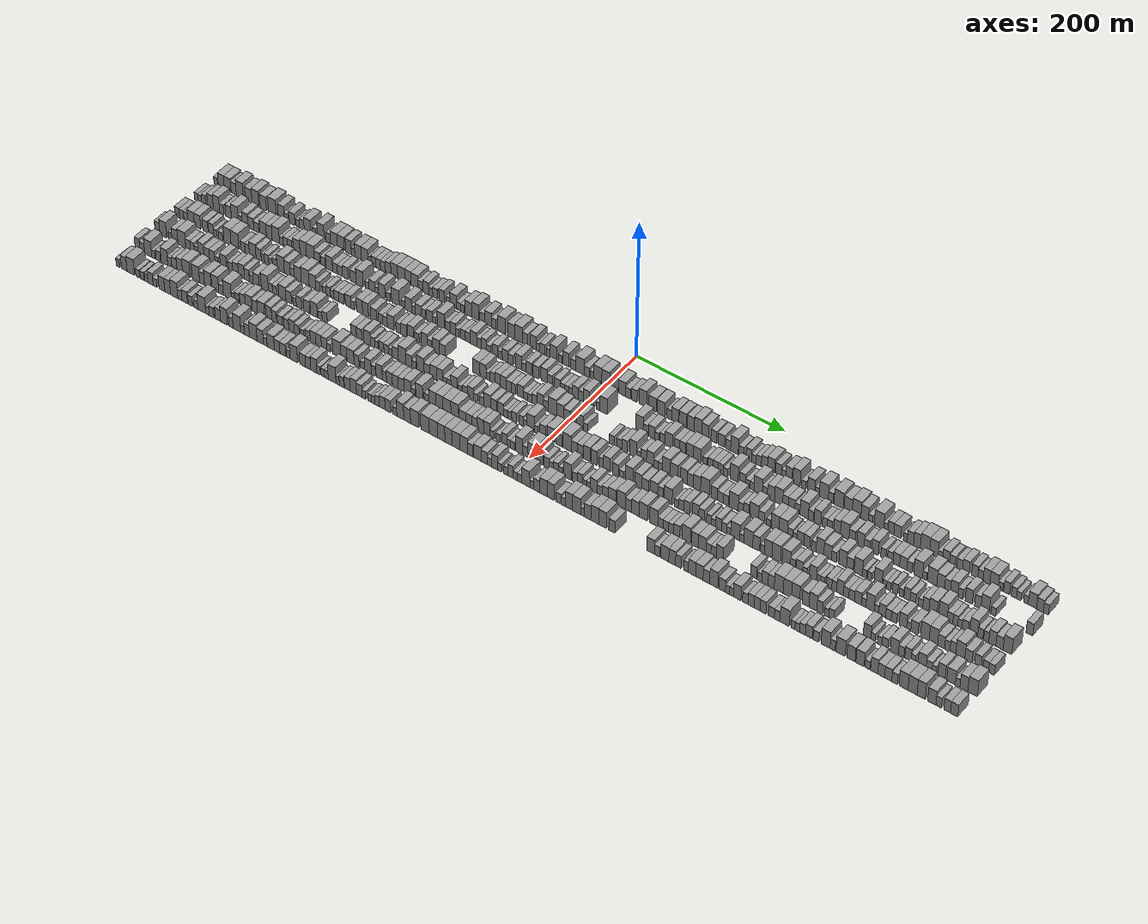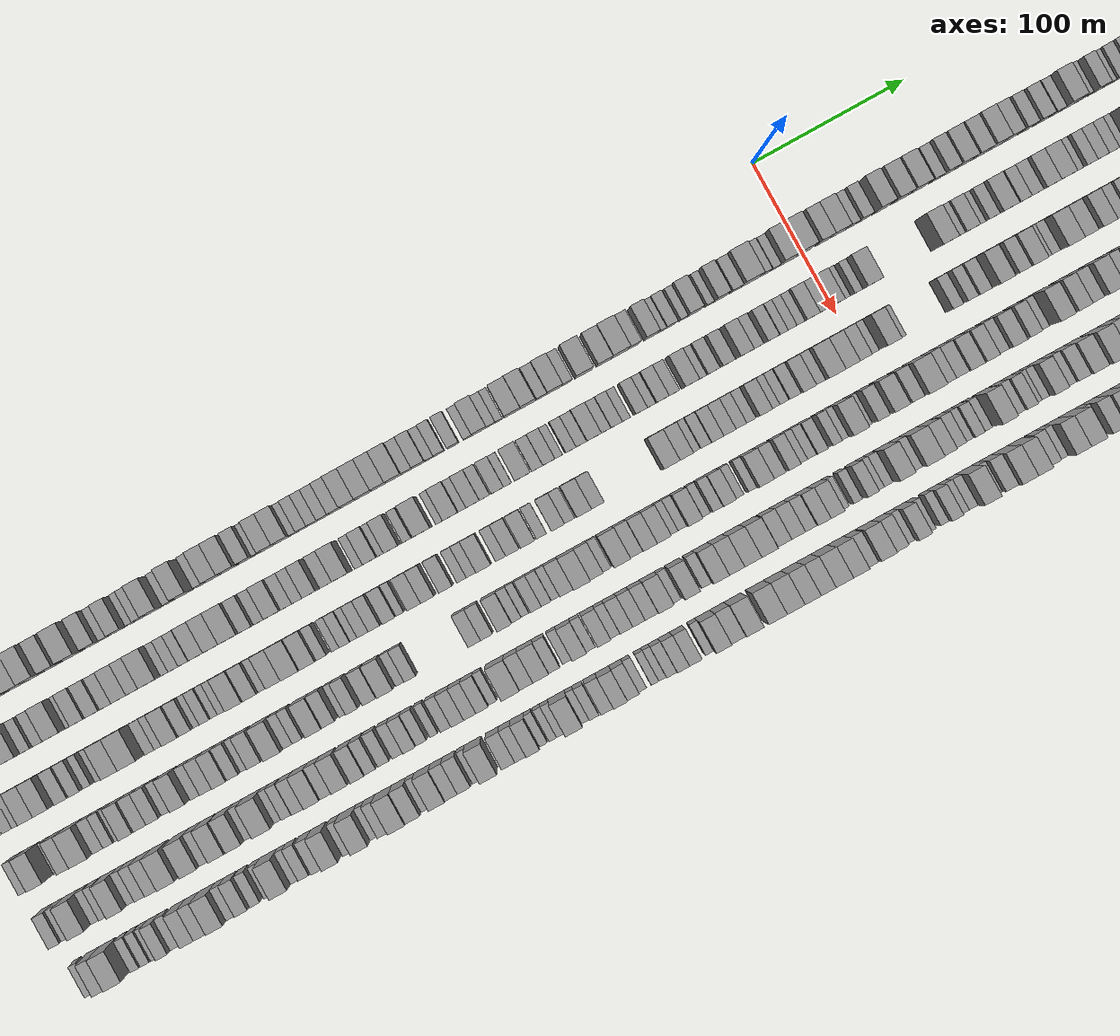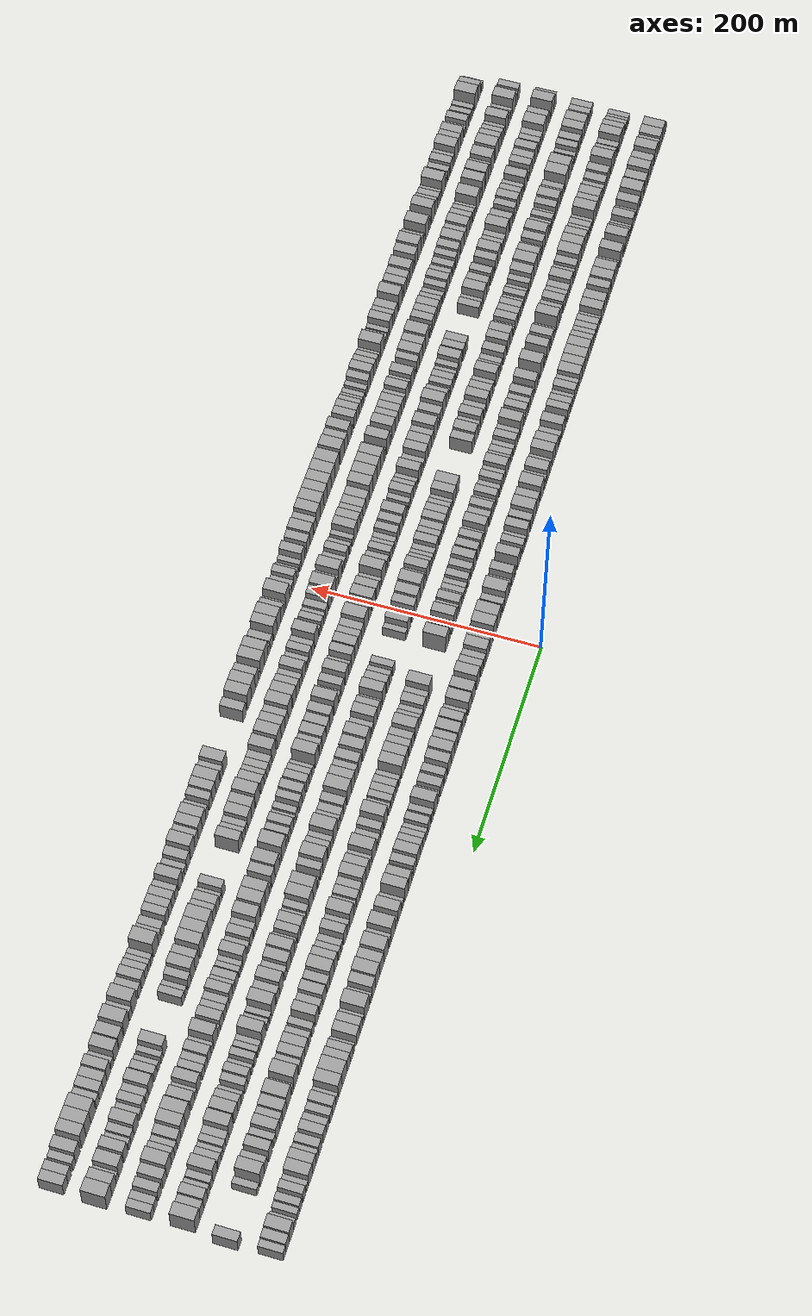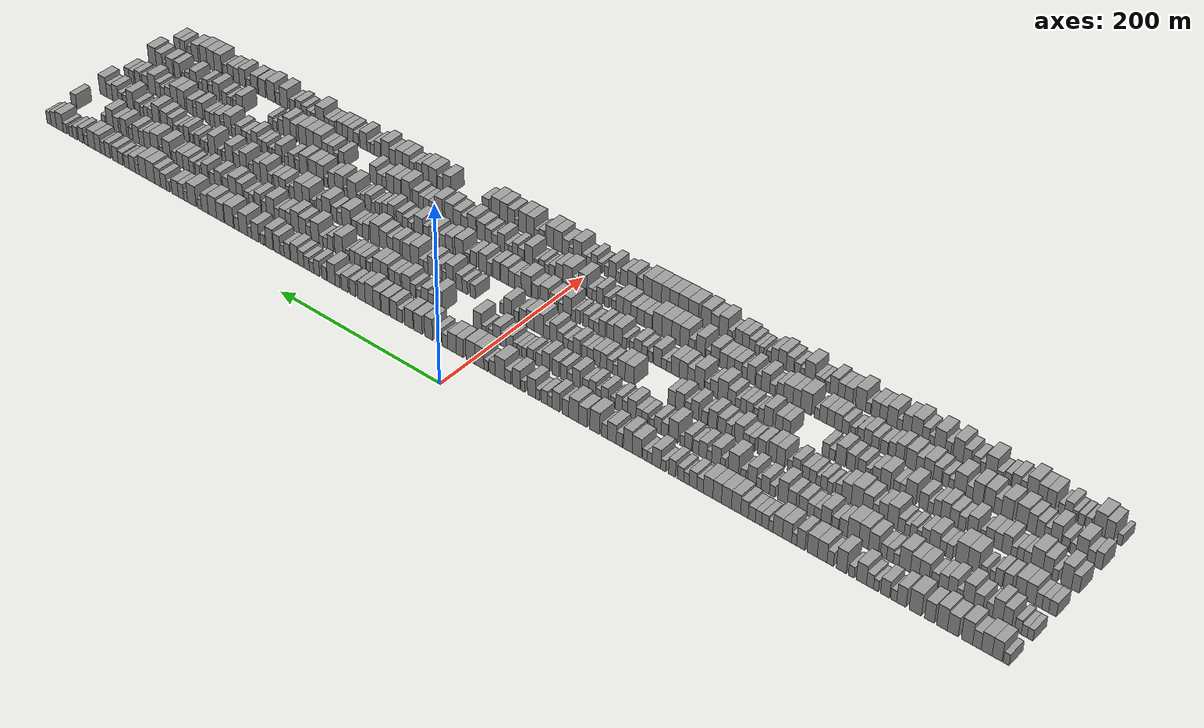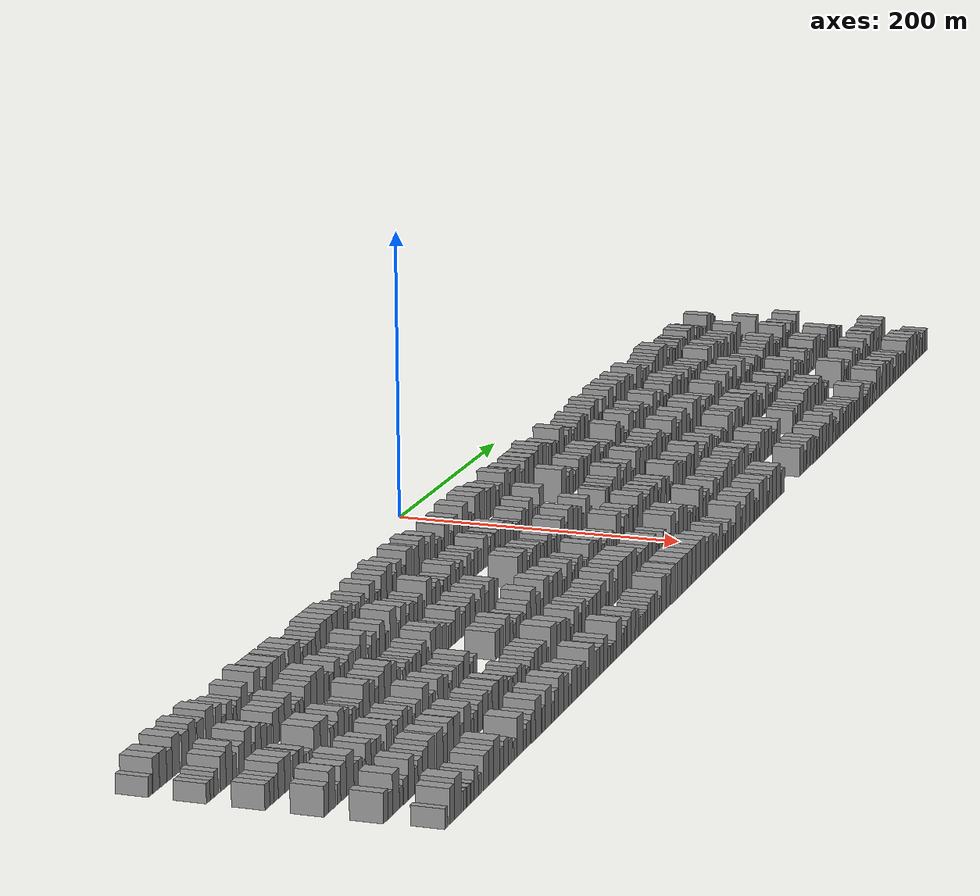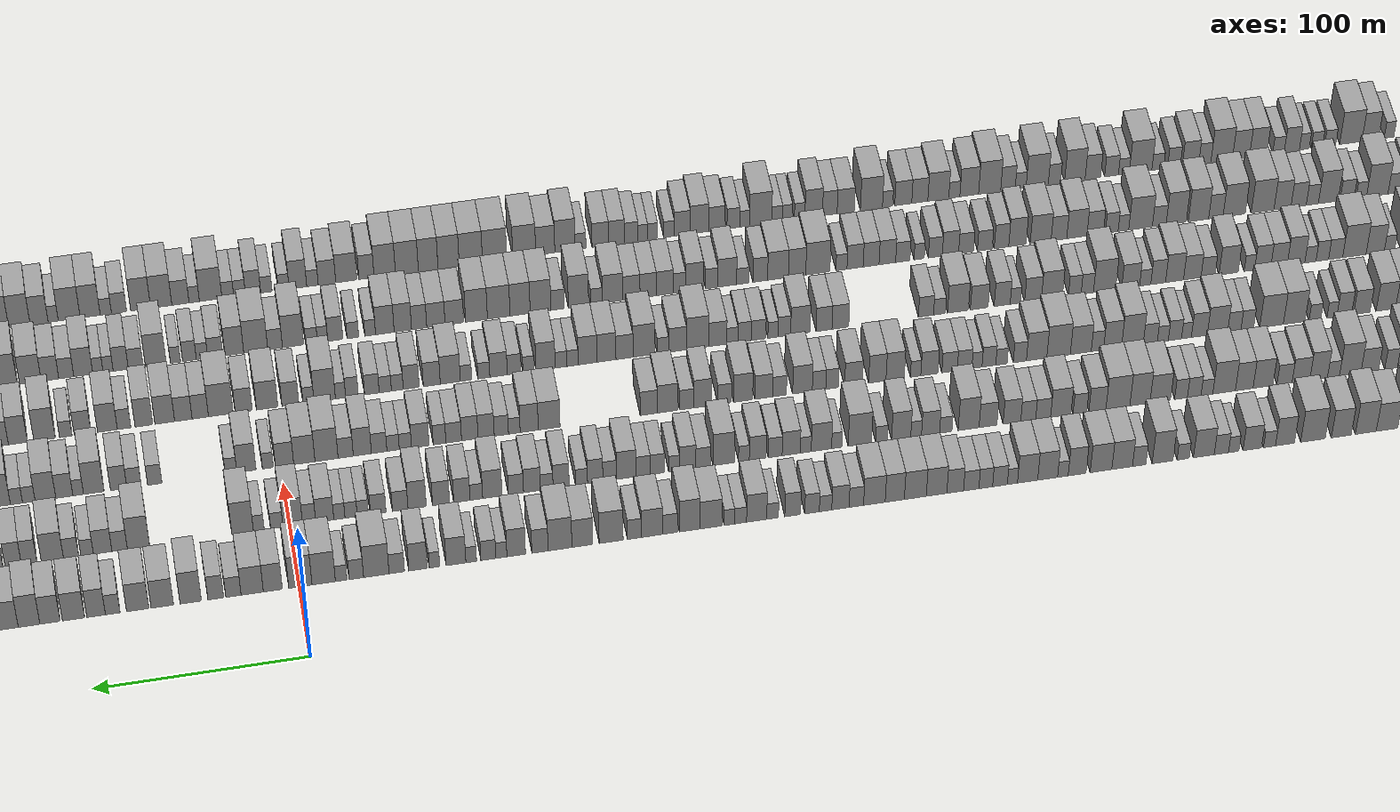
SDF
<sdf version="1.6">
 <world name="default">
  <scene>
   <sky><clouds><speed>12</speed></clouds></sky>
   <ambient>0.4 0.4 0.4 1</ambient>
   <background>0.7 0.7 0.7 1</background>
   <shadows>1</shadows>
  </scene>
  <gravity>0 0 -9.8066</gravity>
  <magnetic_field>6e-06 2.3e-05 -4.2e-05</magnetic_field>
  <physics default="0" name="default_physics" type="ode">
   <ode>
    <solver>
     <type>quick</type>
     <iters>10</iters>
     <sor>1.0</sor>
     <use_dynamic_moi_rescaling>0</use_dynamic_moi_rescaling>
    </solver>
    <constraints>
     <cfm>0</cfm>
     <erp>0.2</erp>
     <contact_max_correcting_vel>100</contact_max_correcting_vel>
     <contact_surface_layer>0.001</contact_surface_layer>
    </constraints>
   </ode>
   <max_step_size>0.004</max_step_size>
   <real_time_factor>1</real_time_factor>
   <real_time_update_rate>250</real_time_update_rate>
  </physics>
  <light name="sun" type="directional">
   <pose>0 0 10 0 0 0</pose>
   <diffuse>0.8 0.8 0.8 1</diffuse>
   <specular>0.2 0.2 0.2 1</specular>
   <attenuation>
    <range>1000</range>
    <constant>0.9</constant>
    <linear>0.01</linear>
    <quadratic>0.001</quadratic>
   </attenuation>
   <direction>-0.5 0.1 -0.9</direction>
  </light>
  <model name="building_1">
   <static>1</static>
   <pose>50.0000 -567.2301 0 0.000000 0.000000 0.000000</pose>
   <link name="link">
    <pose>0 0 6.00 0 0 0</pose>
    <collision name="collision"><geometry><box><size>20.0000 5.5399 12.0000</size></box></geometry></collision>
    <visual name="visual">
     <cast_shadows>0</cast_shadows>
     <geometry><box><size>20.0000 5.5399 12.0000</size></box></geometry>
     <material>
      <script>
       <uri>model://grey_wall/materials/scripts</uri>
       <uri>model://grey_wall/materials/textures</uri>
       <name>vrc/grey_wall</name>
      </script>
     </material>
    </visual>
   </link>
  </model>
  <model name="building_2">
   <static>1</static>
   <pose>50.0000 -558.8045 0 0.000000 0.000000 0.000000</pose>
   <link name="link">
    <pose>0 0 10.50 0 0 0</pose>
    <collision name="collision"><geometry><box><size>20.0000 9.3112 21.0000</size></box></geometry></collision>
    <visual name="visual">
     <cast_shadows>0</cast_shadows>
     <geometry><box><size>20.0000 9.3112 21.0000</size></box></geometry>
     <material>
      <script>
       <uri>model://grey_wall/materials/scripts</uri>
       <uri>model://grey_wall/materials/textures</uri>
       <name>vrc/grey_wall</name>
      </script>
     </material>
    </visual>
   </link>
  </model>
  <model name="building_3">
   <static>1</static>
   <pose>50.0000 -549.0087 0 0.000000 0.000000 0.000000</pose>
   <link name="link">
    <pose>0 0 10.50 0 0 0</pose>
    <collision name="collision"><geometry><box><size>20.0000 10.2805 21.0000</size></box></geometry></collision>
    <visual name="visual">
     <cast_shadows>0</cast_shadows>
     <geometry><box><size>20.0000 10.2805 21.0000</size></box></geometry>
     <material>
      <script>
       <uri>model://grey_wall/materials/scripts</uri>
       <uri>model://grey_wall/materials/textures</uri>
       <name>vrc/grey_wall</name>
      </script>
     </material>
    </visual>
   </link>
  </model>
  <model name="building_4">
   <static>1</static>
   <pose>50.0000 -539.7940 0 0.000000 0.000000 0.000000</pose>
   <link name="link">
    <pose>0 0 9.00 0 0 0</pose>
    <collision name="collision"><geometry><box><size>20.0000 8.1488 18.0000</size></box></geometry></collision>
    <visual name="visual">
     <cast_shadows>0</cast_shadows>
     <geometry><box><size>20.0000 8.1488 18.0000</size></box></geometry>
     <material>
      <script>
       <uri>model://grey_wall/materials/scripts</uri>
       <uri>model://grey_wall/materials/textures</uri>
       <name>vrc/grey_wall</name>
      </script>
     </material>
    </visual>
   </link>
  </model>
  <model name="building_5">
   <static>1</static>
   <pose>50.0000 -530.4529 0 0.000000 0.000000 0.000000</pose>
   <link name="link">
    <pose>0 0 12.00 0 0 0</pose>
    <collision name="collision"><geometry><box><size>20.0000 10.5335 24.0000</size></box></geometry></collision>
    <visual name="visual">
     <cast_shadows>0</cast_shadows>
     <geometry><box><size>20.0000 10.5335 24.0000</size></box></geometry>
     <material>
      <script>
       <uri>model://grey_wall/materials/scripts</uri>
       <uri>model://grey_wall/materials/textures</uri>
       <name>vrc/grey_wall</name>
      </script>
     </material>
    </visual>
   </link>
  </model>
  <model name="building_6">
   <static>1</static>
   <pose>50.0000 -516.9666 0 0.000000 0.000000 0.000000</pose>
   <link name="link">
    <pose>0 0 10.50 0 0 0</pose>
    <collision name="collision"><geometry><box><size>20.0000 10.4390 21.0000</size></box></geometry></collision>
    <visual name="visual">
     <cast_shadows>0</cast_shadows>
     <geometry><box><size>20.0000 10.4390 21.0000</size></box></geometry>
     <material>
      <script>
       <uri>model://grey_wall/materials/scripts</uri>
       <uri>model://grey_wall/materials/textures</uri>
       <name>vrc/grey_wall</name>
      </script>
     </material>
    </visual>
   </link>
  </model>
  <model name="building_7">
   <static>1</static>
   <pose>50.0000 -506.6521 0 0.000000 0.000000 0.000000</pose>
   <link name="link">
    <pose>0 0 12.00 0 0 0</pose>
    <collision name="collision"><geometry><box><size>20.0000 10.1902 24.0000</size></box></geometry></collision>
    <visual name="visual">
     <cast_shadows>0</cast_shadows>
     <geometry><box><size>20.0000 10.1902 24.0000</size></box></geometry>
     <material>
      <script>
       <uri>model://grey_wall/materials/scripts</uri>
       <uri>model://grey_wall/materials/textures</uri>
       <name>vrc/grey_wall</name>
      </script>
     </material>
    </visual>
   </link>
  </model>
  <model name="building_8">
   <static>1</static>
   <pose>50.0000 -494.7407 0 0.000000 0.000000 0.000000</pose>
   <link name="link">
    <pose>0 0 10.50 0 0 0</pose>
    <collision name="collision"><geometry><box><size>20.0000 9.6325 21.0000</size></box></geometry></collision>
    <visual name="visual">
     <cast_shadows>0</cast_shadows>
     <geometry><box><size>20.0000 9.6325 21.0000</size></box></geometry>
     <material>
      <script>
       <uri>model://grey_wall/materials/scripts</uri>
       <uri>model://grey_wall/materials/textures</uri>
       <name>vrc/grey_wall</name>
      </script>
     </material>
    </visual>
   </link>
  </model>
  <model name="building_9">
   <static>1</static>
   <pose>50.0000 -480.9570 0 0.000000 0.000000 0.000000</pose>
   <link name="link">
    <pose>0 0 12.00 0 0 0</pose>
    <collision name="collision"><geometry><box><size>20.0000 11.9348 24.0000</size></box></geometry></collision>
    <visual name="visual">
     <cast_shadows>0</cast_shadows>
     <geometry><box><size>20.0000 11.9348 24.0000</size></box></geometry>
     <material>
      <script>
       <uri>model://grey_wall/materials/scripts</uri>
       <uri>model://grey_wall/materials/textures</uri>
       <name>vrc/grey_wall</name>
      </script>
     </material>
    </visual>
   </link>
  </model>
  <model name="building_10">
   <static>1</static>
   <pose>50.0000 -467.3841 0 0.000000 0.000000 0.000000</pose>
   <link name="link">
    <pose>0 0 10.50 0 0 0</pose>
    <collision name="collision"><geometry><box><size>20.0000 9.2111 21.0000</size></box></geometry></collision>
    <visual name="visual">
     <cast_shadows>0</cast_shadows>
     <geometry><box><size>20.0000 9.2111 21.0000</size></box></geometry>
     <material>
      <script>
       <uri>model://grey_wall/materials/scripts</uri>
       <uri>model://grey_wall/materials/textures</uri>
       <name>vrc/grey_wall</name>
      </script>
     </material>
    </visual>
   </link>
  </model>
  <model name="building_11">
   <static>1</static>
   <pose>50.0000 -459.8675 0 0.000000 0.000000 0.000000</pose>
   <link name="link">
    <pose>0 0 6.00 0 0 0</pose>
    <collision name="collision"><geometry><box><size>20.0000 5.8221 12.0000</size></box></geometry></collision>
    <visual name="visual">
     <cast_shadows>0</cast_shadows>
     <geometry><box><size>20.0000 5.8221 12.0000</size></box></geometry>
     <material>
      <script>
       <uri>model://grey_wall/materials/scripts</uri>
       <uri>model://grey_wall/materials/textures</uri>
       <name>vrc/grey_wall</name>
      </script>
     </material>
    </visual>
   </link>
  </model>
  <model name="building_12">
   <static>1</static>
   <pose>50.0000 -451.4978 0 0.000000 0.000000 0.000000</pose>
   <link name="link">
    <pose>0 0 9.00 0 0 0</pose>
    <collision name="collision"><geometry><box><size>20.0000 8.9171 18.0000</size></box></geometry></collision>
    <visual name="visual">
     <cast_shadows>0</cast_shadows>
     <geometry><box><size>20.0000 8.9171 18.0000</size></box></geometry>
     <material>
      <script>
       <uri>model://grey_wall/materials/scripts</uri>
       <uri>model://grey_wall/materials/textures</uri>
       <name>vrc/grey_wall</name>
      </script>
     </material>
    </visual>
   </link>
  </model>
  <model name="building_13">
   <static>1</static>
   <pose>50.0000 -442.5246 0 0.000000 0.000000 0.000000</pose>
   <link name="link">
    <pose>0 0 6.00 0 0 0</pose>
    <collision name="collision"><geometry><box><size>20.0000 5.0293 12.0000</size></box></geometry></collision>
    <visual name="visual">
     <cast_shadows>0</cast_shadows>
     <geometry><box><size>20.0000 5.0293 12.0000</size></box></geometry>
     <material>
      <script>
       <uri>model://grey_wall/materials/scripts</uri>
       <uri>model://grey_wall/materials/textures</uri>
       <name>vrc/grey_wall</name>
      </script>
     </material>
    </visual>
   </link>
  </model>
  <model name="building_14">
   <static>1</static>
   <pose>50.0000 -436.5586 0 0.000000 0.000000 0.000000</pose>
   <link name="link">
    <pose>0 0 7.50 0 0 0</pose>
    <collision name="collision"><geometry><box><size>20.0000 6.9027 15.0000</size></box></geometry></collision>
    <visual name="visual">
     <cast_shadows>0</cast_shadows>
     <geometry><box><size>20.0000 6.9027 15.0000</size></box></geometry>
     <material>
      <script>
       <uri>model://grey_wall/materials/scripts</uri>
       <uri>model://grey_wall/materials/textures</uri>
       <name>vrc/grey_wall</name>
      </script>
     </material>
    </visual>
   </link>
  </model>
  <model name="building_15">
   <static>1</static>
   <pose>50.0000 -428.0782 0 0.000000 0.000000 0.000000</pose>
   <link name="link">
    <pose>0 0 10.50 0 0 0</pose>
    <collision name="collision"><geometry><box><size>20.0000 10.0581 21.0000</size></box></geometry></collision>
    <visual name="visual">
     <cast_shadows>0</cast_shadows>
     <geometry><box><size>20.0000 10.0581 21.0000</size></box></geometry>
     <material>
      <script>
       <uri>model://grey_wall/materials/scripts</uri>
       <uri>model://grey_wall/materials/textures</uri>
       <name>vrc/grey_wall</name>
      </script>
     </material>
    </visual>
   </link>
  </model>
  <model name="building_16">
   <static>1</static>
   <pose>50.0000 -418.1078 0 0.000000 0.000000 0.000000</pose>
   <link name="link">
    <pose>0 0 6.00 0 0 0</pose>
    <collision name="collision"><geometry><box><size>20.0000 5.8827 12.0000</size></box></geometry></collision>
    <visual name="visual">
     <cast_shadows>0</cast_shadows>
     <geometry><box><size>20.0000 5.8827 12.0000</size></box></geometry>
     <material>
      <script>
       <uri>model://grey_wall/materials/scripts</uri>
       <uri>model://grey_wall/materials/textures</uri>
       <name>vrc/grey_wall</name>
      </script>
     </material>
    </visual>
   </link>
  </model>
  <model name="building_17">
   <static>1</static>
   <pose>50.0000 -408.1491 0 0.000000 0.000000 0.000000</pose>
   <link name="link">
    <pose>0 0 12.00 0 0 0</pose>
    <collision name="collision"><geometry><box><size>20.0000 10.0346 24.0000</size></box></geometry></collision>
    <visual name="visual">
     <cast_shadows>0</cast_shadows>
     <geometry><box><size>20.0000 10.0346 24.0000</size></box></geometry>
     <material>
      <script>
       <uri>model://grey_wall/materials/scripts</uri>
       <uri>model://grey_wall/materials/textures</uri>
       <name>vrc/grey_wall</name>
      </script>
     </material>
    </visual>
   </link>
  </model>
  <model name="building_18">
   <static>1</static>
   <pose>50.0000 -396.9003 0 0.000000 0.000000 0.000000</pose>
   <link name="link">
    <pose>0 0 7.50 0 0 0</pose>
    <collision name="collision"><geometry><box><size>20.0000 6.4631 15.0000</size></box></geometry></collision>
    <visual name="visual">
     <cast_shadows>0</cast_shadows>
     <geometry><box><size>20.0000 6.4631 15.0000</size></box></geometry>
     <material>
      <script>
       <uri>model://grey_wall/materials/scripts</uri>
       <uri>model://grey_wall/materials/textures</uri>
       <name>vrc/grey_wall</name>
      </script>
     </material>
    </visual>
   </link>
  </model>
  <model name="building_19">
   <static>1</static>
   <pose>50.0000 -388.6890 0 0.000000 0.000000 0.000000</pose>
   <link name="link">
    <pose>0 0 10.50 0 0 0</pose>
    <collision name="collision"><geometry><box><size>20.0000 9.9597 21.0000</size></box></geometry></collision>
    <visual name="visual">
     <cast_shadows>0</cast_shadows>
     <geometry><box><size>20.0000 9.9597 21.0000</size></box></geometry>
     <material>
      <script>
       <uri>model://grey_wall/materials/scripts</uri>
       <uri>model://grey_wall/materials/textures</uri>
       <name>vrc/grey_wall</name>
      </script>
     </material>
    </visual>
   </link>
  </model>
  <model name="building_20">
   <static>1</static>
   <pose>50.0000 -378.5074 0 0.000000 0.000000 0.000000</pose>
   <link name="link">
    <pose>0 0 10.50 0 0 0</pose>
    <collision name="collision"><geometry><box><size>20.0000 10.4034 21.0000</size></box></geometry></collision>
    <visual name="visual">
     <cast_shadows>0</cast_shadows>
     <geometry><box><size>20.0000 10.4034 21.0000</size></box></geometry>
     <material>
      <script>
       <uri>model://grey_wall/materials/scripts</uri>
       <uri>model://grey_wall/materials/textures</uri>
       <name>vrc/grey_wall</name>
      </script>
     </material>
    </visual>
   </link>
  </model>
  <model name="building_21">
   <static>1</static>
   <pose>50.0000 -367.0154 0 0.000000 0.000000 0.000000</pose>
   <link name="link">
    <pose>0 0 10.50 0 0 0</pose>
    <collision name="collision"><geometry><box><size>20.0000 8.5805 21.0000</size></box></geometry></collision>
    <visual name="visual">
     <cast_shadows>0</cast_shadows>
     <geometry><box><size>20.0000 8.5805 21.0000</size></box></geometry>
     <material>
      <script>
       <uri>model://grey_wall/materials/scripts</uri>
       <uri>model://grey_wall/materials/textures</uri>
       <name>vrc/grey_wall</name>
      </script>
     </material>
    </visual>
   </link>
  </model>
  <model name="building_22">
   <static>1</static>
   <pose>50.0000 -360.1869 0 0.000000 0.000000 0.000000</pose>
   <link name="link">
    <pose>0 0 6.00 0 0 0</pose>
    <collision name="collision"><geometry><box><size>20.0000 5.0764 12.0000</size></box></geometry></collision>
    <visual name="visual">
     <cast_shadows>0</cast_shadows>
     <geometry><box><size>20.0000 5.0764 12.0000</size></box></geometry>
     <material>
      <script>
       <uri>model://grey_wall/materials/scripts</uri>
       <uri>model://grey_wall/materials/textures</uri>
       <name>vrc/grey_wall</name>
      </script>
     </material>
    </visual>
   </link>
  </model>
  <model name="building_23">
   <static>1</static>
   <pose>50.0000 -352.8688 0 0.000000 0.000000 0.000000</pose>
   <link name="link">
    <pose>0 0 10.50 0 0 0</pose>
    <collision name="collision"><geometry><box><size>20.0000 9.5598 21.0000</size></box></geometry></collision>
    <visual name="visual">
     <cast_shadows>0</cast_shadows>
     <geometry><box><size>20.0000 9.5598 21.0000</size></box></geometry>
     <material>
      <script>
       <uri>model://grey_wall/materials/scripts</uri>
       <uri>model://grey_wall/materials/textures</uri>
       <name>vrc/grey_wall</name>
      </script>
     </material>
    </visual>
   </link>
  </model>
  <model name="building_24">
   <static>1</static>
   <pose>50.0000 -343.2415 0 0.000000 0.000000 0.000000</pose>
   <link name="link">
    <pose>0 0 10.50 0 0 0</pose>
    <collision name="collision"><geometry><box><size>20.0000 9.6949 21.0000</size></box></geometry></collision>
    <visual name="visual">
     <cast_shadows>0</cast_shadows>
     <geometry><box><size>20.0000 9.6949 21.0000</size></box></geometry>
     <material>
      <script>
       <uri>model://grey_wall/materials/scripts</uri>
       <uri>model://grey_wall/materials/textures</uri>
       <name>vrc/grey_wall</name>
      </script>
     </material>
    </visual>
   </link>
  </model>
  <model name="building_25">
   <static>1</static>
   <pose>50.0000 -335.9683 0 0.000000 0.000000 0.000000</pose>
   <link name="link">
    <pose>0 0 6.00 0 0 0</pose>
    <collision name="collision"><geometry><box><size>20.0000 4.8514 12.0000</size></box></geometry></collision>
    <visual name="visual">
     <cast_shadows>0</cast_shadows>
     <geometry><box><size>20.0000 4.8514 12.0000</size></box></geometry>
     <material>
      <script>
       <uri>model://grey_wall/materials/scripts</uri>
       <uri>model://grey_wall/materials/textures</uri>
       <name>vrc/grey_wall</name>
      </script>
     </material>
    </visual>
   </link>
  </model>
  <model name="building_26">
   <static>1</static>
   <pose>50.0000 -330.0134 0 0.000000 0.000000 0.000000</pose>
   <link name="link">
    <pose>0 0 7.50 0 0 0</pose>
    <collision name="collision"><geometry><box><size>20.0000 7.0583 15.0000</size></box></geometry></collision>
    <visual name="visual">
     <cast_shadows>0</cast_shadows>
     <geometry><box><size>20.0000 7.0583 15.0000</size></box></geometry>
     <material>
      <script>
       <uri>model://grey_wall/materials/scripts</uri>
       <uri>model://grey_wall/materials/textures</uri>
       <name>vrc/grey_wall</name>
      </script>
     </material>
    </visual>
   </link>
  </model>
  <model name="building_27">
   <static>1</static>
   <pose>50.0000 -323.2139 0 0.000000 0.000000 0.000000</pose>
   <link name="link">
    <pose>0 0 7.50 0 0 0</pose>
    <collision name="collision"><geometry><box><size>20.0000 6.5406 15.0000</size></box></geometry></collision>
    <visual name="visual">
     <cast_shadows>0</cast_shadows>
     <geometry><box><size>20.0000 6.5406 15.0000</size></box></geometry>
     <material>
      <script>
       <uri>model://grey_wall/materials/scripts</uri>
       <uri>model://grey_wall/materials/textures</uri>
       <name>vrc/grey_wall</name>
      </script>
     </material>
    </visual>
   </link>
  </model>
  <model name="building_28">
   <static>1</static>
   <pose>50.0000 -316.2606 0 0.000000 0.000000 0.000000</pose>
   <link name="link">
    <pose>0 0 7.50 0 0 0</pose>
    <collision name="collision"><geometry><box><size>20.0000 7.3660 15.0000</size></box></geometry></collision>
    <visual name="visual">
     <cast_shadows>0</cast_shadows>
     <geometry><box><size>20.0000 7.3660 15.0000</size></box></geometry>
     <material>
      <script>
       <uri>model://grey_wall/materials/scripts</uri>
       <uri>model://grey_wall/materials/textures</uri>
       <name>vrc/grey_wall</name>
      </script>
     </material>
    </visual>
   </link>
  </model>
  <model name="building_29">
   <static>1</static>
   <pose>50.0000 -308.5923 0 0.000000 0.000000 0.000000</pose>
   <link name="link">
    <pose>0 0 9.00 0 0 0</pose>
    <collision name="collision"><geometry><box><size>20.0000 7.9706 18.0000</size></box></geometry></collision>
    <visual name="visual">
     <cast_shadows>0</cast_shadows>
     <geometry><box><size>20.0000 7.9706 18.0000</size></box></geometry>
     <material>
      <script>
       <uri>model://grey_wall/materials/scripts</uri>
       <uri>model://grey_wall/materials/textures</uri>
       <name>vrc/grey_wall</name>
      </script>
     </material>
    </visual>
   </link>
  </model>
  <model name="building_30">
   <static>1</static>
   <pose>50.0000 -299.7059 0 0.000000 0.000000 0.000000</pose>
   <link name="link">
    <pose>0 0 10.50 0 0 0</pose>
    <collision name="collision"><geometry><box><size>20.0000 9.8024 21.0000</size></box></geometry></collision>
    <visual name="visual">
     <cast_shadows>0</cast_shadows>
     <geometry><box><size>20.0000 9.8024 21.0000</size></box></geometry>
     <material>
      <script>
       <uri>model://grey_wall/materials/scripts</uri>
       <uri>model://grey_wall/materials/textures</uri>
       <name>vrc/grey_wall</name>
      </script>
     </material>
    </visual>
   </link>
  </model>
  <model name="building_31">
   <static>1</static>
   <pose>50.0000 -289.5650 0 0.000000 0.000000 0.000000</pose>
   <link name="link">
    <pose>0 0 10.50 0 0 0</pose>
    <collision name="collision"><geometry><box><size>20.0000 10.4794 21.0000</size></box></geometry></collision>
    <visual name="visual">
     <cast_shadows>0</cast_shadows>
     <geometry><box><size>20.0000 10.4794 21.0000</size></box></geometry>
     <material>
      <script>
       <uri>model://grey_wall/materials/scripts</uri>
       <uri>model://grey_wall/materials/textures</uri>
       <name>vrc/grey_wall</name>
      </script>
     </material>
    </visual>
   </link>
  </model>
  <model name="building_32">
   <static>1</static>
   <pose>50.0000 -279.7519 0 0.000000 0.000000 0.000000</pose>
   <link name="link">
    <pose>0 0 10.50 0 0 0</pose>
    <collision name="collision"><geometry><box><size>20.0000 9.1468 21.0000</size></box></geometry></collision>
    <visual name="visual">
     <cast_shadows>0</cast_shadows>
     <geometry><box><size>20.0000 9.1468 21.0000</size></box></geometry>
     <material>
      <script>
       <uri>model://grey_wall/materials/scripts</uri>
       <uri>model://grey_wall/materials/textures</uri>
       <name>vrc/grey_wall</name>
      </script>
     </material>
    </visual>
   </link>
  </model>
  <model name="building_33">
   <static>1</static>
   <pose>50.0000 -270.0354 0 0.000000 0.000000 0.000000</pose>
   <link name="link">
    <pose>0 0 10.50 0 0 0</pose>
    <collision name="collision"><geometry><box><size>20.0000 10.2861 21.0000</size></box></geometry></collision>
    <visual name="visual">
     <cast_shadows>0</cast_shadows>
     <geometry><box><size>20.0000 10.2861 21.0000</size></box></geometry>
     <material>
      <script>
       <uri>model://grey_wall/materials/scripts</uri>
       <uri>model://grey_wall/materials/textures</uri>
       <name>vrc/grey_wall</name>
      </script>
     </material>
    </visual>
   </link>
  </model>
  <model name="building_34">
   <static>1</static>
   <pose>50.0000 -261.4347 0 0.000000 0.000000 0.000000</pose>
   <link name="link">
    <pose>0 0 7.50 0 0 0</pose>
    <collision name="collision"><geometry><box><size>20.0000 6.9154 15.0000</size></box></geometry></collision>
    <visual name="visual">
     <cast_shadows>0</cast_shadows>
     <geometry><box><size>20.0000 6.9154 15.0000</size></box></geometry>
     <material>
      <script>
       <uri>model://grey_wall/materials/scripts</uri>
       <uri>model://grey_wall/materials/textures</uri>
       <name>vrc/grey_wall</name>
      </script>
     </material>
    </visual>
   </link>
  </model>
  <model name="building_35">
   <static>1</static>
   <pose>50.0000 -253.8665 0 0.000000 0.000000 0.000000</pose>
   <link name="link">
    <pose>0 0 9.00 0 0 0</pose>
    <collision name="collision"><geometry><box><size>20.0000 8.2210 18.0000</size></box></geometry></collision>
    <visual name="visual">
     <cast_shadows>0</cast_shadows>
     <geometry><box><size>20.0000 8.2210 18.0000</size></box></geometry>
     <material>
      <script>
       <uri>model://grey_wall/materials/scripts</uri>
       <uri>model://grey_wall/materials/textures</uri>
       <name>vrc/grey_wall</name>
      </script>
     </material>
    </visual>
   </link>
  </model>
  <model name="building_36">
   <static>1</static>
   <pose>50.0000 -246.8080 0 0.000000 0.000000 0.000000</pose>
   <link name="link">
    <pose>0 0 6.00 0 0 0</pose>
    <collision name="collision"><geometry><box><size>20.0000 5.8959 12.0000</size></box></geometry></collision>
    <visual name="visual">
     <cast_shadows>0</cast_shadows>
     <geometry><box><size>20.0000 5.8959 12.0000</size></box></geometry>
     <material>
      <script>
       <uri>model://grey_wall/materials/scripts</uri>
       <uri>model://grey_wall/materials/textures</uri>
       <name>vrc/grey_wall</name>
      </script>
     </material>
    </visual>
   </link>
  </model>
  <model name="building_37">
   <static>1</static>
   <pose>50.0000 -240.4075 0 0.000000 0.000000 0.000000</pose>
   <link name="link">
    <pose>0 0 7.50 0 0 0</pose>
    <collision name="collision"><geometry><box><size>20.0000 6.9051 15.0000</size></box></geometry></collision>
    <visual name="visual">
     <cast_shadows>0</cast_shadows>
     <geometry><box><size>20.0000 6.9051 15.0000</size></box></geometry>
     <material>
      <script>
       <uri>model://grey_wall/materials/scripts</uri>
       <uri>model://grey_wall/materials/textures</uri>
       <name>vrc/grey_wall</name>
      </script>
     </material>
    </visual>
   </link>
  </model>
  <model name="building_38">
   <static>1</static>
   <pose>50.0000 -231.2114 0 0.000000 0.000000 0.000000</pose>
   <link name="link">
    <pose>0 0 9.00 0 0 0</pose>
    <collision name="collision"><geometry><box><size>20.0000 7.4870 18.0000</size></box></geometry></collision>
    <visual name="visual">
     <cast_shadows>0</cast_shadows>
     <geometry><box><size>20.0000 7.4870 18.0000</size></box></geometry>
     <material>
      <script>
       <uri>model://grey_wall/materials/scripts</uri>
       <uri>model://grey_wall/materials/textures</uri>
       <name>vrc/grey_wall</name>
      </script>
     </material>
    </visual>
   </link>
  </model>
  <model name="building_39">
   <static>1</static>
   <pose>50.0000 -221.6934 0 0.000000 0.000000 0.000000</pose>
   <link name="link">
    <pose>0 0 6.00 0 0 0</pose>
    <collision name="collision"><geometry><box><size>20.0000 5.5491 12.0000</size></box></geometry></collision>
    <visual name="visual">
     <cast_shadows>0</cast_shadows>
     <geometry><box><size>20.0000 5.5491 12.0000</size></box></geometry>
     <material>
      <script>
       <uri>model://grey_wall/materials/scripts</uri>
       <uri>model://grey_wall/materials/textures</uri>
       <name>vrc/grey_wall</name>
      </script>
     </material>
    </visual>
   </link>
  </model>
  <model name="building_40">
   <static>1</static>
   <pose>50.0000 -214.1381 0 0.000000 0.000000 0.000000</pose>
   <link name="link">
    <pose>0 0 10.50 0 0 0</pose>
    <collision name="collision"><geometry><box><size>20.0000 9.5614 21.0000</size></box></geometry></collision>
    <visual name="visual">
     <cast_shadows>0</cast_shadows>
     <geometry><box><size>20.0000 9.5614 21.0000</size></box></geometry>
     <material>
      <script>
       <uri>model://grey_wall/materials/scripts</uri>
       <uri>model://grey_wall/materials/textures</uri>
       <name>vrc/grey_wall</name>
      </script>
     </material>
    </visual>
   </link>
  </model>
  <model name="building_41">
   <static>1</static>
   <pose>50.0000 -206.4901 0 0.000000 0.000000 0.000000</pose>
   <link name="link">
    <pose>0 0 6.00 0 0 0</pose>
    <collision name="collision"><geometry><box><size>20.0000 5.7346 12.0000</size></box></geometry></collision>
    <visual name="visual">
     <cast_shadows>0</cast_shadows>
     <geometry><box><size>20.0000 5.7346 12.0000</size></box></geometry>
     <material>
      <script>
       <uri>model://grey_wall/materials/scripts</uri>
       <uri>model://grey_wall/materials/textures</uri>
       <name>vrc/grey_wall</name>
      </script>
     </material>
    </visual>
   </link>
  </model>
  <model name="building_42">
   <static>1</static>
   <pose>50.0000 -201.2064 0 0.000000 0.000000 0.000000</pose>
   <link name="link">
    <pose>0 0 6.00 0 0 0</pose>
    <collision name="collision"><geometry><box><size>20.0000 4.8327 12.0000</size></box></geometry></collision>
    <visual name="visual">
     <cast_shadows>0</cast_shadows>
     <geometry><box><size>20.0000 4.8327 12.0000</size></box></geometry>
     <material>
      <script>
       <uri>model://grey_wall/materials/scripts</uri>
       <uri>model://grey_wall/materials/textures</uri>
       <name>vrc/grey_wall</name>
      </script>
     </material>
    </visual>
   </link>
  </model>
  <model name="building_43">
   <static>1</static>
   <pose>50.0000 -192.5518 0 0.000000 0.000000 0.000000</pose>
   <link name="link">
    <pose>0 0 10.50 0 0 0</pose>
    <collision name="collision"><geometry><box><size>20.0000 10.4765 21.0000</size></box></geometry></collision>
    <visual name="visual">
     <cast_shadows>0</cast_shadows>
     <geometry><box><size>20.0000 10.4765 21.0000</size></box></geometry>
     <material>
      <script>
       <uri>model://grey_wall/materials/scripts</uri>
       <uri>model://grey_wall/materials/textures</uri>
       <name>vrc/grey_wall</name>
      </script>
     </material>
    </visual>
   </link>
  </model>
  <model name="building_44">
   <static>1</static>
   <pose>50.0000 -182.4696 0 0.000000 0.000000 0.000000</pose>
   <link name="link">
    <pose>0 0 12.00 0 0 0</pose>
    <collision name="collision"><geometry><box><size>20.0000 9.6878 24.0000</size></box></geometry></collision>
    <visual name="visual">
     <cast_shadows>0</cast_shadows>
     <geometry><box><size>20.0000 9.6878 24.0000</size></box></geometry>
     <material>
      <script>
       <uri>model://grey_wall/materials/scripts</uri>
       <uri>model://grey_wall/materials/textures</uri>
       <name>vrc/grey_wall</name>
      </script>
     </material>
    </visual>
   </link>
  </model>
  <model name="building_45">
   <static>1</static>
   <pose>50.0000 -173.1344 0 0.000000 0.000000 0.000000</pose>
   <link name="link">
    <pose>0 0 7.50 0 0 0</pose>
    <collision name="collision"><geometry><box><size>20.0000 6.9827 15.0000</size></box></geometry></collision>
    <visual name="visual">
     <cast_shadows>0</cast_shadows>
     <geometry><box><size>20.0000 6.9827 15.0000</size></box></geometry>
     <material>
      <script>
       <uri>model://grey_wall/materials/scripts</uri>
       <uri>model://grey_wall/materials/textures</uri>
       <name>vrc/grey_wall</name>
      </script>
     </material>
    </visual>
   </link>
  </model>
  <model name="building_46">
   <static>1</static>
   <pose>50.0000 -164.6204 0 0.000000 0.000000 0.000000</pose>
   <link name="link">
    <pose>0 0 10.50 0 0 0</pose>
    <collision name="collision"><geometry><box><size>20.0000 10.0453 21.0000</size></box></geometry></collision>
    <visual name="visual">
     <cast_shadows>0</cast_shadows>
     <geometry><box><size>20.0000 10.0453 21.0000</size></box></geometry>
     <material>
      <script>
       <uri>model://grey_wall/materials/scripts</uri>
       <uri>model://grey_wall/materials/textures</uri>
       <name>vrc/grey_wall</name>
      </script>
     </material>
    </visual>
   </link>
  </model>
  <model name="building_47">
   <static>1</static>
   <pose>50.0000 -156.3387 0 0.000000 0.000000 0.000000</pose>
   <link name="link">
    <pose>0 0 7.50 0 0 0</pose>
    <collision name="collision"><geometry><box><size>20.0000 6.5181 15.0000</size></box></geometry></collision>
    <visual name="visual">
     <cast_shadows>0</cast_shadows>
     <geometry><box><size>20.0000 6.5181 15.0000</size></box></geometry>
     <material>
      <script>
       <uri>model://grey_wall/materials/scripts</uri>
       <uri>model://grey_wall/materials/textures</uri>
       <name>vrc/grey_wall</name>
      </script>
     </material>
    </visual>
   </link>
  </model>
  <model name="building_48">
   <static>1</static>
   <pose>50.0000 -145.4453 0 0.000000 0.000000 0.000000</pose>
   <link name="link">
    <pose>0 0 12.00 0 0 0</pose>
    <collision name="collision"><geometry><box><size>20.0000 11.2687 24.0000</size></box></geometry></collision>
    <visual name="visual">
     <cast_shadows>0</cast_shadows>
     <geometry><box><size>20.0000 11.2687 24.0000</size></box></geometry>
     <material>
      <script>
       <uri>model://grey_wall/materials/scripts</uri>
       <uri>model://grey_wall/materials/textures</uri>
       <name>vrc/grey_wall</name>
      </script>
     </material>
    </visual>
   </link>
  </model>
  <model name="building_49">
   <static>1</static>
   <pose>50.0000 -131.9042 0 0.000000 0.000000 0.000000</pose>
   <link name="link">
    <pose>0 0 10.50 0 0 0</pose>
    <collision name="collision"><geometry><box><size>20.0000 9.8134 21.0000</size></box></geometry></collision>
    <visual name="visual">
     <cast_shadows>0</cast_shadows>
     <geometry><box><size>20.0000 9.8134 21.0000</size></box></geometry>
     <material>
      <script>
       <uri>model://grey_wall/materials/scripts</uri>
       <uri>model://grey_wall/materials/textures</uri>
       <name>vrc/grey_wall</name>
      </script>
     </material>
    </visual>
   </link>
  </model>
  <model name="building_50">
   <static>1</static>
   <pose>50.0000 -121.4116 0 0.000000 0.000000 0.000000</pose>
   <link name="link">
    <pose>0 0 12.00 0 0 0</pose>
    <collision name="collision"><geometry><box><size>20.0000 11.1718 24.0000</size></box></geometry></collision>
    <visual name="visual">
     <cast_shadows>0</cast_shadows>
     <geometry><box><size>20.0000 11.1718 24.0000</size></box></geometry>
     <material>
      <script>
       <uri>model://grey_wall/materials/scripts</uri>
       <uri>model://grey_wall/materials/textures</uri>
       <name>vrc/grey_wall</name>
      </script>
     </material>
    </visual>
   </link>
  </model>
  <model name="building_51">
   <static>1</static>
   <pose>50.0000 -112.0180 0 0.000000 0.000000 0.000000</pose>
   <link name="link">
    <pose>0 0 9.00 0 0 0</pose>
    <collision name="collision"><geometry><box><size>20.0000 7.6156 18.0000</size></box></geometry></collision>
    <visual name="visual">
     <cast_shadows>0</cast_shadows>
     <geometry><box><size>20.0000 7.6156 18.0000</size></box></geometry>
     <material>
      <script>
       <uri>model://grey_wall/materials/scripts</uri>
       <uri>model://grey_wall/materials/textures</uri>
       <name>vrc/grey_wall</name>
      </script>
     </material>
    </visual>
   </link>
  </model>
  <model name="building_52">
   <static>1</static>
   <pose>50.0000 -100.8558 0 0.000000 0.000000 0.000000</pose>
   <link name="link">
    <pose>0 0 10.50 0 0 0</pose>
    <collision name="collision"><geometry><box><size>20.0000 8.7089 21.0000</size></box></geometry></collision>
    <visual name="visual">
     <cast_shadows>0</cast_shadows>
     <geometry><box><size>20.0000 8.7089 21.0000</size></box></geometry>
     <material>
      <script>
       <uri>model://grey_wall/materials/scripts</uri>
       <uri>model://grey_wall/materials/textures</uri>
       <name>vrc/grey_wall</name>
      </script>
     </material>
    </visual>
   </link>
  </model>
  <model name="building_53">
   <static>1</static>
   <pose>50.0000 -93.9283 0 0.000000 0.000000 0.000000</pose>
   <link name="link">
    <pose>0 0 6.00 0 0 0</pose>
    <collision name="collision"><geometry><box><size>20.0000 5.1461 12.0000</size></box></geometry></collision>
    <visual name="visual">
     <cast_shadows>0</cast_shadows>
     <geometry><box><size>20.0000 5.1461 12.0000</size></box></geometry>
     <material>
      <script>
       <uri>model://grey_wall/materials/scripts</uri>
       <uri>model://grey_wall/materials/textures</uri>
       <name>vrc/grey_wall</name>
      </script>
     </material>
    </visual>
   </link>
  </model>
  <model name="building_54">
   <static>1</static>
   <pose>50.0000 -87.8280 0 0.000000 0.000000 0.000000</pose>
   <link name="link">
    <pose>0 0 7.50 0 0 0</pose>
    <collision name="collision"><geometry><box><size>20.0000 7.0544 15.0000</size></box></geometry></collision>
    <visual name="visual">
     <cast_shadows>0</cast_shadows>
     <geometry><box><size>20.0000 7.0544 15.0000</size></box></geometry>
     <material>
      <script>
       <uri>model://grey_wall/materials/scripts</uri>
       <uri>model://grey_wall/materials/textures</uri>
       <name>vrc/grey_wall</name>
      </script>
     </material>
    </visual>
   </link>
  </model>
  <model name="building_55">
   <static>1</static>
   <pose>50.0000 -79.8011 0 0.000000 0.000000 0.000000</pose>
   <link name="link">
    <pose>0 0 6.00 0 0 0</pose>
    <collision name="collision"><geometry><box><size>20.0000 4.9994 12.0000</size></box></geometry></collision>
    <visual name="visual">
     <cast_shadows>0</cast_shadows>
     <geometry><box><size>20.0000 4.9994 12.0000</size></box></geometry>
     <material>
      <script>
       <uri>model://grey_wall/materials/scripts</uri>
       <uri>model://grey_wall/materials/textures</uri>
       <name>vrc/grey_wall</name>
      </script>
     </material>
    </visual>
   </link>
  </model>
  <model name="building_56">
   <static>1</static>
   <pose>50.0000 -72.6937 0 0.000000 0.000000 0.000000</pose>
   <link name="link">
    <pose>0 0 10.50 0 0 0</pose>
    <collision name="collision"><geometry><box><size>20.0000 9.2154 21.0000</size></box></geometry></collision>
    <visual name="visual">
     <cast_shadows>0</cast_shadows>
     <geometry><box><size>20.0000 9.2154 21.0000</size></box></geometry>
     <material>
      <script>
       <uri>model://grey_wall/materials/scripts</uri>
       <uri>model://grey_wall/materials/textures</uri>
       <name>vrc/grey_wall</name>
      </script>
     </material>
    </visual>
   </link>
  </model>
  <model name="building_57">
   <static>1</static>
   <pose>50.0000 -62.6605 0 0.000000 0.000000 0.000000</pose>
   <link name="link">
    <pose>0 0 6.00 0 0 0</pose>
    <collision name="collision"><geometry><box><size>20.0000 4.8509 12.0000</size></box></geometry></collision>
    <visual name="visual">
     <cast_shadows>0</cast_shadows>
     <geometry><box><size>20.0000 4.8509 12.0000</size></box></geometry>
     <material>
      <script>
       <uri>model://grey_wall/materials/scripts</uri>
       <uri>model://grey_wall/materials/textures</uri>
       <name>vrc/grey_wall</name>
      </script>
     </material>
    </visual>
   </link>
  </model>
  <model name="building_58">
   <static>1</static>
   <pose>50.0000 -54.9417 0 0.000000 0.000000 0.000000</pose>
   <link name="link">
    <pose>0 0 10.50 0 0 0</pose>
    <collision name="collision"><geometry><box><size>20.0000 8.5869 21.0000</size></box></geometry></collision>
    <visual name="visual">
     <cast_shadows>0</cast_shadows>
     <geometry><box><size>20.0000 8.5869 21.0000</size></box></geometry>
     <material>
      <script>
       <uri>model://grey_wall/materials/scripts</uri>
       <uri>model://grey_wall/materials/textures</uri>
       <name>vrc/grey_wall</name>
      </script>
     </material>
    </visual>
   </link>
  </model>
  <model name="building_59">
   <static>1</static>
   <pose>50.0000 -45.0534 0 0.000000 0.000000 0.000000</pose>
   <link name="link">
    <pose>0 0 7.50 0 0 0</pose>
    <collision name="collision"><geometry><box><size>20.0000 7.1895 15.0000</size></box></geometry></collision>
    <visual name="visual">
     <cast_shadows>0</cast_shadows>
     <geometry><box><size>20.0000 7.1895 15.0000</size></box></geometry>
     <material>
      <script>
       <uri>model://grey_wall/materials/scripts</uri>
       <uri>model://grey_wall/materials/textures</uri>
       <name>vrc/grey_wall</name>
      </script>
     </material>
    </visual>
   </link>
  </model>
  <model name="building_60">
   <static>1</static>
   <pose>50.0000 -35.5189 0 0.000000 0.000000 0.000000</pose>
   <link name="link">
    <pose>0 0 12.00 0 0 0</pose>
    <collision name="collision"><geometry><box><size>20.0000 11.8795 24.0000</size></box></geometry></collision>
    <visual name="visual">
     <cast_shadows>0</cast_shadows>
     <geometry><box><size>20.0000 11.8795 24.0000</size></box></geometry>
     <material>
      <script>
       <uri>model://grey_wall/materials/scripts</uri>
       <uri>model://grey_wall/materials/textures</uri>
       <name>vrc/grey_wall</name>
      </script>
     </material>
    </visual>
   </link>
  </model>
  <model name="building_61">
   <static>1</static>
   <pose>50.0000 -26.2360 0 0.000000 0.000000 0.000000</pose>
   <link name="link">
    <pose>0 0 7.50 0 0 0</pose>
    <collision name="collision"><geometry><box><size>20.0000 6.6863 15.0000</size></box></geometry></collision>
    <visual name="visual">
     <cast_shadows>0</cast_shadows>
     <geometry><box><size>20.0000 6.6863 15.0000</size></box></geometry>
     <material>
      <script>
       <uri>model://grey_wall/materials/scripts</uri>
       <uri>model://grey_wall/materials/textures</uri>
       <name>vrc/grey_wall</name>
      </script>
     </material>
    </visual>
   </link>
  </model>
  <model name="building_62">
   <static>1</static>
   <pose>50.0000 -19.1876 0 0.000000 0.000000 0.000000</pose>
   <link name="link">
    <pose>0 0 6.00 0 0 0</pose>
    <collision name="collision"><geometry><box><size>20.0000 5.4104 12.0000</size></box></geometry></collision>
    <visual name="visual">
     <cast_shadows>0</cast_shadows>
     <geometry><box><size>20.0000 5.4104 12.0000</size></box></geometry>
     <material>
      <script>
       <uri>model://grey_wall/materials/scripts</uri>
       <uri>model://grey_wall/materials/textures</uri>
       <name>vrc/grey_wall</name>
      </script>
     </material>
    </visual>
   </link>
  </model>
  <model name="building_63">
   <static>1</static>
   <pose>50.0000 -11.0453 0 0.000000 0.000000 0.000000</pose>
   <link name="link">
    <pose>0 0 12.00 0 0 0</pose>
    <collision name="collision"><geometry><box><size>20.0000 10.8742 24.0000</size></box></geometry></collision>
    <visual name="visual">
     <cast_shadows>0</cast_shadows>
     <geometry><box><size>20.0000 10.8742 24.0000</size></box></geometry>
     <material>
      <script>
       <uri>model://grey_wall/materials/scripts</uri>
       <uri>model://grey_wall/materials/textures</uri>
       <name>vrc/grey_wall</name>
      </script>
     </material>
    </visual>
   </link>
  </model>
  <model name="building_64">
   <static>1</static>
   <pose>50.0000 -0.2225 0 0.000000 0.000000 0.000000</pose>
   <link name="link">
    <pose>0 0 12.00 0 0 0</pose>
    <collision name="collision"><geometry><box><size>20.0000 10.7716 24.0000</size></box></geometry></collision>
    <visual name="visual">
     <cast_shadows>0</cast_shadows>
     <geometry><box><size>20.0000 10.7716 24.0000</size></box></geometry>
     <material>
      <script>
       <uri>model://grey_wall/materials/scripts</uri>
       <uri>model://grey_wall/materials/textures</uri>
       <name>vrc/grey_wall</name>
      </script>
     </material>
    </visual>
   </link>
  </model>
  <model name="building_65">
   <static>1</static>
   <pose>50.0000 12.5621 0 0.000000 0.000000 0.000000</pose>
   <link name="link">
    <pose>0 0 10.50 0 0 0</pose>
    <collision name="collision"><geometry><box><size>20.0000 8.7975 21.0000</size></box></geometry></collision>
    <visual name="visual">
     <cast_shadows>0</cast_shadows>
     <geometry><box><size>20.0000 8.7975 21.0000</size></box></geometry>
     <material>
      <script>
       <uri>model://grey_wall/materials/scripts</uri>
       <uri>model://grey_wall/materials/textures</uri>
       <name>vrc/grey_wall</name>
      </script>
     </material>
    </visual>
   </link>
  </model>
  <model name="building_66">
   <static>1</static>
   <pose>50.0000 22.1153 0 0.000000 0.000000 0.000000</pose>
   <link name="link">
    <pose>0 0 10.50 0 0 0</pose>
    <collision name="collision"><geometry><box><size>20.0000 10.3089 21.0000</size></box></geometry></collision>
    <visual name="visual">
     <cast_shadows>0</cast_shadows>
     <geometry><box><size>20.0000 10.3089 21.0000</size></box></geometry>
     <material>
      <script>
       <uri>model://grey_wall/materials/scripts</uri>
       <uri>model://grey_wall/materials/textures</uri>
       <name>vrc/grey_wall</name>
      </script>
     </material>
    </visual>
   </link>
  </model>
  <model name="building_67">
   <static>1</static>
   <pose>50.0000 30.8138 0 0.000000 0.000000 0.000000</pose>
   <link name="link">
    <pose>0 0 7.50 0 0 0</pose>
    <collision name="collision"><geometry><box><size>20.0000 7.0881 15.0000</size></box></geometry></collision>
    <visual name="visual">
     <cast_shadows>0</cast_shadows>
     <geometry><box><size>20.0000 7.0881 15.0000</size></box></geometry>
     <material>
      <script>
       <uri>model://grey_wall/materials/scripts</uri>
       <uri>model://grey_wall/materials/textures</uri>
       <name>vrc/grey_wall</name>
      </script>
     </material>
    </visual>
   </link>
  </model>
  <model name="building_68">
   <static>1</static>
   <pose>50.0000 38.9960 0 0.000000 0.000000 0.000000</pose>
   <link name="link">
    <pose>0 0 9.00 0 0 0</pose>
    <collision name="collision"><geometry><box><size>20.0000 7.2763 18.0000</size></box></geometry></collision>
    <visual name="visual">
     <cast_shadows>0</cast_shadows>
     <geometry><box><size>20.0000 7.2763 18.0000</size></box></geometry>
     <material>
      <script>
       <uri>model://grey_wall/materials/scripts</uri>
       <uri>model://grey_wall/materials/textures</uri>
       <name>vrc/grey_wall</name>
      </script>
     </material>
    </visual>
   </link>
  </model>
  <model name="building_69">
   <static>1</static>
   <pose>50.0000 50.5784 0 0.000000 0.000000 0.000000</pose>
   <link name="link">
    <pose>0 0 12.00 0 0 0</pose>
    <collision name="collision"><geometry><box><size>20.0000 9.8885 24.0000</size></box></geometry></collision>
    <visual name="visual">
     <cast_shadows>0</cast_shadows>
     <geometry><box><size>20.0000 9.8885 24.0000</size></box></geometry>
     <material>
      <script>
       <uri>model://grey_wall/materials/scripts</uri>
       <uri>model://grey_wall/materials/textures</uri>
       <name>vrc/grey_wall</name>
      </script>
     </material>
    </visual>
   </link>
  </model>
  <model name="building_70">
   <static>1</static>
   <pose>50.0000 63.6983 0 0.000000 0.000000 0.000000</pose>
   <link name="link">
    <pose>0 0 10.50 0 0 0</pose>
    <collision name="collision"><geometry><box><size>20.0000 10.3514 21.0000</size></box></geometry></collision>
    <visual name="visual">
     <cast_shadows>0</cast_shadows>
     <geometry><box><size>20.0000 10.3514 21.0000</size></box></geometry>
     <material>
      <script>
       <uri>model://grey_wall/materials/scripts</uri>
       <uri>model://grey_wall/materials/textures</uri>
       <name>vrc/grey_wall</name>
      </script>
     </material>
    </visual>
   </link>
  </model>
  <model name="building_71">
   <static>1</static>
   <pose>50.0000 75.0216 0 0.000000 0.000000 0.000000</pose>
   <link name="link">
    <pose>0 0 10.50 0 0 0</pose>
    <collision name="collision"><geometry><box><size>20.0000 10.2951 21.0000</size></box></geometry></collision>
    <visual name="visual">
     <cast_shadows>0</cast_shadows>
     <geometry><box><size>20.0000 10.2951 21.0000</size></box></geometry>
     <material>
      <script>
       <uri>model://grey_wall/materials/scripts</uri>
       <uri>model://grey_wall/materials/textures</uri>
       <name>vrc/grey_wall</name>
      </script>
     </material>
    </visual>
   </link>
  </model>
  <model name="building_72">
   <static>1</static>
   <pose>50.0000 86.5434 0 0.000000 0.000000 0.000000</pose>
   <link name="link">
    <pose>0 0 7.50 0 0 0</pose>
    <collision name="collision"><geometry><box><size>20.0000 6.7485 15.0000</size></box></geometry></collision>
    <visual name="visual">
     <cast_shadows>0</cast_shadows>
     <geometry><box><size>20.0000 6.7485 15.0000</size></box></geometry>
     <material>
      <script>
       <uri>model://grey_wall/materials/scripts</uri>
       <uri>model://grey_wall/materials/textures</uri>
       <name>vrc/grey_wall</name>
      </script>
     </material>
    </visual>
   </link>
  </model>
  <model name="building_73">
   <static>1</static>
   <pose>50.0000 94.1869 0 0.000000 0.000000 0.000000</pose>
   <link name="link">
    <pose>0 0 10.50 0 0 0</pose>
    <collision name="collision"><geometry><box><size>20.0000 8.5384 21.0000</size></box></geometry></collision>
    <visual name="visual">
     <cast_shadows>0</cast_shadows>
     <geometry><box><size>20.0000 8.5384 21.0000</size></box></geometry>
     <material>
      <script>
       <uri>model://grey_wall/materials/scripts</uri>
       <uri>model://grey_wall/materials/textures</uri>
       <name>vrc/grey_wall</name>
      </script>
     </material>
    </visual>
   </link>
  </model>
  <model name="building_74">
   <static>1</static>
   <pose>50.0000 104.5766 0 0.000000 0.000000 0.000000</pose>
   <link name="link">
    <pose>0 0 10.50 0 0 0</pose>
    <collision name="collision"><geometry><box><size>20.0000 10.2410 21.0000</size></box></geometry></collision>
    <visual name="visual">
     <cast_shadows>0</cast_shadows>
     <geometry><box><size>20.0000 10.2410 21.0000</size></box></geometry>
     <material>
      <script>
       <uri>model://grey_wall/materials/scripts</uri>
       <uri>model://grey_wall/materials/textures</uri>
       <name>vrc/grey_wall</name>
      </script>
     </material>
    </visual>
   </link>
  </model>
  <model name="building_75">
   <static>1</static>
   <pose>50.0000 115.3670 0 0.000000 0.000000 0.000000</pose>
   <link name="link">
    <pose>0 0 10.50 0 0 0</pose>
    <collision name="collision"><geometry><box><size>20.0000 9.3397 21.0000</size></box></geometry></collision>
    <visual name="visual">
     <cast_shadows>0</cast_shadows>
     <geometry><box><size>20.0000 9.3397 21.0000</size></box></geometry>
     <material>
      <script>
       <uri>model://grey_wall/materials/scripts</uri>
       <uri>model://grey_wall/materials/textures</uri>
       <name>vrc/grey_wall</name>
      </script>
     </material>
    </visual>
   </link>
  </model>
  <model name="building_76">
   <static>1</static>
   <pose>50.0000 124.9895 0 0.000000 0.000000 0.000000</pose>
   <link name="link">
    <pose>0 0 12.00 0 0 0</pose>
    <collision name="collision"><geometry><box><size>20.0000 9.9055 24.0000</size></box></geometry></collision>
    <visual name="visual">
     <cast_shadows>0</cast_shadows>
     <geometry><box><size>20.0000 9.9055 24.0000</size></box></geometry>
     <material>
      <script>
       <uri>model://grey_wall/materials/scripts</uri>
       <uri>model://grey_wall/materials/textures</uri>
       <name>vrc/grey_wall</name>
      </script>
     </material>
    </visual>
   </link>
  </model>
  <model name="building_77">
   <static>1</static>
   <pose>50.0000 134.5950 0 0.000000 0.000000 0.000000</pose>
   <link name="link">
    <pose>0 0 10.50 0 0 0</pose>
    <collision name="collision"><geometry><box><size>20.0000 9.3054 21.0000</size></box></geometry></collision>
    <visual name="visual">
     <cast_shadows>0</cast_shadows>
     <geometry><box><size>20.0000 9.3054 21.0000</size></box></geometry>
     <material>
      <script>
       <uri>model://grey_wall/materials/scripts</uri>
       <uri>model://grey_wall/materials/textures</uri>
       <name>vrc/grey_wall</name>
      </script>
     </material>
    </visual>
   </link>
  </model>
  <model name="building_78">
   <static>1</static>
   <pose>50.0000 146.0429 0 0.000000 0.000000 0.000000</pose>
   <link name="link">
    <pose>0 0 9.00 0 0 0</pose>
    <collision name="collision"><geometry><box><size>20.0000 7.5906 18.0000</size></box></geometry></collision>
    <visual name="visual">
     <cast_shadows>0</cast_shadows>
     <geometry><box><size>20.0000 7.5906 18.0000</size></box></geometry>
     <material>
      <script>
       <uri>model://grey_wall/materials/scripts</uri>
       <uri>model://grey_wall/materials/textures</uri>
       <name>vrc/grey_wall</name>
      </script>
     </material>
    </visual>
   </link>
  </model>
  <model name="building_79">
   <static>1</static>
   <pose>50.0000 156.1337 0 0.000000 0.000000 0.000000</pose>
   <link name="link">
    <pose>0 0 9.00 0 0 0</pose>
    <collision name="collision"><geometry><box><size>20.0000 8.5910 18.0000</size></box></geometry></collision>
    <visual name="visual">
     <cast_shadows>0</cast_shadows>
     <geometry><box><size>20.0000 8.5910 18.0000</size></box></geometry>
     <material>
      <script>
       <uri>model://grey_wall/materials/scripts</uri>
       <uri>model://grey_wall/materials/textures</uri>
       <name>vrc/grey_wall</name>
      </script>
     </material>
    </visual>
   </link>
  </model>
  <model name="building_80">
   <static>1</static>
   <pose>50.0000 165.4798 0 0.000000 0.000000 0.000000</pose>
   <link name="link">
    <pose>0 0 7.50 0 0 0</pose>
    <collision name="collision"><geometry><box><size>20.0000 6.1012 15.0000</size></box></geometry></collision>
    <visual name="visual">
     <cast_shadows>0</cast_shadows>
     <geometry><box><size>20.0000 6.1012 15.0000</size></box></geometry>
     <material>
      <script>
       <uri>model://grey_wall/materials/scripts</uri>
       <uri>model://grey_wall/materials/textures</uri>
       <name>vrc/grey_wall</name>
      </script>
     </material>
    </visual>
   </link>
  </model>
  <model name="building_81">
   <static>1</static>
   <pose>50.0000 173.5960 0 0.000000 0.000000 0.000000</pose>
   <link name="link">
    <pose>0 0 12.00 0 0 0</pose>
    <collision name="collision"><geometry><box><size>20.0000 10.1312 24.0000</size></box></geometry></collision>
    <visual name="visual">
     <cast_shadows>0</cast_shadows>
     <geometry><box><size>20.0000 10.1312 24.0000</size></box></geometry>
     <material>
      <script>
       <uri>model://grey_wall/materials/scripts</uri>
       <uri>model://grey_wall/materials/textures</uri>
       <name>vrc/grey_wall</name>
      </script>
     </material>
    </visual>
   </link>
  </model>
  <model name="building_82">
   <static>1</static>
   <pose>50.0000 182.7346 0 0.000000 0.000000 0.000000</pose>
   <link name="link">
    <pose>0 0 7.50 0 0 0</pose>
    <collision name="collision"><geometry><box><size>20.0000 6.1461 15.0000</size></box></geometry></collision>
    <visual name="visual">
     <cast_shadows>0</cast_shadows>
     <geometry><box><size>20.0000 6.1461 15.0000</size></box></geometry>
     <material>
      <script>
       <uri>model://grey_wall/materials/scripts</uri>
       <uri>model://grey_wall/materials/textures</uri>
       <name>vrc/grey_wall</name>
      </script>
     </material>
    </visual>
   </link>
  </model>
  <model name="building_83">
   <static>1</static>
   <pose>50.0000 192.5878 0 0.000000 0.000000 0.000000</pose>
   <link name="link">
    <pose>0 0 9.00 0 0 0</pose>
    <collision name="collision"><geometry><box><size>20.0000 7.5605 18.0000</size></box></geometry></collision>
    <visual name="visual">
     <cast_shadows>0</cast_shadows>
     <geometry><box><size>20.0000 7.5605 18.0000</size></box></geometry>
     <material>
      <script>
       <uri>model://grey_wall/materials/scripts</uri>
       <uri>model://grey_wall/materials/textures</uri>
       <name>vrc/grey_wall</name>
      </script>
     </material>
    </visual>
   </link>
  </model>
  <model name="building_84">
   <static>1</static>
   <pose>50.0000 199.3157 0 0.000000 0.000000 0.000000</pose>
   <link name="link">
    <pose>0 0 6.00 0 0 0</pose>
    <collision name="collision"><geometry><box><size>20.0000 5.8952 12.0000</size></box></geometry></collision>
    <visual name="visual">
     <cast_shadows>0</cast_shadows>
     <geometry><box><size>20.0000 5.8952 12.0000</size></box></geometry>
     <material>
      <script>
       <uri>model://grey_wall/materials/scripts</uri>
       <uri>model://grey_wall/materials/textures</uri>
       <name>vrc/grey_wall</name>
      </script>
     </material>
    </visual>
   </link>
  </model>
  <model name="building_85">
   <static>1</static>
   <pose>50.0000 205.7539 0 0.000000 0.000000 0.000000</pose>
   <link name="link">
    <pose>0 0 7.50 0 0 0</pose>
    <collision name="collision"><geometry><box><size>20.0000 6.9813 15.0000</size></box></geometry></collision>
    <visual name="visual">
     <cast_shadows>0</cast_shadows>
     <geometry><box><size>20.0000 6.9813 15.0000</size></box></geometry>
     <material>
      <script>
       <uri>model://grey_wall/materials/scripts</uri>
       <uri>model://grey_wall/materials/textures</uri>
       <name>vrc/grey_wall</name>
      </script>
     </material>
    </visual>
   </link>
  </model>
  <model name="building_86">
   <static>1</static>
   <pose>50.0000 213.2031 0 0.000000 0.000000 0.000000</pose>
   <link name="link">
    <pose>0 0 9.00 0 0 0</pose>
    <collision name="collision"><geometry><box><size>20.0000 7.9171 18.0000</size></box></geometry></collision>
    <visual name="visual">
     <cast_shadows>0</cast_shadows>
     <geometry><box><size>20.0000 7.9171 18.0000</size></box></geometry>
     <material>
      <script>
       <uri>model://grey_wall/materials/scripts</uri>
       <uri>model://grey_wall/materials/textures</uri>
       <name>vrc/grey_wall</name>
      </script>
     </material>
    </visual>
   </link>
  </model>
  <model name="building_87">
   <static>1</static>
   <pose>50.0000 221.9547 0 0.000000 0.000000 0.000000</pose>
   <link name="link">
    <pose>0 0 10.50 0 0 0</pose>
    <collision name="collision"><geometry><box><size>20.0000 9.5860 21.0000</size></box></geometry></collision>
    <visual name="visual">
     <cast_shadows>0</cast_shadows>
     <geometry><box><size>20.0000 9.5860 21.0000</size></box></geometry>
     <material>
      <script>
       <uri>model://grey_wall/materials/scripts</uri>
       <uri>model://grey_wall/materials/textures</uri>
       <name>vrc/grey_wall</name>
      </script>
     </material>
    </visual>
   </link>
  </model>
  <model name="building_88">
   <static>1</static>
   <pose>50.0000 231.6643 0 0.000000 0.000000 0.000000</pose>
   <link name="link">
    <pose>0 0 9.00 0 0 0</pose>
    <collision name="collision"><geometry><box><size>20.0000 7.8333 18.0000</size></box></geometry></collision>
    <visual name="visual">
     <cast_shadows>0</cast_shadows>
     <geometry><box><size>20.0000 7.8333 18.0000</size></box></geometry>
     <material>
      <script>
       <uri>model://grey_wall/materials/scripts</uri>
       <uri>model://grey_wall/materials/textures</uri>
       <name>vrc/grey_wall</name>
      </script>
     </material>
    </visual>
   </link>
  </model>
  <model name="building_89">
   <static>1</static>
   <pose>50.0000 238.2363 0 0.000000 0.000000 0.000000</pose>
   <link name="link">
    <pose>0 0 6.00 0 0 0</pose>
    <collision name="collision"><geometry><box><size>20.0000 5.3108 12.0000</size></box></geometry></collision>
    <visual name="visual">
     <cast_shadows>0</cast_shadows>
     <geometry><box><size>20.0000 5.3108 12.0000</size></box></geometry>
     <material>
      <script>
       <uri>model://grey_wall/materials/scripts</uri>
       <uri>model://grey_wall/materials/textures</uri>
       <name>vrc/grey_wall</name>
      </script>
     </material>
    </visual>
   </link>
  </model>
  <model name="building_90">
   <static>1</static>
   <pose>50.0000 245.1266 0 0.000000 0.000000 0.000000</pose>
   <link name="link">
    <pose>0 0 10.50 0 0 0</pose>
    <collision name="collision"><geometry><box><size>20.0000 8.4697 21.0000</size></box></geometry></collision>
    <visual name="visual">
     <cast_shadows>0</cast_shadows>
     <geometry><box><size>20.0000 8.4697 21.0000</size></box></geometry>
     <material>
      <script>
       <uri>model://grey_wall/materials/scripts</uri>
       <uri>model://grey_wall/materials/textures</uri>
       <name>vrc/grey_wall</name>
      </script>
     </material>
    </visual>
   </link>
  </model>
  <model name="building_91">
   <static>1</static>
   <pose>50.0000 255.1759 0 0.000000 0.000000 0.000000</pose>
   <link name="link">
    <pose>0 0 12.00 0 0 0</pose>
    <collision name="collision"><geometry><box><size>20.0000 9.6289 24.0000</size></box></geometry></collision>
    <visual name="visual">
     <cast_shadows>0</cast_shadows>
     <geometry><box><size>20.0000 9.6289 24.0000</size></box></geometry>
     <material>
      <script>
       <uri>model://grey_wall/materials/scripts</uri>
       <uri>model://grey_wall/materials/textures</uri>
       <name>vrc/grey_wall</name>
      </script>
     </material>
    </visual>
   </link>
  </model>
  <model name="building_92">
   <static>1</static>
   <pose>50.0000 264.7619 0 0.000000 0.000000 0.000000</pose>
   <link name="link">
    <pose>0 0 6.00 0 0 0</pose>
    <collision name="collision"><geometry><box><size>20.0000 5.5431 12.0000</size></box></geometry></collision>
    <visual name="visual">
     <cast_shadows>0</cast_shadows>
     <geometry><box><size>20.0000 5.5431 12.0000</size></box></geometry>
     <material>
      <script>
       <uri>model://grey_wall/materials/scripts</uri>
       <uri>model://grey_wall/materials/textures</uri>
       <name>vrc/grey_wall</name>
      </script>
     </material>
    </visual>
   </link>
  </model>
  <model name="building_93">
   <static>1</static>
   <pose>50.0000 274.3921 0 0.000000 0.000000 0.000000</pose>
   <link name="link">
    <pose>0 0 10.50 0 0 0</pose>
    <collision name="collision"><geometry><box><size>20.0000 9.7174 21.0000</size></box></geometry></collision>
    <visual name="visual">
     <cast_shadows>0</cast_shadows>
     <geometry><box><size>20.0000 9.7174 21.0000</size></box></geometry>
     <material>
      <script>
       <uri>model://grey_wall/materials/scripts</uri>
       <uri>model://grey_wall/materials/textures</uri>
       <name>vrc/grey_wall</name>
      </script>
     </material>
    </visual>
   </link>
  </model>
  <model name="building_94">
   <static>1</static>
   <pose>50.0000 282.0814 0 0.000000 0.000000 0.000000</pose>
   <link name="link">
    <pose>0 0 6.00 0 0 0</pose>
    <collision name="collision"><geometry><box><size>20.0000 5.6611 12.0000</size></box></geometry></collision>
    <visual name="visual">
     <cast_shadows>0</cast_shadows>
     <geometry><box><size>20.0000 5.6611 12.0000</size></box></geometry>
     <material>
      <script>
       <uri>model://grey_wall/materials/scripts</uri>
       <uri>model://grey_wall/materials/textures</uri>
       <name>vrc/grey_wall</name>
      </script>
     </material>
    </visual>
   </link>
  </model>
  <model name="building_95">
   <static>1</static>
   <pose>50.0000 290.6606 0 0.000000 0.000000 0.000000</pose>
   <link name="link">
    <pose>0 0 12.00 0 0 0</pose>
    <collision name="collision"><geometry><box><size>20.0000 11.4973 24.0000</size></box></geometry></collision>
    <visual name="visual">
     <cast_shadows>0</cast_shadows>
     <geometry><box><size>20.0000 11.4973 24.0000</size></box></geometry>
     <material>
      <script>
       <uri>model://grey_wall/materials/scripts</uri>
       <uri>model://grey_wall/materials/textures</uri>
       <name>vrc/grey_wall</name>
      </script>
     </material>
    </visual>
   </link>
  </model>
  <model name="building_96">
   <static>1</static>
   <pose>50.0000 299.6775 0 0.000000 0.000000 0.000000</pose>
   <link name="link">
    <pose>0 0 7.50 0 0 0</pose>
    <collision name="collision"><geometry><box><size>20.0000 6.5364 15.0000</size></box></geometry></collision>
    <visual name="visual">
     <cast_shadows>0</cast_shadows>
     <geometry><box><size>20.0000 6.5364 15.0000</size></box></geometry>
     <material>
      <script>
       <uri>model://grey_wall/materials/scripts</uri>
       <uri>model://grey_wall/materials/textures</uri>
       <name>vrc/grey_wall</name>
      </script>
     </material>
    </visual>
   </link>
  </model>
  <model name="building_97">
   <static>1</static>
   <pose>50.0000 309.9370 0 0.000000 0.000000 0.000000</pose>
   <link name="link">
    <pose>0 0 12.00 0 0 0</pose>
    <collision name="collision"><geometry><box><size>20.0000 11.9828 24.0000</size></box></geometry></collision>
    <visual name="visual">
     <cast_shadows>0</cast_shadows>
     <geometry><box><size>20.0000 11.9828 24.0000</size></box></geometry>
     <material>
      <script>
       <uri>model://grey_wall/materials/scripts</uri>
       <uri>model://grey_wall/materials/textures</uri>
       <name>vrc/grey_wall</name>
      </script>
     </material>
    </visual>
   </link>
  </model>
  <model name="building_98">
   <static>1</static>
   <pose>50.0000 322.1000 0 0.000000 0.000000 0.000000</pose>
   <link name="link">
    <pose>0 0 10.50 0 0 0</pose>
    <collision name="collision"><geometry><box><size>20.0000 10.3431 21.0000</size></box></geometry></collision>
    <visual name="visual">
     <cast_shadows>0</cast_shadows>
     <geometry><box><size>20.0000 10.3431 21.0000</size></box></geometry>
     <material>
      <script>
       <uri>model://grey_wall/materials/scripts</uri>
       <uri>model://grey_wall/materials/textures</uri>
       <name>vrc/grey_wall</name>
      </script>
     </material>
    </visual>
   </link>
  </model>
  <model name="building_99">
   <static>1</static>
   <pose>50.0000 332.9563 0 0.000000 0.000000 0.000000</pose>
   <link name="link">
    <pose>0 0 12.00 0 0 0</pose>
    <collision name="collision"><geometry><box><size>20.0000 11.3695 24.0000</size></box></geometry></collision>
    <visual name="visual">
     <cast_shadows>0</cast_shadows>
     <geometry><box><size>20.0000 11.3695 24.0000</size></box></geometry>
     <material>
      <script>
       <uri>model://grey_wall/materials/scripts</uri>
       <uri>model://grey_wall/materials/textures</uri>
       <name>vrc/grey_wall</name>
      </script>
     </material>
    </visual>
   </link>
  </model>
  <model name="building_100">
   <static>1</static>
   <pose>50.0000 343.3464 0 0.000000 0.000000 0.000000</pose>
   <link name="link">
    <pose>0 0 10.50 0 0 0</pose>
    <collision name="collision"><geometry><box><size>20.0000 9.4107 21.0000</size></box></geometry></collision>
    <visual name="visual">
     <cast_shadows>0</cast_shadows>
     <geometry><box><size>20.0000 9.4107 21.0000</size></box></geometry>
     <material>
      <script>
       <uri>model://grey_wall/materials/scripts</uri>
       <uri>model://grey_wall/materials/textures</uri>
       <name>vrc/grey_wall</name>
      </script>
     </material>
    </visual>
   </link>
  </model>
  <model name="building_101">
   <static>1</static>
   <pose>50.0000 350.8720 0 0.000000 0.000000 0.000000</pose>
   <link name="link">
    <pose>0 0 6.00 0 0 0</pose>
    <collision name="collision"><geometry><box><size>20.0000 5.6406 12.0000</size></box></geometry></collision>
    <visual name="visual">
     <cast_shadows>0</cast_shadows>
     <geometry><box><size>20.0000 5.6406 12.0000</size></box></geometry>
     <material>
      <script>
       <uri>model://grey_wall/materials/scripts</uri>
       <uri>model://grey_wall/materials/textures</uri>
       <name>vrc/grey_wall</name>
      </script>
     </material>
    </visual>
   </link>
  </model>
  <model name="building_102">
   <static>1</static>
   <pose>50.0000 361.6857 0 0.000000 0.000000 0.000000</pose>
   <link name="link">
    <pose>0 0 12.00 0 0 0</pose>
    <collision name="collision"><geometry><box><size>20.0000 11.9867 24.0000</size></box></geometry></collision>
    <visual name="visual">
     <cast_shadows>0</cast_shadows>
     <geometry><box><size>20.0000 11.9867 24.0000</size></box></geometry>
     <material>
      <script>
       <uri>model://grey_wall/materials/scripts</uri>
       <uri>model://grey_wall/materials/textures</uri>
       <name>vrc/grey_wall</name>
      </script>
     </material>
    </visual>
   </link>
  </model>
  <model name="building_103">
   <static>1</static>
   <pose>50.0000 370.3186 0 0.000000 0.000000 0.000000</pose>
   <link name="link">
    <pose>0 0 6.00 0 0 0</pose>
    <collision name="collision"><geometry><box><size>20.0000 5.2791 12.0000</size></box></geometry></collision>
    <visual name="visual">
     <cast_shadows>0</cast_shadows>
     <geometry><box><size>20.0000 5.2791 12.0000</size></box></geometry>
     <material>
      <script>
       <uri>model://grey_wall/materials/scripts</uri>
       <uri>model://grey_wall/materials/textures</uri>
       <name>vrc/grey_wall</name>
      </script>
     </material>
    </visual>
   </link>
  </model>
  <model name="building_104">
   <static>1</static>
   <pose>50.0000 376.7874 0 0.000000 0.000000 0.000000</pose>
   <link name="link">
    <pose>0 0 9.00 0 0 0</pose>
    <collision name="collision"><geometry><box><size>20.0000 7.6583 18.0000</size></box></geometry></collision>
    <visual name="visual">
     <cast_shadows>0</cast_shadows>
     <geometry><box><size>20.0000 7.6583 18.0000</size></box></geometry>
     <material>
      <script>
       <uri>model://grey_wall/materials/scripts</uri>
       <uri>model://grey_wall/materials/textures</uri>
       <name>vrc/grey_wall</name>
      </script>
     </material>
    </visual>
   </link>
  </model>
  <model name="building_105">
   <static>1</static>
   <pose>50.0000 385.1121 0 0.000000 0.000000 0.000000</pose>
   <link name="link">
    <pose>0 0 9.00 0 0 0</pose>
    <collision name="collision"><geometry><box><size>20.0000 8.9912 18.0000</size></box></geometry></collision>
    <visual name="visual">
     <cast_shadows>0</cast_shadows>
     <geometry><box><size>20.0000 8.9912 18.0000</size></box></geometry>
     <material>
      <script>
       <uri>model://grey_wall/materials/scripts</uri>
       <uri>model://grey_wall/materials/textures</uri>
       <name>vrc/grey_wall</name>
      </script>
     </material>
    </visual>
   </link>
  </model>
  <model name="building_106">
   <static>1</static>
   <pose>50.0000 395.0356 0 0.000000 0.000000 0.000000</pose>
   <link name="link">
    <pose>0 0 6.00 0 0 0</pose>
    <collision name="collision"><geometry><box><size>20.0000 4.8556 12.0000</size></box></geometry></collision>
    <visual name="visual">
     <cast_shadows>0</cast_shadows>
     <geometry><box><size>20.0000 4.8556 12.0000</size></box></geometry>
     <material>
      <script>
       <uri>model://grey_wall/materials/scripts</uri>
       <uri>model://grey_wall/materials/textures</uri>
       <name>vrc/grey_wall</name>
      </script>
     </material>
    </visual>
   </link>
  </model>
  <model name="building_107">
   <static>1</static>
   <pose>50.0000 401.5253 0 0.000000 0.000000 0.000000</pose>
   <link name="link">
    <pose>0 0 9.00 0 0 0</pose>
    <collision name="collision"><geometry><box><size>20.0000 8.1240 18.0000</size></box></geometry></collision>
    <visual name="visual">
     <cast_shadows>0</cast_shadows>
     <geometry><box><size>20.0000 8.1240 18.0000</size></box></geometry>
     <material>
      <script>
       <uri>model://grey_wall/materials/scripts</uri>
       <uri>model://grey_wall/materials/textures</uri>
       <name>vrc/grey_wall</name>
      </script>
     </material>
    </visual>
   </link>
  </model>
  <model name="building_108">
   <static>1</static>
   <pose>50.0000 409.8244 0 0.000000 0.000000 0.000000</pose>
   <link name="link">
    <pose>0 0 10.50 0 0 0</pose>
    <collision name="collision"><geometry><box><size>20.0000 8.4741 21.0000</size></box></geometry></collision>
    <visual name="visual">
     <cast_shadows>0</cast_shadows>
     <geometry><box><size>20.0000 8.4741 21.0000</size></box></geometry>
     <material>
      <script>
       <uri>model://grey_wall/materials/scripts</uri>
       <uri>model://grey_wall/materials/textures</uri>
       <name>vrc/grey_wall</name>
      </script>
     </material>
    </visual>
   </link>
  </model>
  <model name="building_109">
   <static>1</static>
   <pose>50.0000 419.9317 0 0.000000 0.000000 0.000000</pose>
   <link name="link">
    <pose>0 0 12.00 0 0 0</pose>
    <collision name="collision"><geometry><box><size>20.0000 11.7406 24.0000</size></box></geometry></collision>
    <visual name="visual">
     <cast_shadows>0</cast_shadows>
     <geometry><box><size>20.0000 11.7406 24.0000</size></box></geometry>
     <material>
      <script>
       <uri>model://grey_wall/materials/scripts</uri>
       <uri>model://grey_wall/materials/textures</uri>
       <name>vrc/grey_wall</name>
      </script>
     </material>
    </visual>
   </link>
  </model>
  <model name="building_110">
   <static>1</static>
   <pose>50.0000 431.1006 0 0.000000 0.000000 0.000000</pose>
   <link name="link">
    <pose>0 0 12.00 0 0 0</pose>
    <collision name="collision"><geometry><box><size>20.0000 10.5972 24.0000</size></box></geometry></collision>
    <visual name="visual">
     <cast_shadows>0</cast_shadows>
     <geometry><box><size>20.0000 10.5972 24.0000</size></box></geometry>
     <material>
      <script>
       <uri>model://grey_wall/materials/scripts</uri>
       <uri>model://grey_wall/materials/textures</uri>
       <name>vrc/grey_wall</name>
      </script>
     </material>
    </visual>
   </link>
  </model>
  <model name="building_111">
   <static>1</static>
   <pose>50.0000 439.2629 0 0.000000 0.000000 0.000000</pose>
   <link name="link">
    <pose>0 0 6.00 0 0 0</pose>
    <collision name="collision"><geometry><box><size>20.0000 5.7275 12.0000</size></box></geometry></collision>
    <visual name="visual">
     <cast_shadows>0</cast_shadows>
     <geometry><box><size>20.0000 5.7275 12.0000</size></box></geometry>
     <material>
      <script>
       <uri>model://grey_wall/materials/scripts</uri>
       <uri>model://grey_wall/materials/textures</uri>
       <name>vrc/grey_wall</name>
      </script>
     </material>
    </visual>
   </link>
  </model>
  <model name="building_112">
   <static>1</static>
   <pose>50.0000 446.4455 0 0.000000 0.000000 0.000000</pose>
   <link name="link">
    <pose>0 0 9.00 0 0 0</pose>
    <collision name="collision"><geometry><box><size>20.0000 8.6378 18.0000</size></box></geometry></collision>
    <visual name="visual">
     <cast_shadows>0</cast_shadows>
     <geometry><box><size>20.0000 8.6378 18.0000</size></box></geometry>
     <material>
      <script>
       <uri>model://grey_wall/materials/scripts</uri>
       <uri>model://grey_wall/materials/textures</uri>
       <name>vrc/grey_wall</name>
      </script>
     </material>
    </visual>
   </link>
  </model>
  <model name="building_113">
   <static>1</static>
   <pose>50.0000 454.3090 0 0.000000 0.000000 0.000000</pose>
   <link name="link">
    <pose>0 0 7.50 0 0 0</pose>
    <collision name="collision"><geometry><box><size>20.0000 7.0892 15.0000</size></box></geometry></collision>
    <visual name="visual">
     <cast_shadows>0</cast_shadows>
     <geometry><box><size>20.0000 7.0892 15.0000</size></box></geometry>
     <material>
      <script>
       <uri>model://grey_wall/materials/scripts</uri>
       <uri>model://grey_wall/materials/textures</uri>
       <name>vrc/grey_wall</name>
      </script>
     </material>
    </visual>
   </link>
  </model>
  <model name="building_114">
   <static>1</static>
   <pose>50.0000 463.4557 0 0.000000 0.000000 0.000000</pose>
   <link name="link">
    <pose>0 0 7.50 0 0 0</pose>
    <collision name="collision"><geometry><box><size>20.0000 7.2040 15.0000</size></box></geometry></collision>
    <visual name="visual">
     <cast_shadows>0</cast_shadows>
     <geometry><box><size>20.0000 7.2040 15.0000</size></box></geometry>
     <material>
      <script>
       <uri>model://grey_wall/materials/scripts</uri>
       <uri>model://grey_wall/materials/textures</uri>
       <name>vrc/grey_wall</name>
      </script>
     </material>
    </visual>
   </link>
  </model>
  <model name="building_115">
   <static>1</static>
   <pose>50.0000 471.2399 0 0.000000 0.000000 0.000000</pose>
   <link name="link">
    <pose>0 0 9.00 0 0 0</pose>
    <collision name="collision"><geometry><box><size>20.0000 8.3644 18.0000</size></box></geometry></collision>
    <visual name="visual">
     <cast_shadows>0</cast_shadows>
     <geometry><box><size>20.0000 8.3644 18.0000</size></box></geometry>
     <material>
      <script>
       <uri>model://grey_wall/materials/scripts</uri>
       <uri>model://grey_wall/materials/textures</uri>
       <name>vrc/grey_wall</name>
      </script>
     </material>
    </visual>
   </link>
  </model>
  <model name="building_116">
   <static>1</static>
   <pose>50.0000 482.2647 0 0.000000 0.000000 0.000000</pose>
   <link name="link">
    <pose>0 0 9.00 0 0 0</pose>
    <collision name="collision"><geometry><box><size>20.0000 7.6853 18.0000</size></box></geometry></collision>
    <visual name="visual">
     <cast_shadows>0</cast_shadows>
     <geometry><box><size>20.0000 7.6853 18.0000</size></box></geometry>
     <material>
      <script>
       <uri>model://grey_wall/materials/scripts</uri>
       <uri>model://grey_wall/materials/textures</uri>
       <name>vrc/grey_wall</name>
      </script>
     </material>
    </visual>
   </link>
  </model>
  <model name="building_117">
   <static>1</static>
   <pose>50.0000 489.3541 0 0.000000 0.000000 0.000000</pose>
   <link name="link">
    <pose>0 0 7.50 0 0 0</pose>
    <collision name="collision"><geometry><box><size>20.0000 6.4935 15.0000</size></box></geometry></collision>
    <visual name="visual">
     <cast_shadows>0</cast_shadows>
     <geometry><box><size>20.0000 6.4935 15.0000</size></box></geometry>
     <material>
      <script>
       <uri>model://grey_wall/materials/scripts</uri>
       <uri>model://grey_wall/materials/textures</uri>
       <name>vrc/grey_wall</name>
      </script>
     </material>
    </visual>
   </link>
  </model>
  <model name="building_118">
   <static>1</static>
   <pose>50.0000 496.8492 0 0.000000 0.000000 0.000000</pose>
   <link name="link">
    <pose>0 0 10.50 0 0 0</pose>
    <collision name="collision"><geometry><box><size>20.0000 8.4968 21.0000</size></box></geometry></collision>
    <visual name="visual">
     <cast_shadows>0</cast_shadows>
     <geometry><box><size>20.0000 8.4968 21.0000</size></box></geometry>
     <material>
      <script>
       <uri>model://grey_wall/materials/scripts</uri>
       <uri>model://grey_wall/materials/textures</uri>
       <name>vrc/grey_wall</name>
      </script>
     </material>
    </visual>
   </link>
  </model>
  <model name="building_119">
   <static>1</static>
   <pose>50.0000 506.1960 0 0.000000 0.000000 0.000000</pose>
   <link name="link">
    <pose>0 0 10.50 0 0 0</pose>
    <collision name="collision"><geometry><box><size>20.0000 10.1967 21.0000</size></box></geometry></collision>
    <visual name="visual">
     <cast_shadows>0</cast_shadows>
     <geometry><box><size>20.0000 10.1967 21.0000</size></box></geometry>
     <material>
      <script>
       <uri>model://grey_wall/materials/scripts</uri>
       <uri>model://grey_wall/materials/textures</uri>
       <name>vrc/grey_wall</name>
      </script>
     </material>
    </visual>
   </link>
  </model>
  <model name="building_120">
   <static>1</static>
   <pose>50.0000 514.2030 0 0.000000 0.000000 0.000000</pose>
   <link name="link">
    <pose>0 0 6.00 0 0 0</pose>
    <collision name="collision"><geometry><box><size>20.0000 5.8173 12.0000</size></box></geometry></collision>
    <visual name="visual">
     <cast_shadows>0</cast_shadows>
     <geometry><box><size>20.0000 5.8173 12.0000</size></box></geometry>
     <material>
      <script>
       <uri>model://grey_wall/materials/scripts</uri>
       <uri>model://grey_wall/materials/textures</uri>
       <name>vrc/grey_wall</name>
      </script>
     </material>
    </visual>
   </link>
  </model>
  <model name="building_121">
   <static>1</static>
   <pose>50.0000 521.7240 0 0.000000 0.000000 0.000000</pose>
   <link name="link">
    <pose>0 0 9.00 0 0 0</pose>
    <collision name="collision"><geometry><box><size>20.0000 7.2247 18.0000</size></box></geometry></collision>
    <visual name="visual">
     <cast_shadows>0</cast_shadows>
     <geometry><box><size>20.0000 7.2247 18.0000</size></box></geometry>
     <material>
      <script>
       <uri>model://grey_wall/materials/scripts</uri>
       <uri>model://grey_wall/materials/textures</uri>
       <name>vrc/grey_wall</name>
      </script>
     </material>
    </visual>
   </link>
  </model>
  <model name="building_122">
   <static>1</static>
   <pose>50.0000 530.7170 0 0.000000 0.000000 0.000000</pose>
   <link name="link">
    <pose>0 0 7.50 0 0 0</pose>
    <collision name="collision"><geometry><box><size>20.0000 6.7615 15.0000</size></box></geometry></collision>
    <visual name="visual">
     <cast_shadows>0</cast_shadows>
     <geometry><box><size>20.0000 6.7615 15.0000</size></box></geometry>
     <material>
      <script>
       <uri>model://grey_wall/materials/scripts</uri>
       <uri>model://grey_wall/materials/textures</uri>
       <name>vrc/grey_wall</name>
      </script>
     </material>
    </visual>
   </link>
  </model>
  <model name="building_123">
   <static>1</static>
   <pose>50.0000 536.9125 0 0.000000 0.000000 0.000000</pose>
   <link name="link">
    <pose>0 0 6.00 0 0 0</pose>
    <collision name="collision"><geometry><box><size>20.0000 5.6294 12.0000</size></box></geometry></collision>
    <visual name="visual">
     <cast_shadows>0</cast_shadows>
     <geometry><box><size>20.0000 5.6294 12.0000</size></box></geometry>
     <material>
      <script>
       <uri>model://grey_wall/materials/scripts</uri>
       <uri>model://grey_wall/materials/textures</uri>
       <name>vrc/grey_wall</name>
      </script>
     </material>
    </visual>
   </link>
  </model>
  <model name="building_124">
   <static>1</static>
   <pose>50.0000 545.5421 0 0.000000 0.000000 0.000000</pose>
   <link name="link">
    <pose>0 0 6.00 0 0 0</pose>
    <collision name="collision"><geometry><box><size>20.0000 5.6298 12.0000</size></box></geometry></collision>
    <visual name="visual">
     <cast_shadows>0</cast_shadows>
     <geometry><box><size>20.0000 5.6298 12.0000</size></box></geometry>
     <material>
      <script>
       <uri>model://grey_wall/materials/scripts</uri>
       <uri>model://grey_wall/materials/textures</uri>
       <name>vrc/grey_wall</name>
      </script>
     </material>
    </visual>
   </link>
  </model>
  <model name="building_125">
   <static>1</static>
   <pose>50.0000 553.4794 0 0.000000 0.000000 0.000000</pose>
   <link name="link">
    <pose>0 0 10.50 0 0 0</pose>
    <collision name="collision"><geometry><box><size>20.0000 10.2449 21.0000</size></box></geometry></collision>
    <visual name="visual">
     <cast_shadows>0</cast_shadows>
     <geometry><box><size>20.0000 10.2449 21.0000</size></box></geometry>
     <material>
      <script>
       <uri>model://grey_wall/materials/scripts</uri>
       <uri>model://grey_wall/materials/textures</uri>
       <name>vrc/grey_wall</name>
      </script>
     </material>
    </visual>
   </link>
  </model>
  <model name="building_126">
   <static>1</static>
   <pose>50.0000 562.6864 0 0.000000 0.000000 0.000000</pose>
   <link name="link">
    <pose>0 0 9.00 0 0 0</pose>
    <collision name="collision"><geometry><box><size>20.0000 8.1692 18.0000</size></box></geometry></collision>
    <visual name="visual">
     <cast_shadows>0</cast_shadows>
     <geometry><box><size>20.0000 8.1692 18.0000</size></box></geometry>
     <material>
      <script>
       <uri>model://grey_wall/materials/scripts</uri>
       <uri>model://grey_wall/materials/textures</uri>
       <name>vrc/grey_wall</name>
      </script>
     </material>
    </visual>
   </link>
  </model>
  <model name="building_127">
   <static>1</static>
   <pose>50.0000 569.9899 0 0.000000 0.000000 0.000000</pose>
   <link name="link">
    <pose>0 0 7.50 0 0 0</pose>
    <collision name="collision"><geometry><box><size>20.0000 6.4378 15.0000</size></box></geometry></collision>
    <visual name="visual">
     <cast_shadows>0</cast_shadows>
     <geometry><box><size>20.0000 6.4378 15.0000</size></box></geometry>
     <material>
      <script>
       <uri>model://grey_wall/materials/scripts</uri>
       <uri>model://grey_wall/materials/textures</uri>
       <name>vrc/grey_wall</name>
      </script>
     </material>
    </visual>
   </link>
  </model>
  <model name="building_128">
   <static>1</static>
   <pose>85.0000 -567.1914 0 0.000000 0.000000 0.000000</pose>
   <link name="link">
    <pose>0 0 6.00 0 0 0</pose>
    <collision name="collision"><geometry><box><size>20.0000 5.6173 12.0000</size></box></geometry></collision>
    <visual name="visual">
     <cast_shadows>0</cast_shadows>
     <geometry><box><size>20.0000 5.6173 12.0000</size></box></geometry>
     <material>
      <script>
       <uri>model://grey_wall/materials/scripts</uri>
       <uri>model://grey_wall/materials/textures</uri>
       <name>vrc/grey_wall</name>
      </script>
     </material>
    </visual>
   </link>
  </model>
  <model name="building_129">
   <static>1</static>
   <pose>85.0000 -561.6508 0 0.000000 0.000000 0.000000</pose>
   <link name="link">
    <pose>0 0 6.00 0 0 0</pose>
    <collision name="collision"><geometry><box><size>20.0000 5.4638 12.0000</size></box></geometry></collision>
    <visual name="visual">
     <cast_shadows>0</cast_shadows>
     <geometry><box><size>20.0000 5.4638 12.0000</size></box></geometry>
     <material>
      <script>
       <uri>model://grey_wall/materials/scripts</uri>
       <uri>model://grey_wall/materials/textures</uri>
       <name>vrc/grey_wall</name>
      </script>
     </material>
    </visual>
   </link>
  </model>
  <model name="building_130">
   <static>1</static>
   <pose>85.0000 -555.8411 0 0.000000 0.000000 0.000000</pose>
   <link name="link">
    <pose>0 0 7.50 0 0 0</pose>
    <collision name="collision"><geometry><box><size>20.0000 6.1556 15.0000</size></box></geometry></collision>
    <visual name="visual">
     <cast_shadows>0</cast_shadows>
     <geometry><box><size>20.0000 6.1556 15.0000</size></box></geometry>
     <material>
      <script>
       <uri>model://grey_wall/materials/scripts</uri>
       <uri>model://grey_wall/materials/textures</uri>
       <name>vrc/grey_wall</name>
      </script>
     </material>
    </visual>
   </link>
  </model>
  <model name="building_131">
   <static>1</static>
   <pose>85.0000 -545.4832 0 0.000000 0.000000 0.000000</pose>
   <link name="link">
    <pose>0 0 10.50 0 0 0</pose>
    <collision name="collision"><geometry><box><size>20.0000 8.5603 21.0000</size></box></geometry></collision>
    <visual name="visual">
     <cast_shadows>0</cast_shadows>
     <geometry><box><size>20.0000 8.5603 21.0000</size></box></geometry>
     <material>
      <script>
       <uri>model://grey_wall/materials/scripts</uri>
       <uri>model://grey_wall/materials/textures</uri>
       <name>vrc/grey_wall</name>
      </script>
     </material>
    </visual>
   </link>
  </model>
  <model name="building_132">
   <static>1</static>
   <pose>85.0000 -536.3960 0 0.000000 0.000000 0.000000</pose>
   <link name="link">
    <pose>0 0 12.00 0 0 0</pose>
    <collision name="collision"><geometry><box><size>20.0000 9.6140 24.0000</size></box></geometry></collision>
    <visual name="visual">
     <cast_shadows>0</cast_shadows>
     <geometry><box><size>20.0000 9.6140 24.0000</size></box></geometry>
     <material>
      <script>
       <uri>model://grey_wall/materials/scripts</uri>
       <uri>model://grey_wall/materials/textures</uri>
       <name>vrc/grey_wall</name>
      </script>
     </material>
    </visual>
   </link>
  </model>
  <model name="building_133">
   <static>1</static>
   <pose>85.0000 -528.4804 0 0.000000 0.000000 0.000000</pose>
   <link name="link">
    <pose>0 0 7.50 0 0 0</pose>
    <collision name="collision"><geometry><box><size>20.0000 6.2172 15.0000</size></box></geometry></collision>
    <visual name="visual">
     <cast_shadows>0</cast_shadows>
     <geometry><box><size>20.0000 6.2172 15.0000</size></box></geometry>
     <material>
      <script>
       <uri>model://grey_wall/materials/scripts</uri>
       <uri>model://grey_wall/materials/textures</uri>
       <name>vrc/grey_wall</name>
      </script>
     </material>
    </visual>
   </link>
  </model>
  <model name="building_134">
   <static>1</static>
   <pose>85.0000 -517.9956 0 0.000000 0.000000 0.000000</pose>
   <link name="link">
    <pose>0 0 9.00 0 0 0</pose>
    <collision name="collision"><geometry><box><size>20.0000 8.7526 18.0000</size></box></geometry></collision>
    <visual name="visual">
     <cast_shadows>0</cast_shadows>
     <geometry><box><size>20.0000 8.7526 18.0000</size></box></geometry>
     <material>
      <script>
       <uri>model://grey_wall/materials/scripts</uri>
       <uri>model://grey_wall/materials/textures</uri>
       <name>vrc/grey_wall</name>
      </script>
     </material>
    </visual>
   </link>
  </model>
  <model name="building_135">
   <static>1</static>
   <pose>85.0000 -508.3745 0 0.000000 0.000000 0.000000</pose>
   <link name="link">
    <pose>0 0 12.00 0 0 0</pose>
    <collision name="collision"><geometry><box><size>20.0000 10.4895 24.0000</size></box></geometry></collision>
    <visual name="visual">
     <cast_shadows>0</cast_shadows>
     <geometry><box><size>20.0000 10.4895 24.0000</size></box></geometry>
     <material>
      <script>
       <uri>model://grey_wall/materials/scripts</uri>
       <uri>model://grey_wall/materials/textures</uri>
       <name>vrc/grey_wall</name>
      </script>
     </material>
    </visual>
   </link>
  </model>
  <model name="building_136">
   <static>1</static>
   <pose>85.0000 -500.1816 0 0.000000 0.000000 0.000000</pose>
   <link name="link">
    <pose>0 0 6.00 0 0 0</pose>
    <collision name="collision"><geometry><box><size>20.0000 5.8963 12.0000</size></box></geometry></collision>
    <visual name="visual">
     <cast_shadows>0</cast_shadows>
     <geometry><box><size>20.0000 5.8963 12.0000</size></box></geometry>
     <material>
      <script>
       <uri>model://grey_wall/materials/scripts</uri>
       <uri>model://grey_wall/materials/textures</uri>
       <name>vrc/grey_wall</name>
      </script>
     </material>
    </visual>
   </link>
  </model>
  <model name="building_137">
   <static>1</static>
   <pose>85.0000 -492.8940 0 0.000000 0.000000 0.000000</pose>
   <link name="link">
    <pose>0 0 10.50 0 0 0</pose>
    <collision name="collision"><geometry><box><size>20.0000 8.6788 21.0000</size></box></geometry></collision>
    <visual name="visual">
     <cast_shadows>0</cast_shadows>
     <geometry><box><size>20.0000 8.6788 21.0000</size></box></geometry>
     <material>
      <script>
       <uri>model://grey_wall/materials/scripts</uri>
       <uri>model://grey_wall/materials/textures</uri>
       <name>vrc/grey_wall</name>
      </script>
     </material>
    </visual>
   </link>
  </model>
  <model name="building_138">
   <static>1</static>
   <pose>85.0000 -484.2088 0 0.000000 0.000000 0.000000</pose>
   <link name="link">
    <pose>0 0 9.00 0 0 0</pose>
    <collision name="collision"><geometry><box><size>20.0000 8.6916 18.0000</size></box></geometry></collision>
    <visual name="visual">
     <cast_shadows>0</cast_shadows>
     <geometry><box><size>20.0000 8.6916 18.0000</size></box></geometry>
     <material>
      <script>
       <uri>model://grey_wall/materials/scripts</uri>
       <uri>model://grey_wall/materials/textures</uri>
       <name>vrc/grey_wall</name>
      </script>
     </material>
    </visual>
   </link>
  </model>
  <model name="building_139">
   <static>1</static>
   <pose>85.0000 -476.1674 0 0.000000 0.000000 0.000000</pose>
   <link name="link">
    <pose>0 0 7.50 0 0 0</pose>
    <collision name="collision"><geometry><box><size>20.0000 7.3912 15.0000</size></box></geometry></collision>
    <visual name="visual">
     <cast_shadows>0</cast_shadows>
     <geometry><box><size>20.0000 7.3912 15.0000</size></box></geometry>
     <material>
      <script>
       <uri>model://grey_wall/materials/scripts</uri>
       <uri>model://grey_wall/materials/textures</uri>
       <name>vrc/grey_wall</name>
      </script>
     </material>
    </visual>
   </link>
  </model>
  <model name="building_140">
   <static>1</static>
   <pose>85.0000 -465.6305 0 0.000000 0.000000 0.000000</pose>
   <link name="link">
    <pose>0 0 10.50 0 0 0</pose>
    <collision name="collision"><geometry><box><size>20.0000 9.6825 21.0000</size></box></geometry></collision>
    <visual name="visual">
     <cast_shadows>0</cast_shadows>
     <geometry><box><size>20.0000 9.6825 21.0000</size></box></geometry>
     <material>
      <script>
       <uri>model://grey_wall/materials/scripts</uri>
       <uri>model://grey_wall/materials/textures</uri>
       <name>vrc/grey_wall</name>
      </script>
     </material>
    </visual>
   </link>
  </model>
  <model name="building_141">
   <static>1</static>
   <pose>85.0000 -456.4666 0 0.000000 0.000000 0.000000</pose>
   <link name="link">
    <pose>0 0 10.50 0 0 0</pose>
    <collision name="collision"><geometry><box><size>20.0000 8.6454 21.0000</size></box></geometry></collision>
    <visual name="visual">
     <cast_shadows>0</cast_shadows>
     <geometry><box><size>20.0000 8.6454 21.0000</size></box></geometry>
     <material>
      <script>
       <uri>model://grey_wall/materials/scripts</uri>
       <uri>model://grey_wall/materials/textures</uri>
       <name>vrc/grey_wall</name>
      </script>
     </material>
    </visual>
   </link>
  </model>
  <model name="building_142">
   <static>1</static>
   <pose>85.0000 -446.6195 0 0.000000 0.000000 0.000000</pose>
   <link name="link">
    <pose>0 0 12.00 0 0 0</pose>
    <collision name="collision"><geometry><box><size>20.0000 11.0488 24.0000</size></box></geometry></collision>
    <visual name="visual">
     <cast_shadows>0</cast_shadows>
     <geometry><box><size>20.0000 11.0488 24.0000</size></box></geometry>
     <material>
      <script>
       <uri>model://grey_wall/materials/scripts</uri>
       <uri>model://grey_wall/materials/textures</uri>
       <name>vrc/grey_wall</name>
      </script>
     </material>
    </visual>
   </link>
  </model>
  <model name="building_143">
   <static>1</static>
   <pose>85.0000 -438.2295 0 0.000000 0.000000 0.000000</pose>
   <link name="link">
    <pose>0 0 6.00 0 0 0</pose>
    <collision name="collision"><geometry><box><size>20.0000 5.7313 12.0000</size></box></geometry></collision>
    <visual name="visual">
     <cast_shadows>0</cast_shadows>
     <geometry><box><size>20.0000 5.7313 12.0000</size></box></geometry>
     <material>
      <script>
       <uri>model://grey_wall/materials/scripts</uri>
       <uri>model://grey_wall/materials/textures</uri>
       <name>vrc/grey_wall</name>
      </script>
     </material>
    </visual>
   </link>
  </model>
  <model name="building_144">
   <static>1</static>
   <pose>85.0000 -432.0534 0 0.000000 0.000000 0.000000</pose>
   <link name="link">
    <pose>0 0 7.50 0 0 0</pose>
    <collision name="collision"><geometry><box><size>20.0000 6.6209 15.0000</size></box></geometry></collision>
    <visual name="visual">
     <cast_shadows>0</cast_shadows>
     <geometry><box><size>20.0000 6.6209 15.0000</size></box></geometry>
     <material>
      <script>
       <uri>model://grey_wall/materials/scripts</uri>
       <uri>model://grey_wall/materials/textures</uri>
       <name>vrc/grey_wall</name>
      </script>
     </material>
    </visual>
   </link>
  </model>
  <model name="building_145">
   <static>1</static>
   <pose>85.0000 -425.6092 0 0.000000 0.000000 0.000000</pose>
   <link name="link">
    <pose>0 0 7.50 0 0 0</pose>
    <collision name="collision"><geometry><box><size>20.0000 6.2674 15.0000</size></box></geometry></collision>
    <visual name="visual">
     <cast_shadows>0</cast_shadows>
     <geometry><box><size>20.0000 6.2674 15.0000</size></box></geometry>
     <material>
      <script>
       <uri>model://grey_wall/materials/scripts</uri>
       <uri>model://grey_wall/materials/textures</uri>
       <name>vrc/grey_wall</name>
      </script>
     </material>
    </visual>
   </link>
  </model>
  <model name="building_146">
   <static>1</static>
   <pose>85.0000 -415.4776 0 0.000000 0.000000 0.000000</pose>
   <link name="link">
    <pose>0 0 10.50 0 0 0</pose>
    <collision name="collision"><geometry><box><size>20.0000 9.9958 21.0000</size></box></geometry></collision>
    <visual name="visual">
     <cast_shadows>0</cast_shadows>
     <geometry><box><size>20.0000 9.9958 21.0000</size></box></geometry>
     <material>
      <script>
       <uri>model://grey_wall/materials/scripts</uri>
       <uri>model://grey_wall/materials/textures</uri>
       <name>vrc/grey_wall</name>
      </script>
     </material>
    </visual>
   </link>
  </model>
  <model name="building_147">
   <static>1</static>
   <pose>85.0000 -405.5845 0 0.000000 0.000000 0.000000</pose>
   <link name="link">
    <pose>0 0 12.00 0 0 0</pose>
    <collision name="collision"><geometry><box><size>20.0000 9.7904 24.0000</size></box></geometry></collision>
    <visual name="visual">
     <cast_shadows>0</cast_shadows>
     <geometry><box><size>20.0000 9.7904 24.0000</size></box></geometry>
     <material>
      <script>
       <uri>model://grey_wall/materials/scripts</uri>
       <uri>model://grey_wall/materials/textures</uri>
       <name>vrc/grey_wall</name>
      </script>
     </material>
    </visual>
   </link>
  </model>
  <model name="building_148">
   <static>1</static>
   <pose>85.0000 -394.8830 0 0.000000 0.000000 0.000000</pose>
   <link name="link">
    <pose>0 0 12.00 0 0 0</pose>
    <collision name="collision"><geometry><box><size>20.0000 11.6125 24.0000</size></box></geometry></collision>
    <visual name="visual">
     <cast_shadows>0</cast_shadows>
     <geometry><box><size>20.0000 11.6125 24.0000</size></box></geometry>
     <material>
      <script>
       <uri>model://grey_wall/materials/scripts</uri>
       <uri>model://grey_wall/materials/textures</uri>
       <name>vrc/grey_wall</name>
      </script>
     </material>
    </visual>
   </link>
  </model>
  <model name="building_149">
   <static>1</static>
   <pose>85.0000 -384.9332 0 0.000000 0.000000 0.000000</pose>
   <link name="link">
    <pose>0 0 9.00 0 0 0</pose>
    <collision name="collision"><geometry><box><size>20.0000 8.2871 18.0000</size></box></geometry></collision>
    <visual name="visual">
     <cast_shadows>0</cast_shadows>
     <geometry><box><size>20.0000 8.2871 18.0000</size></box></geometry>
     <material>
      <script>
       <uri>model://grey_wall/materials/scripts</uri>
       <uri>model://grey_wall/materials/textures</uri>
       <name>vrc/grey_wall</name>
      </script>
     </material>
    </visual>
   </link>
  </model>
  <model name="building_150">
   <static>1</static>
   <pose>85.0000 -376.4461 0 0.000000 0.000000 0.000000</pose>
   <link name="link">
    <pose>0 0 7.50 0 0 0</pose>
    <collision name="collision"><geometry><box><size>20.0000 6.6871 15.0000</size></box></geometry></collision>
    <visual name="visual">
     <cast_shadows>0</cast_shadows>
     <geometry><box><size>20.0000 6.6871 15.0000</size></box></geometry>
     <material>
      <script>
       <uri>model://grey_wall/materials/scripts</uri>
       <uri>model://grey_wall/materials/textures</uri>
       <name>vrc/grey_wall</name>
      </script>
     </material>
    </visual>
   </link>
  </model>
  <model name="building_151">
   <static>1</static>
   <pose>85.0000 -367.1614 0 0.000000 0.000000 0.000000</pose>
   <link name="link">
    <pose>0 0 10.50 0 0 0</pose>
    <collision name="collision"><geometry><box><size>20.0000 9.8823 21.0000</size></box></geometry></collision>
    <visual name="visual">
     <cast_shadows>0</cast_shadows>
     <geometry><box><size>20.0000 9.8823 21.0000</size></box></geometry>
     <material>
      <script>
       <uri>model://grey_wall/materials/scripts</uri>
       <uri>model://grey_wall/materials/textures</uri>
       <name>vrc/grey_wall</name>
      </script>
     </material>
    </visual>
   </link>
  </model>
  <model name="building_152">
   <static>1</static>
   <pose>85.0000 -358.6067 0 0.000000 0.000000 0.000000</pose>
   <link name="link">
    <pose>0 0 7.50 0 0 0</pose>
    <collision name="collision"><geometry><box><size>20.0000 7.2273 15.0000</size></box></geometry></collision>
    <visual name="visual">
     <cast_shadows>0</cast_shadows>
     <geometry><box><size>20.0000 7.2273 15.0000</size></box></geometry>
     <material>
      <script>
       <uri>model://grey_wall/materials/scripts</uri>
       <uri>model://grey_wall/materials/textures</uri>
       <name>vrc/grey_wall</name>
      </script>
     </material>
    </visual>
   </link>
  </model>
  <model name="building_153">
   <static>1</static>
   <pose>85.0000 -351.3800 0 0.000000 0.000000 0.000000</pose>
   <link name="link">
    <pose>0 0 7.50 0 0 0</pose>
    <collision name="collision"><geometry><box><size>20.0000 7.2260 15.0000</size></box></geometry></collision>
    <visual name="visual">
     <cast_shadows>0</cast_shadows>
     <geometry><box><size>20.0000 7.2260 15.0000</size></box></geometry>
     <material>
      <script>
       <uri>model://grey_wall/materials/scripts</uri>
       <uri>model://grey_wall/materials/textures</uri>
       <name>vrc/grey_wall</name>
      </script>
     </material>
    </visual>
   </link>
  </model>
  <model name="building_154">
   <static>1</static>
   <pose>85.0000 -343.5061 0 0.000000 0.000000 0.000000</pose>
   <link name="link">
    <pose>0 0 9.00 0 0 0</pose>
    <collision name="collision"><geometry><box><size>20.0000 8.5218 18.0000</size></box></geometry></collision>
    <visual name="visual">
     <cast_shadows>0</cast_shadows>
     <geometry><box><size>20.0000 8.5218 18.0000</size></box></geometry>
     <material>
      <script>
       <uri>model://grey_wall/materials/scripts</uri>
       <uri>model://grey_wall/materials/textures</uri>
       <name>vrc/grey_wall</name>
      </script>
     </material>
    </visual>
   </link>
  </model>
  <model name="building_155">
   <static>1</static>
   <pose>85.0000 -331.9261 0 0.000000 0.000000 0.000000</pose>
   <link name="link">
    <pose>0 0 9.00 0 0 0</pose>
    <collision name="collision"><geometry><box><size>20.0000 8.6381 18.0000</size></box></geometry></collision>
    <visual name="visual">
     <cast_shadows>0</cast_shadows>
     <geometry><box><size>20.0000 8.6381 18.0000</size></box></geometry>
     <material>
      <script>
       <uri>model://grey_wall/materials/scripts</uri>
       <uri>model://grey_wall/materials/textures</uri>
       <name>vrc/grey_wall</name>
      </script>
     </material>
    </visual>
   </link>
  </model>
  <model name="building_156">
   <static>1</static>
   <pose>85.0000 -322.5673 0 0.000000 0.000000 0.000000</pose>
   <link name="link">
    <pose>0 0 12.00 0 0 0</pose>
    <collision name="collision"><geometry><box><size>20.0000 10.0795 24.0000</size></box></geometry></collision>
    <visual name="visual">
     <cast_shadows>0</cast_shadows>
     <geometry><box><size>20.0000 10.0795 24.0000</size></box></geometry>
     <material>
      <script>
       <uri>model://grey_wall/materials/scripts</uri>
       <uri>model://grey_wall/materials/textures</uri>
       <name>vrc/grey_wall</name>
      </script>
     </material>
    </visual>
   </link>
  </model>
  <model name="building_157">
   <static>1</static>
   <pose>85.0000 -311.5430 0 0.000000 0.000000 0.000000</pose>
   <link name="link">
    <pose>0 0 6.00 0 0 0</pose>
    <collision name="collision"><geometry><box><size>20.0000 5.9689 12.0000</size></box></geometry></collision>
    <visual name="visual">
     <cast_shadows>0</cast_shadows>
     <geometry><box><size>20.0000 5.9689 12.0000</size></box></geometry>
     <material>
      <script>
       <uri>model://grey_wall/materials/scripts</uri>
       <uri>model://grey_wall/materials/textures</uri>
       <name>vrc/grey_wall</name>
      </script>
     </material>
    </visual>
   </link>
  </model>
  <model name="building_158">
   <static>1</static>
   <pose>85.0000 -304.2019 0 0.000000 0.000000 0.000000</pose>
   <link name="link">
    <pose>0 0 9.00 0 0 0</pose>
    <collision name="collision"><geometry><box><size>20.0000 8.7133 18.0000</size></box></geometry></collision>
    <visual name="visual">
     <cast_shadows>0</cast_shadows>
     <geometry><box><size>20.0000 8.7133 18.0000</size></box></geometry>
     <material>
      <script>
       <uri>model://grey_wall/materials/scripts</uri>
       <uri>model://grey_wall/materials/textures</uri>
       <name>vrc/grey_wall</name>
      </script>
     </material>
    </visual>
   </link>
  </model>
  <model name="building_159">
   <static>1</static>
   <pose>85.0000 -297.2481 0 0.000000 0.000000 0.000000</pose>
   <link name="link">
    <pose>0 0 6.00 0 0 0</pose>
    <collision name="collision"><geometry><box><size>20.0000 5.1942 12.0000</size></box></geometry></collision>
    <visual name="visual">
     <cast_shadows>0</cast_shadows>
     <geometry><box><size>20.0000 5.1942 12.0000</size></box></geometry>
     <material>
      <script>
       <uri>model://grey_wall/materials/scripts</uri>
       <uri>model://grey_wall/materials/textures</uri>
       <name>vrc/grey_wall</name>
      </script>
     </material>
    </visual>
   </link>
  </model>
  <model name="building_160">
   <static>1</static>
   <pose>85.0000 -290.0310 0 0.000000 0.000000 0.000000</pose>
   <link name="link">
    <pose>0 0 10.50 0 0 0</pose>
    <collision name="collision"><geometry><box><size>20.0000 9.2399 21.0000</size></box></geometry></collision>
    <visual name="visual">
     <cast_shadows>0</cast_shadows>
     <geometry><box><size>20.0000 9.2399 21.0000</size></box></geometry>
     <material>
      <script>
       <uri>model://grey_wall/materials/scripts</uri>
       <uri>model://grey_wall/materials/textures</uri>
       <name>vrc/grey_wall</name>
      </script>
     </material>
    </visual>
   </link>
  </model>
  <model name="building_161">
   <static>1</static>
   <pose>85.0000 -280.5943 0 0.000000 0.000000 0.000000</pose>
   <link name="link">
    <pose>0 0 6.00 0 0 0</pose>
    <collision name="collision"><geometry><box><size>20.0000 5.6335 12.0000</size></box></geometry></collision>
    <visual name="visual">
     <cast_shadows>0</cast_shadows>
     <geometry><box><size>20.0000 5.6335 12.0000</size></box></geometry>
     <material>
      <script>
       <uri>model://grey_wall/materials/scripts</uri>
       <uri>model://grey_wall/materials/textures</uri>
       <name>vrc/grey_wall</name>
      </script>
     </material>
    </visual>
   </link>
  </model>
  <model name="building_162">
   <static>1</static>
   <pose>85.0000 -270.1729 0 0.000000 0.000000 0.000000</pose>
   <link name="link">
    <pose>0 0 12.00 0 0 0</pose>
    <collision name="collision"><geometry><box><size>20.0000 11.2093 24.0000</size></box></geometry></collision>
    <visual name="visual">
     <cast_shadows>0</cast_shadows>
     <geometry><box><size>20.0000 11.2093 24.0000</size></box></geometry>
     <material>
      <script>
       <uri>model://grey_wall/materials/scripts</uri>
       <uri>model://grey_wall/materials/textures</uri>
       <name>vrc/grey_wall</name>
      </script>
     </material>
    </visual>
   </link>
  </model>
  <model name="building_163">
   <static>1</static>
   <pose>85.0000 -259.0884 0 0.000000 0.000000 0.000000</pose>
   <link name="link">
    <pose>0 0 6.00 0 0 0</pose>
    <collision name="collision"><geometry><box><size>20.0000 4.9597 12.0000</size></box></geometry></collision>
    <visual name="visual">
     <cast_shadows>0</cast_shadows>
     <geometry><box><size>20.0000 4.9597 12.0000</size></box></geometry>
     <material>
      <script>
       <uri>model://grey_wall/materials/scripts</uri>
       <uri>model://grey_wall/materials/textures</uri>
       <name>vrc/grey_wall</name>
      </script>
     </material>
    </visual>
   </link>
  </model>
  <model name="building_164">
   <static>1</static>
   <pose>85.0000 -251.7261 0 0.000000 0.000000 0.000000</pose>
   <link name="link">
    <pose>0 0 10.50 0 0 0</pose>
    <collision name="collision"><geometry><box><size>20.0000 9.7650 21.0000</size></box></geometry></collision>
    <visual name="visual">
     <cast_shadows>0</cast_shadows>
     <geometry><box><size>20.0000 9.7650 21.0000</size></box></geometry>
     <material>
      <script>
       <uri>model://grey_wall/materials/scripts</uri>
       <uri>model://grey_wall/materials/textures</uri>
       <name>vrc/grey_wall</name>
      </script>
     </material>
    </visual>
   </link>
  </model>
  <model name="building_165">
   <static>1</static>
   <pose>85.0000 -244.2029 0 0.000000 0.000000 0.000000</pose>
   <link name="link">
    <pose>0 0 6.00 0 0 0</pose>
    <collision name="collision"><geometry><box><size>20.0000 5.2815 12.0000</size></box></geometry></collision>
    <visual name="visual">
     <cast_shadows>0</cast_shadows>
     <geometry><box><size>20.0000 5.2815 12.0000</size></box></geometry>
     <material>
      <script>
       <uri>model://grey_wall/materials/scripts</uri>
       <uri>model://grey_wall/materials/textures</uri>
       <name>vrc/grey_wall</name>
      </script>
     </material>
    </visual>
   </link>
  </model>
  <model name="building_166">
   <static>1</static>
   <pose>85.0000 -237.2436 0 0.000000 0.000000 0.000000</pose>
   <link name="link">
    <pose>0 0 9.00 0 0 0</pose>
    <collision name="collision"><geometry><box><size>20.0000 8.6370 18.0000</size></box></geometry></collision>
    <visual name="visual">
     <cast_shadows>0</cast_shadows>
     <geometry><box><size>20.0000 8.6370 18.0000</size></box></geometry>
     <material>
      <script>
       <uri>model://grey_wall/materials/scripts</uri>
       <uri>model://grey_wall/materials/textures</uri>
       <name>vrc/grey_wall</name>
      </script>
     </material>
    </visual>
   </link>
  </model>
  <model name="building_167">
   <static>1</static>
   <pose>85.0000 -229.5932 0 0.000000 0.000000 0.000000</pose>
   <link name="link">
    <pose>0 0 7.50 0 0 0</pose>
    <collision name="collision"><geometry><box><size>20.0000 6.6638 15.0000</size></box></geometry></collision>
    <visual name="visual">
     <cast_shadows>0</cast_shadows>
     <geometry><box><size>20.0000 6.6638 15.0000</size></box></geometry>
     <material>
      <script>
       <uri>model://grey_wall/materials/scripts</uri>
       <uri>model://grey_wall/materials/textures</uri>
       <name>vrc/grey_wall</name>
      </script>
     </material>
    </visual>
   </link>
  </model>
  <model name="building_168">
   <static>1</static>
   <pose>85.0000 -221.2297 0 0.000000 0.000000 0.000000</pose>
   <link name="link">
    <pose>0 0 9.00 0 0 0</pose>
    <collision name="collision"><geometry><box><size>20.0000 8.0633 18.0000</size></box></geometry></collision>
    <visual name="visual">
     <cast_shadows>0</cast_shadows>
     <geometry><box><size>20.0000 8.0633 18.0000</size></box></geometry>
     <material>
      <script>
       <uri>model://grey_wall/materials/scripts</uri>
       <uri>model://grey_wall/materials/textures</uri>
       <name>vrc/grey_wall</name>
      </script>
     </material>
    </visual>
   </link>
  </model>
  <model name="building_169">
   <static>1</static>
   <pose>85.0000 -214.6280 0 0.000000 0.000000 0.000000</pose>
   <link name="link">
    <pose>0 0 6.00 0 0 0</pose>
    <collision name="collision"><geometry><box><size>20.0000 5.1401 12.0000</size></box></geometry></collision>
    <visual name="visual">
     <cast_shadows>0</cast_shadows>
     <geometry><box><size>20.0000 5.1401 12.0000</size></box></geometry>
     <material>
      <script>
       <uri>model://grey_wall/materials/scripts</uri>
       <uri>model://grey_wall/materials/textures</uri>
       <name>vrc/grey_wall</name>
      </script>
     </material>
    </visual>
   </link>
  </model>
  <model name="building_170">
   <static>1</static>
   <pose>85.0000 -204.9661 0 0.000000 0.000000 0.000000</pose>
   <link name="link">
    <pose>0 0 12.00 0 0 0</pose>
    <collision name="collision"><geometry><box><size>20.0000 10.1837 24.0000</size></box></geometry></collision>
    <visual name="visual">
     <cast_shadows>0</cast_shadows>
     <geometry><box><size>20.0000 10.1837 24.0000</size></box></geometry>
     <material>
      <script>
       <uri>model://grey_wall/materials/scripts</uri>
       <uri>model://grey_wall/materials/textures</uri>
       <name>vrc/grey_wall</name>
      </script>
     </material>
    </visual>
   </link>
  </model>
  <model name="building_171">
   <static>1</static>
   <pose>85.0000 -195.2901 0 0.000000 0.000000 0.000000</pose>
   <link name="link">
    <pose>0 0 7.50 0 0 0</pose>
    <collision name="collision"><geometry><box><size>20.0000 7.1682 15.0000</size></box></geometry></collision>
    <visual name="visual">
     <cast_shadows>0</cast_shadows>
     <geometry><box><size>20.0000 7.1682 15.0000</size></box></geometry>
     <material>
      <script>
       <uri>model://grey_wall/materials/scripts</uri>
       <uri>model://grey_wall/materials/textures</uri>
       <name>vrc/grey_wall</name>
      </script>
     </material>
    </visual>
   </link>
  </model>
  <model name="building_172">
   <static>1</static>
   <pose>85.0000 -187.7900 0 0.000000 0.000000 0.000000</pose>
   <link name="link">
    <pose>0 0 9.00 0 0 0</pose>
    <collision name="collision"><geometry><box><size>20.0000 7.8319 18.0000</size></box></geometry></collision>
    <visual name="visual">
     <cast_shadows>0</cast_shadows>
     <geometry><box><size>20.0000 7.8319 18.0000</size></box></geometry>
     <material>
      <script>
       <uri>model://grey_wall/materials/scripts</uri>
       <uri>model://grey_wall/materials/textures</uri>
       <name>vrc/grey_wall</name>
      </script>
     </material>
    </visual>
   </link>
  </model>
  <model name="building_173">
   <static>1</static>
   <pose>85.0000 -181.3214 0 0.000000 0.000000 0.000000</pose>
   <link name="link">
    <pose>0 0 6.00 0 0 0</pose>
    <collision name="collision"><geometry><box><size>20.0000 5.1052 12.0000</size></box></geometry></collision>
    <visual name="visual">
     <cast_shadows>0</cast_shadows>
     <geometry><box><size>20.0000 5.1052 12.0000</size></box></geometry>
     <material>
      <script>
       <uri>model://grey_wall/materials/scripts</uri>
       <uri>model://grey_wall/materials/textures</uri>
       <name>vrc/grey_wall</name>
      </script>
     </material>
    </visual>
   </link>
  </model>
  <model name="building_174">
   <static>1</static>
   <pose>85.0000 -173.3843 0 0.000000 0.000000 0.000000</pose>
   <link name="link">
    <pose>0 0 7.50 0 0 0</pose>
    <collision name="collision"><geometry><box><size>20.0000 6.7690 15.0000</size></box></geometry></collision>
    <visual name="visual">
     <cast_shadows>0</cast_shadows>
     <geometry><box><size>20.0000 6.7690 15.0000</size></box></geometry>
     <material>
      <script>
       <uri>model://grey_wall/materials/scripts</uri>
       <uri>model://grey_wall/materials/textures</uri>
       <name>vrc/grey_wall</name>
      </script>
     </material>
    </visual>
   </link>
  </model>
  <model name="building_175">
   <static>1</static>
   <pose>85.0000 -166.5750 0 0.000000 0.000000 0.000000</pose>
   <link name="link">
    <pose>0 0 7.50 0 0 0</pose>
    <collision name="collision"><geometry><box><size>20.0000 6.8497 15.0000</size></box></geometry></collision>
    <visual name="visual">
     <cast_shadows>0</cast_shadows>
     <geometry><box><size>20.0000 6.8497 15.0000</size></box></geometry>
     <material>
      <script>
       <uri>model://grey_wall/materials/scripts</uri>
       <uri>model://grey_wall/materials/textures</uri>
       <name>vrc/grey_wall</name>
      </script>
     </material>
    </visual>
   </link>
  </model>
  <model name="building_176">
   <static>1</static>
   <pose>85.0000 -158.5367 0 0.000000 0.000000 0.000000</pose>
   <link name="link">
    <pose>0 0 10.50 0 0 0</pose>
    <collision name="collision"><geometry><box><size>20.0000 9.2269 21.0000</size></box></geometry></collision>
    <visual name="visual">
     <cast_shadows>0</cast_shadows>
     <geometry><box><size>20.0000 9.2269 21.0000</size></box></geometry>
     <material>
      <script>
       <uri>model://grey_wall/materials/scripts</uri>
       <uri>model://grey_wall/materials/textures</uri>
       <name>vrc/grey_wall</name>
      </script>
     </material>
    </visual>
   </link>
  </model>
  <model name="building_177">
   <static>1</static>
   <pose>85.0000 -150.6864 0 0.000000 0.000000 0.000000</pose>
   <link name="link">
    <pose>0 0 7.50 0 0 0</pose>
    <collision name="collision"><geometry><box><size>20.0000 6.4737 15.0000</size></box></geometry></collision>
    <visual name="visual">
     <cast_shadows>0</cast_shadows>
     <geometry><box><size>20.0000 6.4737 15.0000</size></box></geometry>
     <material>
      <script>
       <uri>model://grey_wall/materials/scripts</uri>
       <uri>model://grey_wall/materials/textures</uri>
       <name>vrc/grey_wall</name>
      </script>
     </material>
    </visual>
   </link>
  </model>
  <model name="building_178">
   <static>1</static>
   <pose>85.0000 -143.8188 0 0.000000 0.000000 0.000000</pose>
   <link name="link">
    <pose>0 0 9.00 0 0 0</pose>
    <collision name="collision"><geometry><box><size>20.0000 7.2614 18.0000</size></box></geometry></collision>
    <visual name="visual">
     <cast_shadows>0</cast_shadows>
     <geometry><box><size>20.0000 7.2614 18.0000</size></box></geometry>
     <material>
      <script>
       <uri>model://grey_wall/materials/scripts</uri>
       <uri>model://grey_wall/materials/textures</uri>
       <name>vrc/grey_wall</name>
      </script>
     </material>
    </visual>
   </link>
  </model>
  <model name="building_179">
   <static>1</static>
   <pose>85.0000 -137.3161 0 0.000000 0.000000 0.000000</pose>
   <link name="link">
    <pose>0 0 6.00 0 0 0</pose>
    <collision name="collision"><geometry><box><size>20.0000 5.7441 12.0000</size></box></geometry></collision>
    <visual name="visual">
     <cast_shadows>0</cast_shadows>
     <geometry><box><size>20.0000 5.7441 12.0000</size></box></geometry>
     <material>
      <script>
       <uri>model://grey_wall/materials/scripts</uri>
       <uri>model://grey_wall/materials/textures</uri>
       <name>vrc/grey_wall</name>
      </script>
     </material>
    </visual>
   </link>
  </model>
  <model name="building_180">
   <static>1</static>
   <pose>85.0000 -127.6485 0 0.000000 0.000000 0.000000</pose>
   <link name="link">
    <pose>0 0 9.00 0 0 0</pose>
    <collision name="collision"><geometry><box><size>20.0000 7.5910 18.0000</size></box></geometry></collision>
    <visual name="visual">
     <cast_shadows>0</cast_shadows>
     <geometry><box><size>20.0000 7.5910 18.0000</size></box></geometry>
     <material>
      <script>
       <uri>model://grey_wall/materials/scripts</uri>
       <uri>model://grey_wall/materials/textures</uri>
       <name>vrc/grey_wall</name>
      </script>
     </material>
    </visual>
   </link>
  </model>
  <model name="building_181">
   <static>1</static>
   <pose>85.0000 -120.8542 0 0.000000 0.000000 0.000000</pose>
   <link name="link">
    <pose>0 0 6.00 0 0 0</pose>
    <collision name="collision"><geometry><box><size>20.0000 5.9977 12.0000</size></box></geometry></collision>
    <visual name="visual">
     <cast_shadows>0</cast_shadows>
     <geometry><box><size>20.0000 5.9977 12.0000</size></box></geometry>
     <material>
      <script>
       <uri>model://grey_wall/materials/scripts</uri>
       <uri>model://grey_wall/materials/textures</uri>
       <name>vrc/grey_wall</name>
      </script>
     </material>
    </visual>
   </link>
  </model>
  <model name="building_182">
   <static>1</static>
   <pose>85.0000 -113.8554 0 0.000000 0.000000 0.000000</pose>
   <link name="link">
    <pose>0 0 9.00 0 0 0</pose>
    <collision name="collision"><geometry><box><size>20.0000 7.9998 18.0000</size></box></geometry></collision>
    <visual name="visual">
     <cast_shadows>0</cast_shadows>
     <geometry><box><size>20.0000 7.9998 18.0000</size></box></geometry>
     <material>
      <script>
       <uri>model://grey_wall/materials/scripts</uri>
       <uri>model://grey_wall/materials/textures</uri>
       <name>vrc/grey_wall</name>
      </script>
     </material>
    </visual>
   </link>
  </model>
  <model name="building_183">
   <static>1</static>
   <pose>85.0000 -106.2631 0 0.000000 0.000000 0.000000</pose>
   <link name="link">
    <pose>0 0 7.50 0 0 0</pose>
    <collision name="collision"><geometry><box><size>20.0000 7.1848 15.0000</size></box></geometry></collision>
    <visual name="visual">
     <cast_shadows>0</cast_shadows>
     <geometry><box><size>20.0000 7.1848 15.0000</size></box></geometry>
     <material>
      <script>
       <uri>model://grey_wall/materials/scripts</uri>
       <uri>model://grey_wall/materials/textures</uri>
       <name>vrc/grey_wall</name>
      </script>
     </material>
    </visual>
   </link>
  </model>
  <model name="building_184">
   <static>1</static>
   <pose>85.0000 -95.1014 0 0.000000 0.000000 0.000000</pose>
   <link name="link">
    <pose>0 0 10.50 0 0 0</pose>
    <collision name="collision"><geometry><box><size>20.0000 9.1386 21.0000</size></box></geometry></collision>
    <visual name="visual">
     <cast_shadows>0</cast_shadows>
     <geometry><box><size>20.0000 9.1386 21.0000</size></box></geometry>
     <material>
      <script>
       <uri>model://grey_wall/materials/scripts</uri>
       <uri>model://grey_wall/materials/textures</uri>
       <name>vrc/grey_wall</name>
      </script>
     </material>
    </visual>
   </link>
  </model>
  <model name="building_185">
   <static>1</static>
   <pose>85.0000 -87.5494 0 0.000000 0.000000 0.000000</pose>
   <link name="link">
    <pose>0 0 6.00 0 0 0</pose>
    <collision name="collision"><geometry><box><size>20.0000 5.9654 12.0000</size></box></geometry></collision>
    <visual name="visual">
     <cast_shadows>0</cast_shadows>
     <geometry><box><size>20.0000 5.9654 12.0000</size></box></geometry>
     <material>
      <script>
       <uri>model://grey_wall/materials/scripts</uri>
       <uri>model://grey_wall/materials/textures</uri>
       <name>vrc/grey_wall</name>
      </script>
     </material>
    </visual>
   </link>
  </model>
  <model name="building_186">
   <static>1</static>
   <pose>85.0000 -80.7214 0 0.000000 0.000000 0.000000</pose>
   <link name="link">
    <pose>0 0 9.00 0 0 0</pose>
    <collision name="collision"><geometry><box><size>20.0000 7.6907 18.0000</size></box></geometry></collision>
    <visual name="visual">
     <cast_shadows>0</cast_shadows>
     <geometry><box><size>20.0000 7.6907 18.0000</size></box></geometry>
     <material>
      <script>
       <uri>model://grey_wall/materials/scripts</uri>
       <uri>model://grey_wall/materials/textures</uri>
       <name>vrc/grey_wall</name>
      </script>
     </material>
    </visual>
   </link>
  </model>
  <model name="building_187">
   <static>1</static>
   <pose>85.0000 -70.8820 0 0.000000 0.000000 0.000000</pose>
   <link name="link">
    <pose>0 0 9.00 0 0 0</pose>
    <collision name="collision"><geometry><box><size>20.0000 7.9880 18.0000</size></box></geometry></collision>
    <visual name="visual">
     <cast_shadows>0</cast_shadows>
     <geometry><box><size>20.0000 7.9880 18.0000</size></box></geometry>
     <material>
      <script>
       <uri>model://grey_wall/materials/scripts</uri>
       <uri>model://grey_wall/materials/textures</uri>
       <name>vrc/grey_wall</name>
      </script>
     </material>
    </visual>
   </link>
  </model>
  <model name="building_188">
   <static>1</static>
   <pose>85.0000 -59.6021 0 0.000000 0.000000 0.000000</pose>
   <link name="link">
    <pose>0 0 10.50 0 0 0</pose>
    <collision name="collision"><geometry><box><size>20.0000 8.5717 21.0000</size></box></geometry></collision>
    <visual name="visual">
     <cast_shadows>0</cast_shadows>
     <geometry><box><size>20.0000 8.5717 21.0000</size></box></geometry>
     <material>
      <script>
       <uri>model://grey_wall/materials/scripts</uri>
       <uri>model://grey_wall/materials/textures</uri>
       <name>vrc/grey_wall</name>
      </script>
     </material>
    </visual>
   </link>
  </model>
  <model name="building_189">
   <static>1</static>
   <pose>85.0000 -51.6376 0 0.000000 0.000000 0.000000</pose>
   <link name="link">
    <pose>0 0 7.50 0 0 0</pose>
    <collision name="collision"><geometry><box><size>20.0000 7.3575 15.0000</size></box></geometry></collision>
    <visual name="visual">
     <cast_shadows>0</cast_shadows>
     <geometry><box><size>20.0000 7.3575 15.0000</size></box></geometry>
     <material>
      <script>
       <uri>model://grey_wall/materials/scripts</uri>
       <uri>model://grey_wall/materials/textures</uri>
       <name>vrc/grey_wall</name>
      </script>
     </material>
    </visual>
   </link>
  </model>
  <model name="building_190">
   <static>1</static>
   <pose>85.0000 -41.3064 0 0.000000 0.000000 0.000000</pose>
   <link name="link">
    <pose>0 0 7.50 0 0 0</pose>
    <collision name="collision"><geometry><box><size>20.0000 7.3048 15.0000</size></box></geometry></collision>
    <visual name="visual">
     <cast_shadows>0</cast_shadows>
     <geometry><box><size>20.0000 7.3048 15.0000</size></box></geometry>
     <material>
      <script>
       <uri>model://grey_wall/materials/scripts</uri>
       <uri>model://grey_wall/materials/textures</uri>
       <name>vrc/grey_wall</name>
      </script>
     </material>
    </visual>
   </link>
  </model>
  <model name="building_191">
   <static>1</static>
   <pose>85.0000 -34.0402 0 0.000000 0.000000 0.000000</pose>
   <link name="link">
    <pose>0 0 6.00 0 0 0</pose>
    <collision name="collision"><geometry><box><size>20.0000 5.2277 12.0000</size></box></geometry></collision>
    <visual name="visual">
     <cast_shadows>0</cast_shadows>
     <geometry><box><size>20.0000 5.2277 12.0000</size></box></geometry>
     <material>
      <script>
       <uri>model://grey_wall/materials/scripts</uri>
       <uri>model://grey_wall/materials/textures</uri>
       <name>vrc/grey_wall</name>
      </script>
     </material>
    </visual>
   </link>
  </model>
  <model name="building_192">
   <static>1</static>
   <pose>85.0000 -28.5449 0 0.000000 0.000000 0.000000</pose>
   <link name="link">
    <pose>0 0 6.00 0 0 0</pose>
    <collision name="collision"><geometry><box><size>20.0000 5.7628 12.0000</size></box></geometry></collision>
    <visual name="visual">
     <cast_shadows>0</cast_shadows>
     <geometry><box><size>20.0000 5.7628 12.0000</size></box></geometry>
     <material>
      <script>
       <uri>model://grey_wall/materials/scripts</uri>
       <uri>model://grey_wall/materials/textures</uri>
       <name>vrc/grey_wall</name>
      </script>
     </material>
    </visual>
   </link>
  </model>
  <model name="building_193">
   <static>1</static>
   <pose>85.0000 -23.0391 0 0.000000 0.000000 0.000000</pose>
   <link name="link">
    <pose>0 0 6.00 0 0 0</pose>
    <collision name="collision"><geometry><box><size>20.0000 5.2488 12.0000</size></box></geometry></collision>
    <visual name="visual">
     <cast_shadows>0</cast_shadows>
     <geometry><box><size>20.0000 5.2488 12.0000</size></box></geometry>
     <material>
      <script>
       <uri>model://grey_wall/materials/scripts</uri>
       <uri>model://grey_wall/materials/textures</uri>
       <name>vrc/grey_wall</name>
      </script>
     </material>
    </visual>
   </link>
  </model>
  <model name="building_194">
   <static>1</static>
   <pose>85.0000 -16.1703 0 0.000000 0.000000 0.000000</pose>
   <link name="link">
    <pose>0 0 9.00 0 0 0</pose>
    <collision name="collision"><geometry><box><size>20.0000 8.4888 18.0000</size></box></geometry></collision>
    <visual name="visual">
     <cast_shadows>0</cast_shadows>
     <geometry><box><size>20.0000 8.4888 18.0000</size></box></geometry>
     <material>
      <script>
       <uri>model://grey_wall/materials/scripts</uri>
       <uri>model://grey_wall/materials/textures</uri>
       <name>vrc/grey_wall</name>
      </script>
     </material>
    </visual>
   </link>
  </model>
  <model name="building_195">
   <static>1</static>
   <pose>85.0000 -8.8345 0 0.000000 0.000000 0.000000</pose>
   <link name="link">
    <pose>0 0 7.50 0 0 0</pose>
    <collision name="collision"><geometry><box><size>20.0000 6.1828 15.0000</size></box></geometry></collision>
    <visual name="visual">
     <cast_shadows>0</cast_shadows>
     <geometry><box><size>20.0000 6.1828 15.0000</size></box></geometry>
     <material>
      <script>
       <uri>model://grey_wall/materials/scripts</uri>
       <uri>model://grey_wall/materials/textures</uri>
       <name>vrc/grey_wall</name>
      </script>
     </material>
    </visual>
   </link>
  </model>
  <model name="building_196">
   <static>1</static>
   <pose>85.0000 -1.1689 0 0.000000 0.000000 0.000000</pose>
   <link name="link">
    <pose>0 0 10.50 0 0 0</pose>
    <collision name="collision"><geometry><box><size>20.0000 9.1485 21.0000</size></box></geometry></collision>
    <visual name="visual">
     <cast_shadows>0</cast_shadows>
     <geometry><box><size>20.0000 9.1485 21.0000</size></box></geometry>
     <material>
      <script>
       <uri>model://grey_wall/materials/scripts</uri>
       <uri>model://grey_wall/materials/textures</uri>
       <name>vrc/grey_wall</name>
      </script>
     </material>
    </visual>
   </link>
  </model>
  <model name="building_197">
   <static>1</static>
   <pose>85.0000 6.3032 0 0.000000 0.000000 0.000000</pose>
   <link name="link">
    <pose>0 0 6.00 0 0 0</pose>
    <collision name="collision"><geometry><box><size>20.0000 5.7957 12.0000</size></box></geometry></collision>
    <visual name="visual">
     <cast_shadows>0</cast_shadows>
     <geometry><box><size>20.0000 5.7957 12.0000</size></box></geometry>
     <material>
      <script>
       <uri>model://grey_wall/materials/scripts</uri>
       <uri>model://grey_wall/materials/textures</uri>
       <name>vrc/grey_wall</name>
      </script>
     </material>
    </visual>
   </link>
  </model>
  <model name="building_198">
   <static>1</static>
   <pose>85.0000 14.7260 0 0.000000 0.000000 0.000000</pose>
   <link name="link">
    <pose>0 0 6.00 0 0 0</pose>
    <collision name="collision"><geometry><box><size>20.0000 5.0498 12.0000</size></box></geometry></collision>
    <visual name="visual">
     <cast_shadows>0</cast_shadows>
     <geometry><box><size>20.0000 5.0498 12.0000</size></box></geometry>
     <material>
      <script>
       <uri>model://grey_wall/materials/scripts</uri>
       <uri>model://grey_wall/materials/textures</uri>
       <name>vrc/grey_wall</name>
      </script>
     </material>
    </visual>
   </link>
  </model>
  <model name="building_199">
   <static>1</static>
   <pose>85.0000 22.2918 0 0.000000 0.000000 0.000000</pose>
   <link name="link">
    <pose>0 0 12.00 0 0 0</pose>
    <collision name="collision"><geometry><box><size>20.0000 10.0819 24.0000</size></box></geometry></collision>
    <visual name="visual">
     <cast_shadows>0</cast_shadows>
     <geometry><box><size>20.0000 10.0819 24.0000</size></box></geometry>
     <material>
      <script>
       <uri>model://grey_wall/materials/scripts</uri>
       <uri>model://grey_wall/materials/textures</uri>
       <name>vrc/grey_wall</name>
      </script>
     </material>
    </visual>
   </link>
  </model>
  <model name="building_200">
   <static>1</static>
   <pose>85.0000 70.8505 0 0.000000 0.000000 0.000000</pose>
   <link name="link">
    <pose>0 0 12.00 0 0 0</pose>
    <collision name="collision"><geometry><box><size>20.0000 10.3451 24.0000</size></box></geometry></collision>
    <visual name="visual">
     <cast_shadows>0</cast_shadows>
     <geometry><box><size>20.0000 10.3451 24.0000</size></box></geometry>
     <material>
      <script>
       <uri>model://grey_wall/materials/scripts</uri>
       <uri>model://grey_wall/materials/textures</uri>
       <name>vrc/grey_wall</name>
      </script>
     </material>
    </visual>
   </link>
  </model>
  <model name="building_201">
   <static>1</static>
   <pose>85.0000 79.6024 0 0.000000 0.000000 0.000000</pose>
   <link name="link">
    <pose>0 0 7.50 0 0 0</pose>
    <collision name="collision"><geometry><box><size>20.0000 7.1587 15.0000</size></box></geometry></collision>
    <visual name="visual">
     <cast_shadows>0</cast_shadows>
     <geometry><box><size>20.0000 7.1587 15.0000</size></box></geometry>
     <material>
      <script>
       <uri>model://grey_wall/materials/scripts</uri>
       <uri>model://grey_wall/materials/textures</uri>
       <name>vrc/grey_wall</name>
      </script>
     </material>
    </visual>
   </link>
  </model>
  <model name="building_202">
   <static>1</static>
   <pose>85.0000 87.4994 0 0.000000 0.000000 0.000000</pose>
   <link name="link">
    <pose>0 0 9.00 0 0 0</pose>
    <collision name="collision"><geometry><box><size>20.0000 8.6353 18.0000</size></box></geometry></collision>
    <visual name="visual">
     <cast_shadows>0</cast_shadows>
     <geometry><box><size>20.0000 8.6353 18.0000</size></box></geometry>
     <material>
      <script>
       <uri>model://grey_wall/materials/scripts</uri>
       <uri>model://grey_wall/materials/textures</uri>
       <name>vrc/grey_wall</name>
      </script>
     </material>
    </visual>
   </link>
  </model>
  <model name="building_203">
   <static>1</static>
   <pose>85.0000 94.7326 0 0.000000 0.000000 0.000000</pose>
   <link name="link">
    <pose>0 0 6.00 0 0 0</pose>
    <collision name="collision"><geometry><box><size>20.0000 5.8311 12.0000</size></box></geometry></collision>
    <visual name="visual">
     <cast_shadows>0</cast_shadows>
     <geometry><box><size>20.0000 5.8311 12.0000</size></box></geometry>
     <material>
      <script>
       <uri>model://grey_wall/materials/scripts</uri>
       <uri>model://grey_wall/materials/textures</uri>
       <name>vrc/grey_wall</name>
      </script>
     </material>
    </visual>
   </link>
  </model>
  <model name="building_204">
   <static>1</static>
   <pose>85.0000 102.1776 0 0.000000 0.000000 0.000000</pose>
   <link name="link">
    <pose>0 0 7.50 0 0 0</pose>
    <collision name="collision"><geometry><box><size>20.0000 7.0588 15.0000</size></box></geometry></collision>
    <visual name="visual">
     <cast_shadows>0</cast_shadows>
     <geometry><box><size>20.0000 7.0588 15.0000</size></box></geometry>
     <material>
      <script>
       <uri>model://grey_wall/materials/scripts</uri>
       <uri>model://grey_wall/materials/textures</uri>
       <name>vrc/grey_wall</name>
      </script>
     </material>
    </visual>
   </link>
  </model>
  <model name="building_205">
   <static>1</static>
   <pose>85.0000 110.8464 0 0.000000 0.000000 0.000000</pose>
   <link name="link">
    <pose>0 0 10.50 0 0 0</pose>
    <collision name="collision"><geometry><box><size>20.0000 10.2790 21.0000</size></box></geometry></collision>
    <visual name="visual">
     <cast_shadows>0</cast_shadows>
     <geometry><box><size>20.0000 10.2790 21.0000</size></box></geometry>
     <material>
      <script>
       <uri>model://grey_wall/materials/scripts</uri>
       <uri>model://grey_wall/materials/textures</uri>
       <name>vrc/grey_wall</name>
      </script>
     </material>
    </visual>
   </link>
  </model>
  <model name="building_206">
   <static>1</static>
   <pose>85.0000 121.5926 0 0.000000 0.000000 0.000000</pose>
   <link name="link">
    <pose>0 0 9.00 0 0 0</pose>
    <collision name="collision"><geometry><box><size>20.0000 7.2134 18.0000</size></box></geometry></collision>
    <visual name="visual">
     <cast_shadows>0</cast_shadows>
     <geometry><box><size>20.0000 7.2134 18.0000</size></box></geometry>
     <material>
      <script>
       <uri>model://grey_wall/materials/scripts</uri>
       <uri>model://grey_wall/materials/textures</uri>
       <name>vrc/grey_wall</name>
      </script>
     </material>
    </visual>
   </link>
  </model>
  <model name="building_207">
   <static>1</static>
   <pose>85.0000 128.9765 0 0.000000 0.000000 0.000000</pose>
   <link name="link">
    <pose>0 0 9.00 0 0 0</pose>
    <collision name="collision"><geometry><box><size>20.0000 7.5543 18.0000</size></box></geometry></collision>
    <visual name="visual">
     <cast_shadows>0</cast_shadows>
     <geometry><box><size>20.0000 7.5543 18.0000</size></box></geometry>
     <material>
      <script>
       <uri>model://grey_wall/materials/scripts</uri>
       <uri>model://grey_wall/materials/textures</uri>
       <name>vrc/grey_wall</name>
      </script>
     </material>
    </visual>
   </link>
  </model>
  <model name="building_208">
   <static>1</static>
   <pose>85.0000 138.3964 0 0.000000 0.000000 0.000000</pose>
   <link name="link">
    <pose>0 0 10.50 0 0 0</pose>
    <collision name="collision"><geometry><box><size>20.0000 9.2856 21.0000</size></box></geometry></collision>
    <visual name="visual">
     <cast_shadows>0</cast_shadows>
     <geometry><box><size>20.0000 9.2856 21.0000</size></box></geometry>
     <material>
      <script>
       <uri>model://grey_wall/materials/scripts</uri>
       <uri>model://grey_wall/materials/textures</uri>
       <name>vrc/grey_wall</name>
      </script>
     </material>
    </visual>
   </link>
  </model>
  <model name="building_209">
   <static>1</static>
   <pose>85.0000 148.1686 0 0.000000 0.000000 0.000000</pose>
   <link name="link">
    <pose>0 0 10.50 0 0 0</pose>
    <collision name="collision"><geometry><box><size>20.0000 10.2588 21.0000</size></box></geometry></collision>
    <visual name="visual">
     <cast_shadows>0</cast_shadows>
     <geometry><box><size>20.0000 10.2588 21.0000</size></box></geometry>
     <material>
      <script>
       <uri>model://grey_wall/materials/scripts</uri>
       <uri>model://grey_wall/materials/textures</uri>
       <name>vrc/grey_wall</name>
      </script>
     </material>
    </visual>
   </link>
  </model>
  <model name="building_210">
   <static>1</static>
   <pose>85.0000 158.9031 0 0.000000 0.000000 0.000000</pose>
   <link name="link">
    <pose>0 0 6.00 0 0 0</pose>
    <collision name="collision"><geometry><box><size>20.0000 5.2103 12.0000</size></box></geometry></collision>
    <visual name="visual">
     <cast_shadows>0</cast_shadows>
     <geometry><box><size>20.0000 5.2103 12.0000</size></box></geometry>
     <material>
      <script>
       <uri>model://grey_wall/materials/scripts</uri>
       <uri>model://grey_wall/materials/textures</uri>
       <name>vrc/grey_wall</name>
      </script>
     </material>
    </visual>
   </link>
  </model>
  <model name="building_211">
   <static>1</static>
   <pose>85.0000 165.9620 0 0.000000 0.000000 0.000000</pose>
   <link name="link">
    <pose>0 0 7.50 0 0 0</pose>
    <collision name="collision"><geometry><box><size>20.0000 6.9075 15.0000</size></box></geometry></collision>
    <visual name="visual">
     <cast_shadows>0</cast_shadows>
     <geometry><box><size>20.0000 6.9075 15.0000</size></box></geometry>
     <material>
      <script>
       <uri>model://grey_wall/materials/scripts</uri>
       <uri>model://grey_wall/materials/textures</uri>
       <name>vrc/grey_wall</name>
      </script>
     </material>
    </visual>
   </link>
  </model>
  <model name="building_212">
   <static>1</static>
   <pose>85.0000 173.0814 0 0.000000 0.000000 0.000000</pose>
   <link name="link">
    <pose>0 0 7.50 0 0 0</pose>
    <collision name="collision"><geometry><box><size>20.0000 7.3312 15.0000</size></box></geometry></collision>
    <visual name="visual">
     <cast_shadows>0</cast_shadows>
     <geometry><box><size>20.0000 7.3312 15.0000</size></box></geometry>
     <material>
      <script>
       <uri>model://grey_wall/materials/scripts</uri>
       <uri>model://grey_wall/materials/textures</uri>
       <name>vrc/grey_wall</name>
      </script>
     </material>
    </visual>
   </link>
  </model>
  <model name="building_213">
   <static>1</static>
   <pose>85.0000 180.0428 0 0.000000 0.000000 0.000000</pose>
   <link name="link">
    <pose>0 0 7.50 0 0 0</pose>
    <collision name="collision"><geometry><box><size>20.0000 6.5916 15.0000</size></box></geometry></collision>
    <visual name="visual">
     <cast_shadows>0</cast_shadows>
     <geometry><box><size>20.0000 6.5916 15.0000</size></box></geometry>
     <material>
      <script>
       <uri>model://grey_wall/materials/scripts</uri>
       <uri>model://grey_wall/materials/textures</uri>
       <name>vrc/grey_wall</name>
      </script>
     </material>
    </visual>
   </link>
  </model>
  <model name="building_214">
   <static>1</static>
   <pose>85.0000 186.2026 0 0.000000 0.000000 0.000000</pose>
   <link name="link">
    <pose>0 0 6.00 0 0 0</pose>
    <collision name="collision"><geometry><box><size>20.0000 5.7280 12.0000</size></box></geometry></collision>
    <visual name="visual">
     <cast_shadows>0</cast_shadows>
     <geometry><box><size>20.0000 5.7280 12.0000</size></box></geometry>
     <material>
      <script>
       <uri>model://grey_wall/materials/scripts</uri>
       <uri>model://grey_wall/materials/textures</uri>
       <name>vrc/grey_wall</name>
      </script>
     </material>
    </visual>
   </link>
  </model>
  <model name="building_215">
   <static>1</static>
   <pose>85.0000 197.4309 0 0.000000 0.000000 0.000000</pose>
   <link name="link">
    <pose>0 0 12.00 0 0 0</pose>
    <collision name="collision"><geometry><box><size>20.0000 10.7288 24.0000</size></box></geometry></collision>
    <visual name="visual">
     <cast_shadows>0</cast_shadows>
     <geometry><box><size>20.0000 10.7288 24.0000</size></box></geometry>
     <material>
      <script>
       <uri>model://grey_wall/materials/scripts</uri>
       <uri>model://grey_wall/materials/textures</uri>
       <name>vrc/grey_wall</name>
      </script>
     </material>
    </visual>
   </link>
  </model>
  <model name="building_216">
   <static>1</static>
   <pose>85.0000 208.5797 0 0.000000 0.000000 0.000000</pose>
   <link name="link">
    <pose>0 0 9.00 0 0 0</pose>
    <collision name="collision"><geometry><box><size>20.0000 7.5687 18.0000</size></box></geometry></collision>
    <visual name="visual">
     <cast_shadows>0</cast_shadows>
     <geometry><box><size>20.0000 7.5687 18.0000</size></box></geometry>
     <material>
      <script>
       <uri>model://grey_wall/materials/scripts</uri>
       <uri>model://grey_wall/materials/textures</uri>
       <name>vrc/grey_wall</name>
      </script>
     </material>
    </visual>
   </link>
  </model>
  <model name="building_217">
   <static>1</static>
   <pose>85.0000 215.3367 0 0.000000 0.000000 0.000000</pose>
   <link name="link">
    <pose>0 0 6.00 0 0 0</pose>
    <collision name="collision"><geometry><box><size>20.0000 5.9454 12.0000</size></box></geometry></collision>
    <visual name="visual">
     <cast_shadows>0</cast_shadows>
     <geometry><box><size>20.0000 5.9454 12.0000</size></box></geometry>
     <material>
      <script>
       <uri>model://grey_wall/materials/scripts</uri>
       <uri>model://grey_wall/materials/textures</uri>
       <name>vrc/grey_wall</name>
      </script>
     </material>
    </visual>
   </link>
  </model>
  <model name="building_218">
   <static>1</static>
   <pose>85.0000 220.9538 0 0.000000 0.000000 0.000000</pose>
   <link name="link">
    <pose>0 0 6.00 0 0 0</pose>
    <collision name="collision"><geometry><box><size>20.0000 5.2887 12.0000</size></box></geometry></collision>
    <visual name="visual">
     <cast_shadows>0</cast_shadows>
     <geometry><box><size>20.0000 5.2887 12.0000</size></box></geometry>
     <material>
      <script>
       <uri>model://grey_wall/materials/scripts</uri>
       <uri>model://grey_wall/materials/textures</uri>
       <name>vrc/grey_wall</name>
      </script>
     </material>
    </visual>
   </link>
  </model>
  <model name="building_219">
   <static>1</static>
   <pose>85.0000 229.0653 0 0.000000 0.000000 0.000000</pose>
   <link name="link">
    <pose>0 0 12.00 0 0 0</pose>
    <collision name="collision"><geometry><box><size>20.0000 10.9344 24.0000</size></box></geometry></collision>
    <visual name="visual">
     <cast_shadows>0</cast_shadows>
     <geometry><box><size>20.0000 10.9344 24.0000</size></box></geometry>
     <material>
      <script>
       <uri>model://grey_wall/materials/scripts</uri>
       <uri>model://grey_wall/materials/textures</uri>
       <name>vrc/grey_wall</name>
      </script>
     </material>
    </visual>
   </link>
  </model>
  <model name="building_220">
   <static>1</static>
   <pose>85.0000 237.7225 0 0.000000 0.000000 0.000000</pose>
   <link name="link">
    <pose>0 0 7.50 0 0 0</pose>
    <collision name="collision"><geometry><box><size>20.0000 6.3800 15.0000</size></box></geometry></collision>
    <visual name="visual">
     <cast_shadows>0</cast_shadows>
     <geometry><box><size>20.0000 6.3800 15.0000</size></box></geometry>
     <material>
      <script>
       <uri>model://grey_wall/materials/scripts</uri>
       <uri>model://grey_wall/materials/textures</uri>
       <name>vrc/grey_wall</name>
      </script>
     </material>
    </visual>
   </link>
  </model>
  <model name="building_221">
   <static>1</static>
   <pose>85.0000 245.6559 0 0.000000 0.000000 0.000000</pose>
   <link name="link">
    <pose>0 0 10.50 0 0 0</pose>
    <collision name="collision"><geometry><box><size>20.0000 9.4868 21.0000</size></box></geometry></collision>
    <visual name="visual">
     <cast_shadows>0</cast_shadows>
     <geometry><box><size>20.0000 9.4868 21.0000</size></box></geometry>
     <material>
      <script>
       <uri>model://grey_wall/materials/scripts</uri>
       <uri>model://grey_wall/materials/textures</uri>
       <name>vrc/grey_wall</name>
      </script>
     </material>
    </visual>
   </link>
  </model>
  <model name="building_222">
   <static>1</static>
   <pose>85.0000 255.6737 0 0.000000 0.000000 0.000000</pose>
   <link name="link">
    <pose>0 0 12.00 0 0 0</pose>
    <collision name="collision"><geometry><box><size>20.0000 10.5489 24.0000</size></box></geometry></collision>
    <visual name="visual">
     <cast_shadows>0</cast_shadows>
     <geometry><box><size>20.0000 10.5489 24.0000</size></box></geometry>
     <material>
      <script>
       <uri>model://grey_wall/materials/scripts</uri>
       <uri>model://grey_wall/materials/textures</uri>
       <name>vrc/grey_wall</name>
      </script>
     </material>
    </visual>
   </link>
  </model>
  <model name="building_223">
   <static>1</static>
   <pose>85.0000 264.5933 0 0.000000 0.000000 0.000000</pose>
   <link name="link">
    <pose>0 0 9.00 0 0 0</pose>
    <collision name="collision"><geometry><box><size>20.0000 7.2904 18.0000</size></box></geometry></collision>
    <visual name="visual">
     <cast_shadows>0</cast_shadows>
     <geometry><box><size>20.0000 7.2904 18.0000</size></box></geometry>
     <material>
      <script>
       <uri>model://grey_wall/materials/scripts</uri>
       <uri>model://grey_wall/materials/textures</uri>
       <name>vrc/grey_wall</name>
      </script>
     </material>
    </visual>
   </link>
  </model>
  <model name="building_224">
   <static>1</static>
   <pose>85.0000 272.4619 0 0.000000 0.000000 0.000000</pose>
   <link name="link">
    <pose>0 0 9.00 0 0 0</pose>
    <collision name="collision"><geometry><box><size>20.0000 8.4469 18.0000</size></box></geometry></collision>
    <visual name="visual">
     <cast_shadows>0</cast_shadows>
     <geometry><box><size>20.0000 8.4469 18.0000</size></box></geometry>
     <material>
      <script>
       <uri>model://grey_wall/materials/scripts</uri>
       <uri>model://grey_wall/materials/textures</uri>
       <name>vrc/grey_wall</name>
      </script>
     </material>
    </visual>
   </link>
  </model>
  <model name="building_225">
   <static>1</static>
   <pose>85.0000 280.0327 0 0.000000 0.000000 0.000000</pose>
   <link name="link">
    <pose>0 0 7.50 0 0 0</pose>
    <collision name="collision"><geometry><box><size>20.0000 6.6946 15.0000</size></box></geometry></collision>
    <visual name="visual">
     <cast_shadows>0</cast_shadows>
     <geometry><box><size>20.0000 6.6946 15.0000</size></box></geometry>
     <material>
      <script>
       <uri>model://grey_wall/materials/scripts</uri>
       <uri>model://grey_wall/materials/textures</uri>
       <name>vrc/grey_wall</name>
      </script>
     </material>
    </visual>
   </link>
  </model>
  <model name="building_226">
   <static>1</static>
   <pose>85.0000 288.7684 0 0.000000 0.000000 0.000000</pose>
   <link name="link">
    <pose>0 0 12.00 0 0 0</pose>
    <collision name="collision"><geometry><box><size>20.0000 10.7769 24.0000</size></box></geometry></collision>
    <visual name="visual">
     <cast_shadows>0</cast_shadows>
     <geometry><box><size>20.0000 10.7769 24.0000</size></box></geometry>
     <material>
      <script>
       <uri>model://grey_wall/materials/scripts</uri>
       <uri>model://grey_wall/materials/textures</uri>
       <name>vrc/grey_wall</name>
      </script>
     </material>
    </visual>
   </link>
  </model>
  <model name="building_227">
   <static>1</static>
   <pose>85.0000 297.4031 0 0.000000 0.000000 0.000000</pose>
   <link name="link">
    <pose>0 0 7.50 0 0 0</pose>
    <collision name="collision"><geometry><box><size>20.0000 6.4925 15.0000</size></box></geometry></collision>
    <visual name="visual">
     <cast_shadows>0</cast_shadows>
     <geometry><box><size>20.0000 6.4925 15.0000</size></box></geometry>
     <material>
      <script>
       <uri>model://grey_wall/materials/scripts</uri>
       <uri>model://grey_wall/materials/textures</uri>
       <name>vrc/grey_wall</name>
      </script>
     </material>
    </visual>
   </link>
  </model>
  <model name="building_228">
   <static>1</static>
   <pose>85.0000 305.9427 0 0.000000 0.000000 0.000000</pose>
   <link name="link">
    <pose>0 0 10.50 0 0 0</pose>
    <collision name="collision"><geometry><box><size>20.0000 8.5866 21.0000</size></box></geometry></collision>
    <visual name="visual">
     <cast_shadows>0</cast_shadows>
     <geometry><box><size>20.0000 8.5866 21.0000</size></box></geometry>
     <material>
      <script>
       <uri>model://grey_wall/materials/scripts</uri>
       <uri>model://grey_wall/materials/textures</uri>
       <name>vrc/grey_wall</name>
      </script>
     </material>
    </visual>
   </link>
  </model>
  <model name="building_229">
   <static>1</static>
   <pose>85.0000 315.3324 0 0.000000 0.000000 0.000000</pose>
   <link name="link">
    <pose>0 0 7.50 0 0 0</pose>
    <collision name="collision"><geometry><box><size>20.0000 6.1928 15.0000</size></box></geometry></collision>
    <visual name="visual">
     <cast_shadows>0</cast_shadows>
     <geometry><box><size>20.0000 6.1928 15.0000</size></box></geometry>
     <material>
      <script>
       <uri>model://grey_wall/materials/scripts</uri>
       <uri>model://grey_wall/materials/textures</uri>
       <name>vrc/grey_wall</name>
      </script>
     </material>
    </visual>
   </link>
  </model>
  <model name="building_230">
   <static>1</static>
   <pose>85.0000 321.5061 0 0.000000 0.000000 0.000000</pose>
   <link name="link">
    <pose>0 0 7.50 0 0 0</pose>
    <collision name="collision"><geometry><box><size>20.0000 6.1546 15.0000</size></box></geometry></collision>
    <visual name="visual">
     <cast_shadows>0</cast_shadows>
     <geometry><box><size>20.0000 6.1546 15.0000</size></box></geometry>
     <material>
      <script>
       <uri>model://grey_wall/materials/scripts</uri>
       <uri>model://grey_wall/materials/textures</uri>
       <name>vrc/grey_wall</name>
      </script>
     </material>
    </visual>
   </link>
  </model>
  <model name="building_231">
   <static>1</static>
   <pose>85.0000 330.9312 0 0.000000 0.000000 0.000000</pose>
   <link name="link">
    <pose>0 0 10.50 0 0 0</pose>
    <collision name="collision"><geometry><box><size>20.0000 8.6957 21.0000</size></box></geometry></collision>
    <visual name="visual">
     <cast_shadows>0</cast_shadows>
     <geometry><box><size>20.0000 8.6957 21.0000</size></box></geometry>
     <material>
      <script>
       <uri>model://grey_wall/materials/scripts</uri>
       <uri>model://grey_wall/materials/textures</uri>
       <name>vrc/grey_wall</name>
      </script>
     </material>
    </visual>
   </link>
  </model>
  <model name="building_232">
   <static>1</static>
   <pose>85.0000 340.8640 0 0.000000 0.000000 0.000000</pose>
   <link name="link">
    <pose>0 0 12.00 0 0 0</pose>
    <collision name="collision"><geometry><box><size>20.0000 11.1697 24.0000</size></box></geometry></collision>
    <visual name="visual">
     <cast_shadows>0</cast_shadows>
     <geometry><box><size>20.0000 11.1697 24.0000</size></box></geometry>
     <material>
      <script>
       <uri>model://grey_wall/materials/scripts</uri>
       <uri>model://grey_wall/materials/textures</uri>
       <name>vrc/grey_wall</name>
      </script>
     </material>
    </visual>
   </link>
  </model>
  <model name="building_233">
   <static>1</static>
   <pose>85.0000 350.4869 0 0.000000 0.000000 0.000000</pose>
   <link name="link">
    <pose>0 0 9.00 0 0 0</pose>
    <collision name="collision"><geometry><box><size>20.0000 8.0762 18.0000</size></box></geometry></collision>
    <visual name="visual">
     <cast_shadows>0</cast_shadows>
     <geometry><box><size>20.0000 8.0762 18.0000</size></box></geometry>
     <material>
      <script>
       <uri>model://grey_wall/materials/scripts</uri>
       <uri>model://grey_wall/materials/textures</uri>
       <name>vrc/grey_wall</name>
      </script>
     </material>
    </visual>
   </link>
  </model>
  <model name="building_234">
   <static>1</static>
   <pose>85.0000 361.0931 0 0.000000 0.000000 0.000000</pose>
   <link name="link">
    <pose>0 0 10.50 0 0 0</pose>
    <collision name="collision"><geometry><box><size>20.0000 9.1363 21.0000</size></box></geometry></collision>
    <visual name="visual">
     <cast_shadows>0</cast_shadows>
     <geometry><box><size>20.0000 9.1363 21.0000</size></box></geometry>
     <material>
      <script>
       <uri>model://grey_wall/materials/scripts</uri>
       <uri>model://grey_wall/materials/textures</uri>
       <name>vrc/grey_wall</name>
      </script>
     </material>
    </visual>
   </link>
  </model>
  <model name="building_235">
   <static>1</static>
   <pose>85.0000 369.3578 0 0.000000 0.000000 0.000000</pose>
   <link name="link">
    <pose>0 0 7.50 0 0 0</pose>
    <collision name="collision"><geometry><box><size>20.0000 7.3930 15.0000</size></box></geometry></collision>
    <visual name="visual">
     <cast_shadows>0</cast_shadows>
     <geometry><box><size>20.0000 7.3930 15.0000</size></box></geometry>
     <material>
      <script>
       <uri>model://grey_wall/materials/scripts</uri>
       <uri>model://grey_wall/materials/textures</uri>
       <name>vrc/grey_wall</name>
      </script>
     </material>
    </visual>
   </link>
  </model>
  <model name="building_236">
   <static>1</static>
   <pose>85.0000 379.4162 0 0.000000 0.000000 0.000000</pose>
   <link name="link">
    <pose>0 0 10.50 0 0 0</pose>
    <collision name="collision"><geometry><box><size>20.0000 8.7239 21.0000</size></box></geometry></collision>
    <visual name="visual">
     <cast_shadows>0</cast_shadows>
     <geometry><box><size>20.0000 8.7239 21.0000</size></box></geometry>
     <material>
      <script>
       <uri>model://grey_wall/materials/scripts</uri>
       <uri>model://grey_wall/materials/textures</uri>
       <name>vrc/grey_wall</name>
      </script>
     </material>
    </visual>
   </link>
  </model>
  <model name="building_237">
   <static>1</static>
   <pose>85.0000 389.9476 0 0.000000 0.000000 0.000000</pose>
   <link name="link">
    <pose>0 0 7.50 0 0 0</pose>
    <collision name="collision"><geometry><box><size>20.0000 6.3389 15.0000</size></box></geometry></collision>
    <visual name="visual">
     <cast_shadows>0</cast_shadows>
     <geometry><box><size>20.0000 6.3389 15.0000</size></box></geometry>
     <material>
      <script>
       <uri>model://grey_wall/materials/scripts</uri>
       <uri>model://grey_wall/materials/textures</uri>
       <name>vrc/grey_wall</name>
      </script>
     </material>
    </visual>
   </link>
  </model>
  <model name="building_238">
   <static>1</static>
   <pose>85.0000 398.5433 0 0.000000 0.000000 0.000000</pose>
   <link name="link">
    <pose>0 0 7.50 0 0 0</pose>
    <collision name="collision"><geometry><box><size>20.0000 6.8524 15.0000</size></box></geometry></collision>
    <visual name="visual">
     <cast_shadows>0</cast_shadows>
     <geometry><box><size>20.0000 6.8524 15.0000</size></box></geometry>
     <material>
      <script>
       <uri>model://grey_wall/materials/scripts</uri>
       <uri>model://grey_wall/materials/textures</uri>
       <name>vrc/grey_wall</name>
      </script>
     </material>
    </visual>
   </link>
  </model>
  <model name="building_239">
   <static>1</static>
   <pose>85.0000 406.3175 0 0.000000 0.000000 0.000000</pose>
   <link name="link">
    <pose>0 0 9.00 0 0 0</pose>
    <collision name="collision"><geometry><box><size>20.0000 8.6960 18.0000</size></box></geometry></collision>
    <visual name="visual">
     <cast_shadows>0</cast_shadows>
     <geometry><box><size>20.0000 8.6960 18.0000</size></box></geometry>
     <material>
      <script>
       <uri>model://grey_wall/materials/scripts</uri>
       <uri>model://grey_wall/materials/textures</uri>
       <name>vrc/grey_wall</name>
      </script>
     </material>
    </visual>
   </link>
  </model>
  <model name="building_240">
   <static>1</static>
   <pose>85.0000 415.1544 0 0.000000 0.000000 0.000000</pose>
   <link name="link">
    <pose>0 0 9.00 0 0 0</pose>
    <collision name="collision"><geometry><box><size>20.0000 8.9778 18.0000</size></box></geometry></collision>
    <visual name="visual">
     <cast_shadows>0</cast_shadows>
     <geometry><box><size>20.0000 8.9778 18.0000</size></box></geometry>
     <material>
      <script>
       <uri>model://grey_wall/materials/scripts</uri>
       <uri>model://grey_wall/materials/textures</uri>
       <name>vrc/grey_wall</name>
      </script>
     </material>
    </visual>
   </link>
  </model>
  <model name="building_241">
   <static>1</static>
   <pose>85.0000 423.0074 0 0.000000 0.000000 0.000000</pose>
   <link name="link">
    <pose>0 0 7.50 0 0 0</pose>
    <collision name="collision"><geometry><box><size>20.0000 6.7283 15.0000</size></box></geometry></collision>
    <visual name="visual">
     <cast_shadows>0</cast_shadows>
     <geometry><box><size>20.0000 6.7283 15.0000</size></box></geometry>
     <material>
      <script>
       <uri>model://grey_wall/materials/scripts</uri>
       <uri>model://grey_wall/materials/textures</uri>
       <name>vrc/grey_wall</name>
      </script>
     </material>
    </visual>
   </link>
  </model>
  <model name="building_242">
   <static>1</static>
   <pose>85.0000 433.8915 0 0.000000 0.000000 0.000000</pose>
   <link name="link">
    <pose>0 0 12.00 0 0 0</pose>
    <collision name="collision"><geometry><box><size>20.0000 11.0398 24.0000</size></box></geometry></collision>
    <visual name="visual">
     <cast_shadows>0</cast_shadows>
     <geometry><box><size>20.0000 11.0398 24.0000</size></box></geometry>
     <material>
      <script>
       <uri>model://grey_wall/materials/scripts</uri>
       <uri>model://grey_wall/materials/textures</uri>
       <name>vrc/grey_wall</name>
      </script>
     </material>
    </visual>
   </link>
  </model>
  <model name="building_243">
   <static>1</static>
   <pose>85.0000 441.9706 0 0.000000 0.000000 0.000000</pose>
   <link name="link">
    <pose>0 0 6.00 0 0 0</pose>
    <collision name="collision"><geometry><box><size>20.0000 5.1183 12.0000</size></box></geometry></collision>
    <visual name="visual">
     <cast_shadows>0</cast_shadows>
     <geometry><box><size>20.0000 5.1183 12.0000</size></box></geometry>
     <material>
      <script>
       <uri>model://grey_wall/materials/scripts</uri>
       <uri>model://grey_wall/materials/textures</uri>
       <name>vrc/grey_wall</name>
      </script>
     </material>
    </visual>
   </link>
  </model>
  <model name="building_244">
   <static>1</static>
   <pose>85.0000 451.3137 0 0.000000 0.000000 0.000000</pose>
   <link name="link">
    <pose>0 0 12.00 0 0 0</pose>
    <collision name="collision"><geometry><box><size>20.0000 11.5679 24.0000</size></box></geometry></collision>
    <visual name="visual">
     <cast_shadows>0</cast_shadows>
     <geometry><box><size>20.0000 11.5679 24.0000</size></box></geometry>
     <material>
      <script>
       <uri>model://grey_wall/materials/scripts</uri>
       <uri>model://grey_wall/materials/textures</uri>
       <name>vrc/grey_wall</name>
      </script>
     </material>
    </visual>
   </link>
  </model>
  <model name="building_245">
   <static>1</static>
   <pose>85.0000 461.9260 0 0.000000 0.000000 0.000000</pose>
   <link name="link">
    <pose>0 0 10.50 0 0 0</pose>
    <collision name="collision"><geometry><box><size>20.0000 9.6566 21.0000</size></box></geometry></collision>
    <visual name="visual">
     <cast_shadows>0</cast_shadows>
     <geometry><box><size>20.0000 9.6566 21.0000</size></box></geometry>
     <material>
      <script>
       <uri>model://grey_wall/materials/scripts</uri>
       <uri>model://grey_wall/materials/textures</uri>
       <name>vrc/grey_wall</name>
      </script>
     </material>
    </visual>
   </link>
  </model>
  <model name="building_246">
   <static>1</static>
   <pose>85.0000 470.4467 0 0.000000 0.000000 0.000000</pose>
   <link name="link">
    <pose>0 0 9.00 0 0 0</pose>
    <collision name="collision"><geometry><box><size>20.0000 7.3850 18.0000</size></box></geometry></collision>
    <visual name="visual">
     <cast_shadows>0</cast_shadows>
     <geometry><box><size>20.0000 7.3850 18.0000</size></box></geometry>
     <material>
      <script>
       <uri>model://grey_wall/materials/scripts</uri>
       <uri>model://grey_wall/materials/textures</uri>
       <name>vrc/grey_wall</name>
      </script>
     </material>
    </visual>
   </link>
  </model>
  <model name="building_247">
   <static>1</static>
   <pose>85.0000 478.6959 0 0.000000 0.000000 0.000000</pose>
   <link name="link">
    <pose>0 0 10.50 0 0 0</pose>
    <collision name="collision"><geometry><box><size>20.0000 9.1134 21.0000</size></box></geometry></collision>
    <visual name="visual">
     <cast_shadows>0</cast_shadows>
     <geometry><box><size>20.0000 9.1134 21.0000</size></box></geometry>
     <material>
      <script>
       <uri>model://grey_wall/materials/scripts</uri>
       <uri>model://grey_wall/materials/textures</uri>
       <name>vrc/grey_wall</name>
      </script>
     </material>
    </visual>
   </link>
  </model>
  <model name="building_248">
   <static>1</static>
   <pose>85.0000 486.3266 0 0.000000 0.000000 0.000000</pose>
   <link name="link">
    <pose>0 0 7.50 0 0 0</pose>
    <collision name="collision"><geometry><box><size>20.0000 6.1479 15.0000</size></box></geometry></collision>
    <visual name="visual">
     <cast_shadows>0</cast_shadows>
     <geometry><box><size>20.0000 6.1479 15.0000</size></box></geometry>
     <material>
      <script>
       <uri>model://grey_wall/materials/scripts</uri>
       <uri>model://grey_wall/materials/textures</uri>
       <name>vrc/grey_wall</name>
      </script>
     </material>
    </visual>
   </link>
  </model>
  <model name="building_249">
   <static>1</static>
   <pose>85.0000 496.7786 0 0.000000 0.000000 0.000000</pose>
   <link name="link">
    <pose>0 0 10.50 0 0 0</pose>
    <collision name="collision"><geometry><box><size>20.0000 8.7560 21.0000</size></box></geometry></collision>
    <visual name="visual">
     <cast_shadows>0</cast_shadows>
     <geometry><box><size>20.0000 8.7560 21.0000</size></box></geometry>
     <material>
      <script>
       <uri>model://grey_wall/materials/scripts</uri>
       <uri>model://grey_wall/materials/textures</uri>
       <name>vrc/grey_wall</name>
      </script>
     </material>
    </visual>
   </link>
  </model>
  <model name="building_250">
   <static>1</static>
   <pose>85.0000 508.0166 0 0.000000 0.000000 0.000000</pose>
   <link name="link">
    <pose>0 0 9.00 0 0 0</pose>
    <collision name="collision"><geometry><box><size>20.0000 7.7201 18.0000</size></box></geometry></collision>
    <visual name="visual">
     <cast_shadows>0</cast_shadows>
     <geometry><box><size>20.0000 7.7201 18.0000</size></box></geometry>
     <material>
      <script>
       <uri>model://grey_wall/materials/scripts</uri>
       <uri>model://grey_wall/materials/textures</uri>
       <name>vrc/grey_wall</name>
      </script>
     </material>
    </visual>
   </link>
  </model>
  <model name="building_251">
   <static>1</static>
   <pose>85.0000 516.9718 0 0.000000 0.000000 0.000000</pose>
   <link name="link">
    <pose>0 0 12.00 0 0 0</pose>
    <collision name="collision"><geometry><box><size>20.0000 10.1903 24.0000</size></box></geometry></collision>
    <visual name="visual">
     <cast_shadows>0</cast_shadows>
     <geometry><box><size>20.0000 10.1903 24.0000</size></box></geometry>
     <material>
      <script>
       <uri>model://grey_wall/materials/scripts</uri>
       <uri>model://grey_wall/materials/textures</uri>
       <name>vrc/grey_wall</name>
      </script>
     </material>
    </visual>
   </link>
  </model>
  <model name="building_252">
   <static>1</static>
   <pose>85.0000 527.0466 0 0.000000 0.000000 0.000000</pose>
   <link name="link">
    <pose>0 0 6.00 0 0 0</pose>
    <collision name="collision"><geometry><box><size>20.0000 5.9594 12.0000</size></box></geometry></collision>
    <visual name="visual">
     <cast_shadows>0</cast_shadows>
     <geometry><box><size>20.0000 5.9594 12.0000</size></box></geometry>
     <material>
      <script>
       <uri>model://grey_wall/materials/scripts</uri>
       <uri>model://grey_wall/materials/textures</uri>
       <name>vrc/grey_wall</name>
      </script>
     </material>
    </visual>
   </link>
  </model>
  <model name="building_253">
   <static>1</static>
   <pose>85.0000 571.3660 0 0.000000 0.000000 0.000000</pose>
   <link name="link">
    <pose>0 0 9.00 0 0 0</pose>
    <collision name="collision"><geometry><box><size>20.0000 8.2265 18.0000</size></box></geometry></collision>
    <visual name="visual">
     <cast_shadows>0</cast_shadows>
     <geometry><box><size>20.0000 8.2265 18.0000</size></box></geometry>
     <material>
      <script>
       <uri>model://grey_wall/materials/scripts</uri>
       <uri>model://grey_wall/materials/textures</uri>
       <name>vrc/grey_wall</name>
      </script>
     </material>
    </visual>
   </link>
  </model>
  <model name="building_254">
   <static>1</static>
   <pose>120.0000 -566.3509 0 0.000000 0.000000 0.000000</pose>
   <link name="link">
    <pose>0 0 7.50 0 0 0</pose>
    <collision name="collision"><geometry><box><size>20.0000 7.2981 15.0000</size></box></geometry></collision>
    <visual name="visual">
     <cast_shadows>0</cast_shadows>
     <geometry><box><size>20.0000 7.2981 15.0000</size></box></geometry>
     <material>
      <script>
       <uri>model://grey_wall/materials/scripts</uri>
       <uri>model://grey_wall/materials/textures</uri>
       <name>vrc/grey_wall</name>
      </script>
     </material>
    </visual>
   </link>
  </model>
  <model name="building_255">
   <static>1</static>
   <pose>120.0000 -559.4559 0 0.000000 0.000000 0.000000</pose>
   <link name="link">
    <pose>0 0 7.50 0 0 0</pose>
    <collision name="collision"><geometry><box><size>20.0000 6.4919 15.0000</size></box></geometry></collision>
    <visual name="visual">
     <cast_shadows>0</cast_shadows>
     <geometry><box><size>20.0000 6.4919 15.0000</size></box></geometry>
     <material>
      <script>
       <uri>model://grey_wall/materials/scripts</uri>
       <uri>model://grey_wall/materials/textures</uri>
       <name>vrc/grey_wall</name>
      </script>
     </material>
    </visual>
   </link>
  </model>
  <model name="building_256">
   <static>1</static>
   <pose>120.0000 -553.1069 0 0.000000 0.000000 0.000000</pose>
   <link name="link">
    <pose>0 0 7.50 0 0 0</pose>
    <collision name="collision"><geometry><box><size>20.0000 6.2063 15.0000</size></box></geometry></collision>
    <visual name="visual">
     <cast_shadows>0</cast_shadows>
     <geometry><box><size>20.0000 6.2063 15.0000</size></box></geometry>
     <material>
      <script>
       <uri>model://grey_wall/materials/scripts</uri>
       <uri>model://grey_wall/materials/textures</uri>
       <name>vrc/grey_wall</name>
      </script>
     </material>
    </visual>
   </link>
  </model>
  <model name="building_257">
   <static>1</static>
   <pose>120.0000 -545.1004 0 0.000000 0.000000 0.000000</pose>
   <link name="link">
    <pose>0 0 10.50 0 0 0</pose>
    <collision name="collision"><geometry><box><size>20.0000 9.8066 21.0000</size></box></geometry></collision>
    <visual name="visual">
     <cast_shadows>0</cast_shadows>
     <geometry><box><size>20.0000 9.8066 21.0000</size></box></geometry>
     <material>
      <script>
       <uri>model://grey_wall/materials/scripts</uri>
       <uri>model://grey_wall/materials/textures</uri>
       <name>vrc/grey_wall</name>
      </script>
     </material>
    </visual>
   </link>
  </model>
  <model name="building_258">
   <static>1</static>
   <pose>120.0000 -535.3824 0 0.000000 0.000000 0.000000</pose>
   <link name="link">
    <pose>0 0 10.50 0 0 0</pose>
    <collision name="collision"><geometry><box><size>20.0000 9.6294 21.0000</size></box></geometry></collision>
    <visual name="visual">
     <cast_shadows>0</cast_shadows>
     <geometry><box><size>20.0000 9.6294 21.0000</size></box></geometry>
     <material>
      <script>
       <uri>model://grey_wall/materials/scripts</uri>
       <uri>model://grey_wall/materials/textures</uri>
       <name>vrc/grey_wall</name>
      </script>
     </material>
    </visual>
   </link>
  </model>
  <model name="building_259">
   <static>1</static>
   <pose>120.0000 -523.4674 0 0.000000 0.000000 0.000000</pose>
   <link name="link">
    <pose>0 0 9.00 0 0 0</pose>
    <collision name="collision"><geometry><box><size>20.0000 8.2006 18.0000</size></box></geometry></collision>
    <visual name="visual">
     <cast_shadows>0</cast_shadows>
     <geometry><box><size>20.0000 8.2006 18.0000</size></box></geometry>
     <material>
      <script>
       <uri>model://grey_wall/materials/scripts</uri>
       <uri>model://grey_wall/materials/textures</uri>
       <name>vrc/grey_wall</name>
      </script>
     </material>
    </visual>
   </link>
  </model>
  <model name="building_260">
   <static>1</static>
   <pose>120.0000 -514.7231 0 0.000000 0.000000 0.000000</pose>
   <link name="link">
    <pose>0 0 9.00 0 0 0</pose>
    <collision name="collision"><geometry><box><size>20.0000 7.2879 18.0000</size></box></geometry></collision>
    <visual name="visual">
     <cast_shadows>0</cast_shadows>
     <geometry><box><size>20.0000 7.2879 18.0000</size></box></geometry>
     <material>
      <script>
       <uri>model://grey_wall/materials/scripts</uri>
       <uri>model://grey_wall/materials/textures</uri>
       <name>vrc/grey_wall</name>
      </script>
     </material>
    </visual>
   </link>
  </model>
  <model name="building_261">
   <static>1</static>
   <pose>120.0000 -508.6349 0 0.000000 0.000000 0.000000</pose>
   <link name="link">
    <pose>0 0 6.00 0 0 0</pose>
    <collision name="collision"><geometry><box><size>20.0000 4.8887 12.0000</size></box></geometry></collision>
    <visual name="visual">
     <cast_shadows>0</cast_shadows>
     <geometry><box><size>20.0000 4.8887 12.0000</size></box></geometry>
     <material>
      <script>
       <uri>model://grey_wall/materials/scripts</uri>
       <uri>model://grey_wall/materials/textures</uri>
       <name>vrc/grey_wall</name>
      </script>
     </material>
    </visual>
   </link>
  </model>
  <model name="building_262">
   <static>1</static>
   <pose>120.0000 -500.2546 0 0.000000 0.000000 0.000000</pose>
   <link name="link">
    <pose>0 0 6.00 0 0 0</pose>
    <collision name="collision"><geometry><box><size>20.0000 5.8719 12.0000</size></box></geometry></collision>
    <visual name="visual">
     <cast_shadows>0</cast_shadows>
     <geometry><box><size>20.0000 5.8719 12.0000</size></box></geometry>
     <material>
      <script>
       <uri>model://grey_wall/materials/scripts</uri>
       <uri>model://grey_wall/materials/textures</uri>
       <name>vrc/grey_wall</name>
      </script>
     </material>
    </visual>
   </link>
  </model>
  <model name="building_263">
   <static>1</static>
   <pose>120.0000 -489.9701 0 0.000000 0.000000 0.000000</pose>
   <link name="link">
    <pose>0 0 12.00 0 0 0</pose>
    <collision name="collision"><geometry><box><size>20.0000 10.6970 24.0000</size></box></geometry></collision>
    <visual name="visual">
     <cast_shadows>0</cast_shadows>
     <geometry><box><size>20.0000 10.6970 24.0000</size></box></geometry>
     <material>
      <script>
       <uri>model://grey_wall/materials/scripts</uri>
       <uri>model://grey_wall/materials/textures</uri>
       <name>vrc/grey_wall</name>
      </script>
     </material>
    </visual>
   </link>
  </model>
  <model name="building_264">
   <static>1</static>
   <pose>120.0000 -478.7565 0 0.000000 0.000000 0.000000</pose>
   <link name="link">
    <pose>0 0 12.00 0 0 0</pose>
    <collision name="collision"><geometry><box><size>20.0000 11.7301 24.0000</size></box></geometry></collision>
    <visual name="visual">
     <cast_shadows>0</cast_shadows>
     <geometry><box><size>20.0000 11.7301 24.0000</size></box></geometry>
     <material>
      <script>
       <uri>model://grey_wall/materials/scripts</uri>
       <uri>model://grey_wall/materials/textures</uri>
       <name>vrc/grey_wall</name>
      </script>
     </material>
    </visual>
   </link>
  </model>
  <model name="building_265">
   <static>1</static>
   <pose>120.0000 -466.7702 0 0.000000 0.000000 0.000000</pose>
   <link name="link">
    <pose>0 0 7.50 0 0 0</pose>
    <collision name="collision"><geometry><box><size>20.0000 6.2425 15.0000</size></box></geometry></collision>
    <visual name="visual">
     <cast_shadows>0</cast_shadows>
     <geometry><box><size>20.0000 6.2425 15.0000</size></box></geometry>
     <material>
      <script>
       <uri>model://grey_wall/materials/scripts</uri>
       <uri>model://grey_wall/materials/textures</uri>
       <name>vrc/grey_wall</name>
      </script>
     </material>
    </visual>
   </link>
  </model>
  <model name="building_266">
   <static>1</static>
   <pose>120.0000 -460.3742 0 0.000000 0.000000 0.000000</pose>
   <link name="link">
    <pose>0 0 7.50 0 0 0</pose>
    <collision name="collision"><geometry><box><size>20.0000 6.5494 15.0000</size></box></geometry></collision>
    <visual name="visual">
     <cast_shadows>0</cast_shadows>
     <geometry><box><size>20.0000 6.5494 15.0000</size></box></geometry>
     <material>
      <script>
       <uri>model://grey_wall/materials/scripts</uri>
       <uri>model://grey_wall/materials/textures</uri>
       <name>vrc/grey_wall</name>
      </script>
     </material>
    </visual>
   </link>
  </model>
  <model name="building_267">
   <static>1</static>
   <pose>120.0000 -452.0875 0 0.000000 0.000000 0.000000</pose>
   <link name="link">
    <pose>0 0 10.50 0 0 0</pose>
    <collision name="collision"><geometry><box><size>20.0000 10.0241 21.0000</size></box></geometry></collision>
    <visual name="visual">
     <cast_shadows>0</cast_shadows>
     <geometry><box><size>20.0000 10.0241 21.0000</size></box></geometry>
     <material>
      <script>
       <uri>model://grey_wall/materials/scripts</uri>
       <uri>model://grey_wall/materials/textures</uri>
       <name>vrc/grey_wall</name>
      </script>
     </material>
    </visual>
   </link>
  </model>
  <model name="building_268">
   <static>1</static>
   <pose>120.0000 -443.1605 0 0.000000 0.000000 0.000000</pose>
   <link name="link">
    <pose>0 0 9.00 0 0 0</pose>
    <collision name="collision"><geometry><box><size>20.0000 7.8300 18.0000</size></box></geometry></collision>
    <visual name="visual">
     <cast_shadows>0</cast_shadows>
     <geometry><box><size>20.0000 7.8300 18.0000</size></box></geometry>
     <material>
      <script>
       <uri>model://grey_wall/materials/scripts</uri>
       <uri>model://grey_wall/materials/textures</uri>
       <name>vrc/grey_wall</name>
      </script>
     </material>
    </visual>
   </link>
  </model>
  <model name="building_269">
   <static>1</static>
   <pose>120.0000 -436.8303 0 0.000000 0.000000 0.000000</pose>
   <link name="link">
    <pose>0 0 6.00 0 0 0</pose>
    <collision name="collision"><geometry><box><size>20.0000 4.8303 12.0000</size></box></geometry></collision>
    <visual name="visual">
     <cast_shadows>0</cast_shadows>
     <geometry><box><size>20.0000 4.8303 12.0000</size></box></geometry>
     <material>
      <script>
       <uri>model://grey_wall/materials/scripts</uri>
       <uri>model://grey_wall/materials/textures</uri>
       <name>vrc/grey_wall</name>
      </script>
     </material>
    </visual>
   </link>
  </model>
  <model name="building_270">
   <static>1</static>
   <pose>120.0000 -431.1570 0 0.000000 0.000000 0.000000</pose>
   <link name="link">
    <pose>0 0 7.50 0 0 0</pose>
    <collision name="collision"><geometry><box><size>20.0000 6.5164 15.0000</size></box></geometry></collision>
    <visual name="visual">
     <cast_shadows>0</cast_shadows>
     <geometry><box><size>20.0000 6.5164 15.0000</size></box></geometry>
     <material>
      <script>
       <uri>model://grey_wall/materials/scripts</uri>
       <uri>model://grey_wall/materials/textures</uri>
       <name>vrc/grey_wall</name>
      </script>
     </material>
    </visual>
   </link>
  </model>
  <model name="building_271">
   <static>1</static>
   <pose>120.0000 -425.1960 0 0.000000 0.000000 0.000000</pose>
   <link name="link">
    <pose>0 0 6.00 0 0 0</pose>
    <collision name="collision"><geometry><box><size>20.0000 5.4055 12.0000</size></box></geometry></collision>
    <visual name="visual">
     <cast_shadows>0</cast_shadows>
     <geometry><box><size>20.0000 5.4055 12.0000</size></box></geometry>
     <material>
      <script>
       <uri>model://grey_wall/materials/scripts</uri>
       <uri>model://grey_wall/materials/textures</uri>
       <name>vrc/grey_wall</name>
      </script>
     </material>
    </visual>
   </link>
  </model>
  <model name="building_272">
   <static>1</static>
   <pose>120.0000 -419.0298 0 0.000000 0.000000 0.000000</pose>
   <link name="link">
    <pose>0 0 7.50 0 0 0</pose>
    <collision name="collision"><geometry><box><size>20.0000 6.9268 15.0000</size></box></geometry></collision>
    <visual name="visual">
     <cast_shadows>0</cast_shadows>
     <geometry><box><size>20.0000 6.9268 15.0000</size></box></geometry>
     <material>
      <script>
       <uri>model://grey_wall/materials/scripts</uri>
       <uri>model://grey_wall/materials/textures</uri>
       <name>vrc/grey_wall</name>
      </script>
     </material>
    </visual>
   </link>
  </model>
  <model name="building_273">
   <static>1</static>
   <pose>120.0000 -410.2424 0 0.000000 0.000000 0.000000</pose>
   <link name="link">
    <pose>0 0 12.00 0 0 0</pose>
    <collision name="collision"><geometry><box><size>20.0000 10.6480 24.0000</size></box></geometry></collision>
    <visual name="visual">
     <cast_shadows>0</cast_shadows>
     <geometry><box><size>20.0000 10.6480 24.0000</size></box></geometry>
     <material>
      <script>
       <uri>model://grey_wall/materials/scripts</uri>
       <uri>model://grey_wall/materials/textures</uri>
       <name>vrc/grey_wall</name>
      </script>
     </material>
    </visual>
   </link>
  </model>
  <model name="building_274">
   <static>1</static>
   <pose>120.0000 -400.5018 0 0.000000 0.000000 0.000000</pose>
   <link name="link">
    <pose>0 0 10.50 0 0 0</pose>
    <collision name="collision"><geometry><box><size>20.0000 8.8331 21.0000</size></box></geometry></collision>
    <visual name="visual">
     <cast_shadows>0</cast_shadows>
     <geometry><box><size>20.0000 8.8331 21.0000</size></box></geometry>
     <material>
      <script>
       <uri>model://grey_wall/materials/scripts</uri>
       <uri>model://grey_wall/materials/textures</uri>
       <name>vrc/grey_wall</name>
      </script>
     </material>
    </visual>
   </link>
  </model>
  <model name="building_275">
   <static>1</static>
   <pose>120.0000 -393.0716 0 0.000000 0.000000 0.000000</pose>
   <link name="link">
    <pose>0 0 7.50 0 0 0</pose>
    <collision name="collision"><geometry><box><size>20.0000 6.0275 15.0000</size></box></geometry></collision>
    <visual name="visual">
     <cast_shadows>0</cast_shadows>
     <geometry><box><size>20.0000 6.0275 15.0000</size></box></geometry>
     <material>
      <script>
       <uri>model://grey_wall/materials/scripts</uri>
       <uri>model://grey_wall/materials/textures</uri>
       <name>vrc/grey_wall</name>
      </script>
     </material>
    </visual>
   </link>
  </model>
  <model name="building_276">
   <static>1</static>
   <pose>120.0000 -384.9297 0 0.000000 0.000000 0.000000</pose>
   <link name="link">
    <pose>0 0 10.50 0 0 0</pose>
    <collision name="collision"><geometry><box><size>20.0000 10.2563 21.0000</size></box></geometry></collision>
    <visual name="visual">
     <cast_shadows>0</cast_shadows>
     <geometry><box><size>20.0000 10.2563 21.0000</size></box></geometry>
     <material>
      <script>
       <uri>model://grey_wall/materials/scripts</uri>
       <uri>model://grey_wall/materials/textures</uri>
       <name>vrc/grey_wall</name>
      </script>
     </material>
    </visual>
   </link>
  </model>
  <model name="building_277">
   <static>1</static>
   <pose>120.0000 -374.0569 0 0.000000 0.000000 0.000000</pose>
   <link name="link">
    <pose>0 0 12.00 0 0 0</pose>
    <collision name="collision"><geometry><box><size>20.0000 11.4893 24.0000</size></box></geometry></collision>
    <visual name="visual">
     <cast_shadows>0</cast_shadows>
     <geometry><box><size>20.0000 11.4893 24.0000</size></box></geometry>
     <material>
      <script>
       <uri>model://grey_wall/materials/scripts</uri>
       <uri>model://grey_wall/materials/textures</uri>
       <name>vrc/grey_wall</name>
      </script>
     </material>
    </visual>
   </link>
  </model>
  <model name="building_278">
   <static>1</static>
   <pose>120.0000 -363.3357 0 0.000000 0.000000 0.000000</pose>
   <link name="link">
    <pose>0 0 10.50 0 0 0</pose>
    <collision name="collision"><geometry><box><size>20.0000 9.9531 21.0000</size></box></geometry></collision>
    <visual name="visual">
     <cast_shadows>0</cast_shadows>
     <geometry><box><size>20.0000 9.9531 21.0000</size></box></geometry>
     <material>
      <script>
       <uri>model://grey_wall/materials/scripts</uri>
       <uri>model://grey_wall/materials/textures</uri>
       <name>vrc/grey_wall</name>
      </script>
     </material>
    </visual>
   </link>
  </model>
  <model name="building_279">
   <static>1</static>
   <pose>120.0000 -355.1322 0 0.000000 0.000000 0.000000</pose>
   <link name="link">
    <pose>0 0 7.50 0 0 0</pose>
    <collision name="collision"><geometry><box><size>20.0000 6.4540 15.0000</size></box></geometry></collision>
    <visual name="visual">
     <cast_shadows>0</cast_shadows>
     <geometry><box><size>20.0000 6.4540 15.0000</size></box></geometry>
     <material>
      <script>
       <uri>model://grey_wall/materials/scripts</uri>
       <uri>model://grey_wall/materials/textures</uri>
       <name>vrc/grey_wall</name>
      </script>
     </material>
    </visual>
   </link>
  </model>
  <model name="building_280">
   <static>1</static>
   <pose>120.0000 -346.1483 0 0.000000 0.000000 0.000000</pose>
   <link name="link">
    <pose>0 0 6.00 0 0 0</pose>
    <collision name="collision"><geometry><box><size>20.0000 5.5138 12.0000</size></box></geometry></collision>
    <visual name="visual">
     <cast_shadows>0</cast_shadows>
     <geometry><box><size>20.0000 5.5138 12.0000</size></box></geometry>
     <material>
      <script>
       <uri>model://grey_wall/materials/scripts</uri>
       <uri>model://grey_wall/materials/textures</uri>
       <name>vrc/grey_wall</name>
      </script>
     </material>
    </visual>
   </link>
  </model>
  <model name="building_281">
   <static>1</static>
   <pose>120.0000 -340.0378 0 0.000000 0.000000 0.000000</pose>
   <link name="link">
    <pose>0 0 7.50 0 0 0</pose>
    <collision name="collision"><geometry><box><size>20.0000 6.7072 15.0000</size></box></geometry></collision>
    <visual name="visual">
     <cast_shadows>0</cast_shadows>
     <geometry><box><size>20.0000 6.7072 15.0000</size></box></geometry>
     <material>
      <script>
       <uri>model://grey_wall/materials/scripts</uri>
       <uri>model://grey_wall/materials/textures</uri>
       <name>vrc/grey_wall</name>
      </script>
     </material>
    </visual>
   </link>
  </model>
  <model name="building_282">
   <static>1</static>
   <pose>120.0000 -334.1928 0 0.000000 0.000000 0.000000</pose>
   <link name="link">
    <pose>0 0 6.00 0 0 0</pose>
    <collision name="collision"><geometry><box><size>20.0000 4.9827 12.0000</size></box></geometry></collision>
    <visual name="visual">
     <cast_shadows>0</cast_shadows>
     <geometry><box><size>20.0000 4.9827 12.0000</size></box></geometry>
     <material>
      <script>
       <uri>model://grey_wall/materials/scripts</uri>
       <uri>model://grey_wall/materials/textures</uri>
       <name>vrc/grey_wall</name>
      </script>
     </material>
    </visual>
   </link>
  </model>
  <model name="building_283">
   <static>1</static>
   <pose>120.0000 -328.1377 0 0.000000 0.000000 0.000000</pose>
   <link name="link">
    <pose>0 0 7.50 0 0 0</pose>
    <collision name="collision"><geometry><box><size>20.0000 7.1274 15.0000</size></box></geometry></collision>
    <visual name="visual">
     <cast_shadows>0</cast_shadows>
     <geometry><box><size>20.0000 7.1274 15.0000</size></box></geometry>
     <material>
      <script>
       <uri>model://grey_wall/materials/scripts</uri>
       <uri>model://grey_wall/materials/textures</uri>
       <name>vrc/grey_wall</name>
      </script>
     </material>
    </visual>
   </link>
  </model>
  <model name="building_284">
   <static>1</static>
   <pose>120.0000 -320.8455 0 0.000000 0.000000 0.000000</pose>
   <link name="link">
    <pose>0 0 7.50 0 0 0</pose>
    <collision name="collision"><geometry><box><size>20.0000 7.4570 15.0000</size></box></geometry></collision>
    <visual name="visual">
     <cast_shadows>0</cast_shadows>
     <geometry><box><size>20.0000 7.4570 15.0000</size></box></geometry>
     <material>
      <script>
       <uri>model://grey_wall/materials/scripts</uri>
       <uri>model://grey_wall/materials/textures</uri>
       <name>vrc/grey_wall</name>
      </script>
     </material>
    </visual>
   </link>
  </model>
  <model name="building_285">
   <static>1</static>
   <pose>120.0000 -310.9890 0 0.000000 0.000000 0.000000</pose>
   <link name="link">
    <pose>0 0 9.00 0 0 0</pose>
    <collision name="collision"><geometry><box><size>20.0000 8.2561 18.0000</size></box></geometry></collision>
    <visual name="visual">
     <cast_shadows>0</cast_shadows>
     <geometry><box><size>20.0000 8.2561 18.0000</size></box></geometry>
     <material>
      <script>
       <uri>model://grey_wall/materials/scripts</uri>
       <uri>model://grey_wall/materials/textures</uri>
       <name>vrc/grey_wall</name>
      </script>
     </material>
    </visual>
   </link>
  </model>
  <model name="building_286">
   <static>1</static>
   <pose>120.0000 -304.3283 0 0.000000 0.000000 0.000000</pose>
   <link name="link">
    <pose>0 0 6.00 0 0 0</pose>
    <collision name="collision"><geometry><box><size>20.0000 5.0653 12.0000</size></box></geometry></collision>
    <visual name="visual">
     <cast_shadows>0</cast_shadows>
     <geometry><box><size>20.0000 5.0653 12.0000</size></box></geometry>
     <material>
      <script>
       <uri>model://grey_wall/materials/scripts</uri>
       <uri>model://grey_wall/materials/textures</uri>
       <name>vrc/grey_wall</name>
      </script>
     </material>
    </visual>
   </link>
  </model>
  <model name="building_287">
   <static>1</static>
   <pose>120.0000 -294.3593 0 0.000000 0.000000 0.000000</pose>
   <link name="link">
    <pose>0 0 10.50 0 0 0</pose>
    <collision name="collision"><geometry><box><size>20.0000 8.8726 21.0000</size></box></geometry></collision>
    <visual name="visual">
     <cast_shadows>0</cast_shadows>
     <geometry><box><size>20.0000 8.8726 21.0000</size></box></geometry>
     <material>
      <script>
       <uri>model://grey_wall/materials/scripts</uri>
       <uri>model://grey_wall/materials/textures</uri>
       <name>vrc/grey_wall</name>
      </script>
     </material>
    </visual>
   </link>
  </model>
  <model name="building_288">
   <static>1</static>
   <pose>120.0000 -285.6968 0 0.000000 0.000000 0.000000</pose>
   <link name="link">
    <pose>0 0 10.50 0 0 0</pose>
    <collision name="collision"><geometry><box><size>20.0000 8.4525 21.0000</size></box></geometry></collision>
    <visual name="visual">
     <cast_shadows>0</cast_shadows>
     <geometry><box><size>20.0000 8.4525 21.0000</size></box></geometry>
     <material>
      <script>
       <uri>model://grey_wall/materials/scripts</uri>
       <uri>model://grey_wall/materials/textures</uri>
       <name>vrc/grey_wall</name>
      </script>
     </material>
    </visual>
   </link>
  </model>
  <model name="building_289">
   <static>1</static>
   <pose>120.0000 -274.1619 0 0.000000 0.000000 0.000000</pose>
   <link name="link">
    <pose>0 0 9.00 0 0 0</pose>
    <collision name="collision"><geometry><box><size>20.0000 8.6172 18.0000</size></box></geometry></collision>
    <visual name="visual">
     <cast_shadows>0</cast_shadows>
     <geometry><box><size>20.0000 8.6172 18.0000</size></box></geometry>
     <material>
      <script>
       <uri>model://grey_wall/materials/scripts</uri>
       <uri>model://grey_wall/materials/textures</uri>
       <name>vrc/grey_wall</name>
      </script>
     </material>
    </visual>
   </link>
  </model>
  <model name="building_290">
   <static>1</static>
   <pose>120.0000 -263.7962 0 0.000000 0.000000 0.000000</pose>
   <link name="link">
    <pose>0 0 7.50 0 0 0</pose>
    <collision name="collision"><geometry><box><size>20.0000 6.1142 15.0000</size></box></geometry></collision>
    <visual name="visual">
     <cast_shadows>0</cast_shadows>
     <geometry><box><size>20.0000 6.1142 15.0000</size></box></geometry>
     <material>
      <script>
       <uri>model://grey_wall/materials/scripts</uri>
       <uri>model://grey_wall/materials/textures</uri>
       <name>vrc/grey_wall</name>
      </script>
     </material>
    </visual>
   </link>
  </model>
  <model name="building_291">
   <static>1</static>
   <pose>120.0000 -257.4715 0 0.000000 0.000000 0.000000</pose>
   <link name="link">
    <pose>0 0 7.50 0 0 0</pose>
    <collision name="collision"><geometry><box><size>20.0000 6.5351 15.0000</size></box></geometry></collision>
    <visual name="visual">
     <cast_shadows>0</cast_shadows>
     <geometry><box><size>20.0000 6.5351 15.0000</size></box></geometry>
     <material>
      <script>
       <uri>model://grey_wall/materials/scripts</uri>
       <uri>model://grey_wall/materials/textures</uri>
       <name>vrc/grey_wall</name>
      </script>
     </material>
    </visual>
   </link>
  </model>
  <model name="building_292">
   <static>1</static>
   <pose>120.0000 -249.4554 0 0.000000 0.000000 0.000000</pose>
   <link name="link">
    <pose>0 0 10.50 0 0 0</pose>
    <collision name="collision"><geometry><box><size>20.0000 9.4970 21.0000</size></box></geometry></collision>
    <visual name="visual">
     <cast_shadows>0</cast_shadows>
     <geometry><box><size>20.0000 9.4970 21.0000</size></box></geometry>
     <material>
      <script>
       <uri>model://grey_wall/materials/scripts</uri>
       <uri>model://grey_wall/materials/textures</uri>
       <name>vrc/grey_wall</name>
      </script>
     </material>
    </visual>
   </link>
  </model>
  <model name="building_293">
   <static>1</static>
   <pose>120.0000 -238.3846 0 0.000000 0.000000 0.000000</pose>
   <link name="link">
    <pose>0 0 7.50 0 0 0</pose>
    <collision name="collision"><geometry><box><size>20.0000 6.6447 15.0000</size></box></geometry></collision>
    <visual name="visual">
     <cast_shadows>0</cast_shadows>
     <geometry><box><size>20.0000 6.6447 15.0000</size></box></geometry>
     <material>
      <script>
       <uri>model://grey_wall/materials/scripts</uri>
       <uri>model://grey_wall/materials/textures</uri>
       <name>vrc/grey_wall</name>
      </script>
     </material>
    </visual>
   </link>
  </model>
  <model name="building_294">
   <static>1</static>
   <pose>120.0000 -230.7280 0 0.000000 0.000000 0.000000</pose>
   <link name="link">
    <pose>0 0 9.00 0 0 0</pose>
    <collision name="collision"><geometry><box><size>20.0000 8.6684 18.0000</size></box></geometry></collision>
    <visual name="visual">
     <cast_shadows>0</cast_shadows>
     <geometry><box><size>20.0000 8.6684 18.0000</size></box></geometry>
     <material>
      <script>
       <uri>model://grey_wall/materials/scripts</uri>
       <uri>model://grey_wall/materials/textures</uri>
       <name>vrc/grey_wall</name>
      </script>
     </material>
    </visual>
   </link>
  </model>
  <model name="building_295">
   <static>1</static>
   <pose>120.0000 -220.7915 0 0.000000 0.000000 0.000000</pose>
   <link name="link">
    <pose>0 0 10.50 0 0 0</pose>
    <collision name="collision"><geometry><box><size>20.0000 9.2046 21.0000</size></box></geometry></collision>
    <visual name="visual">
     <cast_shadows>0</cast_shadows>
     <geometry><box><size>20.0000 9.2046 21.0000</size></box></geometry>
     <material>
      <script>
       <uri>model://grey_wall/materials/scripts</uri>
       <uri>model://grey_wall/materials/textures</uri>
       <name>vrc/grey_wall</name>
      </script>
     </material>
    </visual>
   </link>
  </model>
  <model name="building_296">
   <static>1</static>
   <pose>120.0000 -211.8702 0 0.000000 0.000000 0.000000</pose>
   <link name="link">
    <pose>0 0 7.50 0 0 0</pose>
    <collision name="collision"><geometry><box><size>20.0000 6.6380 15.0000</size></box></geometry></collision>
    <visual name="visual">
     <cast_shadows>0</cast_shadows>
     <geometry><box><size>20.0000 6.6380 15.0000</size></box></geometry>
     <material>
      <script>
       <uri>model://grey_wall/materials/scripts</uri>
       <uri>model://grey_wall/materials/textures</uri>
       <name>vrc/grey_wall</name>
      </script>
     </material>
    </visual>
   </link>
  </model>
  <model name="building_297">
   <static>1</static>
   <pose>120.0000 -201.2676 0 0.000000 0.000000 0.000000</pose>
   <link name="link">
    <pose>0 0 10.50 0 0 0</pose>
    <collision name="collision"><geometry><box><size>20.0000 8.5671 21.0000</size></box></geometry></collision>
    <visual name="visual">
     <cast_shadows>0</cast_shadows>
     <geometry><box><size>20.0000 8.5671 21.0000</size></box></geometry>
     <material>
      <script>
       <uri>model://grey_wall/materials/scripts</uri>
       <uri>model://grey_wall/materials/textures</uri>
       <name>vrc/grey_wall</name>
      </script>
     </material>
    </visual>
   </link>
  </model>
  <model name="building_298">
   <static>1</static>
   <pose>120.0000 -193.6038 0 0.000000 0.000000 0.000000</pose>
   <link name="link">
    <pose>0 0 7.50 0 0 0</pose>
    <collision name="collision"><geometry><box><size>20.0000 6.7605 15.0000</size></box></geometry></collision>
    <visual name="visual">
     <cast_shadows>0</cast_shadows>
     <geometry><box><size>20.0000 6.7605 15.0000</size></box></geometry>
     <material>
      <script>
       <uri>model://grey_wall/materials/scripts</uri>
       <uri>model://grey_wall/materials/textures</uri>
       <name>vrc/grey_wall</name>
      </script>
     </material>
    </visual>
   </link>
  </model>
  <model name="building_299">
   <static>1</static>
   <pose>120.0000 -184.4174 0 0.000000 0.000000 0.000000</pose>
   <link name="link">
    <pose>0 0 10.50 0 0 0</pose>
    <collision name="collision"><geometry><box><size>20.0000 9.6123 21.0000</size></box></geometry></collision>
    <visual name="visual">
     <cast_shadows>0</cast_shadows>
     <geometry><box><size>20.0000 9.6123 21.0000</size></box></geometry>
     <material>
      <script>
       <uri>model://grey_wall/materials/scripts</uri>
       <uri>model://grey_wall/materials/textures</uri>
       <name>vrc/grey_wall</name>
      </script>
     </material>
    </visual>
   </link>
  </model>
  <model name="building_300">
   <static>1</static>
   <pose>120.0000 -175.4205 0 0.000000 0.000000 0.000000</pose>
   <link name="link">
    <pose>0 0 9.00 0 0 0</pose>
    <collision name="collision"><geometry><box><size>20.0000 8.3814 18.0000</size></box></geometry></collision>
    <visual name="visual">
     <cast_shadows>0</cast_shadows>
     <geometry><box><size>20.0000 8.3814 18.0000</size></box></geometry>
     <material>
      <script>
       <uri>model://grey_wall/materials/scripts</uri>
       <uri>model://grey_wall/materials/textures</uri>
       <name>vrc/grey_wall</name>
      </script>
     </material>
    </visual>
   </link>
  </model>
  <model name="building_301">
   <static>1</static>
   <pose>120.0000 -127.6379 0 0.000000 0.000000 0.000000</pose>
   <link name="link">
    <pose>0 0 10.50 0 0 0</pose>
    <collision name="collision"><geometry><box><size>20.0000 10.3946 21.0000</size></box></geometry></collision>
    <visual name="visual">
     <cast_shadows>0</cast_shadows>
     <geometry><box><size>20.0000 10.3946 21.0000</size></box></geometry>
     <material>
      <script>
       <uri>model://grey_wall/materials/scripts</uri>
       <uri>model://grey_wall/materials/textures</uri>
       <name>vrc/grey_wall</name>
      </script>
     </material>
    </visual>
   </link>
  </model>
  <model name="building_302">
   <static>1</static>
   <pose>120.0000 -118.1005 0 0.000000 0.000000 0.000000</pose>
   <link name="link">
    <pose>0 0 10.50 0 0 0</pose>
    <collision name="collision"><geometry><box><size>20.0000 8.6802 21.0000</size></box></geometry></collision>
    <visual name="visual">
     <cast_shadows>0</cast_shadows>
     <geometry><box><size>20.0000 8.6802 21.0000</size></box></geometry>
     <material>
      <script>
       <uri>model://grey_wall/materials/scripts</uri>
       <uri>model://grey_wall/materials/textures</uri>
       <name>vrc/grey_wall</name>
      </script>
     </material>
    </visual>
   </link>
  </model>
  <model name="building_303">
   <static>1</static>
   <pose>120.0000 -110.9812 0 0.000000 0.000000 0.000000</pose>
   <link name="link">
    <pose>0 0 6.00 0 0 0</pose>
    <collision name="collision"><geometry><box><size>20.0000 5.5582 12.0000</size></box></geometry></collision>
    <visual name="visual">
     <cast_shadows>0</cast_shadows>
     <geometry><box><size>20.0000 5.5582 12.0000</size></box></geometry>
     <material>
      <script>
       <uri>model://grey_wall/materials/scripts</uri>
       <uri>model://grey_wall/materials/textures</uri>
       <name>vrc/grey_wall</name>
      </script>
     </material>
    </visual>
   </link>
  </model>
  <model name="building_304">
   <static>1</static>
   <pose>120.0000 -104.8075 0 0.000000 0.000000 0.000000</pose>
   <link name="link">
    <pose>0 0 7.50 0 0 0</pose>
    <collision name="collision"><geometry><box><size>20.0000 6.7891 15.0000</size></box></geometry></collision>
    <visual name="visual">
     <cast_shadows>0</cast_shadows>
     <geometry><box><size>20.0000 6.7891 15.0000</size></box></geometry>
     <material>
      <script>
       <uri>model://grey_wall/materials/scripts</uri>
       <uri>model://grey_wall/materials/textures</uri>
       <name>vrc/grey_wall</name>
      </script>
     </material>
    </visual>
   </link>
  </model>
  <model name="building_305">
   <static>1</static>
   <pose>120.0000 -97.5523 0 0.000000 0.000000 0.000000</pose>
   <link name="link">
    <pose>0 0 9.00 0 0 0</pose>
    <collision name="collision"><geometry><box><size>20.0000 7.7213 18.0000</size></box></geometry></collision>
    <visual name="visual">
     <cast_shadows>0</cast_shadows>
     <geometry><box><size>20.0000 7.7213 18.0000</size></box></geometry>
     <material>
      <script>
       <uri>model://grey_wall/materials/scripts</uri>
       <uri>model://grey_wall/materials/textures</uri>
       <name>vrc/grey_wall</name>
      </script>
     </material>
    </visual>
   </link>
  </model>
  <model name="building_306">
   <static>1</static>
   <pose>120.0000 -89.7532 0 0.000000 0.000000 0.000000</pose>
   <link name="link">
    <pose>0 0 9.00 0 0 0</pose>
    <collision name="collision"><geometry><box><size>20.0000 7.8770 18.0000</size></box></geometry></collision>
    <visual name="visual">
     <cast_shadows>0</cast_shadows>
     <geometry><box><size>20.0000 7.8770 18.0000</size></box></geometry>
     <material>
      <script>
       <uri>model://grey_wall/materials/scripts</uri>
       <uri>model://grey_wall/materials/textures</uri>
       <name>vrc/grey_wall</name>
      </script>
     </material>
    </visual>
   </link>
  </model>
  <model name="building_307">
   <static>1</static>
   <pose>120.0000 -82.0815 0 0.000000 0.000000 0.000000</pose>
   <link name="link">
    <pose>0 0 7.50 0 0 0</pose>
    <collision name="collision"><geometry><box><size>20.0000 7.4664 15.0000</size></box></geometry></collision>
    <visual name="visual">
     <cast_shadows>0</cast_shadows>
     <geometry><box><size>20.0000 7.4664 15.0000</size></box></geometry>
     <material>
      <script>
       <uri>model://grey_wall/materials/scripts</uri>
       <uri>model://grey_wall/materials/textures</uri>
       <name>vrc/grey_wall</name>
      </script>
     </material>
    </visual>
   </link>
  </model>
  <model name="building_308">
   <static>1</static>
   <pose>120.0000 -75.3346 0 0.000000 0.000000 0.000000</pose>
   <link name="link">
    <pose>0 0 7.50 0 0 0</pose>
    <collision name="collision"><geometry><box><size>20.0000 6.0274 15.0000</size></box></geometry></collision>
    <visual name="visual">
     <cast_shadows>0</cast_shadows>
     <geometry><box><size>20.0000 6.0274 15.0000</size></box></geometry>
     <material>
      <script>
       <uri>model://grey_wall/materials/scripts</uri>
       <uri>model://grey_wall/materials/textures</uri>
       <name>vrc/grey_wall</name>
      </script>
     </material>
    </visual>
   </link>
  </model>
  <model name="building_309">
   <static>1</static>
   <pose>120.0000 -66.1623 0 0.000000 0.000000 0.000000</pose>
   <link name="link">
    <pose>0 0 9.00 0 0 0</pose>
    <collision name="collision"><geometry><box><size>20.0000 8.3171 18.0000</size></box></geometry></collision>
    <visual name="visual">
     <cast_shadows>0</cast_shadows>
     <geometry><box><size>20.0000 8.3171 18.0000</size></box></geometry>
     <material>
      <script>
       <uri>model://grey_wall/materials/scripts</uri>
       <uri>model://grey_wall/materials/textures</uri>
       <name>vrc/grey_wall</name>
      </script>
     </material>
    </visual>
   </link>
  </model>
  <model name="building_310">
   <static>1</static>
   <pose>120.0000 -59.1007 0 0.000000 0.000000 0.000000</pose>
   <link name="link">
    <pose>0 0 6.00 0 0 0</pose>
    <collision name="collision"><geometry><box><size>20.0000 5.8062 12.0000</size></box></geometry></collision>
    <visual name="visual">
     <cast_shadows>0</cast_shadows>
     <geometry><box><size>20.0000 5.8062 12.0000</size></box></geometry>
     <material>
      <script>
       <uri>model://grey_wall/materials/scripts</uri>
       <uri>model://grey_wall/materials/textures</uri>
       <name>vrc/grey_wall</name>
      </script>
     </material>
    </visual>
   </link>
  </model>
  <model name="building_311">
   <static>1</static>
   <pose>120.0000 -53.2488 0 0.000000 0.000000 0.000000</pose>
   <link name="link">
    <pose>0 0 6.00 0 0 0</pose>
    <collision name="collision"><geometry><box><size>20.0000 5.8976 12.0000</size></box></geometry></collision>
    <visual name="visual">
     <cast_shadows>0</cast_shadows>
     <geometry><box><size>20.0000 5.8976 12.0000</size></box></geometry>
     <material>
      <script>
       <uri>model://grey_wall/materials/scripts</uri>
       <uri>model://grey_wall/materials/textures</uri>
       <name>vrc/grey_wall</name>
      </script>
     </material>
    </visual>
   </link>
  </model>
  <model name="building_312">
   <static>1</static>
   <pose>120.0000 -46.6303 0 0.000000 0.000000 0.000000</pose>
   <link name="link">
    <pose>0 0 7.50 0 0 0</pose>
    <collision name="collision"><geometry><box><size>20.0000 7.3393 15.0000</size></box></geometry></collision>
    <visual name="visual">
     <cast_shadows>0</cast_shadows>
     <geometry><box><size>20.0000 7.3393 15.0000</size></box></geometry>
     <material>
      <script>
       <uri>model://grey_wall/materials/scripts</uri>
       <uri>model://grey_wall/materials/textures</uri>
       <name>vrc/grey_wall</name>
      </script>
     </material>
    </visual>
   </link>
  </model>
  <model name="building_313">
   <static>1</static>
   <pose>120.0000 -38.6594 0 0.000000 0.000000 0.000000</pose>
   <link name="link">
    <pose>0 0 10.50 0 0 0</pose>
    <collision name="collision"><geometry><box><size>20.0000 8.6024 21.0000</size></box></geometry></collision>
    <visual name="visual">
     <cast_shadows>0</cast_shadows>
     <geometry><box><size>20.0000 8.6024 21.0000</size></box></geometry>
     <material>
      <script>
       <uri>model://grey_wall/materials/scripts</uri>
       <uri>model://grey_wall/materials/textures</uri>
       <name>vrc/grey_wall</name>
      </script>
     </material>
    </visual>
   </link>
  </model>
  <model name="building_314">
   <static>1</static>
   <pose>120.0000 -30.7536 0 0.000000 0.000000 0.000000</pose>
   <link name="link">
    <pose>0 0 7.50 0 0 0</pose>
    <collision name="collision"><geometry><box><size>20.0000 7.2092 15.0000</size></box></geometry></collision>
    <visual name="visual">
     <cast_shadows>0</cast_shadows>
     <geometry><box><size>20.0000 7.2092 15.0000</size></box></geometry>
     <material>
      <script>
       <uri>model://grey_wall/materials/scripts</uri>
       <uri>model://grey_wall/materials/textures</uri>
       <name>vrc/grey_wall</name>
      </script>
     </material>
    </visual>
   </link>
  </model>
  <model name="building_315">
   <static>1</static>
   <pose>120.0000 -21.6644 0 0.000000 0.000000 0.000000</pose>
   <link name="link">
    <pose>0 0 12.00 0 0 0</pose>
    <collision name="collision"><geometry><box><size>20.0000 10.9693 24.0000</size></box></geometry></collision>
    <visual name="visual">
     <cast_shadows>0</cast_shadows>
     <geometry><box><size>20.0000 10.9693 24.0000</size></box></geometry>
     <material>
      <script>
       <uri>model://grey_wall/materials/scripts</uri>
       <uri>model://grey_wall/materials/textures</uri>
       <name>vrc/grey_wall</name>
      </script>
     </material>
    </visual>
   </link>
  </model>
  <model name="building_316">
   <static>1</static>
   <pose>120.0000 -11.1569 0 0.000000 0.000000 0.000000</pose>
   <link name="link">
    <pose>0 0 10.50 0 0 0</pose>
    <collision name="collision"><geometry><box><size>20.0000 10.0457 21.0000</size></box></geometry></collision>
    <visual name="visual">
     <cast_shadows>0</cast_shadows>
     <geometry><box><size>20.0000 10.0457 21.0000</size></box></geometry>
     <material>
      <script>
       <uri>model://grey_wall/materials/scripts</uri>
       <uri>model://grey_wall/materials/textures</uri>
       <name>vrc/grey_wall</name>
      </script>
     </material>
    </visual>
   </link>
  </model>
  <model name="building_317">
   <static>1</static>
   <pose>120.0000 -1.8390 0 0.000000 0.000000 0.000000</pose>
   <link name="link">
    <pose>0 0 9.00 0 0 0</pose>
    <collision name="collision"><geometry><box><size>20.0000 8.5903 18.0000</size></box></geometry></collision>
    <visual name="visual">
     <cast_shadows>0</cast_shadows>
     <geometry><box><size>20.0000 8.5903 18.0000</size></box></geometry>
     <material>
      <script>
       <uri>model://grey_wall/materials/scripts</uri>
       <uri>model://grey_wall/materials/textures</uri>
       <name>vrc/grey_wall</name>
      </script>
     </material>
    </visual>
   </link>
  </model>
  <model name="building_318">
   <static>1</static>
   <pose>120.0000 6.0576 0 0.000000 0.000000 0.000000</pose>
   <link name="link">
    <pose>0 0 6.00 0 0 0</pose>
    <collision name="collision"><geometry><box><size>20.0000 5.2028 12.0000</size></box></geometry></collision>
    <visual name="visual">
     <cast_shadows>0</cast_shadows>
     <geometry><box><size>20.0000 5.2028 12.0000</size></box></geometry>
     <material>
      <script>
       <uri>model://grey_wall/materials/scripts</uri>
       <uri>model://grey_wall/materials/textures</uri>
       <name>vrc/grey_wall</name>
      </script>
     </material>
    </visual>
   </link>
  </model>
  <model name="building_319">
   <static>1</static>
   <pose>120.0000 16.2037 0 0.000000 0.000000 0.000000</pose>
   <link name="link">
    <pose>0 0 10.50 0 0 0</pose>
    <collision name="collision"><geometry><box><size>20.0000 9.0895 21.0000</size></box></geometry></collision>
    <visual name="visual">
     <cast_shadows>0</cast_shadows>
     <geometry><box><size>20.0000 9.0895 21.0000</size></box></geometry>
     <material>
      <script>
       <uri>model://grey_wall/materials/scripts</uri>
       <uri>model://grey_wall/materials/textures</uri>
       <name>vrc/grey_wall</name>
      </script>
     </material>
    </visual>
   </link>
  </model>
  <model name="building_320">
   <static>1</static>
   <pose>120.0000 23.4891 0 0.000000 0.000000 0.000000</pose>
   <link name="link">
    <pose>0 0 6.00 0 0 0</pose>
    <collision name="collision"><geometry><box><size>20.0000 5.4814 12.0000</size></box></geometry></collision>
    <visual name="visual">
     <cast_shadows>0</cast_shadows>
     <geometry><box><size>20.0000 5.4814 12.0000</size></box></geometry>
     <material>
      <script>
       <uri>model://grey_wall/materials/scripts</uri>
       <uri>model://grey_wall/materials/textures</uri>
       <name>vrc/grey_wall</name>
      </script>
     </material>
    </visual>
   </link>
  </model>
  <model name="building_321">
   <static>1</static>
   <pose>120.0000 59.3525 0 0.000000 0.000000 0.000000</pose>
   <link name="link">
    <pose>0 0 7.50 0 0 0</pose>
    <collision name="collision"><geometry><box><size>20.0000 6.7485 15.0000</size></box></geometry></collision>
    <visual name="visual">
     <cast_shadows>0</cast_shadows>
     <geometry><box><size>20.0000 6.7485 15.0000</size></box></geometry>
     <material>
      <script>
       <uri>model://grey_wall/materials/scripts</uri>
       <uri>model://grey_wall/materials/textures</uri>
       <name>vrc/grey_wall</name>
      </script>
     </material>
    </visual>
   </link>
  </model>
  <model name="building_322">
   <static>1</static>
   <pose>120.0000 69.0872 0 0.000000 0.000000 0.000000</pose>
   <link name="link">
    <pose>0 0 7.50 0 0 0</pose>
    <collision name="collision"><geometry><box><size>20.0000 6.7209 15.0000</size></box></geometry></collision>
    <visual name="visual">
     <cast_shadows>0</cast_shadows>
     <geometry><box><size>20.0000 6.7209 15.0000</size></box></geometry>
     <material>
      <script>
       <uri>model://grey_wall/materials/scripts</uri>
       <uri>model://grey_wall/materials/textures</uri>
       <name>vrc/grey_wall</name>
      </script>
     </material>
    </visual>
   </link>
  </model>
  <model name="building_323">
   <static>1</static>
   <pose>120.0000 76.3138 0 0.000000 0.000000 0.000000</pose>
   <link name="link">
    <pose>0 0 9.00 0 0 0</pose>
    <collision name="collision"><geometry><box><size>20.0000 7.7325 18.0000</size></box></geometry></collision>
    <visual name="visual">
     <cast_shadows>0</cast_shadows>
     <geometry><box><size>20.0000 7.7325 18.0000</size></box></geometry>
     <material>
      <script>
       <uri>model://grey_wall/materials/scripts</uri>
       <uri>model://grey_wall/materials/textures</uri>
       <name>vrc/grey_wall</name>
      </script>
     </material>
    </visual>
   </link>
  </model>
  <model name="building_324">
   <static>1</static>
   <pose>120.0000 87.9916 0 0.000000 0.000000 0.000000</pose>
   <link name="link">
    <pose>0 0 12.00 0 0 0</pose>
    <collision name="collision"><geometry><box><size>20.0000 9.6231 24.0000</size></box></geometry></collision>
    <visual name="visual">
     <cast_shadows>0</cast_shadows>
     <geometry><box><size>20.0000 9.6231 24.0000</size></box></geometry>
     <material>
      <script>
       <uri>model://grey_wall/materials/scripts</uri>
       <uri>model://grey_wall/materials/textures</uri>
       <name>vrc/grey_wall</name>
      </script>
     </material>
    </visual>
   </link>
  </model>
  <model name="building_325">
   <static>1</static>
   <pose>120.0000 95.3047 0 0.000000 0.000000 0.000000</pose>
   <link name="link">
    <pose>0 0 6.00 0 0 0</pose>
    <collision name="collision"><geometry><box><size>20.0000 5.0031 12.0000</size></box></geometry></collision>
    <visual name="visual">
     <cast_shadows>0</cast_shadows>
     <geometry><box><size>20.0000 5.0031 12.0000</size></box></geometry>
     <material>
      <script>
       <uri>model://grey_wall/materials/scripts</uri>
       <uri>model://grey_wall/materials/textures</uri>
       <name>vrc/grey_wall</name>
      </script>
     </material>
    </visual>
   </link>
  </model>
  <model name="building_326">
   <static>1</static>
   <pose>120.0000 101.7952 0 0.000000 0.000000 0.000000</pose>
   <link name="link">
    <pose>0 0 9.00 0 0 0</pose>
    <collision name="collision"><geometry><box><size>20.0000 7.9778 18.0000</size></box></geometry></collision>
    <visual name="visual">
     <cast_shadows>0</cast_shadows>
     <geometry><box><size>20.0000 7.9778 18.0000</size></box></geometry>
     <material>
      <script>
       <uri>model://grey_wall/materials/scripts</uri>
       <uri>model://grey_wall/materials/textures</uri>
       <name>vrc/grey_wall</name>
      </script>
     </material>
    </visual>
   </link>
  </model>
  <model name="building_327">
   <static>1</static>
   <pose>120.0000 110.6309 0 0.000000 0.000000 0.000000</pose>
   <link name="link">
    <pose>0 0 10.50 0 0 0</pose>
    <collision name="collision"><geometry><box><size>20.0000 9.6937 21.0000</size></box></geometry></collision>
    <visual name="visual">
     <cast_shadows>0</cast_shadows>
     <geometry><box><size>20.0000 9.6937 21.0000</size></box></geometry>
     <material>
      <script>
       <uri>model://grey_wall/materials/scripts</uri>
       <uri>model://grey_wall/materials/textures</uri>
       <name>vrc/grey_wall</name>
      </script>
     </material>
    </visual>
   </link>
  </model>
  <model name="building_328">
   <static>1</static>
   <pose>120.0000 118.4212 0 0.000000 0.000000 0.000000</pose>
   <link name="link">
    <pose>0 0 6.00 0 0 0</pose>
    <collision name="collision"><geometry><box><size>20.0000 5.8869 12.0000</size></box></geometry></collision>
    <visual name="visual">
     <cast_shadows>0</cast_shadows>
     <geometry><box><size>20.0000 5.8869 12.0000</size></box></geometry>
     <material>
      <script>
       <uri>model://grey_wall/materials/scripts</uri>
       <uri>model://grey_wall/materials/textures</uri>
       <name>vrc/grey_wall</name>
      </script>
     </material>
    </visual>
   </link>
  </model>
  <model name="building_329">
   <static>1</static>
   <pose>120.0000 124.1865 0 0.000000 0.000000 0.000000</pose>
   <link name="link">
    <pose>0 0 6.00 0 0 0</pose>
    <collision name="collision"><geometry><box><size>20.0000 5.6437 12.0000</size></box></geometry></collision>
    <visual name="visual">
     <cast_shadows>0</cast_shadows>
     <geometry><box><size>20.0000 5.6437 12.0000</size></box></geometry>
     <material>
      <script>
       <uri>model://grey_wall/materials/scripts</uri>
       <uri>model://grey_wall/materials/textures</uri>
       <name>vrc/grey_wall</name>
      </script>
     </material>
    </visual>
   </link>
  </model>
  <model name="building_330">
   <static>1</static>
   <pose>120.0000 132.2730 0 0.000000 0.000000 0.000000</pose>
   <link name="link">
    <pose>0 0 12.00 0 0 0</pose>
    <collision name="collision"><geometry><box><size>20.0000 10.5293 24.0000</size></box></geometry></collision>
    <visual name="visual">
     <cast_shadows>0</cast_shadows>
     <geometry><box><size>20.0000 10.5293 24.0000</size></box></geometry>
     <material>
      <script>
       <uri>model://grey_wall/materials/scripts</uri>
       <uri>model://grey_wall/materials/textures</uri>
       <name>vrc/grey_wall</name>
      </script>
     </material>
    </visual>
   </link>
  </model>
  <model name="building_331">
   <static>1</static>
   <pose>120.0000 142.6716 0 0.000000 0.000000 0.000000</pose>
   <link name="link">
    <pose>0 0 10.50 0 0 0</pose>
    <collision name="collision"><geometry><box><size>20.0000 10.2680 21.0000</size></box></geometry></collision>
    <visual name="visual">
     <cast_shadows>0</cast_shadows>
     <geometry><box><size>20.0000 10.2680 21.0000</size></box></geometry>
     <material>
      <script>
       <uri>model://grey_wall/materials/scripts</uri>
       <uri>model://grey_wall/materials/textures</uri>
       <name>vrc/grey_wall</name>
      </script>
     </material>
    </visual>
   </link>
  </model>
  <model name="building_332">
   <static>1</static>
   <pose>120.0000 155.3937 0 0.000000 0.000000 0.000000</pose>
   <link name="link">
    <pose>0 0 10.50 0 0 0</pose>
    <collision name="collision"><geometry><box><size>20.0000 9.1762 21.0000</size></box></geometry></collision>
    <visual name="visual">
     <cast_shadows>0</cast_shadows>
     <geometry><box><size>20.0000 9.1762 21.0000</size></box></geometry>
     <material>
      <script>
       <uri>model://grey_wall/materials/scripts</uri>
       <uri>model://grey_wall/materials/textures</uri>
       <name>vrc/grey_wall</name>
      </script>
     </material>
    </visual>
   </link>
  </model>
  <model name="building_333">
   <static>1</static>
   <pose>120.0000 163.8452 0 0.000000 0.000000 0.000000</pose>
   <link name="link">
    <pose>0 0 9.00 0 0 0</pose>
    <collision name="collision"><geometry><box><size>20.0000 7.7269 18.0000</size></box></geometry></collision>
    <visual name="visual">
     <cast_shadows>0</cast_shadows>
     <geometry><box><size>20.0000 7.7269 18.0000</size></box></geometry>
     <material>
      <script>
       <uri>model://grey_wall/materials/scripts</uri>
       <uri>model://grey_wall/materials/textures</uri>
       <name>vrc/grey_wall</name>
      </script>
     </material>
    </visual>
   </link>
  </model>
  <model name="building_334">
   <static>1</static>
   <pose>120.0000 172.6794 0 0.000000 0.000000 0.000000</pose>
   <link name="link">
    <pose>0 0 10.50 0 0 0</pose>
    <collision name="collision"><geometry><box><size>20.0000 9.9414 21.0000</size></box></geometry></collision>
    <visual name="visual">
     <cast_shadows>0</cast_shadows>
     <geometry><box><size>20.0000 9.9414 21.0000</size></box></geometry>
     <material>
      <script>
       <uri>model://grey_wall/materials/scripts</uri>
       <uri>model://grey_wall/materials/textures</uri>
       <name>vrc/grey_wall</name>
      </script>
     </material>
    </visual>
   </link>
  </model>
  <model name="building_335">
   <static>1</static>
   <pose>120.0000 183.5876 0 0.000000 0.000000 0.000000</pose>
   <link name="link">
    <pose>0 0 12.00 0 0 0</pose>
    <collision name="collision"><geometry><box><size>20.0000 11.8751 24.0000</size></box></geometry></collision>
    <visual name="visual">
     <cast_shadows>0</cast_shadows>
     <geometry><box><size>20.0000 11.8751 24.0000</size></box></geometry>
     <material>
      <script>
       <uri>model://grey_wall/materials/scripts</uri>
       <uri>model://grey_wall/materials/textures</uri>
       <name>vrc/grey_wall</name>
      </script>
     </material>
    </visual>
   </link>
  </model>
  <model name="building_336">
   <static>1</static>
   <pose>120.0000 195.6427 0 0.000000 0.000000 0.000000</pose>
   <link name="link">
    <pose>0 0 9.00 0 0 0</pose>
    <collision name="collision"><geometry><box><size>20.0000 8.2351 18.0000</size></box></geometry></collision>
    <visual name="visual">
     <cast_shadows>0</cast_shadows>
     <geometry><box><size>20.0000 8.2351 18.0000</size></box></geometry>
     <material>
      <script>
       <uri>model://grey_wall/materials/scripts</uri>
       <uri>model://grey_wall/materials/textures</uri>
       <name>vrc/grey_wall</name>
      </script>
     </material>
    </visual>
   </link>
  </model>
  <model name="building_337">
   <static>1</static>
   <pose>120.0000 203.5070 0 0.000000 0.000000 0.000000</pose>
   <link name="link">
    <pose>0 0 7.50 0 0 0</pose>
    <collision name="collision"><geometry><box><size>20.0000 7.4935 15.0000</size></box></geometry></collision>
    <visual name="visual">
     <cast_shadows>0</cast_shadows>
     <geometry><box><size>20.0000 7.4935 15.0000</size></box></geometry>
     <material>
      <script>
       <uri>model://grey_wall/materials/scripts</uri>
       <uri>model://grey_wall/materials/textures</uri>
       <name>vrc/grey_wall</name>
      </script>
     </material>
    </visual>
   </link>
  </model>
  <model name="building_338">
   <static>1</static>
   <pose>120.0000 210.7740 0 0.000000 0.000000 0.000000</pose>
   <link name="link">
    <pose>0 0 7.50 0 0 0</pose>
    <collision name="collision"><geometry><box><size>20.0000 7.0405 15.0000</size></box></geometry></collision>
    <visual name="visual">
     <cast_shadows>0</cast_shadows>
     <geometry><box><size>20.0000 7.0405 15.0000</size></box></geometry>
     <material>
      <script>
       <uri>model://grey_wall/materials/scripts</uri>
       <uri>model://grey_wall/materials/textures</uri>
       <name>vrc/grey_wall</name>
      </script>
     </material>
    </visual>
   </link>
  </model>
  <model name="building_339">
   <static>1</static>
   <pose>120.0000 221.1693 0 0.000000 0.000000 0.000000</pose>
   <link name="link">
    <pose>0 0 12.00 0 0 0</pose>
    <collision name="collision"><geometry><box><size>20.0000 11.7501 24.0000</size></box></geometry></collision>
    <visual name="visual">
     <cast_shadows>0</cast_shadows>
     <geometry><box><size>20.0000 11.7501 24.0000</size></box></geometry>
     <material>
      <script>
       <uri>model://grey_wall/materials/scripts</uri>
       <uri>model://grey_wall/materials/textures</uri>
       <name>vrc/grey_wall</name>
      </script>
     </material>
    </visual>
   </link>
  </model>
  <model name="building_340">
   <static>1</static>
   <pose>120.0000 230.3986 0 0.000000 0.000000 0.000000</pose>
   <link name="link">
    <pose>0 0 7.50 0 0 0</pose>
    <collision name="collision"><geometry><box><size>20.0000 6.7084 15.0000</size></box></geometry></collision>
    <visual name="visual">
     <cast_shadows>0</cast_shadows>
     <geometry><box><size>20.0000 6.7084 15.0000</size></box></geometry>
     <material>
      <script>
       <uri>model://grey_wall/materials/scripts</uri>
       <uri>model://grey_wall/materials/textures</uri>
       <name>vrc/grey_wall</name>
      </script>
     </material>
    </visual>
   </link>
  </model>
  <model name="building_341">
   <static>1</static>
   <pose>120.0000 237.3841 0 0.000000 0.000000 0.000000</pose>
   <link name="link">
    <pose>0 0 9.00 0 0 0</pose>
    <collision name="collision"><geometry><box><size>20.0000 7.2627 18.0000</size></box></geometry></collision>
    <visual name="visual">
     <cast_shadows>0</cast_shadows>
     <geometry><box><size>20.0000 7.2627 18.0000</size></box></geometry>
     <material>
      <script>
       <uri>model://grey_wall/materials/scripts</uri>
       <uri>model://grey_wall/materials/textures</uri>
       <name>vrc/grey_wall</name>
      </script>
     </material>
    </visual>
   </link>
  </model>
  <model name="building_342">
   <static>1</static>
   <pose>120.0000 247.7692 0 0.000000 0.000000 0.000000</pose>
   <link name="link">
    <pose>0 0 12.00 0 0 0</pose>
    <collision name="collision"><geometry><box><size>20.0000 11.5075 24.0000</size></box></geometry></collision>
    <visual name="visual">
     <cast_shadows>0</cast_shadows>
     <geometry><box><size>20.0000 11.5075 24.0000</size></box></geometry>
     <material>
      <script>
       <uri>model://grey_wall/materials/scripts</uri>
       <uri>model://grey_wall/materials/textures</uri>
       <name>vrc/grey_wall</name>
      </script>
     </material>
    </visual>
   </link>
  </model>
  <model name="building_343">
   <static>1</static>
   <pose>120.0000 257.1583 0 0.000000 0.000000 0.000000</pose>
   <link name="link">
    <pose>0 0 9.00 0 0 0</pose>
    <collision name="collision"><geometry><box><size>20.0000 7.2707 18.0000</size></box></geometry></collision>
    <visual name="visual">
     <cast_shadows>0</cast_shadows>
     <geometry><box><size>20.0000 7.2707 18.0000</size></box></geometry>
     <material>
      <script>
       <uri>model://grey_wall/materials/scripts</uri>
       <uri>model://grey_wall/materials/textures</uri>
       <name>vrc/grey_wall</name>
      </script>
     </material>
    </visual>
   </link>
  </model>
  <model name="building_344">
   <static>1</static>
   <pose>120.0000 266.3619 0 0.000000 0.000000 0.000000</pose>
   <link name="link">
    <pose>0 0 6.00 0 0 0</pose>
    <collision name="collision"><geometry><box><size>20.0000 5.1365 12.0000</size></box></geometry></collision>
    <visual name="visual">
     <cast_shadows>0</cast_shadows>
     <geometry><box><size>20.0000 5.1365 12.0000</size></box></geometry>
     <material>
      <script>
       <uri>model://grey_wall/materials/scripts</uri>
       <uri>model://grey_wall/materials/textures</uri>
       <name>vrc/grey_wall</name>
      </script>
     </material>
    </visual>
   </link>
  </model>
  <model name="building_345">
   <static>1</static>
   <pose>120.0000 274.9572 0 0.000000 0.000000 0.000000</pose>
   <link name="link">
    <pose>0 0 12.00 0 0 0</pose>
    <collision name="collision"><geometry><box><size>20.0000 10.0542 24.0000</size></box></geometry></collision>
    <visual name="visual">
     <cast_shadows>0</cast_shadows>
     <geometry><box><size>20.0000 10.0542 24.0000</size></box></geometry>
     <material>
      <script>
       <uri>model://grey_wall/materials/scripts</uri>
       <uri>model://grey_wall/materials/textures</uri>
       <name>vrc/grey_wall</name>
      </script>
     </material>
    </visual>
   </link>
  </model>
  <model name="building_346">
   <static>1</static>
   <pose>120.0000 285.4415 0 0.000000 0.000000 0.000000</pose>
   <link name="link">
    <pose>0 0 12.00 0 0 0</pose>
    <collision name="collision"><geometry><box><size>20.0000 10.9145 24.0000</size></box></geometry></collision>
    <visual name="visual">
     <cast_shadows>0</cast_shadows>
     <geometry><box><size>20.0000 10.9145 24.0000</size></box></geometry>
     <material>
      <script>
       <uri>model://grey_wall/materials/scripts</uri>
       <uri>model://grey_wall/materials/textures</uri>
       <name>vrc/grey_wall</name>
      </script>
     </material>
    </visual>
   </link>
  </model>
  <model name="building_347">
   <static>1</static>
   <pose>120.0000 294.3001 0 0.000000 0.000000 0.000000</pose>
   <link name="link">
    <pose>0 0 7.50 0 0 0</pose>
    <collision name="collision"><geometry><box><size>20.0000 6.8026 15.0000</size></box></geometry></collision>
    <visual name="visual">
     <cast_shadows>0</cast_shadows>
     <geometry><box><size>20.0000 6.8026 15.0000</size></box></geometry>
     <material>
      <script>
       <uri>model://grey_wall/materials/scripts</uri>
       <uri>model://grey_wall/materials/textures</uri>
       <name>vrc/grey_wall</name>
      </script>
     </material>
    </visual>
   </link>
  </model>
  <model name="building_348">
   <static>1</static>
   <pose>120.0000 300.4201 0 0.000000 0.000000 0.000000</pose>
   <link name="link">
    <pose>0 0 6.00 0 0 0</pose>
    <collision name="collision"><geometry><box><size>20.0000 5.4375 12.0000</size></box></geometry></collision>
    <visual name="visual">
     <cast_shadows>0</cast_shadows>
     <geometry><box><size>20.0000 5.4375 12.0000</size></box></geometry>
     <material>
      <script>
       <uri>model://grey_wall/materials/scripts</uri>
       <uri>model://grey_wall/materials/textures</uri>
       <name>vrc/grey_wall</name>
      </script>
     </material>
    </visual>
   </link>
  </model>
  <model name="building_349">
   <static>1</static>
   <pose>120.0000 307.6240 0 0.000000 0.000000 0.000000</pose>
   <link name="link">
    <pose>0 0 9.00 0 0 0</pose>
    <collision name="collision"><geometry><box><size>20.0000 8.9702 18.0000</size></box></geometry></collision>
    <visual name="visual">
     <cast_shadows>0</cast_shadows>
     <geometry><box><size>20.0000 8.9702 18.0000</size></box></geometry>
     <material>
      <script>
       <uri>model://grey_wall/materials/scripts</uri>
       <uri>model://grey_wall/materials/textures</uri>
       <name>vrc/grey_wall</name>
      </script>
     </material>
    </visual>
   </link>
  </model>
  <model name="building_350">
   <static>1</static>
   <pose>120.0000 315.8437 0 0.000000 0.000000 0.000000</pose>
   <link name="link">
    <pose>0 0 9.00 0 0 0</pose>
    <collision name="collision"><geometry><box><size>20.0000 7.4693 18.0000</size></box></geometry></collision>
    <visual name="visual">
     <cast_shadows>0</cast_shadows>
     <geometry><box><size>20.0000 7.4693 18.0000</size></box></geometry>
     <material>
      <script>
       <uri>model://grey_wall/materials/scripts</uri>
       <uri>model://grey_wall/materials/textures</uri>
       <name>vrc/grey_wall</name>
      </script>
     </material>
    </visual>
   </link>
  </model>
  <model name="building_351">
   <static>1</static>
   <pose>120.0000 324.6476 0 0.000000 0.000000 0.000000</pose>
   <link name="link">
    <pose>0 0 7.50 0 0 0</pose>
    <collision name="collision"><geometry><box><size>20.0000 6.1387 15.0000</size></box></geometry></collision>
    <visual name="visual">
     <cast_shadows>0</cast_shadows>
     <geometry><box><size>20.0000 6.1387 15.0000</size></box></geometry>
     <material>
      <script>
       <uri>model://grey_wall/materials/scripts</uri>
       <uri>model://grey_wall/materials/textures</uri>
       <name>vrc/grey_wall</name>
      </script>
     </material>
    </visual>
   </link>
  </model>
  <model name="building_352">
   <static>1</static>
   <pose>120.0000 332.6209 0 0.000000 0.000000 0.000000</pose>
   <link name="link">
    <pose>0 0 12.00 0 0 0</pose>
    <collision name="collision"><geometry><box><size>20.0000 9.8079 24.0000</size></box></geometry></collision>
    <visual name="visual">
     <cast_shadows>0</cast_shadows>
     <geometry><box><size>20.0000 9.8079 24.0000</size></box></geometry>
     <material>
      <script>
       <uri>model://grey_wall/materials/scripts</uri>
       <uri>model://grey_wall/materials/textures</uri>
       <name>vrc/grey_wall</name>
      </script>
     </material>
    </visual>
   </link>
  </model>
  <model name="building_353">
   <static>1</static>
   <pose>120.0000 342.4141 0 0.000000 0.000000 0.000000</pose>
   <link name="link">
    <pose>0 0 10.50 0 0 0</pose>
    <collision name="collision"><geometry><box><size>20.0000 9.7784 21.0000</size></box></geometry></collision>
    <visual name="visual">
     <cast_shadows>0</cast_shadows>
     <geometry><box><size>20.0000 9.7784 21.0000</size></box></geometry>
     <material>
      <script>
       <uri>model://grey_wall/materials/scripts</uri>
       <uri>model://grey_wall/materials/textures</uri>
       <name>vrc/grey_wall</name>
      </script>
     </material>
    </visual>
   </link>
  </model>
  <model name="building_354">
   <static>1</static>
   <pose>120.0000 350.4775 0 0.000000 0.000000 0.000000</pose>
   <link name="link">
    <pose>0 0 7.50 0 0 0</pose>
    <collision name="collision"><geometry><box><size>20.0000 6.3484 15.0000</size></box></geometry></collision>
    <visual name="visual">
     <cast_shadows>0</cast_shadows>
     <geometry><box><size>20.0000 6.3484 15.0000</size></box></geometry>
     <material>
      <script>
       <uri>model://grey_wall/materials/scripts</uri>
       <uri>model://grey_wall/materials/textures</uri>
       <name>vrc/grey_wall</name>
      </script>
     </material>
    </visual>
   </link>
  </model>
  <model name="building_355">
   <static>1</static>
   <pose>120.0000 361.5621 0 0.000000 0.000000 0.000000</pose>
   <link name="link">
    <pose>0 0 12.00 0 0 0</pose>
    <collision name="collision"><geometry><box><size>20.0000 9.8209 24.0000</size></box></geometry></collision>
    <visual name="visual">
     <cast_shadows>0</cast_shadows>
     <geometry><box><size>20.0000 9.8209 24.0000</size></box></geometry>
     <material>
      <script>
       <uri>model://grey_wall/materials/scripts</uri>
       <uri>model://grey_wall/materials/textures</uri>
       <name>vrc/grey_wall</name>
      </script>
     </material>
    </visual>
   </link>
  </model>
  <model name="building_356">
   <static>1</static>
   <pose>120.0000 370.7505 0 0.000000 0.000000 0.000000</pose>
   <link name="link">
    <pose>0 0 9.00 0 0 0</pose>
    <collision name="collision"><geometry><box><size>20.0000 8.5560 18.0000</size></box></geometry></collision>
    <visual name="visual">
     <cast_shadows>0</cast_shadows>
     <geometry><box><size>20.0000 8.5560 18.0000</size></box></geometry>
     <material>
      <script>
       <uri>model://grey_wall/materials/scripts</uri>
       <uri>model://grey_wall/materials/textures</uri>
       <name>vrc/grey_wall</name>
      </script>
     </material>
    </visual>
   </link>
  </model>
  <model name="building_357">
   <static>1</static>
   <pose>120.0000 381.3107 0 0.000000 0.000000 0.000000</pose>
   <link name="link">
    <pose>0 0 12.00 0 0 0</pose>
    <collision name="collision"><geometry><box><size>20.0000 10.5643 24.0000</size></box></geometry></collision>
    <visual name="visual">
     <cast_shadows>0</cast_shadows>
     <geometry><box><size>20.0000 10.5643 24.0000</size></box></geometry>
     <material>
      <script>
       <uri>model://grey_wall/materials/scripts</uri>
       <uri>model://grey_wall/materials/textures</uri>
       <name>vrc/grey_wall</name>
      </script>
     </material>
    </visual>
   </link>
  </model>
  <model name="building_358">
   <static>1</static>
   <pose>120.0000 389.3244 0 0.000000 0.000000 0.000000</pose>
   <link name="link">
    <pose>0 0 6.00 0 0 0</pose>
    <collision name="collision"><geometry><box><size>20.0000 5.4633 12.0000</size></box></geometry></collision>
    <visual name="visual">
     <cast_shadows>0</cast_shadows>
     <geometry><box><size>20.0000 5.4633 12.0000</size></box></geometry>
     <material>
      <script>
       <uri>model://grey_wall/materials/scripts</uri>
       <uri>model://grey_wall/materials/textures</uri>
       <name>vrc/grey_wall</name>
      </script>
     </material>
    </visual>
   </link>
  </model>
  <model name="building_359">
   <static>1</static>
   <pose>120.0000 395.6555 0 0.000000 0.000000 0.000000</pose>
   <link name="link">
    <pose>0 0 6.00 0 0 0</pose>
    <collision name="collision"><geometry><box><size>20.0000 5.1988 12.0000</size></box></geometry></collision>
    <visual name="visual">
     <cast_shadows>0</cast_shadows>
     <geometry><box><size>20.0000 5.1988 12.0000</size></box></geometry>
     <material>
      <script>
       <uri>model://grey_wall/materials/scripts</uri>
       <uri>model://grey_wall/materials/textures</uri>
       <name>vrc/grey_wall</name>
      </script>
     </material>
    </visual>
   </link>
  </model>
  <model name="building_360">
   <static>1</static>
   <pose>120.0000 406.1426 0 0.000000 0.000000 0.000000</pose>
   <link name="link">
    <pose>0 0 12.00 0 0 0</pose>
    <collision name="collision"><geometry><box><size>20.0000 9.7755 24.0000</size></box></geometry></collision>
    <visual name="visual">
     <cast_shadows>0</cast_shadows>
     <geometry><box><size>20.0000 9.7755 24.0000</size></box></geometry>
     <material>
      <script>
       <uri>model://grey_wall/materials/scripts</uri>
       <uri>model://grey_wall/materials/textures</uri>
       <name>vrc/grey_wall</name>
      </script>
     </material>
    </visual>
   </link>
  </model>
  <model name="building_361">
   <static>1</static>
   <pose>120.0000 414.5683 0 0.000000 0.000000 0.000000</pose>
   <link name="link">
    <pose>0 0 6.00 0 0 0</pose>
    <collision name="collision"><geometry><box><size>20.0000 5.0758 12.0000</size></box></geometry></collision>
    <visual name="visual">
     <cast_shadows>0</cast_shadows>
     <geometry><box><size>20.0000 5.0758 12.0000</size></box></geometry>
     <material>
      <script>
       <uri>model://grey_wall/materials/scripts</uri>
       <uri>model://grey_wall/materials/textures</uri>
       <name>vrc/grey_wall</name>
      </script>
     </material>
    </visual>
   </link>
  </model>
  <model name="building_362">
   <static>1</static>
   <pose>120.0000 419.7102 0 0.000000 0.000000 0.000000</pose>
   <link name="link">
    <pose>0 0 6.00 0 0 0</pose>
    <collision name="collision"><geometry><box><size>20.0000 5.2080 12.0000</size></box></geometry></collision>
    <visual name="visual">
     <cast_shadows>0</cast_shadows>
     <geometry><box><size>20.0000 5.2080 12.0000</size></box></geometry>
     <material>
      <script>
       <uri>model://grey_wall/materials/scripts</uri>
       <uri>model://grey_wall/materials/textures</uri>
       <name>vrc/grey_wall</name>
      </script>
     </material>
    </visual>
   </link>
  </model>
  <model name="building_363">
   <static>1</static>
   <pose>120.0000 427.6087 0 0.000000 0.000000 0.000000</pose>
   <link name="link">
    <pose>0 0 7.50 0 0 0</pose>
    <collision name="collision"><geometry><box><size>20.0000 6.5891 15.0000</size></box></geometry></collision>
    <visual name="visual">
     <cast_shadows>0</cast_shadows>
     <geometry><box><size>20.0000 6.5891 15.0000</size></box></geometry>
     <material>
      <script>
       <uri>model://grey_wall/materials/scripts</uri>
       <uri>model://grey_wall/materials/textures</uri>
       <name>vrc/grey_wall</name>
      </script>
     </material>
    </visual>
   </link>
  </model>
  <model name="building_364">
   <static>1</static>
   <pose>120.0000 435.3853 0 0.000000 0.000000 0.000000</pose>
   <link name="link">
    <pose>0 0 6.00 0 0 0</pose>
    <collision name="collision"><geometry><box><size>20.0000 4.9641 12.0000</size></box></geometry></collision>
    <visual name="visual">
     <cast_shadows>0</cast_shadows>
     <geometry><box><size>20.0000 4.9641 12.0000</size></box></geometry>
     <material>
      <script>
       <uri>model://grey_wall/materials/scripts</uri>
       <uri>model://grey_wall/materials/textures</uri>
       <name>vrc/grey_wall</name>
      </script>
     </material>
    </visual>
   </link>
  </model>
  <model name="building_365">
   <static>1</static>
   <pose>120.0000 442.6104 0 0.000000 0.000000 0.000000</pose>
   <link name="link">
    <pose>0 0 9.00 0 0 0</pose>
    <collision name="collision"><geometry><box><size>20.0000 7.4861 18.0000</size></box></geometry></collision>
    <visual name="visual">
     <cast_shadows>0</cast_shadows>
     <geometry><box><size>20.0000 7.4861 18.0000</size></box></geometry>
     <material>
      <script>
       <uri>model://grey_wall/materials/scripts</uri>
       <uri>model://grey_wall/materials/textures</uri>
       <name>vrc/grey_wall</name>
      </script>
     </material>
    </visual>
   </link>
  </model>
  <model name="building_366">
   <static>1</static>
   <pose>120.0000 449.8701 0 0.000000 0.000000 0.000000</pose>
   <link name="link">
    <pose>0 0 7.50 0 0 0</pose>
    <collision name="collision"><geometry><box><size>20.0000 7.0333 15.0000</size></box></geometry></collision>
    <visual name="visual">
     <cast_shadows>0</cast_shadows>
     <geometry><box><size>20.0000 7.0333 15.0000</size></box></geometry>
     <material>
      <script>
       <uri>model://grey_wall/materials/scripts</uri>
       <uri>model://grey_wall/materials/textures</uri>
       <name>vrc/grey_wall</name>
      </script>
     </material>
    </visual>
   </link>
  </model>
  <model name="building_367">
   <static>1</static>
   <pose>120.0000 459.2617 0 0.000000 0.000000 0.000000</pose>
   <link name="link">
    <pose>0 0 6.00 0 0 0</pose>
    <collision name="collision"><geometry><box><size>20.0000 5.7498 12.0000</size></box></geometry></collision>
    <visual name="visual">
     <cast_shadows>0</cast_shadows>
     <geometry><box><size>20.0000 5.7498 12.0000</size></box></geometry>
     <material>
      <script>
       <uri>model://grey_wall/materials/scripts</uri>
       <uri>model://grey_wall/materials/textures</uri>
       <name>vrc/grey_wall</name>
      </script>
     </material>
    </visual>
   </link>
  </model>
  <model name="building_368">
   <static>1</static>
   <pose>120.0000 466.0222 0 0.000000 0.000000 0.000000</pose>
   <link name="link">
    <pose>0 0 9.00 0 0 0</pose>
    <collision name="collision"><geometry><box><size>20.0000 7.7712 18.0000</size></box></geometry></collision>
    <visual name="visual">
     <cast_shadows>0</cast_shadows>
     <geometry><box><size>20.0000 7.7712 18.0000</size></box></geometry>
     <material>
      <script>
       <uri>model://grey_wall/materials/scripts</uri>
       <uri>model://grey_wall/materials/textures</uri>
       <name>vrc/grey_wall</name>
      </script>
     </material>
    </visual>
   </link>
  </model>
  <model name="building_369">
   <static>1</static>
   <pose>120.0000 474.8687 0 0.000000 0.000000 0.000000</pose>
   <link name="link">
    <pose>0 0 10.50 0 0 0</pose>
    <collision name="collision"><geometry><box><size>20.0000 9.9218 21.0000</size></box></geometry></collision>
    <visual name="visual">
     <cast_shadows>0</cast_shadows>
     <geometry><box><size>20.0000 9.9218 21.0000</size></box></geometry>
     <material>
      <script>
       <uri>model://grey_wall/materials/scripts</uri>
       <uri>model://grey_wall/materials/textures</uri>
       <name>vrc/grey_wall</name>
      </script>
     </material>
    </visual>
   </link>
  </model>
  <model name="building_370">
   <static>1</static>
   <pose>120.0000 487.0392 0 0.000000 0.000000 0.000000</pose>
   <link name="link">
    <pose>0 0 12.00 0 0 0</pose>
    <collision name="collision"><geometry><box><size>20.0000 10.4192 24.0000</size></box></geometry></collision>
    <visual name="visual">
     <cast_shadows>0</cast_shadows>
     <geometry><box><size>20.0000 10.4192 24.0000</size></box></geometry>
     <material>
      <script>
       <uri>model://grey_wall/materials/scripts</uri>
       <uri>model://grey_wall/materials/textures</uri>
       <name>vrc/grey_wall</name>
      </script>
     </material>
    </visual>
   </link>
  </model>
  <model name="building_371">
   <static>1</static>
   <pose>120.0000 495.7792 0 0.000000 0.000000 0.000000</pose>
   <link name="link">
    <pose>0 0 7.50 0 0 0</pose>
    <collision name="collision"><geometry><box><size>20.0000 7.0607 15.0000</size></box></geometry></collision>
    <visual name="visual">
     <cast_shadows>0</cast_shadows>
     <geometry><box><size>20.0000 7.0607 15.0000</size></box></geometry>
     <material>
      <script>
       <uri>model://grey_wall/materials/scripts</uri>
       <uri>model://grey_wall/materials/textures</uri>
       <name>vrc/grey_wall</name>
      </script>
     </material>
    </visual>
   </link>
  </model>
  <model name="building_372">
   <static>1</static>
   <pose>120.0000 502.3726 0 0.000000 0.000000 0.000000</pose>
   <link name="link">
    <pose>0 0 7.50 0 0 0</pose>
    <collision name="collision"><geometry><box><size>20.0000 6.1261 15.0000</size></box></geometry></collision>
    <visual name="visual">
     <cast_shadows>0</cast_shadows>
     <geometry><box><size>20.0000 6.1261 15.0000</size></box></geometry>
     <material>
      <script>
       <uri>model://grey_wall/materials/scripts</uri>
       <uri>model://grey_wall/materials/textures</uri>
       <name>vrc/grey_wall</name>
      </script>
     </material>
    </visual>
   </link>
  </model>
  <model name="building_373">
   <static>1</static>
   <pose>120.0000 508.0924 0 0.000000 0.000000 0.000000</pose>
   <link name="link">
    <pose>0 0 6.00 0 0 0</pose>
    <collision name="collision"><geometry><box><size>20.0000 5.3136 12.0000</size></box></geometry></collision>
    <visual name="visual">
     <cast_shadows>0</cast_shadows>
     <geometry><box><size>20.0000 5.3136 12.0000</size></box></geometry>
     <material>
      <script>
       <uri>model://grey_wall/materials/scripts</uri>
       <uri>model://grey_wall/materials/textures</uri>
       <name>vrc/grey_wall</name>
      </script>
     </material>
    </visual>
   </link>
  </model>
  <model name="building_374">
   <static>1</static>
   <pose>120.0000 514.4983 0 0.000000 0.000000 0.000000</pose>
   <link name="link">
    <pose>0 0 7.50 0 0 0</pose>
    <collision name="collision"><geometry><box><size>20.0000 7.4981 15.0000</size></box></geometry></collision>
    <visual name="visual">
     <cast_shadows>0</cast_shadows>
     <geometry><box><size>20.0000 7.4981 15.0000</size></box></geometry>
     <material>
      <script>
       <uri>model://grey_wall/materials/scripts</uri>
       <uri>model://grey_wall/materials/textures</uri>
       <name>vrc/grey_wall</name>
      </script>
     </material>
    </visual>
   </link>
  </model>
  <model name="building_375">
   <static>1</static>
   <pose>120.0000 525.1115 0 0.000000 0.000000 0.000000</pose>
   <link name="link">
    <pose>0 0 12.00 0 0 0</pose>
    <collision name="collision"><geometry><box><size>20.0000 9.7284 24.0000</size></box></geometry></collision>
    <visual name="visual">
     <cast_shadows>0</cast_shadows>
     <geometry><box><size>20.0000 9.7284 24.0000</size></box></geometry>
     <material>
      <script>
       <uri>model://grey_wall/materials/scripts</uri>
       <uri>model://grey_wall/materials/textures</uri>
       <name>vrc/grey_wall</name>
      </script>
     </material>
    </visual>
   </link>
  </model>
  <model name="building_376">
   <static>1</static>
   <pose>120.0000 533.1024 0 0.000000 0.000000 0.000000</pose>
   <link name="link">
    <pose>0 0 7.50 0 0 0</pose>
    <collision name="collision"><geometry><box><size>20.0000 6.2534 15.0000</size></box></geometry></collision>
    <visual name="visual">
     <cast_shadows>0</cast_shadows>
     <geometry><box><size>20.0000 6.2534 15.0000</size></box></geometry>
     <material>
      <script>
       <uri>model://grey_wall/materials/scripts</uri>
       <uri>model://grey_wall/materials/textures</uri>
       <name>vrc/grey_wall</name>
      </script>
     </material>
    </visual>
   </link>
  </model>
  <model name="building_377">
   <static>1</static>
   <pose>120.0000 540.3004 0 0.000000 0.000000 0.000000</pose>
   <link name="link">
    <pose>0 0 7.50 0 0 0</pose>
    <collision name="collision"><geometry><box><size>20.0000 6.1425 15.0000</size></box></geometry></collision>
    <visual name="visual">
     <cast_shadows>0</cast_shadows>
     <geometry><box><size>20.0000 6.1425 15.0000</size></box></geometry>
     <material>
      <script>
       <uri>model://grey_wall/materials/scripts</uri>
       <uri>model://grey_wall/materials/textures</uri>
       <name>vrc/grey_wall</name>
      </script>
     </material>
    </visual>
   </link>
  </model>
  <model name="building_378">
   <static>1</static>
   <pose>120.0000 547.7375 0 0.000000 0.000000 0.000000</pose>
   <link name="link">
    <pose>0 0 10.50 0 0 0</pose>
    <collision name="collision"><geometry><box><size>20.0000 8.7317 21.0000</size></box></geometry></collision>
    <visual name="visual">
     <cast_shadows>0</cast_shadows>
     <geometry><box><size>20.0000 8.7317 21.0000</size></box></geometry>
     <material>
      <script>
       <uri>model://grey_wall/materials/scripts</uri>
       <uri>model://grey_wall/materials/textures</uri>
       <name>vrc/grey_wall</name>
      </script>
     </material>
    </visual>
   </link>
  </model>
  <model name="building_379">
   <static>1</static>
   <pose>120.0000 556.5003 0 0.000000 0.000000 0.000000</pose>
   <link name="link">
    <pose>0 0 9.00 0 0 0</pose>
    <collision name="collision"><geometry><box><size>20.0000 8.7939 18.0000</size></box></geometry></collision>
    <visual name="visual">
     <cast_shadows>0</cast_shadows>
     <geometry><box><size>20.0000 8.7939 18.0000</size></box></geometry>
     <material>
      <script>
       <uri>model://grey_wall/materials/scripts</uri>
       <uri>model://grey_wall/materials/textures</uri>
       <name>vrc/grey_wall</name>
      </script>
     </material>
    </visual>
   </link>
  </model>
  <model name="building_380">
   <static>1</static>
   <pose>120.0000 566.2246 0 0.000000 0.000000 0.000000</pose>
   <link name="link">
    <pose>0 0 12.00 0 0 0</pose>
    <collision name="collision"><geometry><box><size>20.0000 10.6547 24.0000</size></box></geometry></collision>
    <visual name="visual">
     <cast_shadows>0</cast_shadows>
     <geometry><box><size>20.0000 10.6547 24.0000</size></box></geometry>
     <material>
      <script>
       <uri>model://grey_wall/materials/scripts</uri>
       <uri>model://grey_wall/materials/textures</uri>
       <name>vrc/grey_wall</name>
      </script>
     </material>
    </visual>
   </link>
  </model>
  <model name="building_381">
   <static>1</static>
   <pose>155.0000 -566.2590 0 0.000000 0.000000 0.000000</pose>
   <link name="link">
    <pose>0 0 9.00 0 0 0</pose>
    <collision name="collision"><geometry><box><size>20.0000 7.4820 18.0000</size></box></geometry></collision>
    <visual name="visual">
     <cast_shadows>0</cast_shadows>
     <geometry><box><size>20.0000 7.4820 18.0000</size></box></geometry>
     <material>
      <script>
       <uri>model://grey_wall/materials/scripts</uri>
       <uri>model://grey_wall/materials/textures</uri>
       <name>vrc/grey_wall</name>
      </script>
     </material>
    </visual>
   </link>
  </model>
  <model name="building_382">
   <static>1</static>
   <pose>155.0000 -557.4216 0 0.000000 0.000000 0.000000</pose>
   <link name="link">
    <pose>0 0 12.00 0 0 0</pose>
    <collision name="collision"><geometry><box><size>20.0000 10.1928 24.0000</size></box></geometry></collision>
    <visual name="visual">
     <cast_shadows>0</cast_shadows>
     <geometry><box><size>20.0000 10.1928 24.0000</size></box></geometry>
     <material>
      <script>
       <uri>model://grey_wall/materials/scripts</uri>
       <uri>model://grey_wall/materials/textures</uri>
       <name>vrc/grey_wall</name>
      </script>
     </material>
    </visual>
   </link>
  </model>
  <model name="building_383">
   <static>1</static>
   <pose>155.0000 -546.7154 0 0.000000 0.000000 0.000000</pose>
   <link name="link">
    <pose>0 0 6.00 0 0 0</pose>
    <collision name="collision"><geometry><box><size>20.0000 5.2197 12.0000</size></box></geometry></collision>
    <visual name="visual">
     <cast_shadows>0</cast_shadows>
     <geometry><box><size>20.0000 5.2197 12.0000</size></box></geometry>
     <material>
      <script>
       <uri>model://grey_wall/materials/scripts</uri>
       <uri>model://grey_wall/materials/textures</uri>
       <name>vrc/grey_wall</name>
      </script>
     </material>
    </visual>
   </link>
  </model>
  <model name="building_384">
   <static>1</static>
   <pose>155.0000 -539.5505 0 0.000000 0.000000 0.000000</pose>
   <link name="link">
    <pose>0 0 10.50 0 0 0</pose>
    <collision name="collision"><geometry><box><size>20.0000 9.1101 21.0000</size></box></geometry></collision>
    <visual name="visual">
     <cast_shadows>0</cast_shadows>
     <geometry><box><size>20.0000 9.1101 21.0000</size></box></geometry>
     <material>
      <script>
       <uri>model://grey_wall/materials/scripts</uri>
       <uri>model://grey_wall/materials/textures</uri>
       <name>vrc/grey_wall</name>
      </script>
     </material>
    </visual>
   </link>
  </model>
  <model name="building_385">
   <static>1</static>
   <pose>155.0000 -529.1258 0 0.000000 0.000000 0.000000</pose>
   <link name="link">
    <pose>0 0 12.00 0 0 0</pose>
    <collision name="collision"><geometry><box><size>20.0000 11.7393 24.0000</size></box></geometry></collision>
    <visual name="visual">
     <cast_shadows>0</cast_shadows>
     <geometry><box><size>20.0000 11.7393 24.0000</size></box></geometry>
     <material>
      <script>
       <uri>model://grey_wall/materials/scripts</uri>
       <uri>model://grey_wall/materials/textures</uri>
       <name>vrc/grey_wall</name>
      </script>
     </material>
    </visual>
   </link>
  </model>
  <model name="building_386">
   <static>1</static>
   <pose>155.0000 -519.7397 0 0.000000 0.000000 0.000000</pose>
   <link name="link">
    <pose>0 0 7.50 0 0 0</pose>
    <collision name="collision"><geometry><box><size>20.0000 7.0328 15.0000</size></box></geometry></collision>
    <visual name="visual">
     <cast_shadows>0</cast_shadows>
     <geometry><box><size>20.0000 7.0328 15.0000</size></box></geometry>
     <material>
      <script>
       <uri>model://grey_wall/materials/scripts</uri>
       <uri>model://grey_wall/materials/textures</uri>
       <name>vrc/grey_wall</name>
      </script>
     </material>
    </visual>
   </link>
  </model>
  <model name="building_387">
   <static>1</static>
   <pose>155.0000 -513.0978 0 0.000000 0.000000 0.000000</pose>
   <link name="link">
    <pose>0 0 7.50 0 0 0</pose>
    <collision name="collision"><geometry><box><size>20.0000 6.2511 15.0000</size></box></geometry></collision>
    <visual name="visual">
     <cast_shadows>0</cast_shadows>
     <geometry><box><size>20.0000 6.2511 15.0000</size></box></geometry>
     <material>
      <script>
       <uri>model://grey_wall/materials/scripts</uri>
       <uri>model://grey_wall/materials/textures</uri>
       <name>vrc/grey_wall</name>
      </script>
     </material>
    </visual>
   </link>
  </model>
  <model name="building_388">
   <static>1</static>
   <pose>155.0000 -507.1714 0 0.000000 0.000000 0.000000</pose>
   <link name="link">
    <pose>0 0 6.00 0 0 0</pose>
    <collision name="collision"><geometry><box><size>20.0000 5.6018 12.0000</size></box></geometry></collision>
    <visual name="visual">
     <cast_shadows>0</cast_shadows>
     <geometry><box><size>20.0000 5.6018 12.0000</size></box></geometry>
     <material>
      <script>
       <uri>model://grey_wall/materials/scripts</uri>
       <uri>model://grey_wall/materials/textures</uri>
       <name>vrc/grey_wall</name>
      </script>
     </material>
    </visual>
   </link>
  </model>
  <model name="building_389">
   <static>1</static>
   <pose>155.0000 -499.9572 0 0.000000 0.000000 0.000000</pose>
   <link name="link">
    <pose>0 0 10.50 0 0 0</pose>
    <collision name="collision"><geometry><box><size>20.0000 8.8266 21.0000</size></box></geometry></collision>
    <visual name="visual">
     <cast_shadows>0</cast_shadows>
     <geometry><box><size>20.0000 8.8266 21.0000</size></box></geometry>
     <material>
      <script>
       <uri>model://grey_wall/materials/scripts</uri>
       <uri>model://grey_wall/materials/textures</uri>
       <name>vrc/grey_wall</name>
      </script>
     </material>
    </visual>
   </link>
  </model>
  <model name="building_390">
   <static>1</static>
   <pose>155.0000 -491.4320 0 0.000000 0.000000 0.000000</pose>
   <link name="link">
    <pose>0 0 9.00 0 0 0</pose>
    <collision name="collision"><geometry><box><size>20.0000 8.2238 18.0000</size></box></geometry></collision>
    <visual name="visual">
     <cast_shadows>0</cast_shadows>
     <geometry><box><size>20.0000 8.2238 18.0000</size></box></geometry>
     <material>
      <script>
       <uri>model://grey_wall/materials/scripts</uri>
       <uri>model://grey_wall/materials/textures</uri>
       <name>vrc/grey_wall</name>
      </script>
     </material>
    </visual>
   </link>
  </model>
  <model name="building_391">
   <static>1</static>
   <pose>155.0000 -483.3103 0 0.000000 0.000000 0.000000</pose>
   <link name="link">
    <pose>0 0 9.00 0 0 0</pose>
    <collision name="collision"><geometry><box><size>20.0000 8.0195 18.0000</size></box></geometry></collision>
    <visual name="visual">
     <cast_shadows>0</cast_shadows>
     <geometry><box><size>20.0000 8.0195 18.0000</size></box></geometry>
     <material>
      <script>
       <uri>model://grey_wall/materials/scripts</uri>
       <uri>model://grey_wall/materials/textures</uri>
       <name>vrc/grey_wall</name>
      </script>
     </material>
    </visual>
   </link>
  </model>
  <model name="building_392">
   <static>1</static>
   <pose>155.0000 -476.7066 0 0.000000 0.000000 0.000000</pose>
   <link name="link">
    <pose>0 0 6.00 0 0 0</pose>
    <collision name="collision"><geometry><box><size>20.0000 5.1880 12.0000</size></box></geometry></collision>
    <visual name="visual">
     <cast_shadows>0</cast_shadows>
     <geometry><box><size>20.0000 5.1880 12.0000</size></box></geometry>
     <material>
      <script>
       <uri>model://grey_wall/materials/scripts</uri>
       <uri>model://grey_wall/materials/textures</uri>
       <name>vrc/grey_wall</name>
      </script>
     </material>
    </visual>
   </link>
  </model>
  <model name="building_393">
   <static>1</static>
   <pose>155.0000 -466.3498 0 0.000000 0.000000 0.000000</pose>
   <link name="link">
    <pose>0 0 10.50 0 0 0</pose>
    <collision name="collision"><geometry><box><size>20.0000 9.5255 21.0000</size></box></geometry></collision>
    <visual name="visual">
     <cast_shadows>0</cast_shadows>
     <geometry><box><size>20.0000 9.5255 21.0000</size></box></geometry>
     <material>
      <script>
       <uri>model://grey_wall/materials/scripts</uri>
       <uri>model://grey_wall/materials/textures</uri>
       <name>vrc/grey_wall</name>
      </script>
     </material>
    </visual>
   </link>
  </model>
  <model name="building_394">
   <static>1</static>
   <pose>155.0000 -456.1063 0 0.000000 0.000000 0.000000</pose>
   <link name="link">
    <pose>0 0 7.50 0 0 0</pose>
    <collision name="collision"><geometry><box><size>20.0000 6.9615 15.0000</size></box></geometry></collision>
    <visual name="visual">
     <cast_shadows>0</cast_shadows>
     <geometry><box><size>20.0000 6.9615 15.0000</size></box></geometry>
     <material>
      <script>
       <uri>model://grey_wall/materials/scripts</uri>
       <uri>model://grey_wall/materials/textures</uri>
       <name>vrc/grey_wall</name>
      </script>
     </material>
    </visual>
   </link>
  </model>
  <model name="building_395">
   <static>1</static>
   <pose>155.0000 -448.2783 0 0.000000 0.000000 0.000000</pose>
   <link name="link">
    <pose>0 0 9.00 0 0 0</pose>
    <collision name="collision"><geometry><box><size>20.0000 8.6946 18.0000</size></box></geometry></collision>
    <visual name="visual">
     <cast_shadows>0</cast_shadows>
     <geometry><box><size>20.0000 8.6946 18.0000</size></box></geometry>
     <material>
      <script>
       <uri>model://grey_wall/materials/scripts</uri>
       <uri>model://grey_wall/materials/textures</uri>
       <name>vrc/grey_wall</name>
      </script>
     </material>
    </visual>
   </link>
  </model>
  <model name="building_396">
   <static>1</static>
   <pose>155.0000 -439.4755 0 0.000000 0.000000 0.000000</pose>
   <link name="link">
    <pose>0 0 10.50 0 0 0</pose>
    <collision name="collision"><geometry><box><size>20.0000 8.9109 21.0000</size></box></geometry></collision>
    <visual name="visual">
     <cast_shadows>0</cast_shadows>
     <geometry><box><size>20.0000 8.9109 21.0000</size></box></geometry>
     <material>
      <script>
       <uri>model://grey_wall/materials/scripts</uri>
       <uri>model://grey_wall/materials/textures</uri>
       <name>vrc/grey_wall</name>
      </script>
     </material>
    </visual>
   </link>
  </model>
  <model name="building_397">
   <static>1</static>
   <pose>155.0000 -431.3617 0 0.000000 0.000000 0.000000</pose>
   <link name="link">
    <pose>0 0 9.00 0 0 0</pose>
    <collision name="collision"><geometry><box><size>20.0000 7.3169 18.0000</size></box></geometry></collision>
    <visual name="visual">
     <cast_shadows>0</cast_shadows>
     <geometry><box><size>20.0000 7.3169 18.0000</size></box></geometry>
     <material>
      <script>
       <uri>model://grey_wall/materials/scripts</uri>
       <uri>model://grey_wall/materials/textures</uri>
       <name>vrc/grey_wall</name>
      </script>
     </material>
    </visual>
   </link>
  </model>
  <model name="building_398">
   <static>1</static>
   <pose>155.0000 -424.9140 0 0.000000 0.000000 0.000000</pose>
   <link name="link">
    <pose>0 0 6.00 0 0 0</pose>
    <collision name="collision"><geometry><box><size>20.0000 5.5784 12.0000</size></box></geometry></collision>
    <visual name="visual">
     <cast_shadows>0</cast_shadows>
     <geometry><box><size>20.0000 5.5784 12.0000</size></box></geometry>
     <material>
      <script>
       <uri>model://grey_wall/materials/scripts</uri>
       <uri>model://grey_wall/materials/textures</uri>
       <name>vrc/grey_wall</name>
      </script>
     </material>
    </visual>
   </link>
  </model>
  <model name="building_399">
   <static>1</static>
   <pose>155.0000 -417.6778 0 0.000000 0.000000 0.000000</pose>
   <link name="link">
    <pose>0 0 9.00 0 0 0</pose>
    <collision name="collision"><geometry><box><size>20.0000 8.8939 18.0000</size></box></geometry></collision>
    <visual name="visual">
     <cast_shadows>0</cast_shadows>
     <geometry><box><size>20.0000 8.8939 18.0000</size></box></geometry>
     <material>
      <script>
       <uri>model://grey_wall/materials/scripts</uri>
       <uri>model://grey_wall/materials/textures</uri>
       <name>vrc/grey_wall</name>
      </script>
     </material>
    </visual>
   </link>
  </model>
  <model name="building_400">
   <static>1</static>
   <pose>155.0000 -404.7617 0 0.000000 0.000000 0.000000</pose>
   <link name="link">
    <pose>0 0 12.00 0 0 0</pose>
    <collision name="collision"><geometry><box><size>20.0000 10.9384 24.0000</size></box></geometry></collision>
    <visual name="visual">
     <cast_shadows>0</cast_shadows>
     <geometry><box><size>20.0000 10.9384 24.0000</size></box></geometry>
     <material>
      <script>
       <uri>model://grey_wall/materials/scripts</uri>
       <uri>model://grey_wall/materials/textures</uri>
       <name>vrc/grey_wall</name>
      </script>
     </material>
    </visual>
   </link>
  </model>
  <model name="building_401">
   <static>1</static>
   <pose>155.0000 -396.2303 0 0.000000 0.000000 0.000000</pose>
   <link name="link">
    <pose>0 0 7.50 0 0 0</pose>
    <collision name="collision"><geometry><box><size>20.0000 6.1244 15.0000</size></box></geometry></collision>
    <visual name="visual">
     <cast_shadows>0</cast_shadows>
     <geometry><box><size>20.0000 6.1244 15.0000</size></box></geometry>
     <material>
      <script>
       <uri>model://grey_wall/materials/scripts</uri>
       <uri>model://grey_wall/materials/textures</uri>
       <name>vrc/grey_wall</name>
      </script>
     </material>
    </visual>
   </link>
  </model>
  <model name="building_402">
   <static>1</static>
   <pose>155.0000 -390.0404 0 0.000000 0.000000 0.000000</pose>
   <link name="link">
    <pose>0 0 7.50 0 0 0</pose>
    <collision name="collision"><geometry><box><size>20.0000 6.2554 15.0000</size></box></geometry></collision>
    <visual name="visual">
     <cast_shadows>0</cast_shadows>
     <geometry><box><size>20.0000 6.2554 15.0000</size></box></geometry>
     <material>
      <script>
       <uri>model://grey_wall/materials/scripts</uri>
       <uri>model://grey_wall/materials/textures</uri>
       <name>vrc/grey_wall</name>
      </script>
     </material>
    </visual>
   </link>
  </model>
  <model name="building_403">
   <static>1</static>
   <pose>155.0000 -378.7324 0 0.000000 0.000000 0.000000</pose>
   <link name="link">
    <pose>0 0 10.50 0 0 0</pose>
    <collision name="collision"><geometry><box><size>20.0000 10.3606 21.0000</size></box></geometry></collision>
    <visual name="visual">
     <cast_shadows>0</cast_shadows>
     <geometry><box><size>20.0000 10.3606 21.0000</size></box></geometry>
     <material>
      <script>
       <uri>model://grey_wall/materials/scripts</uri>
       <uri>model://grey_wall/materials/textures</uri>
       <name>vrc/grey_wall</name>
      </script>
     </material>
    </visual>
   </link>
  </model>
  <model name="building_404">
   <static>1</static>
   <pose>155.0000 -369.4158 0 0.000000 0.000000 0.000000</pose>
   <link name="link">
    <pose>0 0 9.00 0 0 0</pose>
    <collision name="collision"><geometry><box><size>20.0000 8.2726 18.0000</size></box></geometry></collision>
    <visual name="visual">
     <cast_shadows>0</cast_shadows>
     <geometry><box><size>20.0000 8.2726 18.0000</size></box></geometry>
     <material>
      <script>
       <uri>model://grey_wall/materials/scripts</uri>
       <uri>model://grey_wall/materials/textures</uri>
       <name>vrc/grey_wall</name>
      </script>
     </material>
    </visual>
   </link>
  </model>
  <model name="building_405">
   <static>1</static>
   <pose>155.0000 -360.7253 0 0.000000 0.000000 0.000000</pose>
   <link name="link">
    <pose>0 0 6.00 0 0 0</pose>
    <collision name="collision"><geometry><box><size>20.0000 5.1084 12.0000</size></box></geometry></collision>
    <visual name="visual">
     <cast_shadows>0</cast_shadows>
     <geometry><box><size>20.0000 5.1084 12.0000</size></box></geometry>
     <material>
      <script>
       <uri>model://grey_wall/materials/scripts</uri>
       <uri>model://grey_wall/materials/textures</uri>
       <name>vrc/grey_wall</name>
      </script>
     </material>
    </visual>
   </link>
  </model>
  <model name="building_406">
   <static>1</static>
   <pose>155.0000 -354.2302 0 0.000000 0.000000 0.000000</pose>
   <link name="link">
    <pose>0 0 9.00 0 0 0</pose>
    <collision name="collision"><geometry><box><size>20.0000 7.8817 18.0000</size></box></geometry></collision>
    <visual name="visual">
     <cast_shadows>0</cast_shadows>
     <geometry><box><size>20.0000 7.8817 18.0000</size></box></geometry>
     <material>
      <script>
       <uri>model://grey_wall/materials/scripts</uri>
       <uri>model://grey_wall/materials/textures</uri>
       <name>vrc/grey_wall</name>
      </script>
     </material>
    </visual>
   </link>
  </model>
  <model name="building_407">
   <static>1</static>
   <pose>155.0000 -342.9310 0 0.000000 0.000000 0.000000</pose>
   <link name="link">
    <pose>0 0 9.00 0 0 0</pose>
    <collision name="collision"><geometry><box><size>20.0000 8.7169 18.0000</size></box></geometry></collision>
    <visual name="visual">
     <cast_shadows>0</cast_shadows>
     <geometry><box><size>20.0000 8.7169 18.0000</size></box></geometry>
     <material>
      <script>
       <uri>model://grey_wall/materials/scripts</uri>
       <uri>model://grey_wall/materials/textures</uri>
       <name>vrc/grey_wall</name>
      </script>
     </material>
    </visual>
   </link>
  </model>
  <model name="building_408">
   <static>1</static>
   <pose>155.0000 -332.4608 0 0.000000 0.000000 0.000000</pose>
   <link name="link">
    <pose>0 0 10.50 0 0 0</pose>
    <collision name="collision"><geometry><box><size>20.0000 10.2235 21.0000</size></box></geometry></collision>
    <visual name="visual">
     <cast_shadows>0</cast_shadows>
     <geometry><box><size>20.0000 10.2235 21.0000</size></box></geometry>
     <material>
      <script>
       <uri>model://grey_wall/materials/scripts</uri>
       <uri>model://grey_wall/materials/textures</uri>
       <name>vrc/grey_wall</name>
      </script>
     </material>
    </visual>
   </link>
  </model>
  <model name="building_409">
   <static>1</static>
   <pose>155.0000 -323.4086 0 0.000000 0.000000 0.000000</pose>
   <link name="link">
    <pose>0 0 6.00 0 0 0</pose>
    <collision name="collision"><geometry><box><size>20.0000 5.8809 12.0000</size></box></geometry></collision>
    <visual name="visual">
     <cast_shadows>0</cast_shadows>
     <geometry><box><size>20.0000 5.8809 12.0000</size></box></geometry>
     <material>
      <script>
       <uri>model://grey_wall/materials/scripts</uri>
       <uri>model://grey_wall/materials/textures</uri>
       <name>vrc/grey_wall</name>
      </script>
     </material>
    </visual>
   </link>
  </model>
  <model name="building_410">
   <static>1</static>
   <pose>155.0000 -316.7437 0 0.000000 0.000000 0.000000</pose>
   <link name="link">
    <pose>0 0 7.50 0 0 0</pose>
    <collision name="collision"><geometry><box><size>20.0000 7.4489 15.0000</size></box></geometry></collision>
    <visual name="visual">
     <cast_shadows>0</cast_shadows>
     <geometry><box><size>20.0000 7.4489 15.0000</size></box></geometry>
     <material>
      <script>
       <uri>model://grey_wall/materials/scripts</uri>
       <uri>model://grey_wall/materials/textures</uri>
       <name>vrc/grey_wall</name>
      </script>
     </material>
    </visual>
   </link>
  </model>
  <model name="building_411">
   <static>1</static>
   <pose>155.0000 -274.7762 0 0.000000 0.000000 0.000000</pose>
   <link name="link">
    <pose>0 0 9.00 0 0 0</pose>
    <collision name="collision"><geometry><box><size>20.0000 8.1620 18.0000</size></box></geometry></collision>
    <visual name="visual">
     <cast_shadows>0</cast_shadows>
     <geometry><box><size>20.0000 8.1620 18.0000</size></box></geometry>
     <material>
      <script>
       <uri>model://grey_wall/materials/scripts</uri>
       <uri>model://grey_wall/materials/textures</uri>
       <name>vrc/grey_wall</name>
      </script>
     </material>
    </visual>
   </link>
  </model>
  <model name="building_412">
   <static>1</static>
   <pose>155.0000 -266.8092 0 0.000000 0.000000 0.000000</pose>
   <link name="link">
    <pose>0 0 9.00 0 0 0</pose>
    <collision name="collision"><geometry><box><size>20.0000 7.7719 18.0000</size></box></geometry></collision>
    <visual name="visual">
     <cast_shadows>0</cast_shadows>
     <geometry><box><size>20.0000 7.7719 18.0000</size></box></geometry>
     <material>
      <script>
       <uri>model://grey_wall/materials/scripts</uri>
       <uri>model://grey_wall/materials/textures</uri>
       <name>vrc/grey_wall</name>
      </script>
     </material>
    </visual>
   </link>
  </model>
  <model name="building_413">
   <static>1</static>
   <pose>155.0000 -255.2008 0 0.000000 0.000000 0.000000</pose>
   <link name="link">
    <pose>0 0 10.50 0 0 0</pose>
    <collision name="collision"><geometry><box><size>20.0000 9.4449 21.0000</size></box></geometry></collision>
    <visual name="visual">
     <cast_shadows>0</cast_shadows>
     <geometry><box><size>20.0000 9.4449 21.0000</size></box></geometry>
     <material>
      <script>
       <uri>model://grey_wall/materials/scripts</uri>
       <uri>model://grey_wall/materials/textures</uri>
       <name>vrc/grey_wall</name>
      </script>
     </material>
    </visual>
   </link>
  </model>
  <model name="building_414">
   <static>1</static>
   <pose>155.0000 -247.4265 0 0.000000 0.000000 0.000000</pose>
   <link name="link">
    <pose>0 0 7.50 0 0 0</pose>
    <collision name="collision"><geometry><box><size>20.0000 6.1037 15.0000</size></box></geometry></collision>
    <visual name="visual">
     <cast_shadows>0</cast_shadows>
     <geometry><box><size>20.0000 6.1037 15.0000</size></box></geometry>
     <material>
      <script>
       <uri>model://grey_wall/materials/scripts</uri>
       <uri>model://grey_wall/materials/textures</uri>
       <name>vrc/grey_wall</name>
      </script>
     </material>
    </visual>
   </link>
  </model>
  <model name="building_415">
   <static>1</static>
   <pose>155.0000 -241.8834 0 0.000000 0.000000 0.000000</pose>
   <link name="link">
    <pose>0 0 6.00 0 0 0</pose>
    <collision name="collision"><geometry><box><size>20.0000 4.9825 12.0000</size></box></geometry></collision>
    <visual name="visual">
     <cast_shadows>0</cast_shadows>
     <geometry><box><size>20.0000 4.9825 12.0000</size></box></geometry>
     <material>
      <script>
       <uri>model://grey_wall/materials/scripts</uri>
       <uri>model://grey_wall/materials/textures</uri>
       <name>vrc/grey_wall</name>
      </script>
     </material>
    </visual>
   </link>
  </model>
  <model name="building_416">
   <static>1</static>
   <pose>155.0000 -234.8064 0 0.000000 0.000000 0.000000</pose>
   <link name="link">
    <pose>0 0 7.50 0 0 0</pose>
    <collision name="collision"><geometry><box><size>20.0000 7.1716 15.0000</size></box></geometry></collision>
    <visual name="visual">
     <cast_shadows>0</cast_shadows>
     <geometry><box><size>20.0000 7.1716 15.0000</size></box></geometry>
     <material>
      <script>
       <uri>model://grey_wall/materials/scripts</uri>
       <uri>model://grey_wall/materials/textures</uri>
       <name>vrc/grey_wall</name>
      </script>
     </material>
    </visual>
   </link>
  </model>
  <model name="building_417">
   <static>1</static>
   <pose>155.0000 -228.0021 0 0.000000 0.000000 0.000000</pose>
   <link name="link">
    <pose>0 0 7.50 0 0 0</pose>
    <collision name="collision"><geometry><box><size>20.0000 6.4371 15.0000</size></box></geometry></collision>
    <visual name="visual">
     <cast_shadows>0</cast_shadows>
     <geometry><box><size>20.0000 6.4371 15.0000</size></box></geometry>
     <material>
      <script>
       <uri>model://grey_wall/materials/scripts</uri>
       <uri>model://grey_wall/materials/textures</uri>
       <name>vrc/grey_wall</name>
      </script>
     </material>
    </visual>
   </link>
  </model>
  <model name="building_418">
   <static>1</static>
   <pose>155.0000 -222.0884 0 0.000000 0.000000 0.000000</pose>
   <link name="link">
    <pose>0 0 6.00 0 0 0</pose>
    <collision name="collision"><geometry><box><size>20.0000 5.3902 12.0000</size></box></geometry></collision>
    <visual name="visual">
     <cast_shadows>0</cast_shadows>
     <geometry><box><size>20.0000 5.3902 12.0000</size></box></geometry>
     <material>
      <script>
       <uri>model://grey_wall/materials/scripts</uri>
       <uri>model://grey_wall/materials/textures</uri>
       <name>vrc/grey_wall</name>
      </script>
     </material>
    </visual>
   </link>
  </model>
  <model name="building_419">
   <static>1</static>
   <pose>155.0000 -215.0039 0 0.000000 0.000000 0.000000</pose>
   <link name="link">
    <pose>0 0 9.00 0 0 0</pose>
    <collision name="collision"><geometry><box><size>20.0000 8.7789 18.0000</size></box></geometry></collision>
    <visual name="visual">
     <cast_shadows>0</cast_shadows>
     <geometry><box><size>20.0000 8.7789 18.0000</size></box></geometry>
     <material>
      <script>
       <uri>model://grey_wall/materials/scripts</uri>
       <uri>model://grey_wall/materials/textures</uri>
       <name>vrc/grey_wall</name>
      </script>
     </material>
    </visual>
   </link>
  </model>
  <model name="building_420">
   <static>1</static>
   <pose>155.0000 -205.1797 0 0.000000 0.000000 0.000000</pose>
   <link name="link">
    <pose>0 0 12.00 0 0 0</pose>
    <collision name="collision"><geometry><box><size>20.0000 10.8695 24.0000</size></box></geometry></collision>
    <visual name="visual">
     <cast_shadows>0</cast_shadows>
     <geometry><box><size>20.0000 10.8695 24.0000</size></box></geometry>
     <material>
      <script>
       <uri>model://grey_wall/materials/scripts</uri>
       <uri>model://grey_wall/materials/textures</uri>
       <name>vrc/grey_wall</name>
      </script>
     </material>
    </visual>
   </link>
  </model>
  <model name="building_421">
   <static>1</static>
   <pose>155.0000 -195.4385 0 0.000000 0.000000 0.000000</pose>
   <link name="link">
    <pose>0 0 9.00 0 0 0</pose>
    <collision name="collision"><geometry><box><size>20.0000 8.6129 18.0000</size></box></geometry></collision>
    <visual name="visual">
     <cast_shadows>0</cast_shadows>
     <geometry><box><size>20.0000 8.6129 18.0000</size></box></geometry>
     <material>
      <script>
       <uri>model://grey_wall/materials/scripts</uri>
       <uri>model://grey_wall/materials/textures</uri>
       <name>vrc/grey_wall</name>
      </script>
     </material>
    </visual>
   </link>
  </model>
  <model name="building_422">
   <static>1</static>
   <pose>155.0000 -188.3418 0 0.000000 0.000000 0.000000</pose>
   <link name="link">
    <pose>0 0 6.00 0 0 0</pose>
    <collision name="collision"><geometry><box><size>20.0000 5.5806 12.0000</size></box></geometry></collision>
    <visual name="visual">
     <cast_shadows>0</cast_shadows>
     <geometry><box><size>20.0000 5.5806 12.0000</size></box></geometry>
     <material>
      <script>
       <uri>model://grey_wall/materials/scripts</uri>
       <uri>model://grey_wall/materials/textures</uri>
       <name>vrc/grey_wall</name>
      </script>
     </material>
    </visual>
   </link>
  </model>
  <model name="building_423">
   <static>1</static>
   <pose>155.0000 -179.2209 0 0.000000 0.000000 0.000000</pose>
   <link name="link">
    <pose>0 0 12.00 0 0 0</pose>
    <collision name="collision"><geometry><box><size>20.0000 10.6611 24.0000</size></box></geometry></collision>
    <visual name="visual">
     <cast_shadows>0</cast_shadows>
     <geometry><box><size>20.0000 10.6611 24.0000</size></box></geometry>
     <material>
      <script>
       <uri>model://grey_wall/materials/scripts</uri>
       <uri>model://grey_wall/materials/textures</uri>
       <name>vrc/grey_wall</name>
      </script>
     </material>
    </visual>
   </link>
  </model>
  <model name="building_424">
   <static>1</static>
   <pose>155.0000 -169.7440 0 0.000000 0.000000 0.000000</pose>
   <link name="link">
    <pose>0 0 9.00 0 0 0</pose>
    <collision name="collision"><geometry><box><size>20.0000 8.2928 18.0000</size></box></geometry></collision>
    <visual name="visual">
     <cast_shadows>0</cast_shadows>
     <geometry><box><size>20.0000 8.2928 18.0000</size></box></geometry>
     <material>
      <script>
       <uri>model://grey_wall/materials/scripts</uri>
       <uri>model://grey_wall/materials/textures</uri>
       <name>vrc/grey_wall</name>
      </script>
     </material>
    </visual>
   </link>
  </model>
  <model name="building_425">
   <static>1</static>
   <pose>155.0000 -160.9993 0 0.000000 0.000000 0.000000</pose>
   <link name="link">
    <pose>0 0 10.50 0 0 0</pose>
    <collision name="collision"><geometry><box><size>20.0000 9.1964 21.0000</size></box></geometry></collision>
    <visual name="visual">
     <cast_shadows>0</cast_shadows>
     <geometry><box><size>20.0000 9.1964 21.0000</size></box></geometry>
     <material>
      <script>
       <uri>model://grey_wall/materials/scripts</uri>
       <uri>model://grey_wall/materials/textures</uri>
       <name>vrc/grey_wall</name>
      </script>
     </material>
    </visual>
   </link>
  </model>
  <model name="building_426">
   <static>1</static>
   <pose>155.0000 -151.8614 0 0.000000 0.000000 0.000000</pose>
   <link name="link">
    <pose>0 0 10.50 0 0 0</pose>
    <collision name="collision"><geometry><box><size>20.0000 9.0793 21.0000</size></box></geometry></collision>
    <visual name="visual">
     <cast_shadows>0</cast_shadows>
     <geometry><box><size>20.0000 9.0793 21.0000</size></box></geometry>
     <material>
      <script>
       <uri>model://grey_wall/materials/scripts</uri>
       <uri>model://grey_wall/materials/textures</uri>
       <name>vrc/grey_wall</name>
      </script>
     </material>
    </visual>
   </link>
  </model>
  <model name="building_427">
   <static>1</static>
   <pose>155.0000 -144.6300 0 0.000000 0.000000 0.000000</pose>
   <link name="link">
    <pose>0 0 6.00 0 0 0</pose>
    <collision name="collision"><geometry><box><size>20.0000 5.3836 12.0000</size></box></geometry></collision>
    <visual name="visual">
     <cast_shadows>0</cast_shadows>
     <geometry><box><size>20.0000 5.3836 12.0000</size></box></geometry>
     <material>
      <script>
       <uri>model://grey_wall/materials/scripts</uri>
       <uri>model://grey_wall/materials/textures</uri>
       <name>vrc/grey_wall</name>
      </script>
     </material>
    </visual>
   </link>
  </model>
  <model name="building_428">
   <static>1</static>
   <pose>155.0000 -139.0738 0 0.000000 0.000000 0.000000</pose>
   <link name="link">
    <pose>0 0 6.00 0 0 0</pose>
    <collision name="collision"><geometry><box><size>20.0000 5.7287 12.0000</size></box></geometry></collision>
    <visual name="visual">
     <cast_shadows>0</cast_shadows>
     <geometry><box><size>20.0000 5.7287 12.0000</size></box></geometry>
     <material>
      <script>
       <uri>model://grey_wall/materials/scripts</uri>
       <uri>model://grey_wall/materials/textures</uri>
       <name>vrc/grey_wall</name>
      </script>
     </material>
    </visual>
   </link>
  </model>
  <model name="building_429">
   <static>1</static>
   <pose>155.0000 -131.5711 0 0.000000 0.000000 0.000000</pose>
   <link name="link">
    <pose>0 0 10.50 0 0 0</pose>
    <collision name="collision"><geometry><box><size>20.0000 9.2766 21.0000</size></box></geometry></collision>
    <visual name="visual">
     <cast_shadows>0</cast_shadows>
     <geometry><box><size>20.0000 9.2766 21.0000</size></box></geometry>
     <material>
      <script>
       <uri>model://grey_wall/materials/scripts</uri>
       <uri>model://grey_wall/materials/textures</uri>
       <name>vrc/grey_wall</name>
      </script>
     </material>
    </visual>
   </link>
  </model>
  <model name="building_430">
   <static>1</static>
   <pose>155.0000 -123.2863 0 0.000000 0.000000 0.000000</pose>
   <link name="link">
    <pose>0 0 6.00 0 0 0</pose>
    <collision name="collision"><geometry><box><size>20.0000 5.2931 12.0000</size></box></geometry></collision>
    <visual name="visual">
     <cast_shadows>0</cast_shadows>
     <geometry><box><size>20.0000 5.2931 12.0000</size></box></geometry>
     <material>
      <script>
       <uri>model://grey_wall/materials/scripts</uri>
       <uri>model://grey_wall/materials/textures</uri>
       <name>vrc/grey_wall</name>
      </script>
     </material>
    </visual>
   </link>
  </model>
  <model name="building_431">
   <static>1</static>
   <pose>155.0000 -116.3697 0 0.000000 0.000000 0.000000</pose>
   <link name="link">
    <pose>0 0 7.50 0 0 0</pose>
    <collision name="collision"><geometry><box><size>20.0000 6.5401 15.0000</size></box></geometry></collision>
    <visual name="visual">
     <cast_shadows>0</cast_shadows>
     <geometry><box><size>20.0000 6.5401 15.0000</size></box></geometry>
     <material>
      <script>
       <uri>model://grey_wall/materials/scripts</uri>
       <uri>model://grey_wall/materials/textures</uri>
       <name>vrc/grey_wall</name>
      </script>
     </material>
    </visual>
   </link>
  </model>
  <model name="building_432">
   <static>1</static>
   <pose>155.0000 -108.8888 0 0.000000 0.000000 0.000000</pose>
   <link name="link">
    <pose>0 0 9.00 0 0 0</pose>
    <collision name="collision"><geometry><box><size>20.0000 8.4217 18.0000</size></box></geometry></collision>
    <visual name="visual">
     <cast_shadows>0</cast_shadows>
     <geometry><box><size>20.0000 8.4217 18.0000</size></box></geometry>
     <material>
      <script>
       <uri>model://grey_wall/materials/scripts</uri>
       <uri>model://grey_wall/materials/textures</uri>
       <name>vrc/grey_wall</name>
      </script>
     </material>
    </visual>
   </link>
  </model>
  <model name="building_433">
   <static>1</static>
   <pose>155.0000 -101.8105 0 0.000000 0.000000 0.000000</pose>
   <link name="link">
    <pose>0 0 6.00 0 0 0</pose>
    <collision name="collision"><geometry><box><size>20.0000 5.7349 12.0000</size></box></geometry></collision>
    <visual name="visual">
     <cast_shadows>0</cast_shadows>
     <geometry><box><size>20.0000 5.7349 12.0000</size></box></geometry>
     <material>
      <script>
       <uri>model://grey_wall/materials/scripts</uri>
       <uri>model://grey_wall/materials/textures</uri>
       <name>vrc/grey_wall</name>
      </script>
     </material>
    </visual>
   </link>
  </model>
  <model name="building_434">
   <static>1</static>
   <pose>155.0000 -93.2297 0 0.000000 0.000000 0.000000</pose>
   <link name="link">
    <pose>0 0 6.00 0 0 0</pose>
    <collision name="collision"><geometry><box><size>20.0000 5.4267 12.0000</size></box></geometry></collision>
    <visual name="visual">
     <cast_shadows>0</cast_shadows>
     <geometry><box><size>20.0000 5.4267 12.0000</size></box></geometry>
     <material>
      <script>
       <uri>model://grey_wall/materials/scripts</uri>
       <uri>model://grey_wall/materials/textures</uri>
       <name>vrc/grey_wall</name>
      </script>
     </material>
    </visual>
   </link>
  </model>
  <model name="building_435">
   <static>1</static>
   <pose>155.0000 -85.6830 0 0.000000 0.000000 0.000000</pose>
   <link name="link">
    <pose>0 0 10.50 0 0 0</pose>
    <collision name="collision"><geometry><box><size>20.0000 9.6667 21.0000</size></box></geometry></collision>
    <visual name="visual">
     <cast_shadows>0</cast_shadows>
     <geometry><box><size>20.0000 9.6667 21.0000</size></box></geometry>
     <material>
      <script>
       <uri>model://grey_wall/materials/scripts</uri>
       <uri>model://grey_wall/materials/textures</uri>
       <name>vrc/grey_wall</name>
      </script>
     </material>
    </visual>
   </link>
  </model>
  <model name="building_436">
   <static>1</static>
   <pose>155.0000 -76.7778 0 0.000000 0.000000 0.000000</pose>
   <link name="link">
    <pose>0 0 9.00 0 0 0</pose>
    <collision name="collision"><geometry><box><size>20.0000 8.1437 18.0000</size></box></geometry></collision>
    <visual name="visual">
     <cast_shadows>0</cast_shadows>
     <geometry><box><size>20.0000 8.1437 18.0000</size></box></geometry>
     <material>
      <script>
       <uri>model://grey_wall/materials/scripts</uri>
       <uri>model://grey_wall/materials/textures</uri>
       <name>vrc/grey_wall</name>
      </script>
     </material>
    </visual>
   </link>
  </model>
  <model name="building_437">
   <static>1</static>
   <pose>155.0000 -66.8886 0 0.000000 0.000000 0.000000</pose>
   <link name="link">
    <pose>0 0 9.00 0 0 0</pose>
    <collision name="collision"><geometry><box><size>20.0000 7.6347 18.0000</size></box></geometry></collision>
    <visual name="visual">
     <cast_shadows>0</cast_shadows>
     <geometry><box><size>20.0000 7.6347 18.0000</size></box></geometry>
     <material>
      <script>
       <uri>model://grey_wall/materials/scripts</uri>
       <uri>model://grey_wall/materials/textures</uri>
       <name>vrc/grey_wall</name>
      </script>
     </material>
    </visual>
   </link>
  </model>
  <model name="building_438">
   <static>1</static>
   <pose>155.0000 -60.2337 0 0.000000 0.000000 0.000000</pose>
   <link name="link">
    <pose>0 0 6.00 0 0 0</pose>
    <collision name="collision"><geometry><box><size>20.0000 5.6751 12.0000</size></box></geometry></collision>
    <visual name="visual">
     <cast_shadows>0</cast_shadows>
     <geometry><box><size>20.0000 5.6751 12.0000</size></box></geometry>
     <material>
      <script>
       <uri>model://grey_wall/materials/scripts</uri>
       <uri>model://grey_wall/materials/textures</uri>
       <name>vrc/grey_wall</name>
      </script>
     </material>
    </visual>
   </link>
  </model>
  <model name="building_439">
   <static>1</static>
   <pose>155.0000 -54.4654 0 0.000000 0.000000 0.000000</pose>
   <link name="link">
    <pose>0 0 6.00 0 0 0</pose>
    <collision name="collision"><geometry><box><size>20.0000 5.8616 12.0000</size></box></geometry></collision>
    <visual name="visual">
     <cast_shadows>0</cast_shadows>
     <geometry><box><size>20.0000 5.8616 12.0000</size></box></geometry>
     <material>
      <script>
       <uri>model://grey_wall/materials/scripts</uri>
       <uri>model://grey_wall/materials/textures</uri>
       <name>vrc/grey_wall</name>
      </script>
     </material>
    </visual>
   </link>
  </model>
  <model name="building_440">
   <static>1</static>
   <pose>155.0000 -48.0417 0 0.000000 0.000000 0.000000</pose>
   <link name="link">
    <pose>0 0 7.50 0 0 0</pose>
    <collision name="collision"><geometry><box><size>20.0000 6.9860 15.0000</size></box></geometry></collision>
    <visual name="visual">
     <cast_shadows>0</cast_shadows>
     <geometry><box><size>20.0000 6.9860 15.0000</size></box></geometry>
     <material>
      <script>
       <uri>model://grey_wall/materials/scripts</uri>
       <uri>model://grey_wall/materials/textures</uri>
       <name>vrc/grey_wall</name>
      </script>
     </material>
    </visual>
   </link>
  </model>
  <model name="building_441">
   <static>1</static>
   <pose>155.0000 -38.5139 0 0.000000 0.000000 0.000000</pose>
   <link name="link">
    <pose>0 0 7.50 0 0 0</pose>
    <collision name="collision"><geometry><box><size>20.0000 6.0696 15.0000</size></box></geometry></collision>
    <visual name="visual">
     <cast_shadows>0</cast_shadows>
     <geometry><box><size>20.0000 6.0696 15.0000</size></box></geometry>
     <material>
      <script>
       <uri>model://grey_wall/materials/scripts</uri>
       <uri>model://grey_wall/materials/textures</uri>
       <name>vrc/grey_wall</name>
      </script>
     </material>
    </visual>
   </link>
  </model>
  <model name="building_442">
   <static>1</static>
   <pose>155.0000 -33.0267 0 0.000000 0.000000 0.000000</pose>
   <link name="link">
    <pose>0 0 6.00 0 0 0</pose>
    <collision name="collision"><geometry><box><size>20.0000 4.9047 12.0000</size></box></geometry></collision>
    <visual name="visual">
     <cast_shadows>0</cast_shadows>
     <geometry><box><size>20.0000 4.9047 12.0000</size></box></geometry>
     <material>
      <script>
       <uri>model://grey_wall/materials/scripts</uri>
       <uri>model://grey_wall/materials/textures</uri>
       <name>vrc/grey_wall</name>
      </script>
     </material>
    </visual>
   </link>
  </model>
  <model name="building_443">
   <static>1</static>
   <pose>155.0000 -25.4386 0 0.000000 0.000000 0.000000</pose>
   <link name="link">
    <pose>0 0 12.00 0 0 0</pose>
    <collision name="collision"><geometry><box><size>20.0000 10.2717 24.0000</size></box></geometry></collision>
    <visual name="visual">
     <cast_shadows>0</cast_shadows>
     <geometry><box><size>20.0000 10.2717 24.0000</size></box></geometry>
     <material>
      <script>
       <uri>model://grey_wall/materials/scripts</uri>
       <uri>model://grey_wall/materials/textures</uri>
       <name>vrc/grey_wall</name>
      </script>
     </material>
    </visual>
   </link>
  </model>
  <model name="building_444">
   <static>1</static>
   <pose>155.0000 -17.7082 0 0.000000 0.000000 0.000000</pose>
   <link name="link">
    <pose>0 0 6.00 0 0 0</pose>
    <collision name="collision"><geometry><box><size>20.0000 5.1890 12.0000</size></box></geometry></collision>
    <visual name="visual">
     <cast_shadows>0</cast_shadows>
     <geometry><box><size>20.0000 5.1890 12.0000</size></box></geometry>
     <material>
      <script>
       <uri>model://grey_wall/materials/scripts</uri>
       <uri>model://grey_wall/materials/textures</uri>
       <name>vrc/grey_wall</name>
      </script>
     </material>
    </visual>
   </link>
  </model>
  <model name="building_445">
   <static>1</static>
   <pose>155.0000 -9.0991 0 0.000000 0.000000 0.000000</pose>
   <link name="link">
    <pose>0 0 9.00 0 0 0</pose>
    <collision name="collision"><geometry><box><size>20.0000 8.0292 18.0000</size></box></geometry></collision>
    <visual name="visual">
     <cast_shadows>0</cast_shadows>
     <geometry><box><size>20.0000 8.0292 18.0000</size></box></geometry>
     <material>
      <script>
       <uri>model://grey_wall/materials/scripts</uri>
       <uri>model://grey_wall/materials/textures</uri>
       <name>vrc/grey_wall</name>
      </script>
     </material>
    </visual>
   </link>
  </model>
  <model name="building_446">
   <static>1</static>
   <pose>155.0000 2.0157 0 0.000000 0.000000 0.000000</pose>
   <link name="link">
    <pose>0 0 10.50 0 0 0</pose>
    <collision name="collision"><geometry><box><size>20.0000 10.2005 21.0000</size></box></geometry></collision>
    <visual name="visual">
     <cast_shadows>0</cast_shadows>
     <geometry><box><size>20.0000 10.2005 21.0000</size></box></geometry>
     <material>
      <script>
       <uri>model://grey_wall/materials/scripts</uri>
       <uri>model://grey_wall/materials/textures</uri>
       <name>vrc/grey_wall</name>
      </script>
     </material>
    </visual>
   </link>
  </model>
  <model name="building_447">
   <static>1</static>
   <pose>155.0000 13.1643 0 0.000000 0.000000 0.000000</pose>
   <link name="link">
    <pose>0 0 9.00 0 0 0</pose>
    <collision name="collision"><geometry><box><size>20.0000 8.0966 18.0000</size></box></geometry></collision>
    <visual name="visual">
     <cast_shadows>0</cast_shadows>
     <geometry><box><size>20.0000 8.0966 18.0000</size></box></geometry>
     <material>
      <script>
       <uri>model://grey_wall/materials/scripts</uri>
       <uri>model://grey_wall/materials/textures</uri>
       <name>vrc/grey_wall</name>
      </script>
     </material>
    </visual>
   </link>
  </model>
  <model name="building_448">
   <static>1</static>
   <pose>155.0000 24.0950 0 0.000000 0.000000 0.000000</pose>
   <link name="link">
    <pose>0 0 12.00 0 0 0</pose>
    <collision name="collision"><geometry><box><size>20.0000 11.7648 24.0000</size></box></geometry></collision>
    <visual name="visual">
     <cast_shadows>0</cast_shadows>
     <geometry><box><size>20.0000 11.7648 24.0000</size></box></geometry>
     <material>
      <script>
       <uri>model://grey_wall/materials/scripts</uri>
       <uri>model://grey_wall/materials/textures</uri>
       <name>vrc/grey_wall</name>
      </script>
     </material>
    </visual>
   </link>
  </model>
  <model name="building_449">
   <static>1</static>
   <pose>155.0000 33.8526 0 0.000000 0.000000 0.000000</pose>
   <link name="link">
    <pose>0 0 9.00 0 0 0</pose>
    <collision name="collision"><geometry><box><size>20.0000 7.7502 18.0000</size></box></geometry></collision>
    <visual name="visual">
     <cast_shadows>0</cast_shadows>
     <geometry><box><size>20.0000 7.7502 18.0000</size></box></geometry>
     <material>
      <script>
       <uri>model://grey_wall/materials/scripts</uri>
       <uri>model://grey_wall/materials/textures</uri>
       <name>vrc/grey_wall</name>
      </script>
     </material>
    </visual>
   </link>
  </model>
  <model name="building_450">
   <static>1</static>
   <pose>155.0000 41.8777 0 0.000000 0.000000 0.000000</pose>
   <link name="link">
    <pose>0 0 9.00 0 0 0</pose>
    <collision name="collision"><geometry><box><size>20.0000 8.3001 18.0000</size></box></geometry></collision>
    <visual name="visual">
     <cast_shadows>0</cast_shadows>
     <geometry><box><size>20.0000 8.3001 18.0000</size></box></geometry>
     <material>
      <script>
       <uri>model://grey_wall/materials/scripts</uri>
       <uri>model://grey_wall/materials/textures</uri>
       <name>vrc/grey_wall</name>
      </script>
     </material>
    </visual>
   </link>
  </model>
  <model name="building_451">
   <static>1</static>
   <pose>155.0000 50.7173 0 0.000000 0.000000 0.000000</pose>
   <link name="link">
    <pose>0 0 10.50 0 0 0</pose>
    <collision name="collision"><geometry><box><size>20.0000 9.3790 21.0000</size></box></geometry></collision>
    <visual name="visual">
     <cast_shadows>0</cast_shadows>
     <geometry><box><size>20.0000 9.3790 21.0000</size></box></geometry>
     <material>
      <script>
       <uri>model://grey_wall/materials/scripts</uri>
       <uri>model://grey_wall/materials/textures</uri>
       <name>vrc/grey_wall</name>
      </script>
     </material>
    </visual>
   </link>
  </model>
  <model name="building_452">
   <static>1</static>
   <pose>155.0000 60.6191 0 0.000000 0.000000 0.000000</pose>
   <link name="link">
    <pose>0 0 10.50 0 0 0</pose>
    <collision name="collision"><geometry><box><size>20.0000 8.4245 21.0000</size></box></geometry></collision>
    <visual name="visual">
     <cast_shadows>0</cast_shadows>
     <geometry><box><size>20.0000 8.4245 21.0000</size></box></geometry>
     <material>
      <script>
       <uri>model://grey_wall/materials/scripts</uri>
       <uri>model://grey_wall/materials/textures</uri>
       <name>vrc/grey_wall</name>
      </script>
     </material>
    </visual>
   </link>
  </model>
  <model name="building_453">
   <static>1</static>
   <pose>155.0000 70.0193 0 0.000000 0.000000 0.000000</pose>
   <link name="link">
    <pose>0 0 7.50 0 0 0</pose>
    <collision name="collision"><geometry><box><size>20.0000 6.3759 15.0000</size></box></geometry></collision>
    <visual name="visual">
     <cast_shadows>0</cast_shadows>
     <geometry><box><size>20.0000 6.3759 15.0000</size></box></geometry>
     <material>
      <script>
       <uri>model://grey_wall/materials/scripts</uri>
       <uri>model://grey_wall/materials/textures</uri>
       <name>vrc/grey_wall</name>
      </script>
     </material>
    </visual>
   </link>
  </model>
  <model name="building_454">
   <static>1</static>
   <pose>155.0000 77.9081 0 0.000000 0.000000 0.000000</pose>
   <link name="link">
    <pose>0 0 10.50 0 0 0</pose>
    <collision name="collision"><geometry><box><size>20.0000 9.4017 21.0000</size></box></geometry></collision>
    <visual name="visual">
     <cast_shadows>0</cast_shadows>
     <geometry><box><size>20.0000 9.4017 21.0000</size></box></geometry>
     <material>
      <script>
       <uri>model://grey_wall/materials/scripts</uri>
       <uri>model://grey_wall/materials/textures</uri>
       <name>vrc/grey_wall</name>
      </script>
     </material>
    </visual>
   </link>
  </model>
  <model name="building_455">
   <static>1</static>
   <pose>155.0000 89.6162 0 0.000000 0.000000 0.000000</pose>
   <link name="link">
    <pose>0 0 9.00 0 0 0</pose>
    <collision name="collision"><geometry><box><size>20.0000 8.0144 18.0000</size></box></geometry></collision>
    <visual name="visual">
     <cast_shadows>0</cast_shadows>
     <geometry><box><size>20.0000 8.0144 18.0000</size></box></geometry>
     <material>
      <script>
       <uri>model://grey_wall/materials/scripts</uri>
       <uri>model://grey_wall/materials/textures</uri>
       <name>vrc/grey_wall</name>
      </script>
     </material>
    </visual>
   </link>
  </model>
  <model name="building_456">
   <static>1</static>
   <pose>155.0000 97.5871 0 0.000000 0.000000 0.000000</pose>
   <link name="link">
    <pose>0 0 6.00 0 0 0</pose>
    <collision name="collision"><geometry><box><size>20.0000 5.9275 12.0000</size></box></geometry></collision>
    <visual name="visual">
     <cast_shadows>0</cast_shadows>
     <geometry><box><size>20.0000 5.9275 12.0000</size></box></geometry>
     <material>
      <script>
       <uri>model://grey_wall/materials/scripts</uri>
       <uri>model://grey_wall/materials/textures</uri>
       <name>vrc/grey_wall</name>
      </script>
     </material>
    </visual>
   </link>
  </model>
  <model name="building_457">
   <static>1</static>
   <pose>155.0000 107.6178 0 0.000000 0.000000 0.000000</pose>
   <link name="link">
    <pose>0 0 12.00 0 0 0</pose>
    <collision name="collision"><geometry><box><size>20.0000 10.1339 24.0000</size></box></geometry></collision>
    <visual name="visual">
     <cast_shadows>0</cast_shadows>
     <geometry><box><size>20.0000 10.1339 24.0000</size></box></geometry>
     <material>
      <script>
       <uri>model://grey_wall/materials/scripts</uri>
       <uri>model://grey_wall/materials/textures</uri>
       <name>vrc/grey_wall</name>
      </script>
     </material>
    </visual>
   </link>
  </model>
  <model name="building_458">
   <static>1</static>
   <pose>155.0000 120.1816 0 0.000000 0.000000 0.000000</pose>
   <link name="link">
    <pose>0 0 10.50 0 0 0</pose>
    <collision name="collision"><geometry><box><size>20.0000 8.9937 21.0000</size></box></geometry></collision>
    <visual name="visual">
     <cast_shadows>0</cast_shadows>
     <geometry><box><size>20.0000 8.9937 21.0000</size></box></geometry>
     <material>
      <script>
       <uri>model://grey_wall/materials/scripts</uri>
       <uri>model://grey_wall/materials/textures</uri>
       <name>vrc/grey_wall</name>
      </script>
     </material>
    </visual>
   </link>
  </model>
  <model name="building_459">
   <static>1</static>
   <pose>155.0000 129.1196 0 0.000000 0.000000 0.000000</pose>
   <link name="link">
    <pose>0 0 9.00 0 0 0</pose>
    <collision name="collision"><geometry><box><size>20.0000 8.8823 18.0000</size></box></geometry></collision>
    <visual name="visual">
     <cast_shadows>0</cast_shadows>
     <geometry><box><size>20.0000 8.8823 18.0000</size></box></geometry>
     <material>
      <script>
       <uri>model://grey_wall/materials/scripts</uri>
       <uri>model://grey_wall/materials/textures</uri>
       <name>vrc/grey_wall</name>
      </script>
     </material>
    </visual>
   </link>
  </model>
  <model name="building_460">
   <static>1</static>
   <pose>155.0000 140.6371 0 0.000000 0.000000 0.000000</pose>
   <link name="link">
    <pose>0 0 10.50 0 0 0</pose>
    <collision name="collision"><geometry><box><size>20.0000 10.1528 21.0000</size></box></geometry></collision>
    <visual name="visual">
     <cast_shadows>0</cast_shadows>
     <geometry><box><size>20.0000 10.1528 21.0000</size></box></geometry>
     <material>
      <script>
       <uri>model://grey_wall/materials/scripts</uri>
       <uri>model://grey_wall/materials/textures</uri>
       <name>vrc/grey_wall</name>
      </script>
     </material>
    </visual>
   </link>
  </model>
  <model name="building_461">
   <static>1</static>
   <pose>155.0000 149.4391 0 0.000000 0.000000 0.000000</pose>
   <link name="link">
    <pose>0 0 9.00 0 0 0</pose>
    <collision name="collision"><geometry><box><size>20.0000 7.4512 18.0000</size></box></geometry></collision>
    <visual name="visual">
     <cast_shadows>0</cast_shadows>
     <geometry><box><size>20.0000 7.4512 18.0000</size></box></geometry>
     <material>
      <script>
       <uri>model://grey_wall/materials/scripts</uri>
       <uri>model://grey_wall/materials/textures</uri>
       <name>vrc/grey_wall</name>
      </script>
     </material>
    </visual>
   </link>
  </model>
  <model name="building_462">
   <static>1</static>
   <pose>155.0000 159.5597 0 0.000000 0.000000 0.000000</pose>
   <link name="link">
    <pose>0 0 12.00 0 0 0</pose>
    <collision name="collision"><geometry><box><size>20.0000 10.7901 24.0000</size></box></geometry></collision>
    <visual name="visual">
     <cast_shadows>0</cast_shadows>
     <geometry><box><size>20.0000 10.7901 24.0000</size></box></geometry>
     <material>
      <script>
       <uri>model://grey_wall/materials/scripts</uri>
       <uri>model://grey_wall/materials/textures</uri>
       <name>vrc/grey_wall</name>
      </script>
     </material>
    </visual>
   </link>
  </model>
  <model name="building_463">
   <static>1</static>
   <pose>155.0000 170.5157 0 0.000000 0.000000 0.000000</pose>
   <link name="link">
    <pose>0 0 6.00 0 0 0</pose>
    <collision name="collision"><geometry><box><size>20.0000 5.1218 12.0000</size></box></geometry></collision>
    <visual name="visual">
     <cast_shadows>0</cast_shadows>
     <geometry><box><size>20.0000 5.1218 12.0000</size></box></geometry>
     <material>
      <script>
       <uri>model://grey_wall/materials/scripts</uri>
       <uri>model://grey_wall/materials/textures</uri>
       <name>vrc/grey_wall</name>
      </script>
     </material>
    </visual>
   </link>
  </model>
  <model name="building_464">
   <static>1</static>
   <pose>155.0000 176.7029 0 0.000000 0.000000 0.000000</pose>
   <link name="link">
    <pose>0 0 7.50 0 0 0</pose>
    <collision name="collision"><geometry><box><size>20.0000 7.2527 15.0000</size></box></geometry></collision>
    <visual name="visual">
     <cast_shadows>0</cast_shadows>
     <geometry><box><size>20.0000 7.2527 15.0000</size></box></geometry>
     <material>
      <script>
       <uri>model://grey_wall/materials/scripts</uri>
       <uri>model://grey_wall/materials/textures</uri>
       <name>vrc/grey_wall</name>
      </script>
     </material>
    </visual>
   </link>
  </model>
  <model name="building_465">
   <static>1</static>
   <pose>155.0000 184.2370 0 0.000000 0.000000 0.000000</pose>
   <link name="link">
    <pose>0 0 9.00 0 0 0</pose>
    <collision name="collision"><geometry><box><size>20.0000 7.8154 18.0000</size></box></geometry></collision>
    <visual name="visual">
     <cast_shadows>0</cast_shadows>
     <geometry><box><size>20.0000 7.8154 18.0000</size></box></geometry>
     <material>
      <script>
       <uri>model://grey_wall/materials/scripts</uri>
       <uri>model://grey_wall/materials/textures</uri>
       <name>vrc/grey_wall</name>
      </script>
     </material>
    </visual>
   </link>
  </model>
  <model name="building_466">
   <static>1</static>
   <pose>155.0000 195.4774 0 0.000000 0.000000 0.000000</pose>
   <link name="link">
    <pose>0 0 10.50 0 0 0</pose>
    <collision name="collision"><geometry><box><size>20.0000 8.6654 21.0000</size></box></geometry></collision>
    <visual name="visual">
     <cast_shadows>0</cast_shadows>
     <geometry><box><size>20.0000 8.6654 21.0000</size></box></geometry>
     <material>
      <script>
       <uri>model://grey_wall/materials/scripts</uri>
       <uri>model://grey_wall/materials/textures</uri>
       <name>vrc/grey_wall</name>
      </script>
     </material>
    </visual>
   </link>
  </model>
  <model name="building_467">
   <static>1</static>
   <pose>155.0000 203.4416 0 0.000000 0.000000 0.000000</pose>
   <link name="link">
    <pose>0 0 9.00 0 0 0</pose>
    <collision name="collision"><geometry><box><size>20.0000 7.2629 18.0000</size></box></geometry></collision>
    <visual name="visual">
     <cast_shadows>0</cast_shadows>
     <geometry><box><size>20.0000 7.2629 18.0000</size></box></geometry>
     <material>
      <script>
       <uri>model://grey_wall/materials/scripts</uri>
       <uri>model://grey_wall/materials/textures</uri>
       <name>vrc/grey_wall</name>
      </script>
     </material>
    </visual>
   </link>
  </model>
  <model name="building_468">
   <static>1</static>
   <pose>155.0000 213.1108 0 0.000000 0.000000 0.000000</pose>
   <link name="link">
    <pose>0 0 7.50 0 0 0</pose>
    <collision name="collision"><geometry><box><size>20.0000 6.0755 15.0000</size></box></geometry></collision>
    <visual name="visual">
     <cast_shadows>0</cast_shadows>
     <geometry><box><size>20.0000 6.0755 15.0000</size></box></geometry>
     <material>
      <script>
       <uri>model://grey_wall/materials/scripts</uri>
       <uri>model://grey_wall/materials/textures</uri>
       <name>vrc/grey_wall</name>
      </script>
     </material>
    </visual>
   </link>
  </model>
  <model name="building_469">
   <static>1</static>
   <pose>155.0000 218.9493 0 0.000000 0.000000 0.000000</pose>
   <link name="link">
    <pose>0 0 6.00 0 0 0</pose>
    <collision name="collision"><geometry><box><size>20.0000 5.6014 12.0000</size></box></geometry></collision>
    <visual name="visual">
     <cast_shadows>0</cast_shadows>
     <geometry><box><size>20.0000 5.6014 12.0000</size></box></geometry>
     <material>
      <script>
       <uri>model://grey_wall/materials/scripts</uri>
       <uri>model://grey_wall/materials/textures</uri>
       <name>vrc/grey_wall</name>
      </script>
     </material>
    </visual>
   </link>
  </model>
  <model name="building_470">
   <static>1</static>
   <pose>155.0000 225.6785 0 0.000000 0.000000 0.000000</pose>
   <link name="link">
    <pose>0 0 9.00 0 0 0</pose>
    <collision name="collision"><geometry><box><size>20.0000 7.8570 18.0000</size></box></geometry></collision>
    <visual name="visual">
     <cast_shadows>0</cast_shadows>
     <geometry><box><size>20.0000 7.8570 18.0000</size></box></geometry>
     <material>
      <script>
       <uri>model://grey_wall/materials/scripts</uri>
       <uri>model://grey_wall/materials/textures</uri>
       <name>vrc/grey_wall</name>
      </script>
     </material>
    </visual>
   </link>
  </model>
  <model name="building_471">
   <static>1</static>
   <pose>155.0000 232.9554 0 0.000000 0.000000 0.000000</pose>
   <link name="link">
    <pose>0 0 7.50 0 0 0</pose>
    <collision name="collision"><geometry><box><size>20.0000 6.6967 15.0000</size></box></geometry></collision>
    <visual name="visual">
     <cast_shadows>0</cast_shadows>
     <geometry><box><size>20.0000 6.6967 15.0000</size></box></geometry>
     <material>
      <script>
       <uri>model://grey_wall/materials/scripts</uri>
       <uri>model://grey_wall/materials/textures</uri>
       <name>vrc/grey_wall</name>
      </script>
     </material>
    </visual>
   </link>
  </model>
  <model name="building_472">
   <static>1</static>
   <pose>155.0000 238.9070 0 0.000000 0.000000 0.000000</pose>
   <link name="link">
    <pose>0 0 6.00 0 0 0</pose>
    <collision name="collision"><geometry><box><size>20.0000 5.2067 12.0000</size></box></geometry></collision>
    <visual name="visual">
     <cast_shadows>0</cast_shadows>
     <geometry><box><size>20.0000 5.2067 12.0000</size></box></geometry>
     <material>
      <script>
       <uri>model://grey_wall/materials/scripts</uri>
       <uri>model://grey_wall/materials/textures</uri>
       <name>vrc/grey_wall</name>
      </script>
     </material>
    </visual>
   </link>
  </model>
  <model name="building_473">
   <static>1</static>
   <pose>155.0000 247.4117 0 0.000000 0.000000 0.000000</pose>
   <link name="link">
    <pose>0 0 12.00 0 0 0</pose>
    <collision name="collision"><geometry><box><size>20.0000 11.8028 24.0000</size></box></geometry></collision>
    <visual name="visual">
     <cast_shadows>0</cast_shadows>
     <geometry><box><size>20.0000 11.8028 24.0000</size></box></geometry>
     <material>
      <script>
       <uri>model://grey_wall/materials/scripts</uri>
       <uri>model://grey_wall/materials/textures</uri>
       <name>vrc/grey_wall</name>
      </script>
     </material>
    </visual>
   </link>
  </model>
  <model name="building_474">
   <static>1</static>
   <pose>155.0000 255.9908 0 0.000000 0.000000 0.000000</pose>
   <link name="link">
    <pose>0 0 6.00 0 0 0</pose>
    <collision name="collision"><geometry><box><size>20.0000 5.3552 12.0000</size></box></geometry></collision>
    <visual name="visual">
     <cast_shadows>0</cast_shadows>
     <geometry><box><size>20.0000 5.3552 12.0000</size></box></geometry>
     <material>
      <script>
       <uri>model://grey_wall/materials/scripts</uri>
       <uri>model://grey_wall/materials/textures</uri>
       <name>vrc/grey_wall</name>
      </script>
     </material>
    </visual>
   </link>
  </model>
  <model name="building_475">
   <static>1</static>
   <pose>155.0000 264.3841 0 0.000000 0.000000 0.000000</pose>
   <link name="link">
    <pose>0 0 12.00 0 0 0</pose>
    <collision name="collision"><geometry><box><size>20.0000 11.4314 24.0000</size></box></geometry></collision>
    <visual name="visual">
     <cast_shadows>0</cast_shadows>
     <geometry><box><size>20.0000 11.4314 24.0000</size></box></geometry>
     <material>
      <script>
       <uri>model://grey_wall/materials/scripts</uri>
       <uri>model://grey_wall/materials/textures</uri>
       <name>vrc/grey_wall</name>
      </script>
     </material>
    </visual>
   </link>
  </model>
  <model name="building_476">
   <static>1</static>
   <pose>155.0000 274.5647 0 0.000000 0.000000 0.000000</pose>
   <link name="link">
    <pose>0 0 10.50 0 0 0</pose>
    <collision name="collision"><geometry><box><size>20.0000 8.9300 21.0000</size></box></geometry></collision>
    <visual name="visual">
     <cast_shadows>0</cast_shadows>
     <geometry><box><size>20.0000 8.9300 21.0000</size></box></geometry>
     <material>
      <script>
       <uri>model://grey_wall/materials/scripts</uri>
       <uri>model://grey_wall/materials/textures</uri>
       <name>vrc/grey_wall</name>
      </script>
     </material>
    </visual>
   </link>
  </model>
  <model name="building_477">
   <static>1</static>
   <pose>155.0000 282.5617 0 0.000000 0.000000 0.000000</pose>
   <link name="link">
    <pose>0 0 6.00 0 0 0</pose>
    <collision name="collision"><geometry><box><size>20.0000 5.0640 12.0000</size></box></geometry></collision>
    <visual name="visual">
     <cast_shadows>0</cast_shadows>
     <geometry><box><size>20.0000 5.0640 12.0000</size></box></geometry>
     <material>
      <script>
       <uri>model://grey_wall/materials/scripts</uri>
       <uri>model://grey_wall/materials/textures</uri>
       <name>vrc/grey_wall</name>
      </script>
     </material>
    </visual>
   </link>
  </model>
  <model name="building_478">
   <static>1</static>
   <pose>155.0000 289.9795 0 0.000000 0.000000 0.000000</pose>
   <link name="link">
    <pose>0 0 12.00 0 0 0</pose>
    <collision name="collision"><geometry><box><size>20.0000 9.7716 24.0000</size></box></geometry></collision>
    <visual name="visual">
     <cast_shadows>0</cast_shadows>
     <geometry><box><size>20.0000 9.7716 24.0000</size></box></geometry>
     <material>
      <script>
       <uri>model://grey_wall/materials/scripts</uri>
       <uri>model://grey_wall/materials/textures</uri>
       <name>vrc/grey_wall</name>
      </script>
     </material>
    </visual>
   </link>
  </model>
  <model name="building_479">
   <static>1</static>
   <pose>155.0000 300.3820 0 0.000000 0.000000 0.000000</pose>
   <link name="link">
    <pose>0 0 12.00 0 0 0</pose>
    <collision name="collision"><geometry><box><size>20.0000 11.0334 24.0000</size></box></geometry></collision>
    <visual name="visual">
     <cast_shadows>0</cast_shadows>
     <geometry><box><size>20.0000 11.0334 24.0000</size></box></geometry>
     <material>
      <script>
       <uri>model://grey_wall/materials/scripts</uri>
       <uri>model://grey_wall/materials/textures</uri>
       <name>vrc/grey_wall</name>
      </script>
     </material>
    </visual>
   </link>
  </model>
  <model name="building_480">
   <static>1</static>
   <pose>155.0000 313.2065 0 0.000000 0.000000 0.000000</pose>
   <link name="link">
    <pose>0 0 12.00 0 0 0</pose>
    <collision name="collision"><geometry><box><size>20.0000 10.6155 24.0000</size></box></geometry></collision>
    <visual name="visual">
     <cast_shadows>0</cast_shadows>
     <geometry><box><size>20.0000 10.6155 24.0000</size></box></geometry>
     <material>
      <script>
       <uri>model://grey_wall/materials/scripts</uri>
       <uri>model://grey_wall/materials/textures</uri>
       <name>vrc/grey_wall</name>
      </script>
     </material>
    </visual>
   </link>
  </model>
  <model name="building_481">
   <static>1</static>
   <pose>155.0000 321.6213 0 0.000000 0.000000 0.000000</pose>
   <link name="link">
    <pose>0 0 7.50 0 0 0</pose>
    <collision name="collision"><geometry><box><size>20.0000 6.2141 15.0000</size></box></geometry></collision>
    <visual name="visual">
     <cast_shadows>0</cast_shadows>
     <geometry><box><size>20.0000 6.2141 15.0000</size></box></geometry>
     <material>
      <script>
       <uri>model://grey_wall/materials/scripts</uri>
       <uri>model://grey_wall/materials/textures</uri>
       <name>vrc/grey_wall</name>
      </script>
     </material>
    </visual>
   </link>
  </model>
  <model name="building_482">
   <static>1</static>
   <pose>155.0000 329.8804 0 0.000000 0.000000 0.000000</pose>
   <link name="link">
    <pose>0 0 9.00 0 0 0</pose>
    <collision name="collision"><geometry><box><size>20.0000 8.3043 18.0000</size></box></geometry></collision>
    <visual name="visual">
     <cast_shadows>0</cast_shadows>
     <geometry><box><size>20.0000 8.3043 18.0000</size></box></geometry>
     <material>
      <script>
       <uri>model://grey_wall/materials/scripts</uri>
       <uri>model://grey_wall/materials/textures</uri>
       <name>vrc/grey_wall</name>
      </script>
     </material>
    </visual>
   </link>
  </model>
  <model name="building_483">
   <static>1</static>
   <pose>155.0000 336.7921 0 0.000000 0.000000 0.000000</pose>
   <link name="link">
    <pose>0 0 6.00 0 0 0</pose>
    <collision name="collision"><geometry><box><size>20.0000 5.5191 12.0000</size></box></geometry></collision>
    <visual name="visual">
     <cast_shadows>0</cast_shadows>
     <geometry><box><size>20.0000 5.5191 12.0000</size></box></geometry>
     <material>
      <script>
       <uri>model://grey_wall/materials/scripts</uri>
       <uri>model://grey_wall/materials/textures</uri>
       <name>vrc/grey_wall</name>
      </script>
     </material>
    </visual>
   </link>
  </model>
  <model name="building_484">
   <static>1</static>
   <pose>155.0000 347.1941 0 0.000000 0.000000 0.000000</pose>
   <link name="link">
    <pose>0 0 10.50 0 0 0</pose>
    <collision name="collision"><geometry><box><size>20.0000 9.2847 21.0000</size></box></geometry></collision>
    <visual name="visual">
     <cast_shadows>0</cast_shadows>
     <geometry><box><size>20.0000 9.2847 21.0000</size></box></geometry>
     <material>
      <script>
       <uri>model://grey_wall/materials/scripts</uri>
       <uri>model://grey_wall/materials/textures</uri>
       <name>vrc/grey_wall</name>
      </script>
     </material>
    </visual>
   </link>
  </model>
  <model name="building_485">
   <static>1</static>
   <pose>155.0000 354.2844 0 0.000000 0.000000 0.000000</pose>
   <link name="link">
    <pose>0 0 6.00 0 0 0</pose>
    <collision name="collision"><geometry><box><size>20.0000 4.8961 12.0000</size></box></geometry></collision>
    <visual name="visual">
     <cast_shadows>0</cast_shadows>
     <geometry><box><size>20.0000 4.8961 12.0000</size></box></geometry>
     <material>
      <script>
       <uri>model://grey_wall/materials/scripts</uri>
       <uri>model://grey_wall/materials/textures</uri>
       <name>vrc/grey_wall</name>
      </script>
     </material>
    </visual>
   </link>
  </model>
  <model name="building_486">
   <static>1</static>
   <pose>155.0000 359.2161 0 0.000000 0.000000 0.000000</pose>
   <link name="link">
    <pose>0 0 6.00 0 0 0</pose>
    <collision name="collision"><geometry><box><size>20.0000 4.9672 12.0000</size></box></geometry></collision>
    <visual name="visual">
     <cast_shadows>0</cast_shadows>
     <geometry><box><size>20.0000 4.9672 12.0000</size></box></geometry>
     <material>
      <script>
       <uri>model://grey_wall/materials/scripts</uri>
       <uri>model://grey_wall/materials/textures</uri>
       <name>vrc/grey_wall</name>
      </script>
     </material>
    </visual>
   </link>
  </model>
  <model name="building_487">
   <static>1</static>
   <pose>155.0000 367.3672 0 0.000000 0.000000 0.000000</pose>
   <link name="link">
    <pose>0 0 7.50 0 0 0</pose>
    <collision name="collision"><geometry><box><size>20.0000 7.3351 15.0000</size></box></geometry></collision>
    <visual name="visual">
     <cast_shadows>0</cast_shadows>
     <geometry><box><size>20.0000 7.3351 15.0000</size></box></geometry>
     <material>
      <script>
       <uri>model://grey_wall/materials/scripts</uri>
       <uri>model://grey_wall/materials/textures</uri>
       <name>vrc/grey_wall</name>
      </script>
     </material>
    </visual>
   </link>
  </model>
  <model name="building_488">
   <static>1</static>
   <pose>155.0000 374.1367 0 0.000000 0.000000 0.000000</pose>
   <link name="link">
    <pose>0 0 7.50 0 0 0</pose>
    <collision name="collision"><geometry><box><size>20.0000 6.2040 15.0000</size></box></geometry></collision>
    <visual name="visual">
     <cast_shadows>0</cast_shadows>
     <geometry><box><size>20.0000 6.2040 15.0000</size></box></geometry>
     <material>
      <script>
       <uri>model://grey_wall/materials/scripts</uri>
       <uri>model://grey_wall/materials/textures</uri>
       <name>vrc/grey_wall</name>
      </script>
     </material>
    </visual>
   </link>
  </model>
  <model name="building_489">
   <static>1</static>
   <pose>155.0000 381.4850 0 0.000000 0.000000 0.000000</pose>
   <link name="link">
    <pose>0 0 10.50 0 0 0</pose>
    <collision name="collision"><geometry><box><size>20.0000 8.4925 21.0000</size></box></geometry></collision>
    <visual name="visual">
     <cast_shadows>0</cast_shadows>
     <geometry><box><size>20.0000 8.4925 21.0000</size></box></geometry>
     <material>
      <script>
       <uri>model://grey_wall/materials/scripts</uri>
       <uri>model://grey_wall/materials/textures</uri>
       <name>vrc/grey_wall</name>
      </script>
     </material>
    </visual>
   </link>
  </model>
  <model name="building_490">
   <static>1</static>
   <pose>155.0000 389.1400 0 0.000000 0.000000 0.000000</pose>
   <link name="link">
    <pose>0 0 7.50 0 0 0</pose>
    <collision name="collision"><geometry><box><size>20.0000 6.8176 15.0000</size></box></geometry></collision>
    <visual name="visual">
     <cast_shadows>0</cast_shadows>
     <geometry><box><size>20.0000 6.8176 15.0000</size></box></geometry>
     <material>
      <script>
       <uri>model://grey_wall/materials/scripts</uri>
       <uri>model://grey_wall/materials/textures</uri>
       <name>vrc/grey_wall</name>
      </script>
     </material>
    </visual>
   </link>
  </model>
  <model name="building_491">
   <static>1</static>
   <pose>155.0000 396.1377 0 0.000000 0.000000 0.000000</pose>
   <link name="link">
    <pose>0 0 7.50 0 0 0</pose>
    <collision name="collision"><geometry><box><size>20.0000 7.1777 15.0000</size></box></geometry></collision>
    <visual name="visual">
     <cast_shadows>0</cast_shadows>
     <geometry><box><size>20.0000 7.1777 15.0000</size></box></geometry>
     <material>
      <script>
       <uri>model://grey_wall/materials/scripts</uri>
       <uri>model://grey_wall/materials/textures</uri>
       <name>vrc/grey_wall</name>
      </script>
     </material>
    </visual>
   </link>
  </model>
  <model name="building_492">
   <static>1</static>
   <pose>155.0000 404.0935 0 0.000000 0.000000 0.000000</pose>
   <link name="link">
    <pose>0 0 9.00 0 0 0</pose>
    <collision name="collision"><geometry><box><size>20.0000 8.7339 18.0000</size></box></geometry></collision>
    <visual name="visual">
     <cast_shadows>0</cast_shadows>
     <geometry><box><size>20.0000 8.7339 18.0000</size></box></geometry>
     <material>
      <script>
       <uri>model://grey_wall/materials/scripts</uri>
       <uri>model://grey_wall/materials/textures</uri>
       <name>vrc/grey_wall</name>
      </script>
     </material>
    </visual>
   </link>
  </model>
  <model name="building_493">
   <static>1</static>
   <pose>155.0000 411.2604 0 0.000000 0.000000 0.000000</pose>
   <link name="link">
    <pose>0 0 6.00 0 0 0</pose>
    <collision name="collision"><geometry><box><size>20.0000 5.6000 12.0000</size></box></geometry></collision>
    <visual name="visual">
     <cast_shadows>0</cast_shadows>
     <geometry><box><size>20.0000 5.6000 12.0000</size></box></geometry>
     <material>
      <script>
       <uri>model://grey_wall/materials/scripts</uri>
       <uri>model://grey_wall/materials/textures</uri>
       <name>vrc/grey_wall</name>
      </script>
     </material>
    </visual>
   </link>
  </model>
  <model name="building_494">
   <static>1</static>
   <pose>155.0000 419.2189 0 0.000000 0.000000 0.000000</pose>
   <link name="link">
    <pose>0 0 12.00 0 0 0</pose>
    <collision name="collision"><geometry><box><size>20.0000 10.3170 24.0000</size></box></geometry></collision>
    <visual name="visual">
     <cast_shadows>0</cast_shadows>
     <geometry><box><size>20.0000 10.3170 24.0000</size></box></geometry>
     <material>
      <script>
       <uri>model://grey_wall/materials/scripts</uri>
       <uri>model://grey_wall/materials/textures</uri>
       <name>vrc/grey_wall</name>
      </script>
     </material>
    </visual>
   </link>
  </model>
  <model name="building_495">
   <static>1</static>
   <pose>155.0000 427.2495 0 0.000000 0.000000 0.000000</pose>
   <link name="link">
    <pose>0 0 6.00 0 0 0</pose>
    <collision name="collision"><geometry><box><size>20.0000 5.7441 12.0000</size></box></geometry></collision>
    <visual name="visual">
     <cast_shadows>0</cast_shadows>
     <geometry><box><size>20.0000 5.7441 12.0000</size></box></geometry>
     <material>
      <script>
       <uri>model://grey_wall/materials/scripts</uri>
       <uri>model://grey_wall/materials/textures</uri>
       <name>vrc/grey_wall</name>
      </script>
     </material>
    </visual>
   </link>
  </model>
  <model name="building_496">
   <static>1</static>
   <pose>155.0000 434.3770 0 0.000000 0.000000 0.000000</pose>
   <link name="link">
    <pose>0 0 9.00 0 0 0</pose>
    <collision name="collision"><geometry><box><size>20.0000 8.5109 18.0000</size></box></geometry></collision>
    <visual name="visual">
     <cast_shadows>0</cast_shadows>
     <geometry><box><size>20.0000 8.5109 18.0000</size></box></geometry>
     <material>
      <script>
       <uri>model://grey_wall/materials/scripts</uri>
       <uri>model://grey_wall/materials/textures</uri>
       <name>vrc/grey_wall</name>
      </script>
     </material>
    </visual>
   </link>
  </model>
  <model name="building_497">
   <static>1</static>
   <pose>155.0000 442.0715 0 0.000000 0.000000 0.000000</pose>
   <link name="link">
    <pose>0 0 7.50 0 0 0</pose>
    <collision name="collision"><geometry><box><size>20.0000 6.8783 15.0000</size></box></geometry></collision>
    <visual name="visual">
     <cast_shadows>0</cast_shadows>
     <geometry><box><size>20.0000 6.8783 15.0000</size></box></geometry>
     <material>
      <script>
       <uri>model://grey_wall/materials/scripts</uri>
       <uri>model://grey_wall/materials/textures</uri>
       <name>vrc/grey_wall</name>
      </script>
     </material>
    </visual>
   </link>
  </model>
  <model name="building_498">
   <static>1</static>
   <pose>155.0000 449.0062 0 0.000000 0.000000 0.000000</pose>
   <link name="link">
    <pose>0 0 7.50 0 0 0</pose>
    <collision name="collision"><geometry><box><size>20.0000 6.9911 15.0000</size></box></geometry></collision>
    <visual name="visual">
     <cast_shadows>0</cast_shadows>
     <geometry><box><size>20.0000 6.9911 15.0000</size></box></geometry>
     <material>
      <script>
       <uri>model://grey_wall/materials/scripts</uri>
       <uri>model://grey_wall/materials/textures</uri>
       <name>vrc/grey_wall</name>
      </script>
     </material>
    </visual>
   </link>
  </model>
  <model name="building_499">
   <static>1</static>
   <pose>155.0000 460.0969 0 0.000000 0.000000 0.000000</pose>
   <link name="link">
    <pose>0 0 10.50 0 0 0</pose>
    <collision name="collision"><geometry><box><size>20.0000 9.1903 21.0000</size></box></geometry></collision>
    <visual name="visual">
     <cast_shadows>0</cast_shadows>
     <geometry><box><size>20.0000 9.1903 21.0000</size></box></geometry>
     <material>
      <script>
       <uri>model://grey_wall/materials/scripts</uri>
       <uri>model://grey_wall/materials/textures</uri>
       <name>vrc/grey_wall</name>
      </script>
     </material>
    </visual>
   </link>
  </model>
  <model name="building_500">
   <static>1</static>
   <pose>155.0000 467.3341 0 0.000000 0.000000 0.000000</pose>
   <link name="link">
    <pose>0 0 6.00 0 0 0</pose>
    <collision name="collision"><geometry><box><size>20.0000 5.2841 12.0000</size></box></geometry></collision>
    <visual name="visual">
     <cast_shadows>0</cast_shadows>
     <geometry><box><size>20.0000 5.2841 12.0000</size></box></geometry>
     <material>
      <script>
       <uri>model://grey_wall/materials/scripts</uri>
       <uri>model://grey_wall/materials/textures</uri>
       <name>vrc/grey_wall</name>
      </script>
     </material>
    </visual>
   </link>
  </model>
  <model name="building_501">
   <static>1</static>
   <pose>155.0000 474.4321 0 0.000000 0.000000 0.000000</pose>
   <link name="link">
    <pose>0 0 9.00 0 0 0</pose>
    <collision name="collision"><geometry><box><size>20.0000 8.9120 18.0000</size></box></geometry></collision>
    <visual name="visual">
     <cast_shadows>0</cast_shadows>
     <geometry><box><size>20.0000 8.9120 18.0000</size></box></geometry>
     <material>
      <script>
       <uri>model://grey_wall/materials/scripts</uri>
       <uri>model://grey_wall/materials/textures</uri>
       <name>vrc/grey_wall</name>
      </script>
     </material>
    </visual>
   </link>
  </model>
  <model name="building_502">
   <static>1</static>
   <pose>155.0000 487.2293 0 0.000000 0.000000 0.000000</pose>
   <link name="link">
    <pose>0 0 12.00 0 0 0</pose>
    <collision name="collision"><geometry><box><size>20.0000 10.6824 24.0000</size></box></geometry></collision>
    <visual name="visual">
     <cast_shadows>0</cast_shadows>
     <geometry><box><size>20.0000 10.6824 24.0000</size></box></geometry>
     <material>
      <script>
       <uri>model://grey_wall/materials/scripts</uri>
       <uri>model://grey_wall/materials/textures</uri>
       <name>vrc/grey_wall</name>
      </script>
     </material>
    </visual>
   </link>
  </model>
  <model name="building_503">
   <static>1</static>
   <pose>155.0000 497.7131 0 0.000000 0.000000 0.000000</pose>
   <link name="link">
    <pose>0 0 12.00 0 0 0</pose>
    <collision name="collision"><geometry><box><size>20.0000 10.2853 24.0000</size></box></geometry></collision>
    <visual name="visual">
     <cast_shadows>0</cast_shadows>
     <geometry><box><size>20.0000 10.2853 24.0000</size></box></geometry>
     <material>
      <script>
       <uri>model://grey_wall/materials/scripts</uri>
       <uri>model://grey_wall/materials/textures</uri>
       <name>vrc/grey_wall</name>
      </script>
     </material>
    </visual>
   </link>
  </model>
  <model name="building_504">
   <static>1</static>
   <pose>155.0000 507.2108 0 0.000000 0.000000 0.000000</pose>
   <link name="link">
    <pose>0 0 9.00 0 0 0</pose>
    <collision name="collision"><geometry><box><size>20.0000 8.7100 18.0000</size></box></geometry></collision>
    <visual name="visual">
     <cast_shadows>0</cast_shadows>
     <geometry><box><size>20.0000 8.7100 18.0000</size></box></geometry>
     <material>
      <script>
       <uri>model://grey_wall/materials/scripts</uri>
       <uri>model://grey_wall/materials/textures</uri>
       <name>vrc/grey_wall</name>
      </script>
     </material>
    </visual>
   </link>
  </model>
  <model name="building_505">
   <static>1</static>
   <pose>155.0000 514.7714 0 0.000000 0.000000 0.000000</pose>
   <link name="link">
    <pose>0 0 7.50 0 0 0</pose>
    <collision name="collision"><geometry><box><size>20.0000 6.4112 15.0000</size></box></geometry></collision>
    <visual name="visual">
     <cast_shadows>0</cast_shadows>
     <geometry><box><size>20.0000 6.4112 15.0000</size></box></geometry>
     <material>
      <script>
       <uri>model://grey_wall/materials/scripts</uri>
       <uri>model://grey_wall/materials/textures</uri>
       <name>vrc/grey_wall</name>
      </script>
     </material>
    </visual>
   </link>
  </model>
  <model name="building_506">
   <static>1</static>
   <pose>155.0000 521.5978 0 0.000000 0.000000 0.000000</pose>
   <link name="link">
    <pose>0 0 9.00 0 0 0</pose>
    <collision name="collision"><geometry><box><size>20.0000 7.2416 18.0000</size></box></geometry></collision>
    <visual name="visual">
     <cast_shadows>0</cast_shadows>
     <geometry><box><size>20.0000 7.2416 18.0000</size></box></geometry>
     <material>
      <script>
       <uri>model://grey_wall/materials/scripts</uri>
       <uri>model://grey_wall/materials/textures</uri>
       <name>vrc/grey_wall</name>
      </script>
     </material>
    </visual>
   </link>
  </model>
  <model name="building_507">
   <static>1</static>
   <pose>155.0000 530.7173 0 0.000000 0.000000 0.000000</pose>
   <link name="link">
    <pose>0 0 12.00 0 0 0</pose>
    <collision name="collision"><geometry><box><size>20.0000 10.9973 24.0000</size></box></geometry></collision>
    <visual name="visual">
     <cast_shadows>0</cast_shadows>
     <geometry><box><size>20.0000 10.9973 24.0000</size></box></geometry>
     <material>
      <script>
       <uri>model://grey_wall/materials/scripts</uri>
       <uri>model://grey_wall/materials/textures</uri>
       <name>vrc/grey_wall</name>
      </script>
     </material>
    </visual>
   </link>
  </model>
  <model name="building_508">
   <static>1</static>
   <pose>155.0000 540.6786 0 0.000000 0.000000 0.000000</pose>
   <link name="link">
    <pose>0 0 9.00 0 0 0</pose>
    <collision name="collision"><geometry><box><size>20.0000 8.9253 18.0000</size></box></geometry></collision>
    <visual name="visual">
     <cast_shadows>0</cast_shadows>
     <geometry><box><size>20.0000 8.9253 18.0000</size></box></geometry>
     <material>
      <script>
       <uri>model://grey_wall/materials/scripts</uri>
       <uri>model://grey_wall/materials/textures</uri>
       <name>vrc/grey_wall</name>
      </script>
     </material>
    </visual>
   </link>
  </model>
  <model name="building_509">
   <static>1</static>
   <pose>155.0000 552.1531 0 0.000000 0.000000 0.000000</pose>
   <link name="link">
    <pose>0 0 9.00 0 0 0</pose>
    <collision name="collision"><geometry><box><size>20.0000 8.0239 18.0000</size></box></geometry></collision>
    <visual name="visual">
     <cast_shadows>0</cast_shadows>
     <geometry><box><size>20.0000 8.0239 18.0000</size></box></geometry>
     <material>
      <script>
       <uri>model://grey_wall/materials/scripts</uri>
       <uri>model://grey_wall/materials/textures</uri>
       <name>vrc/grey_wall</name>
      </script>
     </material>
    </visual>
   </link>
  </model>
  <model name="building_510">
   <static>1</static>
   <pose>155.0000 561.6703 0 0.000000 0.000000 0.000000</pose>
   <link name="link">
    <pose>0 0 7.50 0 0 0</pose>
    <collision name="collision"><geometry><box><size>20.0000 7.0104 15.0000</size></box></geometry></collision>
    <visual name="visual">
     <cast_shadows>0</cast_shadows>
     <geometry><box><size>20.0000 7.0104 15.0000</size></box></geometry>
     <material>
      <script>
       <uri>model://grey_wall/materials/scripts</uri>
       <uri>model://grey_wall/materials/textures</uri>
       <name>vrc/grey_wall</name>
      </script>
     </material>
    </visual>
   </link>
  </model>
  <model name="building_511">
   <static>1</static>
   <pose>155.0000 568.7543 0 0.000000 0.000000 0.000000</pose>
   <link name="link">
    <pose>0 0 7.50 0 0 0</pose>
    <collision name="collision"><geometry><box><size>20.0000 7.1576 15.0000</size></box></geometry></collision>
    <visual name="visual">
     <cast_shadows>0</cast_shadows>
     <geometry><box><size>20.0000 7.1576 15.0000</size></box></geometry>
     <material>
      <script>
       <uri>model://grey_wall/materials/scripts</uri>
       <uri>model://grey_wall/materials/textures</uri>
       <name>vrc/grey_wall</name>
      </script>
     </material>
    </visual>
   </link>
  </model>
  <model name="building_512">
   <static>1</static>
   <pose>190.0000 -566.3855 0 0.000000 0.000000 0.000000</pose>
   <link name="link">
    <pose>0 0 9.00 0 0 0</pose>
    <collision name="collision"><geometry><box><size>20.0000 7.2291 18.0000</size></box></geometry></collision>
    <visual name="visual">
     <cast_shadows>0</cast_shadows>
     <geometry><box><size>20.0000 7.2291 18.0000</size></box></geometry>
     <material>
      <script>
       <uri>model://grey_wall/materials/scripts</uri>
       <uri>model://grey_wall/materials/textures</uri>
       <name>vrc/grey_wall</name>
      </script>
     </material>
    </visual>
   </link>
  </model>
  <model name="building_513">
   <static>1</static>
   <pose>190.0000 -559.1103 0 0.000000 0.000000 0.000000</pose>
   <link name="link">
    <pose>0 0 7.50 0 0 0</pose>
    <collision name="collision"><geometry><box><size>20.0000 7.3212 15.0000</size></box></geometry></collision>
    <visual name="visual">
     <cast_shadows>0</cast_shadows>
     <geometry><box><size>20.0000 7.3212 15.0000</size></box></geometry>
     <material>
      <script>
       <uri>model://grey_wall/materials/scripts</uri>
       <uri>model://grey_wall/materials/textures</uri>
       <name>vrc/grey_wall</name>
      </script>
     </material>
    </visual>
   </link>
  </model>
  <model name="building_514">
   <static>1</static>
   <pose>190.0000 -550.0275 0 0.000000 0.000000 0.000000</pose>
   <link name="link">
    <pose>0 0 12.00 0 0 0</pose>
    <collision name="collision"><geometry><box><size>20.0000 10.8444 24.0000</size></box></geometry></collision>
    <visual name="visual">
     <cast_shadows>0</cast_shadows>
     <geometry><box><size>20.0000 10.8444 24.0000</size></box></geometry>
     <material>
      <script>
       <uri>model://grey_wall/materials/scripts</uri>
       <uri>model://grey_wall/materials/textures</uri>
       <name>vrc/grey_wall</name>
      </script>
     </material>
    </visual>
   </link>
  </model>
  <model name="building_515">
   <static>1</static>
   <pose>190.0000 -541.9521 0 0.000000 0.000000 0.000000</pose>
   <link name="link">
    <pose>0 0 6.00 0 0 0</pose>
    <collision name="collision"><geometry><box><size>20.0000 5.3064 12.0000</size></box></geometry></collision>
    <visual name="visual">
     <cast_shadows>0</cast_shadows>
     <geometry><box><size>20.0000 5.3064 12.0000</size></box></geometry>
     <material>
      <script>
       <uri>model://grey_wall/materials/scripts</uri>
       <uri>model://grey_wall/materials/textures</uri>
       <name>vrc/grey_wall</name>
      </script>
     </material>
    </visual>
   </link>
  </model>
  <model name="building_516">
   <static>1</static>
   <pose>190.0000 -534.7783 0 0.000000 0.000000 0.000000</pose>
   <link name="link">
    <pose>0 0 7.50 0 0 0</pose>
    <collision name="collision"><geometry><box><size>20.0000 7.0413 15.0000</size></box></geometry></collision>
    <visual name="visual">
     <cast_shadows>0</cast_shadows>
     <geometry><box><size>20.0000 7.0413 15.0000</size></box></geometry>
     <material>
      <script>
       <uri>model://grey_wall/materials/scripts</uri>
       <uri>model://grey_wall/materials/textures</uri>
       <name>vrc/grey_wall</name>
      </script>
     </material>
    </visual>
   </link>
  </model>
  <model name="building_517">
   <static>1</static>
   <pose>190.0000 -525.2911 0 0.000000 0.000000 0.000000</pose>
   <link name="link">
    <pose>0 0 12.00 0 0 0</pose>
    <collision name="collision"><geometry><box><size>20.0000 9.9332 24.0000</size></box></geometry></collision>
    <visual name="visual">
     <cast_shadows>0</cast_shadows>
     <geometry><box><size>20.0000 9.9332 24.0000</size></box></geometry>
     <material>
      <script>
       <uri>model://grey_wall/materials/scripts</uri>
       <uri>model://grey_wall/materials/textures</uri>
       <name>vrc/grey_wall</name>
      </script>
     </material>
    </visual>
   </link>
  </model>
  <model name="building_518">
   <static>1</static>
   <pose>190.0000 -517.2546 0 0.000000 0.000000 0.000000</pose>
   <link name="link">
    <pose>0 0 7.50 0 0 0</pose>
    <collision name="collision"><geometry><box><size>20.0000 6.1396 15.0000</size></box></geometry></collision>
    <visual name="visual">
     <cast_shadows>0</cast_shadows>
     <geometry><box><size>20.0000 6.1396 15.0000</size></box></geometry>
     <material>
      <script>
       <uri>model://grey_wall/materials/scripts</uri>
       <uri>model://grey_wall/materials/textures</uri>
       <name>vrc/grey_wall</name>
      </script>
     </material>
    </visual>
   </link>
  </model>
  <model name="building_519">
   <static>1</static>
   <pose>190.0000 -510.3227 0 0.000000 0.000000 0.000000</pose>
   <link name="link">
    <pose>0 0 9.00 0 0 0</pose>
    <collision name="collision"><geometry><box><size>20.0000 7.7242 18.0000</size></box></geometry></collision>
    <visual name="visual">
     <cast_shadows>0</cast_shadows>
     <geometry><box><size>20.0000 7.7242 18.0000</size></box></geometry>
     <material>
      <script>
       <uri>model://grey_wall/materials/scripts</uri>
       <uri>model://grey_wall/materials/textures</uri>
       <name>vrc/grey_wall</name>
      </script>
     </material>
    </visual>
   </link>
  </model>
  <model name="building_520">
   <static>1</static>
   <pose>190.0000 -502.1985 0 0.000000 0.000000 0.000000</pose>
   <link name="link">
    <pose>0 0 10.50 0 0 0</pose>
    <collision name="collision"><geometry><box><size>20.0000 8.5243 21.0000</size></box></geometry></collision>
    <visual name="visual">
     <cast_shadows>0</cast_shadows>
     <geometry><box><size>20.0000 8.5243 21.0000</size></box></geometry>
     <material>
      <script>
       <uri>model://grey_wall/materials/scripts</uri>
       <uri>model://grey_wall/materials/textures</uri>
       <name>vrc/grey_wall</name>
      </script>
     </material>
    </visual>
   </link>
  </model>
  <model name="building_521">
   <static>1</static>
   <pose>190.0000 -492.2063 0 0.000000 0.000000 0.000000</pose>
   <link name="link">
    <pose>0 0 12.00 0 0 0</pose>
    <collision name="collision"><geometry><box><size>20.0000 11.4602 24.0000</size></box></geometry></collision>
    <visual name="visual">
     <cast_shadows>0</cast_shadows>
     <geometry><box><size>20.0000 11.4602 24.0000</size></box></geometry>
     <material>
      <script>
       <uri>model://grey_wall/materials/scripts</uri>
       <uri>model://grey_wall/materials/textures</uri>
       <name>vrc/grey_wall</name>
      </script>
     </material>
    </visual>
   </link>
  </model>
  <model name="building_522">
   <static>1</static>
   <pose>190.0000 -477.8960 0 0.000000 0.000000 0.000000</pose>
   <link name="link">
    <pose>0 0 12.00 0 0 0</pose>
    <collision name="collision"><geometry><box><size>20.0000 11.1603 24.0000</size></box></geometry></collision>
    <visual name="visual">
     <cast_shadows>0</cast_shadows>
     <geometry><box><size>20.0000 11.1603 24.0000</size></box></geometry>
     <material>
      <script>
       <uri>model://grey_wall/materials/scripts</uri>
       <uri>model://grey_wall/materials/textures</uri>
       <name>vrc/grey_wall</name>
      </script>
     </material>
    </visual>
   </link>
  </model>
  <model name="building_523">
   <static>1</static>
   <pose>190.0000 -468.7041 0 0.000000 0.000000 0.000000</pose>
   <link name="link">
    <pose>0 0 9.00 0 0 0</pose>
    <collision name="collision"><geometry><box><size>20.0000 7.2235 18.0000</size></box></geometry></collision>
    <visual name="visual">
     <cast_shadows>0</cast_shadows>
     <geometry><box><size>20.0000 7.2235 18.0000</size></box></geometry>
     <material>
      <script>
       <uri>model://grey_wall/materials/scripts</uri>
       <uri>model://grey_wall/materials/textures</uri>
       <name>vrc/grey_wall</name>
      </script>
     </material>
    </visual>
   </link>
  </model>
  <model name="building_524">
   <static>1</static>
   <pose>190.0000 -459.9893 0 0.000000 0.000000 0.000000</pose>
   <link name="link">
    <pose>0 0 12.00 0 0 0</pose>
    <collision name="collision"><geometry><box><size>20.0000 10.2062 24.0000</size></box></geometry></collision>
    <visual name="visual">
     <cast_shadows>0</cast_shadows>
     <geometry><box><size>20.0000 10.2062 24.0000</size></box></geometry>
     <material>
      <script>
       <uri>model://grey_wall/materials/scripts</uri>
       <uri>model://grey_wall/materials/textures</uri>
       <name>vrc/grey_wall</name>
      </script>
     </material>
    </visual>
   </link>
  </model>
  <model name="building_525">
   <static>1</static>
   <pose>190.0000 -448.8344 0 0.000000 0.000000 0.000000</pose>
   <link name="link">
    <pose>0 0 12.00 0 0 0</pose>
    <collision name="collision"><geometry><box><size>20.0000 10.1035 24.0000</size></box></geometry></collision>
    <visual name="visual">
     <cast_shadows>0</cast_shadows>
     <geometry><box><size>20.0000 10.1035 24.0000</size></box></geometry>
     <material>
      <script>
       <uri>model://grey_wall/materials/scripts</uri>
       <uri>model://grey_wall/materials/textures</uri>
       <name>vrc/grey_wall</name>
      </script>
     </material>
    </visual>
   </link>
  </model>
  <model name="building_526">
   <static>1</static>
   <pose>190.0000 -440.3369 0 0.000000 0.000000 0.000000</pose>
   <link name="link">
    <pose>0 0 7.50 0 0 0</pose>
    <collision name="collision"><geometry><box><size>20.0000 6.8916 15.0000</size></box></geometry></collision>
    <visual name="visual">
     <cast_shadows>0</cast_shadows>
     <geometry><box><size>20.0000 6.8916 15.0000</size></box></geometry>
     <material>
      <script>
       <uri>model://grey_wall/materials/scripts</uri>
       <uri>model://grey_wall/materials/textures</uri>
       <name>vrc/grey_wall</name>
      </script>
     </material>
    </visual>
   </link>
  </model>
  <model name="building_527">
   <static>1</static>
   <pose>190.0000 -430.9636 0 0.000000 0.000000 0.000000</pose>
   <link name="link">
    <pose>0 0 12.00 0 0 0</pose>
    <collision name="collision"><geometry><box><size>20.0000 11.8550 24.0000</size></box></geometry></collision>
    <visual name="visual">
     <cast_shadows>0</cast_shadows>
     <geometry><box><size>20.0000 11.8550 24.0000</size></box></geometry>
     <material>
      <script>
       <uri>model://grey_wall/materials/scripts</uri>
       <uri>model://grey_wall/materials/textures</uri>
       <name>vrc/grey_wall</name>
      </script>
     </material>
    </visual>
   </link>
  </model>
  <model name="building_528">
   <static>1</static>
   <pose>190.0000 -422.3914 0 0.000000 0.000000 0.000000</pose>
   <link name="link">
    <pose>0 0 6.00 0 0 0</pose>
    <collision name="collision"><geometry><box><size>20.0000 5.2893 12.0000</size></box></geometry></collision>
    <visual name="visual">
     <cast_shadows>0</cast_shadows>
     <geometry><box><size>20.0000 5.2893 12.0000</size></box></geometry>
     <material>
      <script>
       <uri>model://grey_wall/materials/scripts</uri>
       <uri>model://grey_wall/materials/textures</uri>
       <name>vrc/grey_wall</name>
      </script>
     </material>
    </visual>
   </link>
  </model>
  <model name="building_529">
   <static>1</static>
   <pose>190.0000 -416.5580 0 0.000000 0.000000 0.000000</pose>
   <link name="link">
    <pose>0 0 7.50 0 0 0</pose>
    <collision name="collision"><geometry><box><size>20.0000 6.3776 15.0000</size></box></geometry></collision>
    <visual name="visual">
     <cast_shadows>0</cast_shadows>
     <geometry><box><size>20.0000 6.3776 15.0000</size></box></geometry>
     <material>
      <script>
       <uri>model://grey_wall/materials/scripts</uri>
       <uri>model://grey_wall/materials/textures</uri>
       <name>vrc/grey_wall</name>
      </script>
     </material>
    </visual>
   </link>
  </model>
  <model name="building_530">
   <static>1</static>
   <pose>190.0000 -408.2614 0 0.000000 0.000000 0.000000</pose>
   <link name="link">
    <pose>0 0 9.00 0 0 0</pose>
    <collision name="collision"><geometry><box><size>20.0000 8.2156 18.0000</size></box></geometry></collision>
    <visual name="visual">
     <cast_shadows>0</cast_shadows>
     <geometry><box><size>20.0000 8.2156 18.0000</size></box></geometry>
     <material>
      <script>
       <uri>model://grey_wall/materials/scripts</uri>
       <uri>model://grey_wall/materials/textures</uri>
       <name>vrc/grey_wall</name>
      </script>
     </material>
    </visual>
   </link>
  </model>
  <model name="building_531">
   <static>1</static>
   <pose>190.0000 -399.1271 0 0.000000 0.000000 0.000000</pose>
   <link name="link">
    <pose>0 0 10.50 0 0 0</pose>
    <collision name="collision"><geometry><box><size>20.0000 10.0529 21.0000</size></box></geometry></collision>
    <visual name="visual">
     <cast_shadows>0</cast_shadows>
     <geometry><box><size>20.0000 10.0529 21.0000</size></box></geometry>
     <material>
      <script>
       <uri>model://grey_wall/materials/scripts</uri>
       <uri>model://grey_wall/materials/textures</uri>
       <name>vrc/grey_wall</name>
      </script>
     </material>
    </visual>
   </link>
  </model>
  <model name="building_532">
   <static>1</static>
   <pose>190.0000 -390.1946 0 0.000000 0.000000 0.000000</pose>
   <link name="link">
    <pose>0 0 9.00 0 0 0</pose>
    <collision name="collision"><geometry><box><size>20.0000 7.8122 18.0000</size></box></geometry></collision>
    <visual name="visual">
     <cast_shadows>0</cast_shadows>
     <geometry><box><size>20.0000 7.8122 18.0000</size></box></geometry>
     <material>
      <script>
       <uri>model://grey_wall/materials/scripts</uri>
       <uri>model://grey_wall/materials/textures</uri>
       <name>vrc/grey_wall</name>
      </script>
     </material>
    </visual>
   </link>
  </model>
  <model name="building_533">
   <static>1</static>
   <pose>190.0000 -381.0797 0 0.000000 0.000000 0.000000</pose>
   <link name="link">
    <pose>0 0 10.50 0 0 0</pose>
    <collision name="collision"><geometry><box><size>20.0000 10.4175 21.0000</size></box></geometry></collision>
    <visual name="visual">
     <cast_shadows>0</cast_shadows>
     <geometry><box><size>20.0000 10.4175 21.0000</size></box></geometry>
     <material>
      <script>
       <uri>model://grey_wall/materials/scripts</uri>
       <uri>model://grey_wall/materials/textures</uri>
       <name>vrc/grey_wall</name>
      </script>
     </material>
    </visual>
   </link>
  </model>
  <model name="building_534">
   <static>1</static>
   <pose>190.0000 -369.5349 0 0.000000 0.000000 0.000000</pose>
   <link name="link">
    <pose>0 0 10.50 0 0 0</pose>
    <collision name="collision"><geometry><box><size>20.0000 8.6721 21.0000</size></box></geometry></collision>
    <visual name="visual">
     <cast_shadows>0</cast_shadows>
     <geometry><box><size>20.0000 8.6721 21.0000</size></box></geometry>
     <material>
      <script>
       <uri>model://grey_wall/materials/scripts</uri>
       <uri>model://grey_wall/materials/textures</uri>
       <name>vrc/grey_wall</name>
      </script>
     </material>
    </visual>
   </link>
  </model>
  <model name="building_535">
   <static>1</static>
   <pose>190.0000 -361.5928 0 0.000000 0.000000 0.000000</pose>
   <link name="link">
    <pose>0 0 9.00 0 0 0</pose>
    <collision name="collision"><geometry><box><size>20.0000 7.2122 18.0000</size></box></geometry></collision>
    <visual name="visual">
     <cast_shadows>0</cast_shadows>
     <geometry><box><size>20.0000 7.2122 18.0000</size></box></geometry>
     <material>
      <script>
       <uri>model://grey_wall/materials/scripts</uri>
       <uri>model://grey_wall/materials/textures</uri>
       <name>vrc/grey_wall</name>
      </script>
     </material>
    </visual>
   </link>
  </model>
  <model name="building_536">
   <static>1</static>
   <pose>190.0000 -353.3032 0 0.000000 0.000000 0.000000</pose>
   <link name="link">
    <pose>0 0 7.50 0 0 0</pose>
    <collision name="collision"><geometry><box><size>20.0000 7.3670 15.0000</size></box></geometry></collision>
    <visual name="visual">
     <cast_shadows>0</cast_shadows>
     <geometry><box><size>20.0000 7.3670 15.0000</size></box></geometry>
     <material>
      <script>
       <uri>model://grey_wall/materials/scripts</uri>
       <uri>model://grey_wall/materials/textures</uri>
       <name>vrc/grey_wall</name>
      </script>
     </material>
    </visual>
   </link>
  </model>
  <model name="building_537">
   <static>1</static>
   <pose>190.0000 -343.9513 0 0.000000 0.000000 0.000000</pose>
   <link name="link">
    <pose>0 0 7.50 0 0 0</pose>
    <collision name="collision"><geometry><box><size>20.0000 7.3368 15.0000</size></box></geometry></collision>
    <visual name="visual">
     <cast_shadows>0</cast_shadows>
     <geometry><box><size>20.0000 7.3368 15.0000</size></box></geometry>
     <material>
      <script>
       <uri>model://grey_wall/materials/scripts</uri>
       <uri>model://grey_wall/materials/textures</uri>
       <name>vrc/grey_wall</name>
      </script>
     </material>
    </visual>
   </link>
  </model>
  <model name="building_538">
   <static>1</static>
   <pose>190.0000 -336.2301 0 0.000000 0.000000 0.000000</pose>
   <link name="link">
    <pose>0 0 9.00 0 0 0</pose>
    <collision name="collision"><geometry><box><size>20.0000 8.1055 18.0000</size></box></geometry></collision>
    <visual name="visual">
     <cast_shadows>0</cast_shadows>
     <geometry><box><size>20.0000 8.1055 18.0000</size></box></geometry>
     <material>
      <script>
       <uri>model://grey_wall/materials/scripts</uri>
       <uri>model://grey_wall/materials/textures</uri>
       <name>vrc/grey_wall</name>
      </script>
     </material>
    </visual>
   </link>
  </model>
  <model name="building_539">
   <static>1</static>
   <pose>190.0000 -328.7280 0 0.000000 0.000000 0.000000</pose>
   <link name="link">
    <pose>0 0 7.50 0 0 0</pose>
    <collision name="collision"><geometry><box><size>20.0000 6.8987 15.0000</size></box></geometry></collision>
    <visual name="visual">
     <cast_shadows>0</cast_shadows>
     <geometry><box><size>20.0000 6.8987 15.0000</size></box></geometry>
     <material>
      <script>
       <uri>model://grey_wall/materials/scripts</uri>
       <uri>model://grey_wall/materials/textures</uri>
       <name>vrc/grey_wall</name>
      </script>
     </material>
    </visual>
   </link>
  </model>
  <model name="building_540">
   <static>1</static>
   <pose>190.0000 -320.7334 0 0.000000 0.000000 0.000000</pose>
   <link name="link">
    <pose>0 0 6.00 0 0 0</pose>
    <collision name="collision"><geometry><box><size>20.0000 5.0906 12.0000</size></box></geometry></collision>
    <visual name="visual">
     <cast_shadows>0</cast_shadows>
     <geometry><box><size>20.0000 5.0906 12.0000</size></box></geometry>
     <material>
      <script>
       <uri>model://grey_wall/materials/scripts</uri>
       <uri>model://grey_wall/materials/textures</uri>
       <name>vrc/grey_wall</name>
      </script>
     </material>
    </visual>
   </link>
  </model>
  <model name="building_541">
   <static>1</static>
   <pose>190.0000 -312.6396 0 0.000000 0.000000 0.000000</pose>
   <link name="link">
    <pose>0 0 7.50 0 0 0</pose>
    <collision name="collision"><geometry><box><size>20.0000 7.0969 15.0000</size></box></geometry></collision>
    <visual name="visual">
     <cast_shadows>0</cast_shadows>
     <geometry><box><size>20.0000 7.0969 15.0000</size></box></geometry>
     <material>
      <script>
       <uri>model://grey_wall/materials/scripts</uri>
       <uri>model://grey_wall/materials/textures</uri>
       <name>vrc/grey_wall</name>
      </script>
     </material>
    </visual>
   </link>
  </model>
  <model name="building_542">
   <static>1</static>
   <pose>190.0000 -304.9782 0 0.000000 0.000000 0.000000</pose>
   <link name="link">
    <pose>0 0 9.00 0 0 0</pose>
    <collision name="collision"><geometry><box><size>20.0000 8.2261 18.0000</size></box></geometry></collision>
    <visual name="visual">
     <cast_shadows>0</cast_shadows>
     <geometry><box><size>20.0000 8.2261 18.0000</size></box></geometry>
     <material>
      <script>
       <uri>model://grey_wall/materials/scripts</uri>
       <uri>model://grey_wall/materials/textures</uri>
       <name>vrc/grey_wall</name>
      </script>
     </material>
    </visual>
   </link>
  </model>
  <model name="building_543">
   <static>1</static>
   <pose>190.0000 -296.9335 0 0.000000 0.000000 0.000000</pose>
   <link name="link">
    <pose>0 0 9.00 0 0 0</pose>
    <collision name="collision"><geometry><box><size>20.0000 7.8631 18.0000</size></box></geometry></collision>
    <visual name="visual">
     <cast_shadows>0</cast_shadows>
     <geometry><box><size>20.0000 7.8631 18.0000</size></box></geometry>
     <material>
      <script>
       <uri>model://grey_wall/materials/scripts</uri>
       <uri>model://grey_wall/materials/textures</uri>
       <name>vrc/grey_wall</name>
      </script>
     </material>
    </visual>
   </link>
  </model>
  <model name="building_544">
   <static>1</static>
   <pose>190.0000 -289.0254 0 0.000000 0.000000 0.000000</pose>
   <link name="link">
    <pose>0 0 9.00 0 0 0</pose>
    <collision name="collision"><geometry><box><size>20.0000 7.9531 18.0000</size></box></geometry></collision>
    <visual name="visual">
     <cast_shadows>0</cast_shadows>
     <geometry><box><size>20.0000 7.9531 18.0000</size></box></geometry>
     <material>
      <script>
       <uri>model://grey_wall/materials/scripts</uri>
       <uri>model://grey_wall/materials/textures</uri>
       <name>vrc/grey_wall</name>
      </script>
     </material>
    </visual>
   </link>
  </model>
  <model name="building_545">
   <static>1</static>
   <pose>190.0000 -282.3157 0 0.000000 0.000000 0.000000</pose>
   <link name="link">
    <pose>0 0 6.00 0 0 0</pose>
    <collision name="collision"><geometry><box><size>20.0000 5.4663 12.0000</size></box></geometry></collision>
    <visual name="visual">
     <cast_shadows>0</cast_shadows>
     <geometry><box><size>20.0000 5.4663 12.0000</size></box></geometry>
     <material>
      <script>
       <uri>model://grey_wall/materials/scripts</uri>
       <uri>model://grey_wall/materials/textures</uri>
       <name>vrc/grey_wall</name>
      </script>
     </material>
    </visual>
   </link>
  </model>
  <model name="building_546">
   <static>1</static>
   <pose>190.0000 -270.6405 0 0.000000 0.000000 0.000000</pose>
   <link name="link">
    <pose>0 0 12.00 0 0 0</pose>
    <collision name="collision"><geometry><box><size>20.0000 11.8842 24.0000</size></box></geometry></collision>
    <visual name="visual">
     <cast_shadows>0</cast_shadows>
     <geometry><box><size>20.0000 11.8842 24.0000</size></box></geometry>
     <material>
      <script>
       <uri>model://grey_wall/materials/scripts</uri>
       <uri>model://grey_wall/materials/textures</uri>
       <name>vrc/grey_wall</name>
      </script>
     </material>
    </visual>
   </link>
  </model>
  <model name="building_547">
   <static>1</static>
   <pose>190.0000 -260.4143 0 0.000000 0.000000 0.000000</pose>
   <link name="link">
    <pose>0 0 10.50 0 0 0</pose>
    <collision name="collision"><geometry><box><size>20.0000 8.5682 21.0000</size></box></geometry></collision>
    <visual name="visual">
     <cast_shadows>0</cast_shadows>
     <geometry><box><size>20.0000 8.5682 21.0000</size></box></geometry>
     <material>
      <script>
       <uri>model://grey_wall/materials/scripts</uri>
       <uri>model://grey_wall/materials/textures</uri>
       <name>vrc/grey_wall</name>
      </script>
     </material>
    </visual>
   </link>
  </model>
  <model name="building_548">
   <static>1</static>
   <pose>190.0000 -251.0171 0 0.000000 0.000000 0.000000</pose>
   <link name="link">
    <pose>0 0 10.50 0 0 0</pose>
    <collision name="collision"><geometry><box><size>20.0000 10.2261 21.0000</size></box></geometry></collision>
    <visual name="visual">
     <cast_shadows>0</cast_shadows>
     <geometry><box><size>20.0000 10.2261 21.0000</size></box></geometry>
     <material>
      <script>
       <uri>model://grey_wall/materials/scripts</uri>
       <uri>model://grey_wall/materials/textures</uri>
       <name>vrc/grey_wall</name>
      </script>
     </material>
    </visual>
   </link>
  </model>
  <model name="building_549">
   <static>1</static>
   <pose>190.0000 -242.2821 0 0.000000 0.000000 0.000000</pose>
   <link name="link">
    <pose>0 0 9.00 0 0 0</pose>
    <collision name="collision"><geometry><box><size>20.0000 7.2438 18.0000</size></box></geometry></collision>
    <visual name="visual">
     <cast_shadows>0</cast_shadows>
     <geometry><box><size>20.0000 7.2438 18.0000</size></box></geometry>
     <material>
      <script>
       <uri>model://grey_wall/materials/scripts</uri>
       <uri>model://grey_wall/materials/textures</uri>
       <name>vrc/grey_wall</name>
      </script>
     </material>
    </visual>
   </link>
  </model>
  <model name="building_550">
   <static>1</static>
   <pose>190.0000 -233.6662 0 0.000000 0.000000 0.000000</pose>
   <link name="link">
    <pose>0 0 6.00 0 0 0</pose>
    <collision name="collision"><geometry><box><size>20.0000 5.9878 12.0000</size></box></geometry></collision>
    <visual name="visual">
     <cast_shadows>0</cast_shadows>
     <geometry><box><size>20.0000 5.9878 12.0000</size></box></geometry>
     <material>
      <script>
       <uri>model://grey_wall/materials/scripts</uri>
       <uri>model://grey_wall/materials/textures</uri>
       <name>vrc/grey_wall</name>
      </script>
     </material>
    </visual>
   </link>
  </model>
  <model name="building_551">
   <static>1</static>
   <pose>190.0000 -226.0540 0 0.000000 0.000000 0.000000</pose>
   <link name="link">
    <pose>0 0 10.50 0 0 0</pose>
    <collision name="collision"><geometry><box><size>20.0000 9.2367 21.0000</size></box></geometry></collision>
    <visual name="visual">
     <cast_shadows>0</cast_shadows>
     <geometry><box><size>20.0000 9.2367 21.0000</size></box></geometry>
     <material>
      <script>
       <uri>model://grey_wall/materials/scripts</uri>
       <uri>model://grey_wall/materials/textures</uri>
       <name>vrc/grey_wall</name>
      </script>
     </material>
    </visual>
   </link>
  </model>
  <model name="building_552">
   <static>1</static>
   <pose>190.0000 -218.4228 0 0.000000 0.000000 0.000000</pose>
   <link name="link">
    <pose>0 0 7.50 0 0 0</pose>
    <collision name="collision"><geometry><box><size>20.0000 6.0256 15.0000</size></box></geometry></collision>
    <visual name="visual">
     <cast_shadows>0</cast_shadows>
     <geometry><box><size>20.0000 6.0256 15.0000</size></box></geometry>
     <material>
      <script>
       <uri>model://grey_wall/materials/scripts</uri>
       <uri>model://grey_wall/materials/textures</uri>
       <name>vrc/grey_wall</name>
      </script>
     </material>
    </visual>
   </link>
  </model>
  <model name="building_553">
   <static>1</static>
   <pose>190.0000 -210.0286 0 0.000000 0.000000 0.000000</pose>
   <link name="link">
    <pose>0 0 10.50 0 0 0</pose>
    <collision name="collision"><geometry><box><size>20.0000 8.7628 21.0000</size></box></geometry></collision>
    <visual name="visual">
     <cast_shadows>0</cast_shadows>
     <geometry><box><size>20.0000 8.7628 21.0000</size></box></geometry>
     <material>
      <script>
       <uri>model://grey_wall/materials/scripts</uri>
       <uri>model://grey_wall/materials/textures</uri>
       <name>vrc/grey_wall</name>
      </script>
     </material>
    </visual>
   </link>
  </model>
  <model name="building_554">
   <static>1</static>
   <pose>190.0000 -202.6121 0 0.000000 0.000000 0.000000</pose>
   <link name="link">
    <pose>0 0 7.50 0 0 0</pose>
    <collision name="collision"><geometry><box><size>20.0000 6.0703 15.0000</size></box></geometry></collision>
    <visual name="visual">
     <cast_shadows>0</cast_shadows>
     <geometry><box><size>20.0000 6.0703 15.0000</size></box></geometry>
     <material>
      <script>
       <uri>model://grey_wall/materials/scripts</uri>
       <uri>model://grey_wall/materials/textures</uri>
       <name>vrc/grey_wall</name>
      </script>
     </material>
    </visual>
   </link>
  </model>
  <model name="building_555">
   <static>1</static>
   <pose>190.0000 -195.4424 0 0.000000 0.000000 0.000000</pose>
   <link name="link">
    <pose>0 0 9.00 0 0 0</pose>
    <collision name="collision"><geometry><box><size>20.0000 8.2690 18.0000</size></box></geometry></collision>
    <visual name="visual">
     <cast_shadows>0</cast_shadows>
     <geometry><box><size>20.0000 8.2690 18.0000</size></box></geometry>
     <material>
      <script>
       <uri>model://grey_wall/materials/scripts</uri>
       <uri>model://grey_wall/materials/textures</uri>
       <name>vrc/grey_wall</name>
      </script>
     </material>
    </visual>
   </link>
  </model>
  <model name="building_556">
   <static>1</static>
   <pose>190.0000 -187.3166 0 0.000000 0.000000 0.000000</pose>
   <link name="link">
    <pose>0 0 9.00 0 0 0</pose>
    <collision name="collision"><geometry><box><size>20.0000 7.9827 18.0000</size></box></geometry></collision>
    <visual name="visual">
     <cast_shadows>0</cast_shadows>
     <geometry><box><size>20.0000 7.9827 18.0000</size></box></geometry>
     <material>
      <script>
       <uri>model://grey_wall/materials/scripts</uri>
       <uri>model://grey_wall/materials/textures</uri>
       <name>vrc/grey_wall</name>
      </script>
     </material>
    </visual>
   </link>
  </model>
  <model name="building_557">
   <static>1</static>
   <pose>190.0000 -179.1133 0 0.000000 0.000000 0.000000</pose>
   <link name="link">
    <pose>0 0 9.00 0 0 0</pose>
    <collision name="collision"><geometry><box><size>20.0000 8.4239 18.0000</size></box></geometry></collision>
    <visual name="visual">
     <cast_shadows>0</cast_shadows>
     <geometry><box><size>20.0000 8.4239 18.0000</size></box></geometry>
     <material>
      <script>
       <uri>model://grey_wall/materials/scripts</uri>
       <uri>model://grey_wall/materials/textures</uri>
       <name>vrc/grey_wall</name>
      </script>
     </material>
    </visual>
   </link>
  </model>
  <model name="building_558">
   <static>1</static>
   <pose>190.0000 -169.8758 0 0.000000 0.000000 0.000000</pose>
   <link name="link">
    <pose>0 0 10.50 0 0 0</pose>
    <collision name="collision"><geometry><box><size>20.0000 10.0509 21.0000</size></box></geometry></collision>
    <visual name="visual">
     <cast_shadows>0</cast_shadows>
     <geometry><box><size>20.0000 10.0509 21.0000</size></box></geometry>
     <material>
      <script>
       <uri>model://grey_wall/materials/scripts</uri>
       <uri>model://grey_wall/materials/textures</uri>
       <name>vrc/grey_wall</name>
      </script>
     </material>
    </visual>
   </link>
  </model>
  <model name="building_559">
   <static>1</static>
   <pose>190.0000 -162.0205 0 0.000000 0.000000 0.000000</pose>
   <link name="link">
    <pose>0 0 6.00 0 0 0</pose>
    <collision name="collision"><geometry><box><size>20.0000 5.6599 12.0000</size></box></geometry></collision>
    <visual name="visual">
     <cast_shadows>0</cast_shadows>
     <geometry><box><size>20.0000 5.6599 12.0000</size></box></geometry>
     <material>
      <script>
       <uri>model://grey_wall/materials/scripts</uri>
       <uri>model://grey_wall/materials/textures</uri>
       <name>vrc/grey_wall</name>
      </script>
     </material>
    </visual>
   </link>
  </model>
  <model name="building_560">
   <static>1</static>
   <pose>190.0000 -153.2542 0 0.000000 0.000000 0.000000</pose>
   <link name="link">
    <pose>0 0 12.00 0 0 0</pose>
    <collision name="collision"><geometry><box><size>20.0000 9.8726 24.0000</size></box></geometry></collision>
    <visual name="visual">
     <cast_shadows>0</cast_shadows>
     <geometry><box><size>20.0000 9.8726 24.0000</size></box></geometry>
     <material>
      <script>
       <uri>model://grey_wall/materials/scripts</uri>
       <uri>model://grey_wall/materials/textures</uri>
       <name>vrc/grey_wall</name>
      </script>
     </material>
    </visual>
   </link>
  </model>
  <model name="building_561">
   <static>1</static>
   <pose>190.0000 -143.0731 0 0.000000 0.000000 0.000000</pose>
   <link name="link">
    <pose>0 0 7.50 0 0 0</pose>
    <collision name="collision"><geometry><box><size>20.0000 6.4895 15.0000</size></box></geometry></collision>
    <visual name="visual">
     <cast_shadows>0</cast_shadows>
     <geometry><box><size>20.0000 6.4895 15.0000</size></box></geometry>
     <material>
      <script>
       <uri>model://grey_wall/materials/scripts</uri>
       <uri>model://grey_wall/materials/textures</uri>
       <name>vrc/grey_wall</name>
      </script>
     </material>
    </visual>
   </link>
  </model>
  <model name="building_562">
   <static>1</static>
   <pose>190.0000 -134.7621 0 0.000000 0.000000 0.000000</pose>
   <link name="link">
    <pose>0 0 12.00 0 0 0</pose>
    <collision name="collision"><geometry><box><size>20.0000 10.1324 24.0000</size></box></geometry></collision>
    <visual name="visual">
     <cast_shadows>0</cast_shadows>
     <geometry><box><size>20.0000 10.1324 24.0000</size></box></geometry>
     <material>
      <script>
       <uri>model://grey_wall/materials/scripts</uri>
       <uri>model://grey_wall/materials/textures</uri>
       <name>vrc/grey_wall</name>
      </script>
     </material>
    </visual>
   </link>
  </model>
  <model name="building_563">
   <static>1</static>
   <pose>190.0000 -124.8075 0 0.000000 0.000000 0.000000</pose>
   <link name="link">
    <pose>0 0 12.00 0 0 0</pose>
    <collision name="collision"><geometry><box><size>20.0000 9.7768 24.0000</size></box></geometry></collision>
    <visual name="visual">
     <cast_shadows>0</cast_shadows>
     <geometry><box><size>20.0000 9.7768 24.0000</size></box></geometry>
     <material>
      <script>
       <uri>model://grey_wall/materials/scripts</uri>
       <uri>model://grey_wall/materials/textures</uri>
       <name>vrc/grey_wall</name>
      </script>
     </material>
    </visual>
   </link>
  </model>
  <model name="building_564">
   <static>1</static>
   <pose>190.0000 -114.4148 0 0.000000 0.000000 0.000000</pose>
   <link name="link">
    <pose>0 0 12.00 0 0 0</pose>
    <collision name="collision"><geometry><box><size>20.0000 11.0087 24.0000</size></box></geometry></collision>
    <visual name="visual">
     <cast_shadows>0</cast_shadows>
     <geometry><box><size>20.0000 11.0087 24.0000</size></box></geometry>
     <material>
      <script>
       <uri>model://grey_wall/materials/scripts</uri>
       <uri>model://grey_wall/materials/textures</uri>
       <name>vrc/grey_wall</name>
      </script>
     </material>
    </visual>
   </link>
  </model>
  <model name="building_565">
   <static>1</static>
   <pose>190.0000 -103.6027 0 0.000000 0.000000 0.000000</pose>
   <link name="link">
    <pose>0 0 12.00 0 0 0</pose>
    <collision name="collision"><geometry><box><size>20.0000 10.6154 24.0000</size></box></geometry></collision>
    <visual name="visual">
     <cast_shadows>0</cast_shadows>
     <geometry><box><size>20.0000 10.6154 24.0000</size></box></geometry>
     <material>
      <script>
       <uri>model://grey_wall/materials/scripts</uri>
       <uri>model://grey_wall/materials/textures</uri>
       <name>vrc/grey_wall</name>
      </script>
     </material>
    </visual>
   </link>
  </model>
  <model name="building_566">
   <static>1</static>
   <pose>190.0000 -92.8199 0 0.000000 0.000000 0.000000</pose>
   <link name="link">
    <pose>0 0 9.00 0 0 0</pose>
    <collision name="collision"><geometry><box><size>20.0000 8.9500 18.0000</size></box></geometry></collision>
    <visual name="visual">
     <cast_shadows>0</cast_shadows>
     <geometry><box><size>20.0000 8.9500 18.0000</size></box></geometry>
     <material>
      <script>
       <uri>model://grey_wall/materials/scripts</uri>
       <uri>model://grey_wall/materials/textures</uri>
       <name>vrc/grey_wall</name>
      </script>
     </material>
    </visual>
   </link>
  </model>
  <model name="building_567">
   <static>1</static>
   <pose>190.0000 -83.8974 0 0.000000 0.000000 0.000000</pose>
   <link name="link">
    <pose>0 0 9.00 0 0 0</pose>
    <collision name="collision"><geometry><box><size>20.0000 8.8950 18.0000</size></box></geometry></collision>
    <visual name="visual">
     <cast_shadows>0</cast_shadows>
     <geometry><box><size>20.0000 8.8950 18.0000</size></box></geometry>
     <material>
      <script>
       <uri>model://grey_wall/materials/scripts</uri>
       <uri>model://grey_wall/materials/textures</uri>
       <name>vrc/grey_wall</name>
      </script>
     </material>
    </visual>
   </link>
  </model>
  <model name="building_568">
   <static>1</static>
   <pose>190.0000 -75.7751 0 0.000000 0.000000 0.000000</pose>
   <link name="link">
    <pose>0 0 9.00 0 0 0</pose>
    <collision name="collision"><geometry><box><size>20.0000 7.3497 18.0000</size></box></geometry></collision>
    <visual name="visual">
     <cast_shadows>0</cast_shadows>
     <geometry><box><size>20.0000 7.3497 18.0000</size></box></geometry>
     <material>
      <script>
       <uri>model://grey_wall/materials/scripts</uri>
       <uri>model://grey_wall/materials/textures</uri>
       <name>vrc/grey_wall</name>
      </script>
     </material>
    </visual>
   </link>
  </model>
  <model name="building_569">
   <static>1</static>
   <pose>190.0000 -67.8880 0 0.000000 0.000000 0.000000</pose>
   <link name="link">
    <pose>0 0 10.50 0 0 0</pose>
    <collision name="collision"><geometry><box><size>20.0000 8.4245 21.0000</size></box></geometry></collision>
    <visual name="visual">
     <cast_shadows>0</cast_shadows>
     <geometry><box><size>20.0000 8.4245 21.0000</size></box></geometry>
     <material>
      <script>
       <uri>model://grey_wall/materials/scripts</uri>
       <uri>model://grey_wall/materials/textures</uri>
       <name>vrc/grey_wall</name>
      </script>
     </material>
    </visual>
   </link>
  </model>
  <model name="building_570">
   <static>1</static>
   <pose>190.0000 -59.1827 0 0.000000 0.000000 0.000000</pose>
   <link name="link">
    <pose>0 0 10.50 0 0 0</pose>
    <collision name="collision"><geometry><box><size>20.0000 8.9861 21.0000</size></box></geometry></collision>
    <visual name="visual">
     <cast_shadows>0</cast_shadows>
     <geometry><box><size>20.0000 8.9861 21.0000</size></box></geometry>
     <material>
      <script>
       <uri>model://grey_wall/materials/scripts</uri>
       <uri>model://grey_wall/materials/textures</uri>
       <name>vrc/grey_wall</name>
      </script>
     </material>
    </visual>
   </link>
  </model>
  <model name="building_571">
   <static>1</static>
   <pose>190.0000 -52.1039 0 0.000000 0.000000 0.000000</pose>
   <link name="link">
    <pose>0 0 6.00 0 0 0</pose>
    <collision name="collision"><geometry><box><size>20.0000 5.1715 12.0000</size></box></geometry></collision>
    <visual name="visual">
     <cast_shadows>0</cast_shadows>
     <geometry><box><size>20.0000 5.1715 12.0000</size></box></geometry>
     <material>
      <script>
       <uri>model://grey_wall/materials/scripts</uri>
       <uri>model://grey_wall/materials/textures</uri>
       <name>vrc/grey_wall</name>
      </script>
     </material>
    </visual>
   </link>
  </model>
  <model name="building_572">
   <static>1</static>
   <pose>190.0000 -43.7088 0 0.000000 0.000000 0.000000</pose>
   <link name="link">
    <pose>0 0 6.00 0 0 0</pose>
    <collision name="collision"><geometry><box><size>20.0000 5.6187 12.0000</size></box></geometry></collision>
    <visual name="visual">
     <cast_shadows>0</cast_shadows>
     <geometry><box><size>20.0000 5.6187 12.0000</size></box></geometry>
     <material>
      <script>
       <uri>model://grey_wall/materials/scripts</uri>
       <uri>model://grey_wall/materials/textures</uri>
       <name>vrc/grey_wall</name>
      </script>
     </material>
    </visual>
   </link>
  </model>
  <model name="building_573">
   <static>1</static>
   <pose>190.0000 -35.2443 0 0.000000 0.000000 0.000000</pose>
   <link name="link">
    <pose>0 0 9.00 0 0 0</pose>
    <collision name="collision"><geometry><box><size>20.0000 7.3103 18.0000</size></box></geometry></collision>
    <visual name="visual">
     <cast_shadows>0</cast_shadows>
     <geometry><box><size>20.0000 7.3103 18.0000</size></box></geometry>
     <material>
      <script>
       <uri>model://grey_wall/materials/scripts</uri>
       <uri>model://grey_wall/materials/textures</uri>
       <name>vrc/grey_wall</name>
      </script>
     </material>
    </visual>
   </link>
  </model>
  <model name="building_574">
   <static>1</static>
   <pose>190.0000 -29.0952 0 0.000000 0.000000 0.000000</pose>
   <link name="link">
    <pose>0 0 6.00 0 0 0</pose>
    <collision name="collision"><geometry><box><size>20.0000 4.9880 12.0000</size></box></geometry></collision>
    <visual name="visual">
     <cast_shadows>0</cast_shadows>
     <geometry><box><size>20.0000 4.9880 12.0000</size></box></geometry>
     <material>
      <script>
       <uri>model://grey_wall/materials/scripts</uri>
       <uri>model://grey_wall/materials/textures</uri>
       <name>vrc/grey_wall</name>
      </script>
     </material>
    </visual>
   </link>
  </model>
  <model name="building_575">
   <static>1</static>
   <pose>190.0000 -23.7728 0 0.000000 0.000000 0.000000</pose>
   <link name="link">
    <pose>0 0 6.00 0 0 0</pose>
    <collision name="collision"><geometry><box><size>20.0000 5.6567 12.0000</size></box></geometry></collision>
    <visual name="visual">
     <cast_shadows>0</cast_shadows>
     <geometry><box><size>20.0000 5.6567 12.0000</size></box></geometry>
     <material>
      <script>
       <uri>model://grey_wall/materials/scripts</uri>
       <uri>model://grey_wall/materials/textures</uri>
       <name>vrc/grey_wall</name>
      </script>
     </material>
    </visual>
   </link>
  </model>
  <model name="building_576">
   <static>1</static>
   <pose>190.0000 -14.8475 0 0.000000 0.000000 0.000000</pose>
   <link name="link">
    <pose>0 0 12.00 0 0 0</pose>
    <collision name="collision"><geometry><box><size>20.0000 10.1940 24.0000</size></box></geometry></collision>
    <visual name="visual">
     <cast_shadows>0</cast_shadows>
     <geometry><box><size>20.0000 10.1940 24.0000</size></box></geometry>
     <material>
      <script>
       <uri>model://grey_wall/materials/scripts</uri>
       <uri>model://grey_wall/materials/textures</uri>
       <name>vrc/grey_wall</name>
      </script>
     </material>
    </visual>
   </link>
  </model>
  <model name="building_577">
   <static>1</static>
   <pose>190.0000 -6.2127 0 0.000000 0.000000 0.000000</pose>
   <link name="link">
    <pose>0 0 7.50 0 0 0</pose>
    <collision name="collision"><geometry><box><size>20.0000 7.0756 15.0000</size></box></geometry></collision>
    <visual name="visual">
     <cast_shadows>0</cast_shadows>
     <geometry><box><size>20.0000 7.0756 15.0000</size></box></geometry>
     <material>
      <script>
       <uri>model://grey_wall/materials/scripts</uri>
       <uri>model://grey_wall/materials/textures</uri>
       <name>vrc/grey_wall</name>
      </script>
     </material>
    </visual>
   </link>
  </model>
  <model name="building_578">
   <static>1</static>
   <pose>190.0000 3.1016 0 0.000000 0.000000 0.000000</pose>
   <link name="link">
    <pose>0 0 12.00 0 0 0</pose>
    <collision name="collision"><geometry><box><size>20.0000 11.5529 24.0000</size></box></geometry></collision>
    <visual name="visual">
     <cast_shadows>0</cast_shadows>
     <geometry><box><size>20.0000 11.5529 24.0000</size></box></geometry>
     <material>
      <script>
       <uri>model://grey_wall/materials/scripts</uri>
       <uri>model://grey_wall/materials/textures</uri>
       <name>vrc/grey_wall</name>
      </script>
     </material>
    </visual>
   </link>
  </model>
  <model name="building_579">
   <static>1</static>
   <pose>190.0000 13.3819 0 0.000000 0.000000 0.000000</pose>
   <link name="link">
    <pose>0 0 10.50 0 0 0</pose>
    <collision name="collision"><geometry><box><size>20.0000 9.0077 21.0000</size></box></geometry></collision>
    <visual name="visual">
     <cast_shadows>0</cast_shadows>
     <geometry><box><size>20.0000 9.0077 21.0000</size></box></geometry>
     <material>
      <script>
       <uri>model://grey_wall/materials/scripts</uri>
       <uri>model://grey_wall/materials/textures</uri>
       <name>vrc/grey_wall</name>
      </script>
     </material>
    </visual>
   </link>
  </model>
  <model name="building_580">
   <static>1</static>
   <pose>190.0000 22.5235 0 0.000000 0.000000 0.000000</pose>
   <link name="link">
    <pose>0 0 7.50 0 0 0</pose>
    <collision name="collision"><geometry><box><size>20.0000 7.2756 15.0000</size></box></geometry></collision>
    <visual name="visual">
     <cast_shadows>0</cast_shadows>
     <geometry><box><size>20.0000 7.2756 15.0000</size></box></geometry>
     <material>
      <script>
       <uri>model://grey_wall/materials/scripts</uri>
       <uri>model://grey_wall/materials/textures</uri>
       <name>vrc/grey_wall</name>
      </script>
     </material>
    </visual>
   </link>
  </model>
  <model name="building_581">
   <static>1</static>
   <pose>190.0000 28.8966 0 0.000000 0.000000 0.000000</pose>
   <link name="link">
    <pose>0 0 6.00 0 0 0</pose>
    <collision name="collision"><geometry><box><size>20.0000 5.4707 12.0000</size></box></geometry></collision>
    <visual name="visual">
     <cast_shadows>0</cast_shadows>
     <geometry><box><size>20.0000 5.4707 12.0000</size></box></geometry>
     <material>
      <script>
       <uri>model://grey_wall/materials/scripts</uri>
       <uri>model://grey_wall/materials/textures</uri>
       <name>vrc/grey_wall</name>
      </script>
     </material>
    </visual>
   </link>
  </model>
  <model name="building_582">
   <static>1</static>
   <pose>190.0000 34.9261 0 0.000000 0.000000 0.000000</pose>
   <link name="link">
    <pose>0 0 7.50 0 0 0</pose>
    <collision name="collision"><geometry><box><size>20.0000 6.5883 15.0000</size></box></geometry></collision>
    <visual name="visual">
     <cast_shadows>0</cast_shadows>
     <geometry><box><size>20.0000 6.5883 15.0000</size></box></geometry>
     <material>
      <script>
       <uri>model://grey_wall/materials/scripts</uri>
       <uri>model://grey_wall/materials/textures</uri>
       <name>vrc/grey_wall</name>
      </script>
     </material>
    </visual>
   </link>
  </model>
  <model name="building_583">
   <static>1</static>
   <pose>190.0000 41.6383 0 0.000000 0.000000 0.000000</pose>
   <link name="link">
    <pose>0 0 6.00 0 0 0</pose>
    <collision name="collision"><geometry><box><size>20.0000 4.8362 12.0000</size></box></geometry></collision>
    <visual name="visual">
     <cast_shadows>0</cast_shadows>
     <geometry><box><size>20.0000 4.8362 12.0000</size></box></geometry>
     <material>
      <script>
       <uri>model://grey_wall/materials/scripts</uri>
       <uri>model://grey_wall/materials/textures</uri>
       <name>vrc/grey_wall</name>
      </script>
     </material>
    </visual>
   </link>
  </model>
  <model name="building_584">
   <static>1</static>
   <pose>190.0000 51.0670 0 0.000000 0.000000 0.000000</pose>
   <link name="link">
    <pose>0 0 12.00 0 0 0</pose>
    <collision name="collision"><geometry><box><size>20.0000 10.0211 24.0000</size></box></geometry></collision>
    <visual name="visual">
     <cast_shadows>0</cast_shadows>
     <geometry><box><size>20.0000 10.0211 24.0000</size></box></geometry>
     <material>
      <script>
       <uri>model://grey_wall/materials/scripts</uri>
       <uri>model://grey_wall/materials/textures</uri>
       <name>vrc/grey_wall</name>
      </script>
     </material>
    </visual>
   </link>
  </model>
  <model name="building_585">
   <static>1</static>
   <pose>190.0000 60.6470 0 0.000000 0.000000 0.000000</pose>
   <link name="link">
    <pose>0 0 7.50 0 0 0</pose>
    <collision name="collision"><geometry><box><size>20.0000 7.1390 15.0000</size></box></geometry></collision>
    <visual name="visual">
     <cast_shadows>0</cast_shadows>
     <geometry><box><size>20.0000 7.1390 15.0000</size></box></geometry>
     <material>
      <script>
       <uri>model://grey_wall/materials/scripts</uri>
       <uri>model://grey_wall/materials/textures</uri>
       <name>vrc/grey_wall</name>
      </script>
     </material>
    </visual>
   </link>
  </model>
  <model name="building_586">
   <static>1</static>
   <pose>190.0000 67.8376 0 0.000000 0.000000 0.000000</pose>
   <link name="link">
    <pose>0 0 9.00 0 0 0</pose>
    <collision name="collision"><geometry><box><size>20.0000 7.2422 18.0000</size></box></geometry></collision>
    <visual name="visual">
     <cast_shadows>0</cast_shadows>
     <geometry><box><size>20.0000 7.2422 18.0000</size></box></geometry>
     <material>
      <script>
       <uri>model://grey_wall/materials/scripts</uri>
       <uri>model://grey_wall/materials/textures</uri>
       <name>vrc/grey_wall</name>
      </script>
     </material>
    </visual>
   </link>
  </model>
  <model name="building_587">
   <static>1</static>
   <pose>190.0000 73.8658 0 0.000000 0.000000 0.000000</pose>
   <link name="link">
    <pose>0 0 6.00 0 0 0</pose>
    <collision name="collision"><geometry><box><size>20.0000 4.8141 12.0000</size></box></geometry></collision>
    <visual name="visual">
     <cast_shadows>0</cast_shadows>
     <geometry><box><size>20.0000 4.8141 12.0000</size></box></geometry>
     <material>
      <script>
       <uri>model://grey_wall/materials/scripts</uri>
       <uri>model://grey_wall/materials/textures</uri>
       <name>vrc/grey_wall</name>
      </script>
     </material>
    </visual>
   </link>
  </model>
  <model name="building_588">
   <static>1</static>
   <pose>190.0000 78.7311 0 0.000000 0.000000 0.000000</pose>
   <link name="link">
    <pose>0 0 6.00 0 0 0</pose>
    <collision name="collision"><geometry><box><size>20.0000 4.9166 12.0000</size></box></geometry></collision>
    <visual name="visual">
     <cast_shadows>0</cast_shadows>
     <geometry><box><size>20.0000 4.9166 12.0000</size></box></geometry>
     <material>
      <script>
       <uri>model://grey_wall/materials/scripts</uri>
       <uri>model://grey_wall/materials/textures</uri>
       <name>vrc/grey_wall</name>
      </script>
     </material>
    </visual>
   </link>
  </model>
  <model name="building_589">
   <static>1</static>
   <pose>190.0000 85.7325 0 0.000000 0.000000 0.000000</pose>
   <link name="link">
    <pose>0 0 10.50 0 0 0</pose>
    <collision name="collision"><geometry><box><size>20.0000 9.0862 21.0000</size></box></geometry></collision>
    <visual name="visual">
     <cast_shadows>0</cast_shadows>
     <geometry><box><size>20.0000 9.0862 21.0000</size></box></geometry>
     <material>
      <script>
       <uri>model://grey_wall/materials/scripts</uri>
       <uri>model://grey_wall/materials/textures</uri>
       <name>vrc/grey_wall</name>
      </script>
     </material>
    </visual>
   </link>
  </model>
  <model name="building_590">
   <static>1</static>
   <pose>190.0000 93.8554 0 0.000000 0.000000 0.000000</pose>
   <link name="link">
    <pose>0 0 7.50 0 0 0</pose>
    <collision name="collision"><geometry><box><size>20.0000 7.1595 15.0000</size></box></geometry></collision>
    <visual name="visual">
     <cast_shadows>0</cast_shadows>
     <geometry><box><size>20.0000 7.1595 15.0000</size></box></geometry>
     <material>
      <script>
       <uri>model://grey_wall/materials/scripts</uri>
       <uri>model://grey_wall/materials/textures</uri>
       <name>vrc/grey_wall</name>
      </script>
     </material>
    </visual>
   </link>
  </model>
  <model name="building_591">
   <static>1</static>
   <pose>190.0000 101.6077 0 0.000000 0.000000 0.000000</pose>
   <link name="link">
    <pose>0 0 9.00 0 0 0</pose>
    <collision name="collision"><geometry><box><size>20.0000 8.3451 18.0000</size></box></geometry></collision>
    <visual name="visual">
     <cast_shadows>0</cast_shadows>
     <geometry><box><size>20.0000 8.3451 18.0000</size></box></geometry>
     <material>
      <script>
       <uri>model://grey_wall/materials/scripts</uri>
       <uri>model://grey_wall/materials/textures</uri>
       <name>vrc/grey_wall</name>
      </script>
     </material>
    </visual>
   </link>
  </model>
  <model name="building_592">
   <static>1</static>
   <pose>190.0000 110.9553 0 0.000000 0.000000 0.000000</pose>
   <link name="link">
    <pose>0 0 10.50 0 0 0</pose>
    <collision name="collision"><geometry><box><size>20.0000 10.3500 21.0000</size></box></geometry></collision>
    <visual name="visual">
     <cast_shadows>0</cast_shadows>
     <geometry><box><size>20.0000 10.3500 21.0000</size></box></geometry>
     <material>
      <script>
       <uri>model://grey_wall/materials/scripts</uri>
       <uri>model://grey_wall/materials/textures</uri>
       <name>vrc/grey_wall</name>
      </script>
     </material>
    </visual>
   </link>
  </model>
  <model name="building_593">
   <static>1</static>
   <pose>190.0000 122.5695 0 0.000000 0.000000 0.000000</pose>
   <link name="link">
    <pose>0 0 12.00 0 0 0</pose>
    <collision name="collision"><geometry><box><size>20.0000 10.8785 24.0000</size></box></geometry></collision>
    <visual name="visual">
     <cast_shadows>0</cast_shadows>
     <geometry><box><size>20.0000 10.8785 24.0000</size></box></geometry>
     <material>
      <script>
       <uri>model://grey_wall/materials/scripts</uri>
       <uri>model://grey_wall/materials/textures</uri>
       <name>vrc/grey_wall</name>
      </script>
     </material>
    </visual>
   </link>
  </model>
  <model name="building_594">
   <static>1</static>
   <pose>190.0000 132.2441 0 0.000000 0.000000 0.000000</pose>
   <link name="link">
    <pose>0 0 9.00 0 0 0</pose>
    <collision name="collision"><geometry><box><size>20.0000 8.4707 18.0000</size></box></geometry></collision>
    <visual name="visual">
     <cast_shadows>0</cast_shadows>
     <geometry><box><size>20.0000 8.4707 18.0000</size></box></geometry>
     <material>
      <script>
       <uri>model://grey_wall/materials/scripts</uri>
       <uri>model://grey_wall/materials/textures</uri>
       <name>vrc/grey_wall</name>
      </script>
     </material>
    </visual>
   </link>
  </model>
  <model name="building_595">
   <static>1</static>
   <pose>190.0000 141.4341 0 0.000000 0.000000 0.000000</pose>
   <link name="link">
    <pose>0 0 10.50 0 0 0</pose>
    <collision name="collision"><geometry><box><size>20.0000 9.9094 21.0000</size></box></geometry></collision>
    <visual name="visual">
     <cast_shadows>0</cast_shadows>
     <geometry><box><size>20.0000 9.9094 21.0000</size></box></geometry>
     <material>
      <script>
       <uri>model://grey_wall/materials/scripts</uri>
       <uri>model://grey_wall/materials/textures</uri>
       <name>vrc/grey_wall</name>
      </script>
     </material>
    </visual>
   </link>
  </model>
  <model name="building_596">
   <static>1</static>
   <pose>190.0000 151.8446 0 0.000000 0.000000 0.000000</pose>
   <link name="link">
    <pose>0 0 12.00 0 0 0</pose>
    <collision name="collision"><geometry><box><size>20.0000 10.9116 24.0000</size></box></geometry></collision>
    <visual name="visual">
     <cast_shadows>0</cast_shadows>
     <geometry><box><size>20.0000 10.9116 24.0000</size></box></geometry>
     <material>
      <script>
       <uri>model://grey_wall/materials/scripts</uri>
       <uri>model://grey_wall/materials/textures</uri>
       <name>vrc/grey_wall</name>
      </script>
     </material>
    </visual>
   </link>
  </model>
  <model name="building_597">
   <static>1</static>
   <pose>190.0000 165.6492 0 0.000000 0.000000 0.000000</pose>
   <link name="link">
    <pose>0 0 12.00 0 0 0</pose>
    <collision name="collision"><geometry><box><size>20.0000 10.6976 24.0000</size></box></geometry></collision>
    <visual name="visual">
     <cast_shadows>0</cast_shadows>
     <geometry><box><size>20.0000 10.6976 24.0000</size></box></geometry>
     <material>
      <script>
       <uri>model://grey_wall/materials/scripts</uri>
       <uri>model://grey_wall/materials/textures</uri>
       <name>vrc/grey_wall</name>
      </script>
     </material>
    </visual>
   </link>
  </model>
  <model name="building_598">
   <static>1</static>
   <pose>190.0000 174.5321 0 0.000000 0.000000 0.000000</pose>
   <link name="link">
    <pose>0 0 7.50 0 0 0</pose>
    <collision name="collision"><geometry><box><size>20.0000 7.0682 15.0000</size></box></geometry></collision>
    <visual name="visual">
     <cast_shadows>0</cast_shadows>
     <geometry><box><size>20.0000 7.0682 15.0000</size></box></geometry>
     <material>
      <script>
       <uri>model://grey_wall/materials/scripts</uri>
       <uri>model://grey_wall/materials/textures</uri>
       <name>vrc/grey_wall</name>
      </script>
     </material>
    </visual>
   </link>
  </model>
  <model name="building_599">
   <static>1</static>
   <pose>190.0000 181.6065 0 0.000000 0.000000 0.000000</pose>
   <link name="link">
    <pose>0 0 7.50 0 0 0</pose>
    <collision name="collision"><geometry><box><size>20.0000 7.0805 15.0000</size></box></geometry></collision>
    <visual name="visual">
     <cast_shadows>0</cast_shadows>
     <geometry><box><size>20.0000 7.0805 15.0000</size></box></geometry>
     <material>
      <script>
       <uri>model://grey_wall/materials/scripts</uri>
       <uri>model://grey_wall/materials/textures</uri>
       <name>vrc/grey_wall</name>
      </script>
     </material>
    </visual>
   </link>
  </model>
  <model name="building_600">
   <static>1</static>
   <pose>190.0000 188.3520 0 0.000000 0.000000 0.000000</pose>
   <link name="link">
    <pose>0 0 7.50 0 0 0</pose>
    <collision name="collision"><geometry><box><size>20.0000 6.4104 15.0000</size></box></geometry></collision>
    <visual name="visual">
     <cast_shadows>0</cast_shadows>
     <geometry><box><size>20.0000 6.4104 15.0000</size></box></geometry>
     <material>
      <script>
       <uri>model://grey_wall/materials/scripts</uri>
       <uri>model://grey_wall/materials/textures</uri>
       <name>vrc/grey_wall</name>
      </script>
     </material>
    </visual>
   </link>
  </model>
  <model name="building_601">
   <static>1</static>
   <pose>190.0000 195.7372 0 0.000000 0.000000 0.000000</pose>
   <link name="link">
    <pose>0 0 9.00 0 0 0</pose>
    <collision name="collision"><geometry><box><size>20.0000 8.3602 18.0000</size></box></geometry></collision>
    <visual name="visual">
     <cast_shadows>0</cast_shadows>
     <geometry><box><size>20.0000 8.3602 18.0000</size></box></geometry>
     <material>
      <script>
       <uri>model://grey_wall/materials/scripts</uri>
       <uri>model://grey_wall/materials/textures</uri>
       <name>vrc/grey_wall</name>
      </script>
     </material>
    </visual>
   </link>
  </model>
  <model name="building_602">
   <static>1</static>
   <pose>190.0000 208.4176 0 0.000000 0.000000 0.000000</pose>
   <link name="link">
    <pose>0 0 12.00 0 0 0</pose>
    <collision name="collision"><geometry><box><size>20.0000 11.0005 24.0000</size></box></geometry></collision>
    <visual name="visual">
     <cast_shadows>0</cast_shadows>
     <geometry><box><size>20.0000 11.0005 24.0000</size></box></geometry>
     <material>
      <script>
       <uri>model://grey_wall/materials/scripts</uri>
       <uri>model://grey_wall/materials/textures</uri>
       <name>vrc/grey_wall</name>
      </script>
     </material>
    </visual>
   </link>
  </model>
  <model name="building_603">
   <static>1</static>
   <pose>190.0000 219.5661 0 0.000000 0.000000 0.000000</pose>
   <link name="link">
    <pose>0 0 10.50 0 0 0</pose>
    <collision name="collision"><geometry><box><size>20.0000 9.2967 21.0000</size></box></geometry></collision>
    <visual name="visual">
     <cast_shadows>0</cast_shadows>
     <geometry><box><size>20.0000 9.2967 21.0000</size></box></geometry>
     <material>
      <script>
       <uri>model://grey_wall/materials/scripts</uri>
       <uri>model://grey_wall/materials/textures</uri>
       <name>vrc/grey_wall</name>
      </script>
     </material>
    </visual>
   </link>
  </model>
  <model name="building_604">
   <static>1</static>
   <pose>190.0000 229.2030 0 0.000000 0.000000 0.000000</pose>
   <link name="link">
    <pose>0 0 10.50 0 0 0</pose>
    <collision name="collision"><geometry><box><size>20.0000 9.9771 21.0000</size></box></geometry></collision>
    <visual name="visual">
     <cast_shadows>0</cast_shadows>
     <geometry><box><size>20.0000 9.9771 21.0000</size></box></geometry>
     <material>
      <script>
       <uri>model://grey_wall/materials/scripts</uri>
       <uri>model://grey_wall/materials/textures</uri>
       <name>vrc/grey_wall</name>
      </script>
     </material>
    </visual>
   </link>
  </model>
  <model name="building_605">
   <static>1</static>
   <pose>190.0000 237.2280 0 0.000000 0.000000 0.000000</pose>
   <link name="link">
    <pose>0 0 7.50 0 0 0</pose>
    <collision name="collision"><geometry><box><size>20.0000 6.0728 15.0000</size></box></geometry></collision>
    <visual name="visual">
     <cast_shadows>0</cast_shadows>
     <geometry><box><size>20.0000 6.0728 15.0000</size></box></geometry>
     <material>
      <script>
       <uri>model://grey_wall/materials/scripts</uri>
       <uri>model://grey_wall/materials/textures</uri>
       <name>vrc/grey_wall</name>
      </script>
     </material>
    </visual>
   </link>
  </model>
  <model name="building_606">
   <static>1</static>
   <pose>190.0000 243.8503 0 0.000000 0.000000 0.000000</pose>
   <link name="link">
    <pose>0 0 7.50 0 0 0</pose>
    <collision name="collision"><geometry><box><size>20.0000 7.1717 15.0000</size></box></geometry></collision>
    <visual name="visual">
     <cast_shadows>0</cast_shadows>
     <geometry><box><size>20.0000 7.1717 15.0000</size></box></geometry>
     <material>
      <script>
       <uri>model://grey_wall/materials/scripts</uri>
       <uri>model://grey_wall/materials/textures</uri>
       <name>vrc/grey_wall</name>
      </script>
     </material>
    </visual>
   </link>
  </model>
  <model name="building_607">
   <static>1</static>
   <pose>190.0000 251.9245 0 0.000000 0.000000 0.000000</pose>
   <link name="link">
    <pose>0 0 10.50 0 0 0</pose>
    <collision name="collision"><geometry><box><size>20.0000 8.9768 21.0000</size></box></geometry></collision>
    <visual name="visual">
     <cast_shadows>0</cast_shadows>
     <geometry><box><size>20.0000 8.9768 21.0000</size></box></geometry>
     <material>
      <script>
       <uri>model://grey_wall/materials/scripts</uri>
       <uri>model://grey_wall/materials/textures</uri>
       <name>vrc/grey_wall</name>
      </script>
     </material>
    </visual>
   </link>
  </model>
  <model name="building_608">
   <static>1</static>
   <pose>190.0000 295.1527 0 0.000000 0.000000 0.000000</pose>
   <link name="link">
    <pose>0 0 9.00 0 0 0</pose>
    <collision name="collision"><geometry><box><size>20.0000 7.8265 18.0000</size></box></geometry></collision>
    <visual name="visual">
     <cast_shadows>0</cast_shadows>
     <geometry><box><size>20.0000 7.8265 18.0000</size></box></geometry>
     <material>
      <script>
       <uri>model://grey_wall/materials/scripts</uri>
       <uri>model://grey_wall/materials/textures</uri>
       <name>vrc/grey_wall</name>
      </script>
     </material>
    </visual>
   </link>
  </model>
  <model name="building_609">
   <static>1</static>
   <pose>190.0000 302.9664 0 0.000000 0.000000 0.000000</pose>
   <link name="link">
    <pose>0 0 6.00 0 0 0</pose>
    <collision name="collision"><geometry><box><size>20.0000 5.8009 12.0000</size></box></geometry></collision>
    <visual name="visual">
     <cast_shadows>0</cast_shadows>
     <geometry><box><size>20.0000 5.8009 12.0000</size></box></geometry>
     <material>
      <script>
       <uri>model://grey_wall/materials/scripts</uri>
       <uri>model://grey_wall/materials/textures</uri>
       <name>vrc/grey_wall</name>
      </script>
     </material>
    </visual>
   </link>
  </model>
  <model name="building_610">
   <static>1</static>
   <pose>190.0000 309.8742 0 0.000000 0.000000 0.000000</pose>
   <link name="link">
    <pose>0 0 9.00 0 0 0</pose>
    <collision name="collision"><geometry><box><size>20.0000 8.0148 18.0000</size></box></geometry></collision>
    <visual name="visual">
     <cast_shadows>0</cast_shadows>
     <geometry><box><size>20.0000 8.0148 18.0000</size></box></geometry>
     <material>
      <script>
       <uri>model://grey_wall/materials/scripts</uri>
       <uri>model://grey_wall/materials/textures</uri>
       <name>vrc/grey_wall</name>
      </script>
     </material>
    </visual>
   </link>
  </model>
  <model name="building_611">
   <static>1</static>
   <pose>190.0000 317.8206 0 0.000000 0.000000 0.000000</pose>
   <link name="link">
    <pose>0 0 9.00 0 0 0</pose>
    <collision name="collision"><geometry><box><size>20.0000 7.8780 18.0000</size></box></geometry></collision>
    <visual name="visual">
     <cast_shadows>0</cast_shadows>
     <geometry><box><size>20.0000 7.8780 18.0000</size></box></geometry>
     <material>
      <script>
       <uri>model://grey_wall/materials/scripts</uri>
       <uri>model://grey_wall/materials/textures</uri>
       <name>vrc/grey_wall</name>
      </script>
     </material>
    </visual>
   </link>
  </model>
  <model name="building_612">
   <static>1</static>
   <pose>190.0000 327.4898 0 0.000000 0.000000 0.000000</pose>
   <link name="link">
    <pose>0 0 12.00 0 0 0</pose>
    <collision name="collision"><geometry><box><size>20.0000 11.4604 24.0000</size></box></geometry></collision>
    <visual name="visual">
     <cast_shadows>0</cast_shadows>
     <geometry><box><size>20.0000 11.4604 24.0000</size></box></geometry>
     <material>
      <script>
       <uri>model://grey_wall/materials/scripts</uri>
       <uri>model://grey_wall/materials/textures</uri>
       <name>vrc/grey_wall</name>
      </script>
     </material>
    </visual>
   </link>
  </model>
  <model name="building_613">
   <static>1</static>
   <pose>190.0000 338.4359 0 0.000000 0.000000 0.000000</pose>
   <link name="link">
    <pose>0 0 12.00 0 0 0</pose>
    <collision name="collision"><geometry><box><size>20.0000 10.4319 24.0000</size></box></geometry></collision>
    <visual name="visual">
     <cast_shadows>0</cast_shadows>
     <geometry><box><size>20.0000 10.4319 24.0000</size></box></geometry>
     <material>
      <script>
       <uri>model://grey_wall/materials/scripts</uri>
       <uri>model://grey_wall/materials/textures</uri>
       <name>vrc/grey_wall</name>
      </script>
     </material>
    </visual>
   </link>
  </model>
  <model name="building_614">
   <static>1</static>
   <pose>190.0000 348.8125 0 0.000000 0.000000 0.000000</pose>
   <link name="link">
    <pose>0 0 12.00 0 0 0</pose>
    <collision name="collision"><geometry><box><size>20.0000 10.3211 24.0000</size></box></geometry></collision>
    <visual name="visual">
     <cast_shadows>0</cast_shadows>
     <geometry><box><size>20.0000 10.3211 24.0000</size></box></geometry>
     <material>
      <script>
       <uri>model://grey_wall/materials/scripts</uri>
       <uri>model://grey_wall/materials/textures</uri>
       <name>vrc/grey_wall</name>
      </script>
     </material>
    </visual>
   </link>
  </model>
  <model name="building_615">
   <static>1</static>
   <pose>190.0000 361.3978 0 0.000000 0.000000 0.000000</pose>
   <link name="link">
    <pose>0 0 10.50 0 0 0</pose>
    <collision name="collision"><geometry><box><size>20.0000 8.8496 21.0000</size></box></geometry></collision>
    <visual name="visual">
     <cast_shadows>0</cast_shadows>
     <geometry><box><size>20.0000 8.8496 21.0000</size></box></geometry>
     <material>
      <script>
       <uri>model://grey_wall/materials/scripts</uri>
       <uri>model://grey_wall/materials/textures</uri>
       <name>vrc/grey_wall</name>
      </script>
     </material>
    </visual>
   </link>
  </model>
  <model name="building_616">
   <static>1</static>
   <pose>190.0000 370.7754 0 0.000000 0.000000 0.000000</pose>
   <link name="link">
    <pose>0 0 12.00 0 0 0</pose>
    <collision name="collision"><geometry><box><size>20.0000 9.9056 24.0000</size></box></geometry></collision>
    <visual name="visual">
     <cast_shadows>0</cast_shadows>
     <geometry><box><size>20.0000 9.9056 24.0000</size></box></geometry>
     <material>
      <script>
       <uri>model://grey_wall/materials/scripts</uri>
       <uri>model://grey_wall/materials/textures</uri>
       <name>vrc/grey_wall</name>
      </script>
     </material>
    </visual>
   </link>
  </model>
  <model name="building_617">
   <static>1</static>
   <pose>190.0000 379.3933 0 0.000000 0.000000 0.000000</pose>
   <link name="link">
    <pose>0 0 9.00 0 0 0</pose>
    <collision name="collision"><geometry><box><size>20.0000 7.3301 18.0000</size></box></geometry></collision>
    <visual name="visual">
     <cast_shadows>0</cast_shadows>
     <geometry><box><size>20.0000 7.3301 18.0000</size></box></geometry>
     <material>
      <script>
       <uri>model://grey_wall/materials/scripts</uri>
       <uri>model://grey_wall/materials/textures</uri>
       <name>vrc/grey_wall</name>
      </script>
     </material>
    </visual>
   </link>
  </model>
  <model name="building_618">
   <static>1</static>
   <pose>190.0000 387.9150 0 0.000000 0.000000 0.000000</pose>
   <link name="link">
    <pose>0 0 6.00 0 0 0</pose>
    <collision name="collision"><geometry><box><size>20.0000 5.7133 12.0000</size></box></geometry></collision>
    <visual name="visual">
     <cast_shadows>0</cast_shadows>
     <geometry><box><size>20.0000 5.7133 12.0000</size></box></geometry>
     <material>
      <script>
       <uri>model://grey_wall/materials/scripts</uri>
       <uri>model://grey_wall/materials/textures</uri>
       <name>vrc/grey_wall</name>
      </script>
     </material>
    </visual>
   </link>
  </model>
  <model name="building_619">
   <static>1</static>
   <pose>190.0000 394.0546 0 0.000000 0.000000 0.000000</pose>
   <link name="link">
    <pose>0 0 7.50 0 0 0</pose>
    <collision name="collision"><geometry><box><size>20.0000 6.5660 15.0000</size></box></geometry></collision>
    <visual name="visual">
     <cast_shadows>0</cast_shadows>
     <geometry><box><size>20.0000 6.5660 15.0000</size></box></geometry>
     <material>
      <script>
       <uri>model://grey_wall/materials/scripts</uri>
       <uri>model://grey_wall/materials/textures</uri>
       <name>vrc/grey_wall</name>
      </script>
     </material>
    </visual>
   </link>
  </model>
  <model name="building_620">
   <static>1</static>
   <pose>190.0000 438.4104 0 0.000000 0.000000 0.000000</pose>
   <link name="link">
    <pose>0 0 10.50 0 0 0</pose>
    <collision name="collision"><geometry><box><size>20.0000 9.3819 21.0000</size></box></geometry></collision>
    <visual name="visual">
     <cast_shadows>0</cast_shadows>
     <geometry><box><size>20.0000 9.3819 21.0000</size></box></geometry>
     <material>
      <script>
       <uri>model://grey_wall/materials/scripts</uri>
       <uri>model://grey_wall/materials/textures</uri>
       <name>vrc/grey_wall</name>
      </script>
     </material>
    </visual>
   </link>
  </model>
  <model name="building_621">
   <static>1</static>
   <pose>190.0000 445.7424 0 0.000000 0.000000 0.000000</pose>
   <link name="link">
    <pose>0 0 6.00 0 0 0</pose>
    <collision name="collision"><geometry><box><size>20.0000 5.2821 12.0000</size></box></geometry></collision>
    <visual name="visual">
     <cast_shadows>0</cast_shadows>
     <geometry><box><size>20.0000 5.2821 12.0000</size></box></geometry>
     <material>
      <script>
       <uri>model://grey_wall/materials/scripts</uri>
       <uri>model://grey_wall/materials/textures</uri>
       <name>vrc/grey_wall</name>
      </script>
     </material>
    </visual>
   </link>
  </model>
  <model name="building_622">
   <static>1</static>
   <pose>190.0000 454.1607 0 0.000000 0.000000 0.000000</pose>
   <link name="link">
    <pose>0 0 6.00 0 0 0</pose>
    <collision name="collision"><geometry><box><size>20.0000 5.5545 12.0000</size></box></geometry></collision>
    <visual name="visual">
     <cast_shadows>0</cast_shadows>
     <geometry><box><size>20.0000 5.5545 12.0000</size></box></geometry>
     <material>
      <script>
       <uri>model://grey_wall/materials/scripts</uri>
       <uri>model://grey_wall/materials/textures</uri>
       <name>vrc/grey_wall</name>
      </script>
     </material>
    </visual>
   </link>
  </model>
  <model name="building_623">
   <static>1</static>
   <pose>190.0000 460.6378 0 0.000000 0.000000 0.000000</pose>
   <link name="link">
    <pose>0 0 7.50 0 0 0</pose>
    <collision name="collision"><geometry><box><size>20.0000 7.3996 15.0000</size></box></geometry></collision>
    <visual name="visual">
     <cast_shadows>0</cast_shadows>
     <geometry><box><size>20.0000 7.3996 15.0000</size></box></geometry>
     <material>
      <script>
       <uri>model://grey_wall/materials/scripts</uri>
       <uri>model://grey_wall/materials/textures</uri>
       <name>vrc/grey_wall</name>
      </script>
     </material>
    </visual>
   </link>
  </model>
  <model name="building_624">
   <static>1</static>
   <pose>190.0000 472.2574 0 0.000000 0.000000 0.000000</pose>
   <link name="link">
    <pose>0 0 10.50 0 0 0</pose>
    <collision name="collision"><geometry><box><size>20.0000 9.8395 21.0000</size></box></geometry></collision>
    <visual name="visual">
     <cast_shadows>0</cast_shadows>
     <geometry><box><size>20.0000 9.8395 21.0000</size></box></geometry>
     <material>
      <script>
       <uri>model://grey_wall/materials/scripts</uri>
       <uri>model://grey_wall/materials/textures</uri>
       <name>vrc/grey_wall</name>
      </script>
     </material>
    </visual>
   </link>
  </model>
  <model name="building_625">
   <static>1</static>
   <pose>190.0000 480.6486 0 0.000000 0.000000 0.000000</pose>
   <link name="link">
    <pose>0 0 7.50 0 0 0</pose>
    <collision name="collision"><geometry><box><size>20.0000 6.9428 15.0000</size></box></geometry></collision>
    <visual name="visual">
     <cast_shadows>0</cast_shadows>
     <geometry><box><size>20.0000 6.9428 15.0000</size></box></geometry>
     <material>
      <script>
       <uri>model://grey_wall/materials/scripts</uri>
       <uri>model://grey_wall/materials/textures</uri>
       <name>vrc/grey_wall</name>
      </script>
     </material>
    </visual>
   </link>
  </model>
  <model name="building_626">
   <static>1</static>
   <pose>190.0000 488.9554 0 0.000000 0.000000 0.000000</pose>
   <link name="link">
    <pose>0 0 9.00 0 0 0</pose>
    <collision name="collision"><geometry><box><size>20.0000 7.6709 18.0000</size></box></geometry></collision>
    <visual name="visual">
     <cast_shadows>0</cast_shadows>
     <geometry><box><size>20.0000 7.6709 18.0000</size></box></geometry>
     <material>
      <script>
       <uri>model://grey_wall/materials/scripts</uri>
       <uri>model://grey_wall/materials/textures</uri>
       <name>vrc/grey_wall</name>
      </script>
     </material>
    </visual>
   </link>
  </model>
  <model name="building_627">
   <static>1</static>
   <pose>190.0000 495.5117 0 0.000000 0.000000 0.000000</pose>
   <link name="link">
    <pose>0 0 6.00 0 0 0</pose>
    <collision name="collision"><geometry><box><size>20.0000 5.4417 12.0000</size></box></geometry></collision>
    <visual name="visual">
     <cast_shadows>0</cast_shadows>
     <geometry><box><size>20.0000 5.4417 12.0000</size></box></geometry>
     <material>
      <script>
       <uri>model://grey_wall/materials/scripts</uri>
       <uri>model://grey_wall/materials/textures</uri>
       <name>vrc/grey_wall</name>
      </script>
     </material>
    </visual>
   </link>
  </model>
  <model name="building_628">
   <static>1</static>
   <pose>190.0000 506.2098 0 0.000000 0.000000 0.000000</pose>
   <link name="link">
    <pose>0 0 10.50 0 0 0</pose>
    <collision name="collision"><geometry><box><size>20.0000 9.9545 21.0000</size></box></geometry></collision>
    <visual name="visual">
     <cast_shadows>0</cast_shadows>
     <geometry><box><size>20.0000 9.9545 21.0000</size></box></geometry>
     <material>
      <script>
       <uri>model://grey_wall/materials/scripts</uri>
       <uri>model://grey_wall/materials/textures</uri>
       <name>vrc/grey_wall</name>
      </script>
     </material>
    </visual>
   </link>
  </model>
  <model name="building_629">
   <static>1</static>
   <pose>190.0000 514.8160 0 0.000000 0.000000 0.000000</pose>
   <link name="link">
    <pose>0 0 7.50 0 0 0</pose>
    <collision name="collision"><geometry><box><size>20.0000 7.2579 15.0000</size></box></geometry></collision>
    <visual name="visual">
     <cast_shadows>0</cast_shadows>
     <geometry><box><size>20.0000 7.2579 15.0000</size></box></geometry>
     <material>
      <script>
       <uri>model://grey_wall/materials/scripts</uri>
       <uri>model://grey_wall/materials/textures</uri>
       <name>vrc/grey_wall</name>
      </script>
     </material>
    </visual>
   </link>
  </model>
  <model name="building_630">
   <static>1</static>
   <pose>190.0000 520.9857 0 0.000000 0.000000 0.000000</pose>
   <link name="link">
    <pose>0 0 6.00 0 0 0</pose>
    <collision name="collision"><geometry><box><size>20.0000 5.0815 12.0000</size></box></geometry></collision>
    <visual name="visual">
     <cast_shadows>0</cast_shadows>
     <geometry><box><size>20.0000 5.0815 12.0000</size></box></geometry>
     <material>
      <script>
       <uri>model://grey_wall/materials/scripts</uri>
       <uri>model://grey_wall/materials/textures</uri>
       <name>vrc/grey_wall</name>
      </script>
     </material>
    </visual>
   </link>
  </model>
  <model name="building_631">
   <static>1</static>
   <pose>190.0000 529.9929 0 0.000000 0.000000 0.000000</pose>
   <link name="link">
    <pose>0 0 10.50 0 0 0</pose>
    <collision name="collision"><geometry><box><size>20.0000 8.9330 21.0000</size></box></geometry></collision>
    <visual name="visual">
     <cast_shadows>0</cast_shadows>
     <geometry><box><size>20.0000 8.9330 21.0000</size></box></geometry>
     <material>
      <script>
       <uri>model://grey_wall/materials/scripts</uri>
       <uri>model://grey_wall/materials/textures</uri>
       <name>vrc/grey_wall</name>
      </script>
     </material>
    </visual>
   </link>
  </model>
  <model name="building_632">
   <static>1</static>
   <pose>190.0000 541.6651 0 0.000000 0.000000 0.000000</pose>
   <link name="link">
    <pose>0 0 10.50 0 0 0</pose>
    <collision name="collision"><geometry><box><size>20.0000 10.4113 21.0000</size></box></geometry></collision>
    <visual name="visual">
     <cast_shadows>0</cast_shadows>
     <geometry><box><size>20.0000 10.4113 21.0000</size></box></geometry>
     <material>
      <script>
       <uri>model://grey_wall/materials/scripts</uri>
       <uri>model://grey_wall/materials/textures</uri>
       <name>vrc/grey_wall</name>
      </script>
     </material>
    </visual>
   </link>
  </model>
  <model name="building_633">
   <static>1</static>
   <pose>190.0000 549.6591 0 0.000000 0.000000 0.000000</pose>
   <link name="link">
    <pose>0 0 6.00 0 0 0</pose>
    <collision name="collision"><geometry><box><size>20.0000 5.5768 12.0000</size></box></geometry></collision>
    <visual name="visual">
     <cast_shadows>0</cast_shadows>
     <geometry><box><size>20.0000 5.5768 12.0000</size></box></geometry>
     <material>
      <script>
       <uri>model://grey_wall/materials/scripts</uri>
       <uri>model://grey_wall/materials/textures</uri>
       <name>vrc/grey_wall</name>
      </script>
     </material>
    </visual>
   </link>
  </model>
  <model name="building_634">
   <static>1</static>
   <pose>190.0000 557.2613 0 0.000000 0.000000 0.000000</pose>
   <link name="link">
    <pose>0 0 10.50 0 0 0</pose>
    <collision name="collision"><geometry><box><size>20.0000 9.6276 21.0000</size></box></geometry></collision>
    <visual name="visual">
     <cast_shadows>0</cast_shadows>
     <geometry><box><size>20.0000 9.6276 21.0000</size></box></geometry>
     <material>
      <script>
       <uri>model://grey_wall/materials/scripts</uri>
       <uri>model://grey_wall/materials/textures</uri>
       <name>vrc/grey_wall</name>
      </script>
     </material>
    </visual>
   </link>
  </model>
  <model name="building_635">
   <static>1</static>
   <pose>190.0000 567.8020 0 0.000000 0.000000 0.000000</pose>
   <link name="link">
    <pose>0 0 12.00 0 0 0</pose>
    <collision name="collision"><geometry><box><size>20.0000 11.4537 24.0000</size></box></geometry></collision>
    <visual name="visual">
     <cast_shadows>0</cast_shadows>
     <geometry><box><size>20.0000 11.4537 24.0000</size></box></geometry>
     <material>
      <script>
       <uri>model://grey_wall/materials/scripts</uri>
       <uri>model://grey_wall/materials/textures</uri>
       <name>vrc/grey_wall</name>
      </script>
     </material>
    </visual>
   </link>
  </model>
  <model name="building_636">
   <static>1</static>
   <pose>225.0000 -565.5358 0 0.000000 0.000000 0.000000</pose>
   <link name="link">
    <pose>0 0 6.00 0 0 0</pose>
    <collision name="collision"><geometry><box><size>20.0000 4.9284 12.0000</size></box></geometry></collision>
    <visual name="visual">
     <cast_shadows>0</cast_shadows>
     <geometry><box><size>20.0000 4.9284 12.0000</size></box></geometry>
     <material>
      <script>
       <uri>model://grey_wall/materials/scripts</uri>
       <uri>model://grey_wall/materials/textures</uri>
       <name>vrc/grey_wall</name>
      </script>
     </material>
    </visual>
   </link>
  </model>
  <model name="building_637">
   <static>1</static>
   <pose>225.0000 -555.8710 0 0.000000 0.000000 0.000000</pose>
   <link name="link">
    <pose>0 0 10.50 0 0 0</pose>
    <collision name="collision"><geometry><box><size>20.0000 8.4012 21.0000</size></box></geometry></collision>
    <visual name="visual">
     <cast_shadows>0</cast_shadows>
     <geometry><box><size>20.0000 8.4012 21.0000</size></box></geometry>
     <material>
      <script>
       <uri>model://grey_wall/materials/scripts</uri>
       <uri>model://grey_wall/materials/textures</uri>
       <name>vrc/grey_wall</name>
      </script>
     </material>
    </visual>
   </link>
  </model>
  <model name="building_638">
   <static>1</static>
   <pose>225.0000 -545.9994 0 0.000000 0.000000 0.000000</pose>
   <link name="link">
    <pose>0 0 12.00 0 0 0</pose>
    <collision name="collision"><geometry><box><size>20.0000 11.3421 24.0000</size></box></geometry></collision>
    <visual name="visual">
     <cast_shadows>0</cast_shadows>
     <geometry><box><size>20.0000 11.3421 24.0000</size></box></geometry>
     <material>
      <script>
       <uri>model://grey_wall/materials/scripts</uri>
       <uri>model://grey_wall/materials/textures</uri>
       <name>vrc/grey_wall</name>
      </script>
     </material>
    </visual>
   </link>
  </model>
  <model name="building_639">
   <static>1</static>
   <pose>225.0000 -535.4831 0 0.000000 0.000000 0.000000</pose>
   <link name="link">
    <pose>0 0 6.00 0 0 0</pose>
    <collision name="collision"><geometry><box><size>20.0000 5.6906 12.0000</size></box></geometry></collision>
    <visual name="visual">
     <cast_shadows>0</cast_shadows>
     <geometry><box><size>20.0000 5.6906 12.0000</size></box></geometry>
     <material>
      <script>
       <uri>model://grey_wall/materials/scripts</uri>
       <uri>model://grey_wall/materials/textures</uri>
       <name>vrc/grey_wall</name>
      </script>
     </material>
    </visual>
   </link>
  </model>
  <model name="building_640">
   <static>1</static>
   <pose>225.0000 -528.7409 0 0.000000 0.000000 0.000000</pose>
   <link name="link">
    <pose>0 0 6.00 0 0 0</pose>
    <collision name="collision"><geometry><box><size>20.0000 5.7938 12.0000</size></box></geometry></collision>
    <visual name="visual">
     <cast_shadows>0</cast_shadows>
     <geometry><box><size>20.0000 5.7938 12.0000</size></box></geometry>
     <material>
      <script>
       <uri>model://grey_wall/materials/scripts</uri>
       <uri>model://grey_wall/materials/textures</uri>
       <name>vrc/grey_wall</name>
      </script>
     </material>
    </visual>
   </link>
  </model>
  <model name="building_641">
   <static>1</static>
   <pose>225.0000 -522.3447 0 0.000000 0.000000 0.000000</pose>
   <link name="link">
    <pose>0 0 6.00 0 0 0</pose>
    <collision name="collision"><geometry><box><size>20.0000 4.9988 12.0000</size></box></geometry></collision>
    <visual name="visual">
     <cast_shadows>0</cast_shadows>
     <geometry><box><size>20.0000 4.9988 12.0000</size></box></geometry>
     <material>
      <script>
       <uri>model://grey_wall/materials/scripts</uri>
       <uri>model://grey_wall/materials/textures</uri>
       <name>vrc/grey_wall</name>
      </script>
     </material>
    </visual>
   </link>
  </model>
  <model name="building_642">
   <static>1</static>
   <pose>225.0000 -516.0007 0 0.000000 0.000000 0.000000</pose>
   <link name="link">
    <pose>0 0 9.00 0 0 0</pose>
    <collision name="collision"><geometry><box><size>20.0000 7.6891 18.0000</size></box></geometry></collision>
    <visual name="visual">
     <cast_shadows>0</cast_shadows>
     <geometry><box><size>20.0000 7.6891 18.0000</size></box></geometry>
     <material>
      <script>
       <uri>model://grey_wall/materials/scripts</uri>
       <uri>model://grey_wall/materials/textures</uri>
       <name>vrc/grey_wall</name>
      </script>
     </material>
    </visual>
   </link>
  </model>
  <model name="building_643">
   <static>1</static>
   <pose>225.0000 -509.2187 0 0.000000 0.000000 0.000000</pose>
   <link name="link">
    <pose>0 0 6.00 0 0 0</pose>
    <collision name="collision"><geometry><box><size>20.0000 5.8749 12.0000</size></box></geometry></collision>
    <visual name="visual">
     <cast_shadows>0</cast_shadows>
     <geometry><box><size>20.0000 5.8749 12.0000</size></box></geometry>
     <material>
      <script>
       <uri>model://grey_wall/materials/scripts</uri>
       <uri>model://grey_wall/materials/textures</uri>
       <name>vrc/grey_wall</name>
      </script>
     </material>
    </visual>
   </link>
  </model>
  <model name="building_644">
   <static>1</static>
   <pose>225.0000 -498.8787 0 0.000000 0.000000 0.000000</pose>
   <link name="link">
    <pose>0 0 10.50 0 0 0</pose>
    <collision name="collision"><geometry><box><size>20.0000 8.8049 21.0000</size></box></geometry></collision>
    <visual name="visual">
     <cast_shadows>0</cast_shadows>
     <geometry><box><size>20.0000 8.8049 21.0000</size></box></geometry>
     <material>
      <script>
       <uri>model://grey_wall/materials/scripts</uri>
       <uri>model://grey_wall/materials/textures</uri>
       <name>vrc/grey_wall</name>
      </script>
     </material>
    </visual>
   </link>
  </model>
  <model name="building_645">
   <static>1</static>
   <pose>225.0000 -490.1385 0 0.000000 0.000000 0.000000</pose>
   <link name="link">
    <pose>0 0 10.50 0 0 0</pose>
    <collision name="collision"><geometry><box><size>20.0000 8.6755 21.0000</size></box></geometry></collision>
    <visual name="visual">
     <cast_shadows>0</cast_shadows>
     <geometry><box><size>20.0000 8.6755 21.0000</size></box></geometry>
     <material>
      <script>
       <uri>model://grey_wall/materials/scripts</uri>
       <uri>model://grey_wall/materials/textures</uri>
       <name>vrc/grey_wall</name>
      </script>
     </material>
    </visual>
   </link>
  </model>
  <model name="building_646">
   <static>1</static>
   <pose>225.0000 -480.3604 0 0.000000 0.000000 0.000000</pose>
   <link name="link">
    <pose>0 0 12.00 0 0 0</pose>
    <collision name="collision"><geometry><box><size>20.0000 10.8807 24.0000</size></box></geometry></collision>
    <visual name="visual">
     <cast_shadows>0</cast_shadows>
     <geometry><box><size>20.0000 10.8807 24.0000</size></box></geometry>
     <material>
      <script>
       <uri>model://grey_wall/materials/scripts</uri>
       <uri>model://grey_wall/materials/textures</uri>
       <name>vrc/grey_wall</name>
      </script>
     </material>
    </visual>
   </link>
  </model>
  <model name="building_647">
   <static>1</static>
   <pose>225.0000 -471.8449 0 0.000000 0.000000 0.000000</pose>
   <link name="link">
    <pose>0 0 7.50 0 0 0</pose>
    <collision name="collision"><geometry><box><size>20.0000 6.1502 15.0000</size></box></geometry></collision>
    <visual name="visual">
     <cast_shadows>0</cast_shadows>
     <geometry><box><size>20.0000 6.1502 15.0000</size></box></geometry>
     <material>
      <script>
       <uri>model://grey_wall/materials/scripts</uri>
       <uri>model://grey_wall/materials/textures</uri>
       <name>vrc/grey_wall</name>
      </script>
     </material>
    </visual>
   </link>
  </model>
  <model name="building_648">
   <static>1</static>
   <pose>225.0000 -464.5912 0 0.000000 0.000000 0.000000</pose>
   <link name="link">
    <pose>0 0 9.00 0 0 0</pose>
    <collision name="collision"><geometry><box><size>20.0000 8.3573 18.0000</size></box></geometry></collision>
    <visual name="visual">
     <cast_shadows>0</cast_shadows>
     <geometry><box><size>20.0000 8.3573 18.0000</size></box></geometry>
     <material>
      <script>
       <uri>model://grey_wall/materials/scripts</uri>
       <uri>model://grey_wall/materials/textures</uri>
       <name>vrc/grey_wall</name>
      </script>
     </material>
    </visual>
   </link>
  </model>
  <model name="building_649">
   <static>1</static>
   <pose>225.0000 -456.1941 0 0.000000 0.000000 0.000000</pose>
   <link name="link">
    <pose>0 0 7.50 0 0 0</pose>
    <collision name="collision"><geometry><box><size>20.0000 6.4368 15.0000</size></box></geometry></collision>
    <visual name="visual">
     <cast_shadows>0</cast_shadows>
     <geometry><box><size>20.0000 6.4368 15.0000</size></box></geometry>
     <material>
      <script>
       <uri>model://grey_wall/materials/scripts</uri>
       <uri>model://grey_wall/materials/textures</uri>
       <name>vrc/grey_wall</name>
      </script>
     </material>
    </visual>
   </link>
  </model>
  <model name="building_650">
   <static>1</static>
   <pose>225.0000 -448.0107 0 0.000000 0.000000 0.000000</pose>
   <link name="link">
    <pose>0 0 6.00 0 0 0</pose>
    <collision name="collision"><geometry><box><size>20.0000 5.9300 12.0000</size></box></geometry></collision>
    <visual name="visual">
     <cast_shadows>0</cast_shadows>
     <geometry><box><size>20.0000 5.9300 12.0000</size></box></geometry>
     <material>
      <script>
       <uri>model://grey_wall/materials/scripts</uri>
       <uri>model://grey_wall/materials/textures</uri>
       <name>vrc/grey_wall</name>
      </script>
     </material>
    </visual>
   </link>
  </model>
  <model name="building_651">
   <static>1</static>
   <pose>225.0000 -439.3120 0 0.000000 0.000000 0.000000</pose>
   <link name="link">
    <pose>0 0 12.00 0 0 0</pose>
    <collision name="collision"><geometry><box><size>20.0000 11.4674 24.0000</size></box></geometry></collision>
    <visual name="visual">
     <cast_shadows>0</cast_shadows>
     <geometry><box><size>20.0000 11.4674 24.0000</size></box></geometry>
     <material>
      <script>
       <uri>model://grey_wall/materials/scripts</uri>
       <uri>model://grey_wall/materials/textures</uri>
       <name>vrc/grey_wall</name>
      </script>
     </material>
    </visual>
   </link>
  </model>
  <model name="building_652">
   <static>1</static>
   <pose>225.0000 -430.8682 0 0.000000 0.000000 0.000000</pose>
   <link name="link">
    <pose>0 0 6.00 0 0 0</pose>
    <collision name="collision"><geometry><box><size>20.0000 5.4203 12.0000</size></box></geometry></collision>
    <visual name="visual">
     <cast_shadows>0</cast_shadows>
     <geometry><box><size>20.0000 5.4203 12.0000</size></box></geometry>
     <material>
      <script>
       <uri>model://grey_wall/materials/scripts</uri>
       <uri>model://grey_wall/materials/textures</uri>
       <name>vrc/grey_wall</name>
      </script>
     </material>
    </visual>
   </link>
  </model>
  <model name="building_653">
   <static>1</static>
   <pose>225.0000 -424.6814 0 0.000000 0.000000 0.000000</pose>
   <link name="link">
    <pose>0 0 7.50 0 0 0</pose>
    <collision name="collision"><geometry><box><size>20.0000 6.9534 15.0000</size></box></geometry></collision>
    <visual name="visual">
     <cast_shadows>0</cast_shadows>
     <geometry><box><size>20.0000 6.9534 15.0000</size></box></geometry>
     <material>
      <script>
       <uri>model://grey_wall/materials/scripts</uri>
       <uri>model://grey_wall/materials/textures</uri>
       <name>vrc/grey_wall</name>
      </script>
     </material>
    </visual>
   </link>
  </model>
  <model name="building_654">
   <static>1</static>
   <pose>225.0000 -415.2802 0 0.000000 0.000000 0.000000</pose>
   <link name="link">
    <pose>0 0 9.00 0 0 0</pose>
    <collision name="collision"><geometry><box><size>20.0000 7.8490 18.0000</size></box></geometry></collision>
    <visual name="visual">
     <cast_shadows>0</cast_shadows>
     <geometry><box><size>20.0000 7.8490 18.0000</size></box></geometry>
     <material>
      <script>
       <uri>model://grey_wall/materials/scripts</uri>
       <uri>model://grey_wall/materials/textures</uri>
       <name>vrc/grey_wall</name>
      </script>
     </material>
    </visual>
   </link>
  </model>
  <model name="building_655">
   <static>1</static>
   <pose>225.0000 -406.1804 0 0.000000 0.000000 0.000000</pose>
   <link name="link">
    <pose>0 0 12.00 0 0 0</pose>
    <collision name="collision"><geometry><box><size>20.0000 10.3505 24.0000</size></box></geometry></collision>
    <visual name="visual">
     <cast_shadows>0</cast_shadows>
     <geometry><box><size>20.0000 10.3505 24.0000</size></box></geometry>
     <material>
      <script>
       <uri>model://grey_wall/materials/scripts</uri>
       <uri>model://grey_wall/materials/textures</uri>
       <name>vrc/grey_wall</name>
      </script>
     </material>
    </visual>
   </link>
  </model>
  <model name="building_656">
   <static>1</static>
   <pose>225.0000 -395.9068 0 0.000000 0.000000 0.000000</pose>
   <link name="link">
    <pose>0 0 7.50 0 0 0</pose>
    <collision name="collision"><geometry><box><size>20.0000 6.1966 15.0000</size></box></geometry></collision>
    <visual name="visual">
     <cast_shadows>0</cast_shadows>
     <geometry><box><size>20.0000 6.1966 15.0000</size></box></geometry>
     <material>
      <script>
       <uri>model://grey_wall/materials/scripts</uri>
       <uri>model://grey_wall/materials/textures</uri>
       <name>vrc/grey_wall</name>
      </script>
     </material>
    </visual>
   </link>
  </model>
  <model name="building_657">
   <static>1</static>
   <pose>225.0000 -387.2364 0 0.000000 0.000000 0.000000</pose>
   <link name="link">
    <pose>0 0 12.00 0 0 0</pose>
    <collision name="collision"><geometry><box><size>20.0000 11.1443 24.0000</size></box></geometry></collision>
    <visual name="visual">
     <cast_shadows>0</cast_shadows>
     <geometry><box><size>20.0000 11.1443 24.0000</size></box></geometry>
     <material>
      <script>
       <uri>model://grey_wall/materials/scripts</uri>
       <uri>model://grey_wall/materials/textures</uri>
       <name>vrc/grey_wall</name>
      </script>
     </material>
    </visual>
   </link>
  </model>
  <model name="building_658">
   <static>1</static>
   <pose>225.0000 -378.9235 0 0.000000 0.000000 0.000000</pose>
   <link name="link">
    <pose>0 0 6.00 0 0 0</pose>
    <collision name="collision"><geometry><box><size>20.0000 5.4814 12.0000</size></box></geometry></collision>
    <visual name="visual">
     <cast_shadows>0</cast_shadows>
     <geometry><box><size>20.0000 5.4814 12.0000</size></box></geometry>
     <material>
      <script>
       <uri>model://grey_wall/materials/scripts</uri>
       <uri>model://grey_wall/materials/textures</uri>
       <name>vrc/grey_wall</name>
      </script>
     </material>
    </visual>
   </link>
  </model>
  <model name="building_659">
   <static>1</static>
   <pose>225.0000 -372.5466 0 0.000000 0.000000 0.000000</pose>
   <link name="link">
    <pose>0 0 9.00 0 0 0</pose>
    <collision name="collision"><geometry><box><size>20.0000 7.2726 18.0000</size></box></geometry></collision>
    <visual name="visual">
     <cast_shadows>0</cast_shadows>
     <geometry><box><size>20.0000 7.2726 18.0000</size></box></geometry>
     <material>
      <script>
       <uri>model://grey_wall/materials/scripts</uri>
       <uri>model://grey_wall/materials/textures</uri>
       <name>vrc/grey_wall</name>
      </script>
     </material>
    </visual>
   </link>
  </model>
  <model name="building_660">
   <static>1</static>
   <pose>225.0000 -363.3693 0 0.000000 0.000000 0.000000</pose>
   <link name="link">
    <pose>0 0 12.00 0 0 0</pose>
    <collision name="collision"><geometry><box><size>20.0000 11.0820 24.0000</size></box></geometry></collision>
    <visual name="visual">
     <cast_shadows>0</cast_shadows>
     <geometry><box><size>20.0000 11.0820 24.0000</size></box></geometry>
     <material>
      <script>
       <uri>model://grey_wall/materials/scripts</uri>
       <uri>model://grey_wall/materials/textures</uri>
       <name>vrc/grey_wall</name>
      </script>
     </material>
    </visual>
   </link>
  </model>
  <model name="building_661">
   <static>1</static>
   <pose>225.0000 -353.1370 0 0.000000 0.000000 0.000000</pose>
   <link name="link">
    <pose>0 0 10.50 0 0 0</pose>
    <collision name="collision"><geometry><box><size>20.0000 9.3827 21.0000</size></box></geometry></collision>
    <visual name="visual">
     <cast_shadows>0</cast_shadows>
     <geometry><box><size>20.0000 9.3827 21.0000</size></box></geometry>
     <material>
      <script>
       <uri>model://grey_wall/materials/scripts</uri>
       <uri>model://grey_wall/materials/textures</uri>
       <name>vrc/grey_wall</name>
      </script>
     </material>
    </visual>
   </link>
  </model>
  <model name="building_662">
   <static>1</static>
   <pose>225.0000 -345.6650 0 0.000000 0.000000 0.000000</pose>
   <link name="link">
    <pose>0 0 6.00 0 0 0</pose>
    <collision name="collision"><geometry><box><size>20.0000 5.5613 12.0000</size></box></geometry></collision>
    <visual name="visual">
     <cast_shadows>0</cast_shadows>
     <geometry><box><size>20.0000 5.5613 12.0000</size></box></geometry>
     <material>
      <script>
       <uri>model://grey_wall/materials/scripts</uri>
       <uri>model://grey_wall/materials/textures</uri>
       <name>vrc/grey_wall</name>
      </script>
     </material>
    </visual>
   </link>
  </model>
  <model name="building_663">
   <static>1</static>
   <pose>225.0000 -337.6476 0 0.000000 0.000000 0.000000</pose>
   <link name="link">
    <pose>0 0 10.50 0 0 0</pose>
    <collision name="collision"><geometry><box><size>20.0000 10.4733 21.0000</size></box></geometry></collision>
    <visual name="visual">
     <cast_shadows>0</cast_shadows>
     <geometry><box><size>20.0000 10.4733 21.0000</size></box></geometry>
     <material>
      <script>
       <uri>model://grey_wall/materials/scripts</uri>
       <uri>model://grey_wall/materials/textures</uri>
       <name>vrc/grey_wall</name>
      </script>
     </material>
    </visual>
   </link>
  </model>
  <model name="building_664">
   <static>1</static>
   <pose>225.0000 -328.3850 0 0.000000 0.000000 0.000000</pose>
   <link name="link">
    <pose>0 0 9.00 0 0 0</pose>
    <collision name="collision"><geometry><box><size>20.0000 8.0520 18.0000</size></box></geometry></collision>
    <visual name="visual">
     <cast_shadows>0</cast_shadows>
     <geometry><box><size>20.0000 8.0520 18.0000</size></box></geometry>
     <material>
      <script>
       <uri>model://grey_wall/materials/scripts</uri>
       <uri>model://grey_wall/materials/textures</uri>
       <name>vrc/grey_wall</name>
      </script>
     </material>
    </visual>
   </link>
  </model>
  <model name="building_665">
   <static>1</static>
   <pose>225.0000 -320.1203 0 0.000000 0.000000 0.000000</pose>
   <link name="link">
    <pose>0 0 9.00 0 0 0</pose>
    <collision name="collision"><geometry><box><size>20.0000 8.4774 18.0000</size></box></geometry></collision>
    <visual name="visual">
     <cast_shadows>0</cast_shadows>
     <geometry><box><size>20.0000 8.4774 18.0000</size></box></geometry>
     <material>
      <script>
       <uri>model://grey_wall/materials/scripts</uri>
       <uri>model://grey_wall/materials/textures</uri>
       <name>vrc/grey_wall</name>
      </script>
     </material>
    </visual>
   </link>
  </model>
  <model name="building_666">
   <static>1</static>
   <pose>225.0000 -312.3070 0 0.000000 0.000000 0.000000</pose>
   <link name="link">
    <pose>0 0 6.00 0 0 0</pose>
    <collision name="collision"><geometry><box><size>20.0000 5.1492 12.0000</size></box></geometry></collision>
    <visual name="visual">
     <cast_shadows>0</cast_shadows>
     <geometry><box><size>20.0000 5.1492 12.0000</size></box></geometry>
     <material>
      <script>
       <uri>model://grey_wall/materials/scripts</uri>
       <uri>model://grey_wall/materials/textures</uri>
       <name>vrc/grey_wall</name>
      </script>
     </material>
    </visual>
   </link>
  </model>
  <model name="building_667">
   <static>1</static>
   <pose>225.0000 -304.2251 0 0.000000 0.000000 0.000000</pose>
   <link name="link">
    <pose>0 0 12.00 0 0 0</pose>
    <collision name="collision"><geometry><box><size>20.0000 11.0146 24.0000</size></box></geometry></collision>
    <visual name="visual">
     <cast_shadows>0</cast_shadows>
     <geometry><box><size>20.0000 11.0146 24.0000</size></box></geometry>
     <material>
      <script>
       <uri>model://grey_wall/materials/scripts</uri>
       <uri>model://grey_wall/materials/textures</uri>
       <name>vrc/grey_wall</name>
      </script>
     </material>
    </visual>
   </link>
  </model>
  <model name="building_668">
   <static>1</static>
   <pose>225.0000 -291.4177 0 0.000000 0.000000 0.000000</pose>
   <link name="link">
    <pose>0 0 9.00 0 0 0</pose>
    <collision name="collision"><geometry><box><size>20.0000 8.6001 18.0000</size></box></geometry></collision>
    <visual name="visual">
     <cast_shadows>0</cast_shadows>
     <geometry><box><size>20.0000 8.6001 18.0000</size></box></geometry>
     <material>
      <script>
       <uri>model://grey_wall/materials/scripts</uri>
       <uri>model://grey_wall/materials/textures</uri>
       <name>vrc/grey_wall</name>
      </script>
     </material>
    </visual>
   </link>
  </model>
  <model name="building_669">
   <static>1</static>
   <pose>225.0000 -283.4707 0 0.000000 0.000000 0.000000</pose>
   <link name="link">
    <pose>0 0 9.00 0 0 0</pose>
    <collision name="collision"><geometry><box><size>20.0000 7.2941 18.0000</size></box></geometry></collision>
    <visual name="visual">
     <cast_shadows>0</cast_shadows>
     <geometry><box><size>20.0000 7.2941 18.0000</size></box></geometry>
     <material>
      <script>
       <uri>model://grey_wall/materials/scripts</uri>
       <uri>model://grey_wall/materials/textures</uri>
       <name>vrc/grey_wall</name>
      </script>
     </material>
    </visual>
   </link>
  </model>
  <model name="building_670">
   <static>1</static>
   <pose>225.0000 -275.4525 0 0.000000 0.000000 0.000000</pose>
   <link name="link">
    <pose>0 0 10.50 0 0 0</pose>
    <collision name="collision"><geometry><box><size>20.0000 8.7423 21.0000</size></box></geometry></collision>
    <visual name="visual">
     <cast_shadows>0</cast_shadows>
     <geometry><box><size>20.0000 8.7423 21.0000</size></box></geometry>
     <material>
      <script>
       <uri>model://grey_wall/materials/scripts</uri>
       <uri>model://grey_wall/materials/textures</uri>
       <name>vrc/grey_wall</name>
      </script>
     </material>
    </visual>
   </link>
  </model>
  <model name="building_671">
   <static>1</static>
   <pose>225.0000 -268.4682 0 0.000000 0.000000 0.000000</pose>
   <link name="link">
    <pose>0 0 6.00 0 0 0</pose>
    <collision name="collision"><geometry><box><size>20.0000 5.2263 12.0000</size></box></geometry></collision>
    <visual name="visual">
     <cast_shadows>0</cast_shadows>
     <geometry><box><size>20.0000 5.2263 12.0000</size></box></geometry>
     <material>
      <script>
       <uri>model://grey_wall/materials/scripts</uri>
       <uri>model://grey_wall/materials/textures</uri>
       <name>vrc/grey_wall</name>
      </script>
     </material>
    </visual>
   </link>
  </model>
  <model name="building_672">
   <static>1</static>
   <pose>225.0000 -262.4043 0 0.000000 0.000000 0.000000</pose>
   <link name="link">
    <pose>0 0 6.00 0 0 0</pose>
    <collision name="collision"><geometry><box><size>20.0000 4.9014 12.0000</size></box></geometry></collision>
    <visual name="visual">
     <cast_shadows>0</cast_shadows>
     <geometry><box><size>20.0000 4.9014 12.0000</size></box></geometry>
     <material>
      <script>
       <uri>model://grey_wall/materials/scripts</uri>
       <uri>model://grey_wall/materials/textures</uri>
       <name>vrc/grey_wall</name>
      </script>
     </material>
    </visual>
   </link>
  </model>
  <model name="building_673">
   <static>1</static>
   <pose>225.0000 -257.2813 0 0.000000 0.000000 0.000000</pose>
   <link name="link">
    <pose>0 0 6.00 0 0 0</pose>
    <collision name="collision"><geometry><box><size>20.0000 5.3448 12.0000</size></box></geometry></collision>
    <visual name="visual">
     <cast_shadows>0</cast_shadows>
     <geometry><box><size>20.0000 5.3448 12.0000</size></box></geometry>
     <material>
      <script>
       <uri>model://grey_wall/materials/scripts</uri>
       <uri>model://grey_wall/materials/textures</uri>
       <name>vrc/grey_wall</name>
      </script>
     </material>
    </visual>
   </link>
  </model>
  <model name="building_674">
   <static>1</static>
   <pose>225.0000 -249.0934 0 0.000000 0.000000 0.000000</pose>
   <link name="link">
    <pose>0 0 12.00 0 0 0</pose>
    <collision name="collision"><geometry><box><size>20.0000 11.0309 24.0000</size></box></geometry></collision>
    <visual name="visual">
     <cast_shadows>0</cast_shadows>
     <geometry><box><size>20.0000 11.0309 24.0000</size></box></geometry>
     <material>
      <script>
       <uri>model://grey_wall/materials/scripts</uri>
       <uri>model://grey_wall/materials/textures</uri>
       <name>vrc/grey_wall</name>
      </script>
     </material>
    </visual>
   </link>
  </model>
  <model name="building_675">
   <static>1</static>
   <pose>225.0000 -241.1127 0 0.000000 0.000000 0.000000</pose>
   <link name="link">
    <pose>0 0 6.00 0 0 0</pose>
    <collision name="collision"><geometry><box><size>20.0000 4.9306 12.0000</size></box></geometry></collision>
    <visual name="visual">
     <cast_shadows>0</cast_shadows>
     <geometry><box><size>20.0000 4.9306 12.0000</size></box></geometry>
     <material>
      <script>
       <uri>model://grey_wall/materials/scripts</uri>
       <uri>model://grey_wall/materials/textures</uri>
       <name>vrc/grey_wall</name>
      </script>
     </material>
    </visual>
   </link>
  </model>
  <model name="building_676">
   <static>1</static>
   <pose>225.0000 -235.5285 0 0.000000 0.000000 0.000000</pose>
   <link name="link">
    <pose>0 0 7.50 0 0 0</pose>
    <collision name="collision"><geometry><box><size>20.0000 6.2378 15.0000</size></box></geometry></collision>
    <visual name="visual">
     <cast_shadows>0</cast_shadows>
     <geometry><box><size>20.0000 6.2378 15.0000</size></box></geometry>
     <material>
      <script>
       <uri>model://grey_wall/materials/scripts</uri>
       <uri>model://grey_wall/materials/textures</uri>
       <name>vrc/grey_wall</name>
      </script>
     </material>
    </visual>
   </link>
  </model>
  <model name="building_677">
   <static>1</static>
   <pose>225.0000 -227.3583 0 0.000000 0.000000 0.000000</pose>
   <link name="link">
    <pose>0 0 9.00 0 0 0</pose>
    <collision name="collision"><geometry><box><size>20.0000 8.1025 18.0000</size></box></geometry></collision>
    <visual name="visual">
     <cast_shadows>0</cast_shadows>
     <geometry><box><size>20.0000 8.1025 18.0000</size></box></geometry>
     <material>
      <script>
       <uri>model://grey_wall/materials/scripts</uri>
       <uri>model://grey_wall/materials/textures</uri>
       <name>vrc/grey_wall</name>
      </script>
     </material>
    </visual>
   </link>
  </model>
  <model name="building_678">
   <static>1</static>
   <pose>225.0000 -218.7881 0 0.000000 0.000000 0.000000</pose>
   <link name="link">
    <pose>0 0 10.50 0 0 0</pose>
    <collision name="collision"><geometry><box><size>20.0000 9.0379 21.0000</size></box></geometry></collision>
    <visual name="visual">
     <cast_shadows>0</cast_shadows>
     <geometry><box><size>20.0000 9.0379 21.0000</size></box></geometry>
     <material>
      <script>
       <uri>model://grey_wall/materials/scripts</uri>
       <uri>model://grey_wall/materials/textures</uri>
       <name>vrc/grey_wall</name>
      </script>
     </material>
    </visual>
   </link>
  </model>
  <model name="building_679">
   <static>1</static>
   <pose>225.0000 -210.3346 0 0.000000 0.000000 0.000000</pose>
   <link name="link">
    <pose>0 0 9.00 0 0 0</pose>
    <collision name="collision"><geometry><box><size>20.0000 7.8692 18.0000</size></box></geometry></collision>
    <visual name="visual">
     <cast_shadows>0</cast_shadows>
     <geometry><box><size>20.0000 7.8692 18.0000</size></box></geometry>
     <material>
      <script>
       <uri>model://grey_wall/materials/scripts</uri>
       <uri>model://grey_wall/materials/textures</uri>
       <name>vrc/grey_wall</name>
      </script>
     </material>
    </visual>
   </link>
  </model>
  <model name="building_680">
   <static>1</static>
   <pose>225.0000 -203.7337 0 0.000000 0.000000 0.000000</pose>
   <link name="link">
    <pose>0 0 6.00 0 0 0</pose>
    <collision name="collision"><geometry><box><size>20.0000 5.3326 12.0000</size></box></geometry></collision>
    <visual name="visual">
     <cast_shadows>0</cast_shadows>
     <geometry><box><size>20.0000 5.3326 12.0000</size></box></geometry>
     <material>
      <script>
       <uri>model://grey_wall/materials/scripts</uri>
       <uri>model://grey_wall/materials/textures</uri>
       <name>vrc/grey_wall</name>
      </script>
     </material>
    </visual>
   </link>
  </model>
  <model name="building_681">
   <static>1</static>
   <pose>225.0000 -195.6125 0 0.000000 0.000000 0.000000</pose>
   <link name="link">
    <pose>0 0 6.00 0 0 0</pose>
    <collision name="collision"><geometry><box><size>20.0000 4.9097 12.0000</size></box></geometry></collision>
    <visual name="visual">
     <cast_shadows>0</cast_shadows>
     <geometry><box><size>20.0000 4.9097 12.0000</size></box></geometry>
     <material>
      <script>
       <uri>model://grey_wall/materials/scripts</uri>
       <uri>model://grey_wall/materials/textures</uri>
       <name>vrc/grey_wall</name>
      </script>
     </material>
    </visual>
   </link>
  </model>
  <model name="building_682">
   <static>1</static>
   <pose>225.0000 -190.7546 0 0.000000 0.000000 0.000000</pose>
   <link name="link">
    <pose>0 0 6.00 0 0 0</pose>
    <collision name="collision"><geometry><box><size>20.0000 4.8060 12.0000</size></box></geometry></collision>
    <visual name="visual">
     <cast_shadows>0</cast_shadows>
     <geometry><box><size>20.0000 4.8060 12.0000</size></box></geometry>
     <material>
      <script>
       <uri>model://grey_wall/materials/scripts</uri>
       <uri>model://grey_wall/materials/textures</uri>
       <name>vrc/grey_wall</name>
      </script>
     </material>
    </visual>
   </link>
  </model>
  <model name="building_683">
   <static>1</static>
   <pose>225.0000 -185.0312 0 0.000000 0.000000 0.000000</pose>
   <link name="link">
    <pose>0 0 7.50 0 0 0</pose>
    <collision name="collision"><geometry><box><size>20.0000 6.6409 15.0000</size></box></geometry></collision>
    <visual name="visual">
     <cast_shadows>0</cast_shadows>
     <geometry><box><size>20.0000 6.6409 15.0000</size></box></geometry>
     <material>
      <script>
       <uri>model://grey_wall/materials/scripts</uri>
       <uri>model://grey_wall/materials/textures</uri>
       <name>vrc/grey_wall</name>
      </script>
     </material>
    </visual>
   </link>
  </model>
  <model name="building_684">
   <static>1</static>
   <pose>225.0000 -177.8149 0 0.000000 0.000000 0.000000</pose>
   <link name="link">
    <pose>0 0 9.00 0 0 0</pose>
    <collision name="collision"><geometry><box><size>20.0000 7.7916 18.0000</size></box></geometry></collision>
    <visual name="visual">
     <cast_shadows>0</cast_shadows>
     <geometry><box><size>20.0000 7.7916 18.0000</size></box></geometry>
     <material>
      <script>
       <uri>model://grey_wall/materials/scripts</uri>
       <uri>model://grey_wall/materials/textures</uri>
       <name>vrc/grey_wall</name>
      </script>
     </material>
    </visual>
   </link>
  </model>
  <model name="building_685">
   <static>1</static>
   <pose>225.0000 -169.8168 0 0.000000 0.000000 0.000000</pose>
   <link name="link">
    <pose>0 0 9.00 0 0 0</pose>
    <collision name="collision"><geometry><box><size>20.0000 8.2047 18.0000</size></box></geometry></collision>
    <visual name="visual">
     <cast_shadows>0</cast_shadows>
     <geometry><box><size>20.0000 8.2047 18.0000</size></box></geometry>
     <material>
      <script>
       <uri>model://grey_wall/materials/scripts</uri>
       <uri>model://grey_wall/materials/textures</uri>
       <name>vrc/grey_wall</name>
      </script>
     </material>
    </visual>
   </link>
  </model>
  <model name="building_686">
   <static>1</static>
   <pose>225.0000 -160.0517 0 0.000000 0.000000 0.000000</pose>
   <link name="link">
    <pose>0 0 6.00 0 0 0</pose>
    <collision name="collision"><geometry><box><size>20.0000 5.3255 12.0000</size></box></geometry></collision>
    <visual name="visual">
     <cast_shadows>0</cast_shadows>
     <geometry><box><size>20.0000 5.3255 12.0000</size></box></geometry>
     <material>
      <script>
       <uri>model://grey_wall/materials/scripts</uri>
       <uri>model://grey_wall/materials/textures</uri>
       <name>vrc/grey_wall</name>
      </script>
     </material>
    </visual>
   </link>
  </model>
  <model name="building_687">
   <static>1</static>
   <pose>225.0000 -152.3925 0 0.000000 0.000000 0.000000</pose>
   <link name="link">
    <pose>0 0 12.00 0 0 0</pose>
    <collision name="collision"><geometry><box><size>20.0000 9.9927 24.0000</size></box></geometry></collision>
    <visual name="visual">
     <cast_shadows>0</cast_shadows>
     <geometry><box><size>20.0000 9.9927 24.0000</size></box></geometry>
     <material>
      <script>
       <uri>model://grey_wall/materials/scripts</uri>
       <uri>model://grey_wall/materials/textures</uri>
       <name>vrc/grey_wall</name>
      </script>
     </material>
    </visual>
   </link>
  </model>
  <model name="building_688">
   <static>1</static>
   <pose>225.0000 -142.7121 0 0.000000 0.000000 0.000000</pose>
   <link name="link">
    <pose>0 0 10.50 0 0 0</pose>
    <collision name="collision"><geometry><box><size>20.0000 9.3680 21.0000</size></box></geometry></collision>
    <visual name="visual">
     <cast_shadows>0</cast_shadows>
     <geometry><box><size>20.0000 9.3680 21.0000</size></box></geometry>
     <material>
      <script>
       <uri>model://grey_wall/materials/scripts</uri>
       <uri>model://grey_wall/materials/textures</uri>
       <name>vrc/grey_wall</name>
      </script>
     </material>
    </visual>
   </link>
  </model>
  <model name="building_689">
   <static>1</static>
   <pose>225.0000 -132.3873 0 0.000000 0.000000 0.000000</pose>
   <link name="link">
    <pose>0 0 12.00 0 0 0</pose>
    <collision name="collision"><geometry><box><size>20.0000 11.2817 24.0000</size></box></geometry></collision>
    <visual name="visual">
     <cast_shadows>0</cast_shadows>
     <geometry><box><size>20.0000 11.2817 24.0000</size></box></geometry>
     <material>
      <script>
       <uri>model://grey_wall/materials/scripts</uri>
       <uri>model://grey_wall/materials/textures</uri>
       <name>vrc/grey_wall</name>
      </script>
     </material>
    </visual>
   </link>
  </model>
  <model name="building_690">
   <static>1</static>
   <pose>225.0000 -117.8032 0 0.000000 0.000000 0.000000</pose>
   <link name="link">
    <pose>0 0 12.00 0 0 0</pose>
    <collision name="collision"><geometry><box><size>20.0000 11.8866 24.0000</size></box></geometry></collision>
    <visual name="visual">
     <cast_shadows>0</cast_shadows>
     <geometry><box><size>20.0000 11.8866 24.0000</size></box></geometry>
     <material>
      <script>
       <uri>model://grey_wall/materials/scripts</uri>
       <uri>model://grey_wall/materials/textures</uri>
       <name>vrc/grey_wall</name>
      </script>
     </material>
    </visual>
   </link>
  </model>
  <model name="building_691">
   <static>1</static>
   <pose>225.0000 -106.1690 0 0.000000 0.000000 0.000000</pose>
   <link name="link">
    <pose>0 0 12.00 0 0 0</pose>
    <collision name="collision"><geometry><box><size>20.0000 11.3818 24.0000</size></box></geometry></collision>
    <visual name="visual">
     <cast_shadows>0</cast_shadows>
     <geometry><box><size>20.0000 11.3818 24.0000</size></box></geometry>
     <material>
      <script>
       <uri>model://grey_wall/materials/scripts</uri>
       <uri>model://grey_wall/materials/textures</uri>
       <name>vrc/grey_wall</name>
      </script>
     </material>
    </visual>
   </link>
  </model>
  <model name="building_692">
   <static>1</static>
   <pose>225.0000 -95.2815 0 0.000000 0.000000 0.000000</pose>
   <link name="link">
    <pose>0 0 12.00 0 0 0</pose>
    <collision name="collision"><geometry><box><size>20.0000 10.3932 24.0000</size></box></geometry></collision>
    <visual name="visual">
     <cast_shadows>0</cast_shadows>
     <geometry><box><size>20.0000 10.3932 24.0000</size></box></geometry>
     <material>
      <script>
       <uri>model://grey_wall/materials/scripts</uri>
       <uri>model://grey_wall/materials/textures</uri>
       <name>vrc/grey_wall</name>
      </script>
     </material>
    </visual>
   </link>
  </model>
  <model name="building_693">
   <static>1</static>
   <pose>225.0000 -85.2820 0 0.000000 0.000000 0.000000</pose>
   <link name="link">
    <pose>0 0 12.00 0 0 0</pose>
    <collision name="collision"><geometry><box><size>20.0000 9.6056 24.0000</size></box></geometry></collision>
    <visual name="visual">
     <cast_shadows>0</cast_shadows>
     <geometry><box><size>20.0000 9.6056 24.0000</size></box></geometry>
     <material>
      <script>
       <uri>model://grey_wall/materials/scripts</uri>
       <uri>model://grey_wall/materials/textures</uri>
       <name>vrc/grey_wall</name>
      </script>
     </material>
    </visual>
   </link>
  </model>
  <model name="building_694">
   <static>1</static>
   <pose>225.0000 -74.8805 0 0.000000 0.000000 0.000000</pose>
   <link name="link">
    <pose>0 0 12.00 0 0 0</pose>
    <collision name="collision"><geometry><box><size>20.0000 11.1975 24.0000</size></box></geometry></collision>
    <visual name="visual">
     <cast_shadows>0</cast_shadows>
     <geometry><box><size>20.0000 11.1975 24.0000</size></box></geometry>
     <material>
      <script>
       <uri>model://grey_wall/materials/scripts</uri>
       <uri>model://grey_wall/materials/textures</uri>
       <name>vrc/grey_wall</name>
      </script>
     </material>
    </visual>
   </link>
  </model>
  <model name="building_695">
   <static>1</static>
   <pose>225.0000 -64.0582 0 0.000000 0.000000 0.000000</pose>
   <link name="link">
    <pose>0 0 12.00 0 0 0</pose>
    <collision name="collision"><geometry><box><size>20.0000 10.4472 24.0000</size></box></geometry></collision>
    <visual name="visual">
     <cast_shadows>0</cast_shadows>
     <geometry><box><size>20.0000 10.4472 24.0000</size></box></geometry>
     <material>
      <script>
       <uri>model://grey_wall/materials/scripts</uri>
       <uri>model://grey_wall/materials/textures</uri>
       <name>vrc/grey_wall</name>
      </script>
     </material>
    </visual>
   </link>
  </model>
  <model name="building_696">
   <static>1</static>
   <pose>225.0000 -55.1449 0 0.000000 0.000000 0.000000</pose>
   <link name="link">
    <pose>0 0 9.00 0 0 0</pose>
    <collision name="collision"><geometry><box><size>20.0000 7.3795 18.0000</size></box></geometry></collision>
    <visual name="visual">
     <cast_shadows>0</cast_shadows>
     <geometry><box><size>20.0000 7.3795 18.0000</size></box></geometry>
     <material>
      <script>
       <uri>model://grey_wall/materials/scripts</uri>
       <uri>model://grey_wall/materials/textures</uri>
       <name>vrc/grey_wall</name>
      </script>
     </material>
    </visual>
   </link>
  </model>
  <model name="building_697">
   <static>1</static>
   <pose>225.0000 -45.3014 0 0.000000 0.000000 0.000000</pose>
   <link name="link">
    <pose>0 0 10.50 0 0 0</pose>
    <collision name="collision"><geometry><box><size>20.0000 10.3076 21.0000</size></box></geometry></collision>
    <visual name="visual">
     <cast_shadows>0</cast_shadows>
     <geometry><box><size>20.0000 10.3076 21.0000</size></box></geometry>
     <material>
      <script>
       <uri>model://grey_wall/materials/scripts</uri>
       <uri>model://grey_wall/materials/textures</uri>
       <name>vrc/grey_wall</name>
      </script>
     </material>
    </visual>
   </link>
  </model>
  <model name="building_698">
   <static>1</static>
   <pose>225.0000 -35.8736 0 0.000000 0.000000 0.000000</pose>
   <link name="link">
    <pose>0 0 9.00 0 0 0</pose>
    <collision name="collision"><geometry><box><size>20.0000 8.5480 18.0000</size></box></geometry></collision>
    <visual name="visual">
     <cast_shadows>0</cast_shadows>
     <geometry><box><size>20.0000 8.5480 18.0000</size></box></geometry>
     <material>
      <script>
       <uri>model://grey_wall/materials/scripts</uri>
       <uri>model://grey_wall/materials/textures</uri>
       <name>vrc/grey_wall</name>
      </script>
     </material>
    </visual>
   </link>
  </model>
  <model name="building_699">
   <static>1</static>
   <pose>225.0000 -28.8068 0 0.000000 0.000000 0.000000</pose>
   <link name="link">
    <pose>0 0 6.00 0 0 0</pose>
    <collision name="collision"><geometry><box><size>20.0000 5.5856 12.0000</size></box></geometry></collision>
    <visual name="visual">
     <cast_shadows>0</cast_shadows>
     <geometry><box><size>20.0000 5.5856 12.0000</size></box></geometry>
     <material>
      <script>
       <uri>model://grey_wall/materials/scripts</uri>
       <uri>model://grey_wall/materials/textures</uri>
       <name>vrc/grey_wall</name>
      </script>
     </material>
    </visual>
   </link>
  </model>
  <model name="building_700">
   <static>1</static>
   <pose>225.0000 -21.7232 0 0.000000 0.000000 0.000000</pose>
   <link name="link">
    <pose>0 0 10.50 0 0 0</pose>
    <collision name="collision"><geometry><box><size>20.0000 8.5815 21.0000</size></box></geometry></collision>
    <visual name="visual">
     <cast_shadows>0</cast_shadows>
     <geometry><box><size>20.0000 8.5815 21.0000</size></box></geometry>
     <material>
      <script>
       <uri>model://grey_wall/materials/scripts</uri>
       <uri>model://grey_wall/materials/textures</uri>
       <name>vrc/grey_wall</name>
      </script>
     </material>
    </visual>
   </link>
  </model>
  <model name="building_701">
   <static>1</static>
   <pose>225.0000 -14.8048 0 0.000000 0.000000 0.000000</pose>
   <link name="link">
    <pose>0 0 6.00 0 0 0</pose>
    <collision name="collision"><geometry><box><size>20.0000 5.2553 12.0000</size></box></geometry></collision>
    <visual name="visual">
     <cast_shadows>0</cast_shadows>
     <geometry><box><size>20.0000 5.2553 12.0000</size></box></geometry>
     <material>
      <script>
       <uri>model://grey_wall/materials/scripts</uri>
       <uri>model://grey_wall/materials/textures</uri>
       <name>vrc/grey_wall</name>
      </script>
     </material>
    </visual>
   </link>
  </model>
  <model name="building_702">
   <static>1</static>
   <pose>225.0000 -6.4175 0 0.000000 0.000000 0.000000</pose>
   <link name="link">
    <pose>0 0 6.00 0 0 0</pose>
    <collision name="collision"><geometry><box><size>20.0000 5.5195 12.0000</size></box></geometry></collision>
    <visual name="visual">
     <cast_shadows>0</cast_shadows>
     <geometry><box><size>20.0000 5.5195 12.0000</size></box></geometry>
     <material>
      <script>
       <uri>model://grey_wall/materials/scripts</uri>
       <uri>model://grey_wall/materials/textures</uri>
       <name>vrc/grey_wall</name>
      </script>
     </material>
    </visual>
   </link>
  </model>
  <model name="building_703">
   <static>1</static>
   <pose>225.0000 0.0507 0 0.000000 0.000000 0.000000</pose>
   <link name="link">
    <pose>0 0 9.00 0 0 0</pose>
    <collision name="collision"><geometry><box><size>20.0000 7.4169 18.0000</size></box></geometry></collision>
    <visual name="visual">
     <cast_shadows>0</cast_shadows>
     <geometry><box><size>20.0000 7.4169 18.0000</size></box></geometry>
     <material>
      <script>
       <uri>model://grey_wall/materials/scripts</uri>
       <uri>model://grey_wall/materials/textures</uri>
       <name>vrc/grey_wall</name>
      </script>
     </material>
    </visual>
   </link>
  </model>
  <model name="building_704">
   <static>1</static>
   <pose>225.0000 6.6151 0 0.000000 0.000000 0.000000</pose>
   <link name="link">
    <pose>0 0 6.00 0 0 0</pose>
    <collision name="collision"><geometry><box><size>20.0000 5.7118 12.0000</size></box></geometry></collision>
    <visual name="visual">
     <cast_shadows>0</cast_shadows>
     <geometry><box><size>20.0000 5.7118 12.0000</size></box></geometry>
     <material>
      <script>
       <uri>model://grey_wall/materials/scripts</uri>
       <uri>model://grey_wall/materials/textures</uri>
       <name>vrc/grey_wall</name>
      </script>
     </material>
    </visual>
   </link>
  </model>
  <model name="building_705">
   <static>1</static>
   <pose>225.0000 12.3192 0 0.000000 0.000000 0.000000</pose>
   <link name="link">
    <pose>0 0 6.00 0 0 0</pose>
    <collision name="collision"><geometry><box><size>20.0000 5.6965 12.0000</size></box></geometry></collision>
    <visual name="visual">
     <cast_shadows>0</cast_shadows>
     <geometry><box><size>20.0000 5.6965 12.0000</size></box></geometry>
     <material>
      <script>
       <uri>model://grey_wall/materials/scripts</uri>
       <uri>model://grey_wall/materials/textures</uri>
       <name>vrc/grey_wall</name>
      </script>
     </material>
    </visual>
   </link>
  </model>
  <model name="building_706">
   <static>1</static>
   <pose>225.0000 20.6222 0 0.000000 0.000000 0.000000</pose>
   <link name="link">
    <pose>0 0 12.00 0 0 0</pose>
    <collision name="collision"><geometry><box><size>20.0000 10.9097 24.0000</size></box></geometry></collision>
    <visual name="visual">
     <cast_shadows>0</cast_shadows>
     <geometry><box><size>20.0000 10.9097 24.0000</size></box></geometry>
     <material>
      <script>
       <uri>model://grey_wall/materials/scripts</uri>
       <uri>model://grey_wall/materials/textures</uri>
       <name>vrc/grey_wall</name>
      </script>
     </material>
    </visual>
   </link>
  </model>
  <model name="building_707">
   <static>1</static>
   <pose>225.0000 28.5887 0 0.000000 0.000000 0.000000</pose>
   <link name="link">
    <pose>0 0 6.00 0 0 0</pose>
    <collision name="collision"><geometry><box><size>20.0000 5.0232 12.0000</size></box></geometry></collision>
    <visual name="visual">
     <cast_shadows>0</cast_shadows>
     <geometry><box><size>20.0000 5.0232 12.0000</size></box></geometry>
     <material>
      <script>
       <uri>model://grey_wall/materials/scripts</uri>
       <uri>model://grey_wall/materials/textures</uri>
       <name>vrc/grey_wall</name>
      </script>
     </material>
    </visual>
   </link>
  </model>
  <model name="building_708">
   <static>1</static>
   <pose>225.0000 35.2601 0 0.000000 0.000000 0.000000</pose>
   <link name="link">
    <pose>0 0 9.00 0 0 0</pose>
    <collision name="collision"><geometry><box><size>20.0000 8.3197 18.0000</size></box></geometry></collision>
    <visual name="visual">
     <cast_shadows>0</cast_shadows>
     <geometry><box><size>20.0000 8.3197 18.0000</size></box></geometry>
     <material>
      <script>
       <uri>model://grey_wall/materials/scripts</uri>
       <uri>model://grey_wall/materials/textures</uri>
       <name>vrc/grey_wall</name>
      </script>
     </material>
    </visual>
   </link>
  </model>
  <model name="building_709">
   <static>1</static>
   <pose>225.0000 44.5431 0 0.000000 0.000000 0.000000</pose>
   <link name="link">
    <pose>0 0 12.00 0 0 0</pose>
    <collision name="collision"><geometry><box><size>20.0000 10.2462 24.0000</size></box></geometry></collision>
    <visual name="visual">
     <cast_shadows>0</cast_shadows>
     <geometry><box><size>20.0000 10.2462 24.0000</size></box></geometry>
     <material>
      <script>
       <uri>model://grey_wall/materials/scripts</uri>
       <uri>model://grey_wall/materials/textures</uri>
       <name>vrc/grey_wall</name>
      </script>
     </material>
    </visual>
   </link>
  </model>
  <model name="building_710">
   <static>1</static>
   <pose>225.0000 54.4747 0 0.000000 0.000000 0.000000</pose>
   <link name="link">
    <pose>0 0 12.00 0 0 0</pose>
    <collision name="collision"><geometry><box><size>20.0000 9.6170 24.0000</size></box></geometry></collision>
    <visual name="visual">
     <cast_shadows>0</cast_shadows>
     <geometry><box><size>20.0000 9.6170 24.0000</size></box></geometry>
     <material>
      <script>
       <uri>model://grey_wall/materials/scripts</uri>
       <uri>model://grey_wall/materials/textures</uri>
       <name>vrc/grey_wall</name>
      </script>
     </material>
    </visual>
   </link>
  </model>
  <model name="building_711">
   <static>1</static>
   <pose>225.0000 64.9317 0 0.000000 0.000000 0.000000</pose>
   <link name="link">
    <pose>0 0 7.50 0 0 0</pose>
    <collision name="collision"><geometry><box><size>20.0000 7.2971 15.0000</size></box></geometry></collision>
    <visual name="visual">
     <cast_shadows>0</cast_shadows>
     <geometry><box><size>20.0000 7.2971 15.0000</size></box></geometry>
     <material>
      <script>
       <uri>model://grey_wall/materials/scripts</uri>
       <uri>model://grey_wall/materials/textures</uri>
       <name>vrc/grey_wall</name>
      </script>
     </material>
    </visual>
   </link>
  </model>
  <model name="building_712">
   <static>1</static>
   <pose>225.0000 71.3012 0 0.000000 0.000000 0.000000</pose>
   <link name="link">
    <pose>0 0 6.00 0 0 0</pose>
    <collision name="collision"><geometry><box><size>20.0000 5.4419 12.0000</size></box></geometry></collision>
    <visual name="visual">
     <cast_shadows>0</cast_shadows>
     <geometry><box><size>20.0000 5.4419 12.0000</size></box></geometry>
     <material>
      <script>
       <uri>model://grey_wall/materials/scripts</uri>
       <uri>model://grey_wall/materials/textures</uri>
       <name>vrc/grey_wall</name>
      </script>
     </material>
    </visual>
   </link>
  </model>
  <model name="building_713">
   <static>1</static>
   <pose>225.0000 78.8318 0 0.000000 0.000000 0.000000</pose>
   <link name="link">
    <pose>0 0 12.00 0 0 0</pose>
    <collision name="collision"><geometry><box><size>20.0000 9.6192 24.0000</size></box></geometry></collision>
    <visual name="visual">
     <cast_shadows>0</cast_shadows>
     <geometry><box><size>20.0000 9.6192 24.0000</size></box></geometry>
     <material>
      <script>
       <uri>model://grey_wall/materials/scripts</uri>
       <uri>model://grey_wall/materials/textures</uri>
       <name>vrc/grey_wall</name>
      </script>
     </material>
    </visual>
   </link>
  </model>
  <model name="building_714">
   <static>1</static>
   <pose>225.0000 88.9293 0 0.000000 0.000000 0.000000</pose>
   <link name="link">
    <pose>0 0 12.00 0 0 0</pose>
    <collision name="collision"><geometry><box><size>20.0000 10.5758 24.0000</size></box></geometry></collision>
    <visual name="visual">
     <cast_shadows>0</cast_shadows>
     <geometry><box><size>20.0000 10.5758 24.0000</size></box></geometry>
     <material>
      <script>
       <uri>model://grey_wall/materials/scripts</uri>
       <uri>model://grey_wall/materials/textures</uri>
       <name>vrc/grey_wall</name>
      </script>
     </material>
    </visual>
   </link>
  </model>
  <model name="building_715">
   <static>1</static>
   <pose>225.0000 96.6519 0 0.000000 0.000000 0.000000</pose>
   <link name="link">
    <pose>0 0 6.00 0 0 0</pose>
    <collision name="collision"><geometry><box><size>20.0000 4.8694 12.0000</size></box></geometry></collision>
    <visual name="visual">
     <cast_shadows>0</cast_shadows>
     <geometry><box><size>20.0000 4.8694 12.0000</size></box></geometry>
     <material>
      <script>
       <uri>model://grey_wall/materials/scripts</uri>
       <uri>model://grey_wall/materials/textures</uri>
       <name>vrc/grey_wall</name>
      </script>
     </material>
    </visual>
   </link>
  </model>
  <model name="building_716">
   <static>1</static>
   <pose>225.0000 103.4128 0 0.000000 0.000000 0.000000</pose>
   <link name="link">
    <pose>0 0 10.50 0 0 0</pose>
    <collision name="collision"><geometry><box><size>20.0000 8.6525 21.0000</size></box></geometry></collision>
    <visual name="visual">
     <cast_shadows>0</cast_shadows>
     <geometry><box><size>20.0000 8.6525 21.0000</size></box></geometry>
     <material>
      <script>
       <uri>model://grey_wall/materials/scripts</uri>
       <uri>model://grey_wall/materials/textures</uri>
       <name>vrc/grey_wall</name>
      </script>
     </material>
    </visual>
   </link>
  </model>
  <model name="building_717">
   <static>1</static>
   <pose>225.0000 112.8915 0 0.000000 0.000000 0.000000</pose>
   <link name="link">
    <pose>0 0 12.00 0 0 0</pose>
    <collision name="collision"><geometry><box><size>20.0000 10.3048 24.0000</size></box></geometry></collision>
    <visual name="visual">
     <cast_shadows>0</cast_shadows>
     <geometry><box><size>20.0000 10.3048 24.0000</size></box></geometry>
     <material>
      <script>
       <uri>model://grey_wall/materials/scripts</uri>
       <uri>model://grey_wall/materials/textures</uri>
       <name>vrc/grey_wall</name>
      </script>
     </material>
    </visual>
   </link>
  </model>
  <model name="building_718">
   <static>1</static>
   <pose>225.0000 123.3359 0 0.000000 0.000000 0.000000</pose>
   <link name="link">
    <pose>0 0 12.00 0 0 0</pose>
    <collision name="collision"><geometry><box><size>20.0000 10.5839 24.0000</size></box></geometry></collision>
    <visual name="visual">
     <cast_shadows>0</cast_shadows>
     <geometry><box><size>20.0000 10.5839 24.0000</size></box></geometry>
     <material>
      <script>
       <uri>model://grey_wall/materials/scripts</uri>
       <uri>model://grey_wall/materials/textures</uri>
       <name>vrc/grey_wall</name>
      </script>
     </material>
    </visual>
   </link>
  </model>
  <model name="building_719">
   <static>1</static>
   <pose>225.0000 135.9224 0 0.000000 0.000000 0.000000</pose>
   <link name="link">
    <pose>0 0 9.00 0 0 0</pose>
    <collision name="collision"><geometry><box><size>20.0000 8.5892 18.0000</size></box></geometry></collision>
    <visual name="visual">
     <cast_shadows>0</cast_shadows>
     <geometry><box><size>20.0000 8.5892 18.0000</size></box></geometry>
     <material>
      <script>
       <uri>model://grey_wall/materials/scripts</uri>
       <uri>model://grey_wall/materials/textures</uri>
       <name>vrc/grey_wall</name>
      </script>
     </material>
    </visual>
   </link>
  </model>
  <model name="building_720">
   <static>1</static>
   <pose>225.0000 186.6225 0 0.000000 0.000000 0.000000</pose>
   <link name="link">
    <pose>0 0 10.50 0 0 0</pose>
    <collision name="collision"><geometry><box><size>20.0000 10.2703 21.0000</size></box></geometry></collision>
    <visual name="visual">
     <cast_shadows>0</cast_shadows>
     <geometry><box><size>20.0000 10.2703 21.0000</size></box></geometry>
     <material>
      <script>
       <uri>model://grey_wall/materials/scripts</uri>
       <uri>model://grey_wall/materials/textures</uri>
       <name>vrc/grey_wall</name>
      </script>
     </material>
    </visual>
   </link>
  </model>
  <model name="building_721">
   <static>1</static>
   <pose>225.0000 195.3606 0 0.000000 0.000000 0.000000</pose>
   <link name="link">
    <pose>0 0 7.50 0 0 0</pose>
    <collision name="collision"><geometry><box><size>20.0000 7.2060 15.0000</size></box></geometry></collision>
    <visual name="visual">
     <cast_shadows>0</cast_shadows>
     <geometry><box><size>20.0000 7.2060 15.0000</size></box></geometry>
     <material>
      <script>
       <uri>model://grey_wall/materials/scripts</uri>
       <uri>model://grey_wall/materials/textures</uri>
       <name>vrc/grey_wall</name>
      </script>
     </material>
    </visual>
   </link>
  </model>
  <model name="building_722">
   <static>1</static>
   <pose>225.0000 205.1869 0 0.000000 0.000000 0.000000</pose>
   <link name="link">
    <pose>0 0 10.50 0 0 0</pose>
    <collision name="collision"><geometry><box><size>20.0000 10.4466 21.0000</size></box></geometry></collision>
    <visual name="visual">
     <cast_shadows>0</cast_shadows>
     <geometry><box><size>20.0000 10.4466 21.0000</size></box></geometry>
     <material>
      <script>
       <uri>model://grey_wall/materials/scripts</uri>
       <uri>model://grey_wall/materials/textures</uri>
       <name>vrc/grey_wall</name>
      </script>
     </material>
    </visual>
   </link>
  </model>
  <model name="building_723">
   <static>1</static>
   <pose>225.0000 214.7947 0 0.000000 0.000000 0.000000</pose>
   <link name="link">
    <pose>0 0 10.50 0 0 0</pose>
    <collision name="collision"><geometry><box><size>20.0000 8.7690 21.0000</size></box></geometry></collision>
    <visual name="visual">
     <cast_shadows>0</cast_shadows>
     <geometry><box><size>20.0000 8.7690 21.0000</size></box></geometry>
     <material>
      <script>
       <uri>model://grey_wall/materials/scripts</uri>
       <uri>model://grey_wall/materials/textures</uri>
       <name>vrc/grey_wall</name>
      </script>
     </material>
    </visual>
   </link>
  </model>
  <model name="building_724">
   <static>1</static>
   <pose>225.0000 222.9441 0 0.000000 0.000000 0.000000</pose>
   <link name="link">
    <pose>0 0 9.00 0 0 0</pose>
    <collision name="collision"><geometry><box><size>20.0000 7.5299 18.0000</size></box></geometry></collision>
    <visual name="visual">
     <cast_shadows>0</cast_shadows>
     <geometry><box><size>20.0000 7.5299 18.0000</size></box></geometry>
     <material>
      <script>
       <uri>model://grey_wall/materials/scripts</uri>
       <uri>model://grey_wall/materials/textures</uri>
       <name>vrc/grey_wall</name>
      </script>
     </material>
    </visual>
   </link>
  </model>
  <model name="building_725">
   <static>1</static>
   <pose>225.0000 232.7364 0 0.000000 0.000000 0.000000</pose>
   <link name="link">
    <pose>0 0 7.50 0 0 0</pose>
    <collision name="collision"><geometry><box><size>20.0000 6.0547 15.0000</size></box></geometry></collision>
    <visual name="visual">
     <cast_shadows>0</cast_shadows>
     <geometry><box><size>20.0000 6.0547 15.0000</size></box></geometry>
     <material>
      <script>
       <uri>model://grey_wall/materials/scripts</uri>
       <uri>model://grey_wall/materials/textures</uri>
       <name>vrc/grey_wall</name>
      </script>
     </material>
    </visual>
   </link>
  </model>
  <model name="building_726">
   <static>1</static>
   <pose>225.0000 240.4220 0 0.000000 0.000000 0.000000</pose>
   <link name="link">
    <pose>0 0 10.50 0 0 0</pose>
    <collision name="collision"><geometry><box><size>20.0000 9.3163 21.0000</size></box></geometry></collision>
    <visual name="visual">
     <cast_shadows>0</cast_shadows>
     <geometry><box><size>20.0000 9.3163 21.0000</size></box></geometry>
     <material>
      <script>
       <uri>model://grey_wall/materials/scripts</uri>
       <uri>model://grey_wall/materials/textures</uri>
       <name>vrc/grey_wall</name>
      </script>
     </material>
    </visual>
   </link>
  </model>
  <model name="building_727">
   <static>1</static>
   <pose>225.0000 249.9343 0 0.000000 0.000000 0.000000</pose>
   <link name="link">
    <pose>0 0 10.50 0 0 0</pose>
    <collision name="collision"><geometry><box><size>20.0000 9.7084 21.0000</size></box></geometry></collision>
    <visual name="visual">
     <cast_shadows>0</cast_shadows>
     <geometry><box><size>20.0000 9.7084 21.0000</size></box></geometry>
     <material>
      <script>
       <uri>model://grey_wall/materials/scripts</uri>
       <uri>model://grey_wall/materials/textures</uri>
       <name>vrc/grey_wall</name>
      </script>
     </material>
    </visual>
   </link>
  </model>
  <model name="building_728">
   <static>1</static>
   <pose>225.0000 259.0152 0 0.000000 0.000000 0.000000</pose>
   <link name="link">
    <pose>0 0 9.00 0 0 0</pose>
    <collision name="collision"><geometry><box><size>20.0000 8.4533 18.0000</size></box></geometry></collision>
    <visual name="visual">
     <cast_shadows>0</cast_shadows>
     <geometry><box><size>20.0000 8.4533 18.0000</size></box></geometry>
     <material>
      <script>
       <uri>model://grey_wall/materials/scripts</uri>
       <uri>model://grey_wall/materials/textures</uri>
       <name>vrc/grey_wall</name>
      </script>
     </material>
    </visual>
   </link>
  </model>
  <model name="building_729">
   <static>1</static>
   <pose>225.0000 268.5774 0 0.000000 0.000000 0.000000</pose>
   <link name="link">
    <pose>0 0 12.00 0 0 0</pose>
    <collision name="collision"><geometry><box><size>20.0000 10.6711 24.0000</size></box></geometry></collision>
    <visual name="visual">
     <cast_shadows>0</cast_shadows>
     <geometry><box><size>20.0000 10.6711 24.0000</size></box></geometry>
     <material>
      <script>
       <uri>model://grey_wall/materials/scripts</uri>
       <uri>model://grey_wall/materials/textures</uri>
       <name>vrc/grey_wall</name>
      </script>
     </material>
    </visual>
   </link>
  </model>
  <model name="building_730">
   <static>1</static>
   <pose>225.0000 279.2312 0 0.000000 0.000000 0.000000</pose>
   <link name="link">
    <pose>0 0 9.00 0 0 0</pose>
    <collision name="collision"><geometry><box><size>20.0000 8.6366 18.0000</size></box></geometry></collision>
    <visual name="visual">
     <cast_shadows>0</cast_shadows>
     <geometry><box><size>20.0000 8.6366 18.0000</size></box></geometry>
     <material>
      <script>
       <uri>model://grey_wall/materials/scripts</uri>
       <uri>model://grey_wall/materials/textures</uri>
       <name>vrc/grey_wall</name>
      </script>
     </material>
    </visual>
   </link>
  </model>
  <model name="building_731">
   <static>1</static>
   <pose>225.0000 286.2283 0 0.000000 0.000000 0.000000</pose>
   <link name="link">
    <pose>0 0 6.00 0 0 0</pose>
    <collision name="collision"><geometry><box><size>20.0000 5.3576 12.0000</size></box></geometry></collision>
    <visual name="visual">
     <cast_shadows>0</cast_shadows>
     <geometry><box><size>20.0000 5.3576 12.0000</size></box></geometry>
     <material>
      <script>
       <uri>model://grey_wall/materials/scripts</uri>
       <uri>model://grey_wall/materials/textures</uri>
       <name>vrc/grey_wall</name>
      </script>
     </material>
    </visual>
   </link>
  </model>
  <model name="building_732">
   <static>1</static>
   <pose>225.0000 291.3353 0 0.000000 0.000000 0.000000</pose>
   <link name="link">
    <pose>0 0 6.00 0 0 0</pose>
    <collision name="collision"><geometry><box><size>20.0000 4.8563 12.0000</size></box></geometry></collision>
    <visual name="visual">
     <cast_shadows>0</cast_shadows>
     <geometry><box><size>20.0000 4.8563 12.0000</size></box></geometry>
     <material>
      <script>
       <uri>model://grey_wall/materials/scripts</uri>
       <uri>model://grey_wall/materials/textures</uri>
       <name>vrc/grey_wall</name>
      </script>
     </material>
    </visual>
   </link>
  </model>
  <model name="building_733">
   <static>1</static>
   <pose>225.0000 298.5449 0 0.000000 0.000000 0.000000</pose>
   <link name="link">
    <pose>0 0 10.50 0 0 0</pose>
    <collision name="collision"><geometry><box><size>20.0000 9.5629 21.0000</size></box></geometry></collision>
    <visual name="visual">
     <cast_shadows>0</cast_shadows>
     <geometry><box><size>20.0000 9.5629 21.0000</size></box></geometry>
     <material>
      <script>
       <uri>model://grey_wall/materials/scripts</uri>
       <uri>model://grey_wall/materials/textures</uri>
       <name>vrc/grey_wall</name>
      </script>
     </material>
    </visual>
   </link>
  </model>
  <model name="building_734">
   <static>1</static>
   <pose>225.0000 308.8115 0 0.000000 0.000000 0.000000</pose>
   <link name="link">
    <pose>0 0 7.50 0 0 0</pose>
    <collision name="collision"><geometry><box><size>20.0000 6.9703 15.0000</size></box></geometry></collision>
    <visual name="visual">
     <cast_shadows>0</cast_shadows>
     <geometry><box><size>20.0000 6.9703 15.0000</size></box></geometry>
     <material>
      <script>
       <uri>model://grey_wall/materials/scripts</uri>
       <uri>model://grey_wall/materials/textures</uri>
       <name>vrc/grey_wall</name>
      </script>
     </material>
    </visual>
   </link>
  </model>
  <model name="building_735">
   <static>1</static>
   <pose>225.0000 316.1770 0 0.000000 0.000000 0.000000</pose>
   <link name="link">
    <pose>0 0 9.00 0 0 0</pose>
    <collision name="collision"><geometry><box><size>20.0000 7.7606 18.0000</size></box></geometry></collision>
    <visual name="visual">
     <cast_shadows>0</cast_shadows>
     <geometry><box><size>20.0000 7.7606 18.0000</size></box></geometry>
     <material>
      <script>
       <uri>model://grey_wall/materials/scripts</uri>
       <uri>model://grey_wall/materials/textures</uri>
       <name>vrc/grey_wall</name>
      </script>
     </material>
    </visual>
   </link>
  </model>
  <model name="building_736">
   <static>1</static>
   <pose>225.0000 323.8389 0 0.000000 0.000000 0.000000</pose>
   <link name="link">
    <pose>0 0 9.00 0 0 0</pose>
    <collision name="collision"><geometry><box><size>20.0000 7.5633 18.0000</size></box></geometry></collision>
    <visual name="visual">
     <cast_shadows>0</cast_shadows>
     <geometry><box><size>20.0000 7.5633 18.0000</size></box></geometry>
     <material>
      <script>
       <uri>model://grey_wall/materials/scripts</uri>
       <uri>model://grey_wall/materials/textures</uri>
       <name>vrc/grey_wall</name>
      </script>
     </material>
    </visual>
   </link>
  </model>
  <model name="building_737">
   <static>1</static>
   <pose>225.0000 331.4374 0 0.000000 0.000000 0.000000</pose>
   <link name="link">
    <pose>0 0 9.00 0 0 0</pose>
    <collision name="collision"><geometry><box><size>20.0000 7.6336 18.0000</size></box></geometry></collision>
    <visual name="visual">
     <cast_shadows>0</cast_shadows>
     <geometry><box><size>20.0000 7.6336 18.0000</size></box></geometry>
     <material>
      <script>
       <uri>model://grey_wall/materials/scripts</uri>
       <uri>model://grey_wall/materials/textures</uri>
       <name>vrc/grey_wall</name>
      </script>
     </material>
    </visual>
   </link>
  </model>
  <model name="building_738">
   <static>1</static>
   <pose>225.0000 341.9950 0 0.000000 0.000000 0.000000</pose>
   <link name="link">
    <pose>0 0 7.50 0 0 0</pose>
    <collision name="collision"><geometry><box><size>20.0000 7.4816 15.0000</size></box></geometry></collision>
    <visual name="visual">
     <cast_shadows>0</cast_shadows>
     <geometry><box><size>20.0000 7.4816 15.0000</size></box></geometry>
     <material>
      <script>
       <uri>model://grey_wall/materials/scripts</uri>
       <uri>model://grey_wall/materials/textures</uri>
       <name>vrc/grey_wall</name>
      </script>
     </material>
    </visual>
   </link>
  </model>
  <model name="building_739">
   <static>1</static>
   <pose>225.0000 349.2842 0 0.000000 0.000000 0.000000</pose>
   <link name="link">
    <pose>0 0 7.50 0 0 0</pose>
    <collision name="collision"><geometry><box><size>20.0000 7.0969 15.0000</size></box></geometry></collision>
    <visual name="visual">
     <cast_shadows>0</cast_shadows>
     <geometry><box><size>20.0000 7.0969 15.0000</size></box></geometry>
     <material>
      <script>
       <uri>model://grey_wall/materials/scripts</uri>
       <uri>model://grey_wall/materials/textures</uri>
       <name>vrc/grey_wall</name>
      </script>
     </material>
    </visual>
   </link>
  </model>
  <model name="building_740">
   <static>1</static>
   <pose>225.0000 358.7659 0 0.000000 0.000000 0.000000</pose>
   <link name="link">
    <pose>0 0 12.00 0 0 0</pose>
    <collision name="collision"><geometry><box><size>20.0000 11.8665 24.0000</size></box></geometry></collision>
    <visual name="visual">
     <cast_shadows>0</cast_shadows>
     <geometry><box><size>20.0000 11.8665 24.0000</size></box></geometry>
     <material>
      <script>
       <uri>model://grey_wall/materials/scripts</uri>
       <uri>model://grey_wall/materials/textures</uri>
       <name>vrc/grey_wall</name>
      </script>
     </material>
    </visual>
   </link>
  </model>
  <model name="building_741">
   <static>1</static>
   <pose>225.0000 369.2158 0 0.000000 0.000000 0.000000</pose>
   <link name="link">
    <pose>0 0 6.00 0 0 0</pose>
    <collision name="collision"><geometry><box><size>20.0000 5.0333 12.0000</size></box></geometry></collision>
    <visual name="visual">
     <cast_shadows>0</cast_shadows>
     <geometry><box><size>20.0000 5.0333 12.0000</size></box></geometry>
     <material>
      <script>
       <uri>model://grey_wall/materials/scripts</uri>
       <uri>model://grey_wall/materials/textures</uri>
       <name>vrc/grey_wall</name>
      </script>
     </material>
    </visual>
   </link>
  </model>
  <model name="building_742">
   <static>1</static>
   <pose>225.0000 374.5722 0 0.000000 0.000000 0.000000</pose>
   <link name="link">
    <pose>0 0 6.00 0 0 0</pose>
    <collision name="collision"><geometry><box><size>20.0000 5.6794 12.0000</size></box></geometry></collision>
    <visual name="visual">
     <cast_shadows>0</cast_shadows>
     <geometry><box><size>20.0000 5.6794 12.0000</size></box></geometry>
     <material>
      <script>
       <uri>model://grey_wall/materials/scripts</uri>
       <uri>model://grey_wall/materials/textures</uri>
       <name>vrc/grey_wall</name>
      </script>
     </material>
    </visual>
   </link>
  </model>
  <model name="building_743">
   <static>1</static>
   <pose>225.0000 381.1341 0 0.000000 0.000000 0.000000</pose>
   <link name="link">
    <pose>0 0 7.50 0 0 0</pose>
    <collision name="collision"><geometry><box><size>20.0000 7.4446 15.0000</size></box></geometry></collision>
    <visual name="visual">
     <cast_shadows>0</cast_shadows>
     <geometry><box><size>20.0000 7.4446 15.0000</size></box></geometry>
     <material>
      <script>
       <uri>model://grey_wall/materials/scripts</uri>
       <uri>model://grey_wall/materials/textures</uri>
       <name>vrc/grey_wall</name>
      </script>
     </material>
    </visual>
   </link>
  </model>
  <model name="building_744">
   <static>1</static>
   <pose>225.0000 389.1170 0 0.000000 0.000000 0.000000</pose>
   <link name="link">
    <pose>0 0 9.00 0 0 0</pose>
    <collision name="collision"><geometry><box><size>20.0000 8.5211 18.0000</size></box></geometry></collision>
    <visual name="visual">
     <cast_shadows>0</cast_shadows>
     <geometry><box><size>20.0000 8.5211 18.0000</size></box></geometry>
     <material>
      <script>
       <uri>model://grey_wall/materials/scripts</uri>
       <uri>model://grey_wall/materials/textures</uri>
       <name>vrc/grey_wall</name>
      </script>
     </material>
    </visual>
   </link>
  </model>
  <model name="building_745">
   <static>1</static>
   <pose>225.0000 397.9929 0 0.000000 0.000000 0.000000</pose>
   <link name="link">
    <pose>0 0 7.50 0 0 0</pose>
    <collision name="collision"><geometry><box><size>20.0000 7.2307 15.0000</size></box></geometry></collision>
    <visual name="visual">
     <cast_shadows>0</cast_shadows>
     <geometry><box><size>20.0000 7.2307 15.0000</size></box></geometry>
     <material>
      <script>
       <uri>model://grey_wall/materials/scripts</uri>
       <uri>model://grey_wall/materials/textures</uri>
       <name>vrc/grey_wall</name>
      </script>
     </material>
    </visual>
   </link>
  </model>
  <model name="building_746">
   <static>1</static>
   <pose>225.0000 410.1765 0 0.000000 0.000000 0.000000</pose>
   <link name="link">
    <pose>0 0 12.00 0 0 0</pose>
    <collision name="collision"><geometry><box><size>20.0000 11.1366 24.0000</size></box></geometry></collision>
    <visual name="visual">
     <cast_shadows>0</cast_shadows>
     <geometry><box><size>20.0000 11.1366 24.0000</size></box></geometry>
     <material>
      <script>
       <uri>model://grey_wall/materials/scripts</uri>
       <uri>model://grey_wall/materials/textures</uri>
       <name>vrc/grey_wall</name>
      </script>
     </material>
    </visual>
   </link>
  </model>
  <model name="building_747">
   <static>1</static>
   <pose>225.0000 418.8771 0 0.000000 0.000000 0.000000</pose>
   <link name="link">
    <pose>0 0 7.50 0 0 0</pose>
    <collision name="collision"><geometry><box><size>20.0000 6.2646 15.0000</size></box></geometry></collision>
    <visual name="visual">
     <cast_shadows>0</cast_shadows>
     <geometry><box><size>20.0000 6.2646 15.0000</size></box></geometry>
     <material>
      <script>
       <uri>model://grey_wall/materials/scripts</uri>
       <uri>model://grey_wall/materials/textures</uri>
       <name>vrc/grey_wall</name>
      </script>
     </material>
    </visual>
   </link>
  </model>
  <model name="building_748">
   <static>1</static>
   <pose>225.0000 428.7678 0 0.000000 0.000000 0.000000</pose>
   <link name="link">
    <pose>0 0 12.00 0 0 0</pose>
    <collision name="collision"><geometry><box><size>20.0000 11.5168 24.0000</size></box></geometry></collision>
    <visual name="visual">
     <cast_shadows>0</cast_shadows>
     <geometry><box><size>20.0000 11.5168 24.0000</size></box></geometry>
     <material>
      <script>
       <uri>model://grey_wall/materials/scripts</uri>
       <uri>model://grey_wall/materials/textures</uri>
       <name>vrc/grey_wall</name>
      </script>
     </material>
    </visual>
   </link>
  </model>
  <model name="building_749">
   <static>1</static>
   <pose>225.0000 441.6552 0 0.000000 0.000000 0.000000</pose>
   <link name="link">
    <pose>0 0 10.50 0 0 0</pose>
    <collision name="collision"><geometry><box><size>20.0000 10.2578 21.0000</size></box></geometry></collision>
    <visual name="visual">
     <cast_shadows>0</cast_shadows>
     <geometry><box><size>20.0000 10.2578 21.0000</size></box></geometry>
     <material>
      <script>
       <uri>model://grey_wall/materials/scripts</uri>
       <uri>model://grey_wall/materials/textures</uri>
       <name>vrc/grey_wall</name>
      </script>
     </material>
    </visual>
   </link>
  </model>
  <model name="building_750">
   <static>1</static>
   <pose>225.0000 452.8907 0 0.000000 0.000000 0.000000</pose>
   <link name="link">
    <pose>0 0 10.50 0 0 0</pose>
    <collision name="collision"><geometry><box><size>20.0000 10.2132 21.0000</size></box></geometry></collision>
    <visual name="visual">
     <cast_shadows>0</cast_shadows>
     <geometry><box><size>20.0000 10.2132 21.0000</size></box></geometry>
     <material>
      <script>
       <uri>model://grey_wall/materials/scripts</uri>
       <uri>model://grey_wall/materials/textures</uri>
       <name>vrc/grey_wall</name>
      </script>
     </material>
    </visual>
   </link>
  </model>
  <model name="building_751">
   <static>1</static>
   <pose>225.0000 461.9358 0 0.000000 0.000000 0.000000</pose>
   <link name="link">
    <pose>0 0 6.00 0 0 0</pose>
    <collision name="collision"><geometry><box><size>20.0000 5.8771 12.0000</size></box></geometry></collision>
    <visual name="visual">
     <cast_shadows>0</cast_shadows>
     <geometry><box><size>20.0000 5.8771 12.0000</size></box></geometry>
     <material>
      <script>
       <uri>model://grey_wall/materials/scripts</uri>
       <uri>model://grey_wall/materials/textures</uri>
       <name>vrc/grey_wall</name>
      </script>
     </material>
    </visual>
   </link>
  </model>
  <model name="building_752">
   <static>1</static>
   <pose>225.0000 470.3077 0 0.000000 0.000000 0.000000</pose>
   <link name="link">
    <pose>0 0 10.50 0 0 0</pose>
    <collision name="collision"><geometry><box><size>20.0000 8.8667 21.0000</size></box></geometry></collision>
    <visual name="visual">
     <cast_shadows>0</cast_shadows>
     <geometry><box><size>20.0000 8.8667 21.0000</size></box></geometry>
     <material>
      <script>
       <uri>model://grey_wall/materials/scripts</uri>
       <uri>model://grey_wall/materials/textures</uri>
       <name>vrc/grey_wall</name>
      </script>
     </material>
    </visual>
   </link>
  </model>
  <model name="building_753">
   <static>1</static>
   <pose>225.0000 478.9474 0 0.000000 0.000000 0.000000</pose>
   <link name="link">
    <pose>0 0 9.00 0 0 0</pose>
    <collision name="collision"><geometry><box><size>20.0000 8.4127 18.0000</size></box></geometry></collision>
    <visual name="visual">
     <cast_shadows>0</cast_shadows>
     <geometry><box><size>20.0000 8.4127 18.0000</size></box></geometry>
     <material>
      <script>
       <uri>model://grey_wall/materials/scripts</uri>
       <uri>model://grey_wall/materials/textures</uri>
       <name>vrc/grey_wall</name>
      </script>
     </material>
    </visual>
   </link>
  </model>
  <model name="building_754">
   <static>1</static>
   <pose>225.0000 487.5190 0 0.000000 0.000000 0.000000</pose>
   <link name="link">
    <pose>0 0 9.00 0 0 0</pose>
    <collision name="collision"><geometry><box><size>20.0000 8.7307 18.0000</size></box></geometry></collision>
    <visual name="visual">
     <cast_shadows>0</cast_shadows>
     <geometry><box><size>20.0000 8.7307 18.0000</size></box></geometry>
     <material>
      <script>
       <uri>model://grey_wall/materials/scripts</uri>
       <uri>model://grey_wall/materials/textures</uri>
       <name>vrc/grey_wall</name>
      </script>
     </material>
    </visual>
   </link>
  </model>
  <model name="building_755">
   <static>1</static>
   <pose>225.0000 495.3485 0 0.000000 0.000000 0.000000</pose>
   <link name="link">
    <pose>0 0 7.50 0 0 0</pose>
    <collision name="collision"><geometry><box><size>20.0000 6.9282 15.0000</size></box></geometry></collision>
    <visual name="visual">
     <cast_shadows>0</cast_shadows>
     <geometry><box><size>20.0000 6.9282 15.0000</size></box></geometry>
     <material>
      <script>
       <uri>model://grey_wall/materials/scripts</uri>
       <uri>model://grey_wall/materials/textures</uri>
       <name>vrc/grey_wall</name>
      </script>
     </material>
    </visual>
   </link>
  </model>
  <model name="building_756">
   <static>1</static>
   <pose>225.0000 506.2833 0 0.000000 0.000000 0.000000</pose>
   <link name="link">
    <pose>0 0 12.00 0 0 0</pose>
    <collision name="collision"><geometry><box><size>20.0000 10.9413 24.0000</size></box></geometry></collision>
    <visual name="visual">
     <cast_shadows>0</cast_shadows>
     <geometry><box><size>20.0000 10.9413 24.0000</size></box></geometry>
     <material>
      <script>
       <uri>model://grey_wall/materials/scripts</uri>
       <uri>model://grey_wall/materials/textures</uri>
       <name>vrc/grey_wall</name>
      </script>
     </material>
    </visual>
   </link>
  </model>
  <model name="building_757">
   <static>1</static>
   <pose>225.0000 517.2141 0 0.000000 0.000000 0.000000</pose>
   <link name="link">
    <pose>0 0 12.00 0 0 0</pose>
    <collision name="collision"><geometry><box><size>20.0000 10.9204 24.0000</size></box></geometry></collision>
    <visual name="visual">
     <cast_shadows>0</cast_shadows>
     <geometry><box><size>20.0000 10.9204 24.0000</size></box></geometry>
     <material>
      <script>
       <uri>model://grey_wall/materials/scripts</uri>
       <uri>model://grey_wall/materials/textures</uri>
       <name>vrc/grey_wall</name>
      </script>
     </material>
    </visual>
   </link>
  </model>
  <model name="building_758">
   <static>1</static>
   <pose>225.0000 527.6654 0 0.000000 0.000000 0.000000</pose>
   <link name="link">
    <pose>0 0 12.00 0 0 0</pose>
    <collision name="collision"><geometry><box><size>20.0000 9.9821 24.0000</size></box></geometry></collision>
    <visual name="visual">
     <cast_shadows>0</cast_shadows>
     <geometry><box><size>20.0000 9.9821 24.0000</size></box></geometry>
     <material>
      <script>
       <uri>model://grey_wall/materials/scripts</uri>
       <uri>model://grey_wall/materials/textures</uri>
       <name>vrc/grey_wall</name>
      </script>
     </material>
    </visual>
   </link>
  </model>
  <model name="building_759">
   <static>1</static>
   <pose>225.0000 540.6804 0 0.000000 0.000000 0.000000</pose>
   <link name="link">
    <pose>0 0 10.50 0 0 0</pose>
    <collision name="collision"><geometry><box><size>20.0000 10.0478 21.0000</size></box></geometry></collision>
    <visual name="visual">
     <cast_shadows>0</cast_shadows>
     <geometry><box><size>20.0000 10.0478 21.0000</size></box></geometry>
     <material>
      <script>
       <uri>model://grey_wall/materials/scripts</uri>
       <uri>model://grey_wall/materials/textures</uri>
       <name>vrc/grey_wall</name>
      </script>
     </material>
    </visual>
   </link>
  </model>
  <model name="building_760">
   <static>1</static>
   <pose>225.0000 549.0062 0 0.000000 0.000000 0.000000</pose>
   <link name="link">
    <pose>0 0 7.50 0 0 0</pose>
    <collision name="collision"><geometry><box><size>20.0000 6.6039 15.0000</size></box></geometry></collision>
    <visual name="visual">
     <cast_shadows>0</cast_shadows>
     <geometry><box><size>20.0000 6.6039 15.0000</size></box></geometry>
     <material>
      <script>
       <uri>model://grey_wall/materials/scripts</uri>
       <uri>model://grey_wall/materials/textures</uri>
       <name>vrc/grey_wall</name>
      </script>
     </material>
    </visual>
   </link>
  </model>
  <model name="building_761">
   <static>1</static>
   <pose>225.0000 559.2571 0 0.000000 0.000000 0.000000</pose>
   <link name="link">
    <pose>0 0 9.00 0 0 0</pose>
    <collision name="collision"><geometry><box><size>20.0000 7.8978 18.0000</size></box></geometry></collision>
    <visual name="visual">
     <cast_shadows>0</cast_shadows>
     <geometry><box><size>20.0000 7.8978 18.0000</size></box></geometry>
     <material>
      <script>
       <uri>model://grey_wall/materials/scripts</uri>
       <uri>model://grey_wall/materials/textures</uri>
       <name>vrc/grey_wall</name>
      </script>
     </material>
    </visual>
   </link>
  </model>
  <model name="building_762">
   <static>1</static>
   <pose>225.0000 567.6157 0 0.000000 0.000000 0.000000</pose>
   <link name="link">
    <pose>0 0 9.00 0 0 0</pose>
    <collision name="collision"><geometry><box><size>20.0000 8.8195 18.0000</size></box></geometry></collision>
    <visual name="visual">
     <cast_shadows>0</cast_shadows>
     <geometry><box><size>20.0000 8.8195 18.0000</size></box></geometry>
     <material>
      <script>
       <uri>model://grey_wall/materials/scripts</uri>
       <uri>model://grey_wall/materials/textures</uri>
       <name>vrc/grey_wall</name>
      </script>
     </material>
    </visual>
   </link>
  </model>
 </world>
</sdf>
